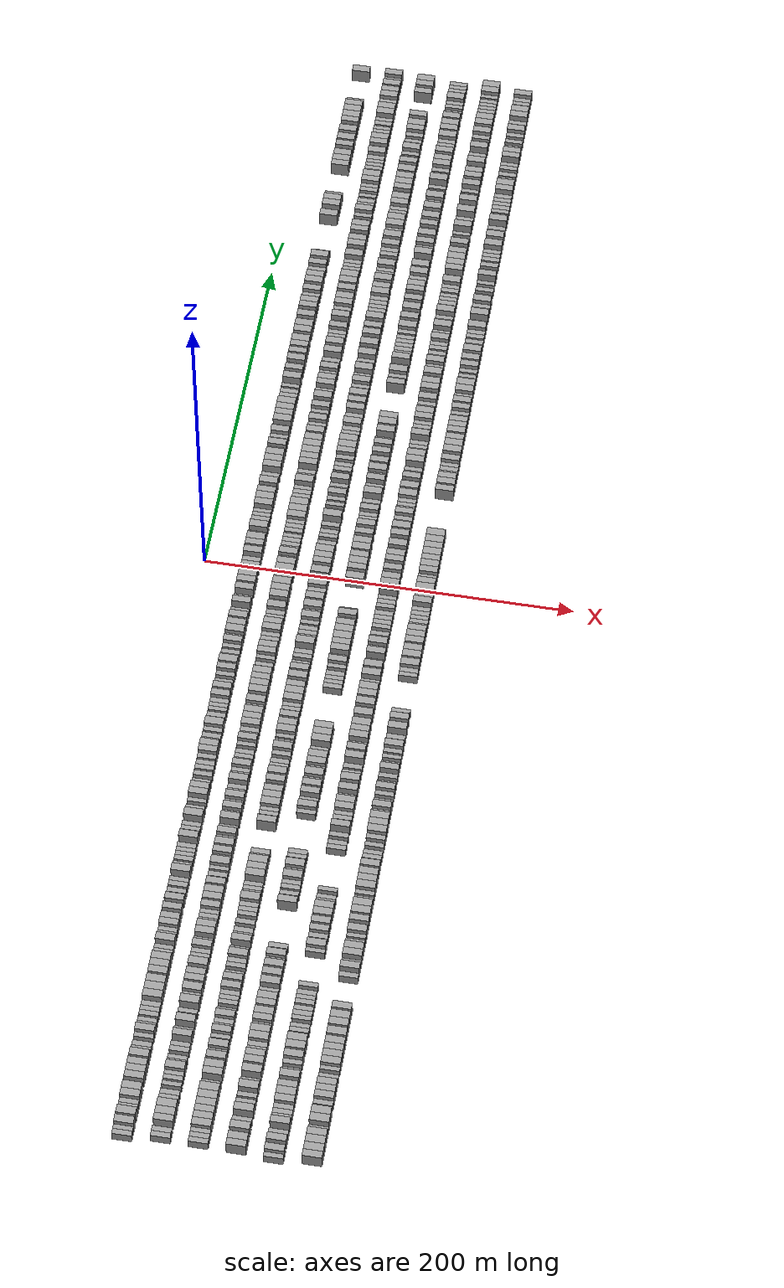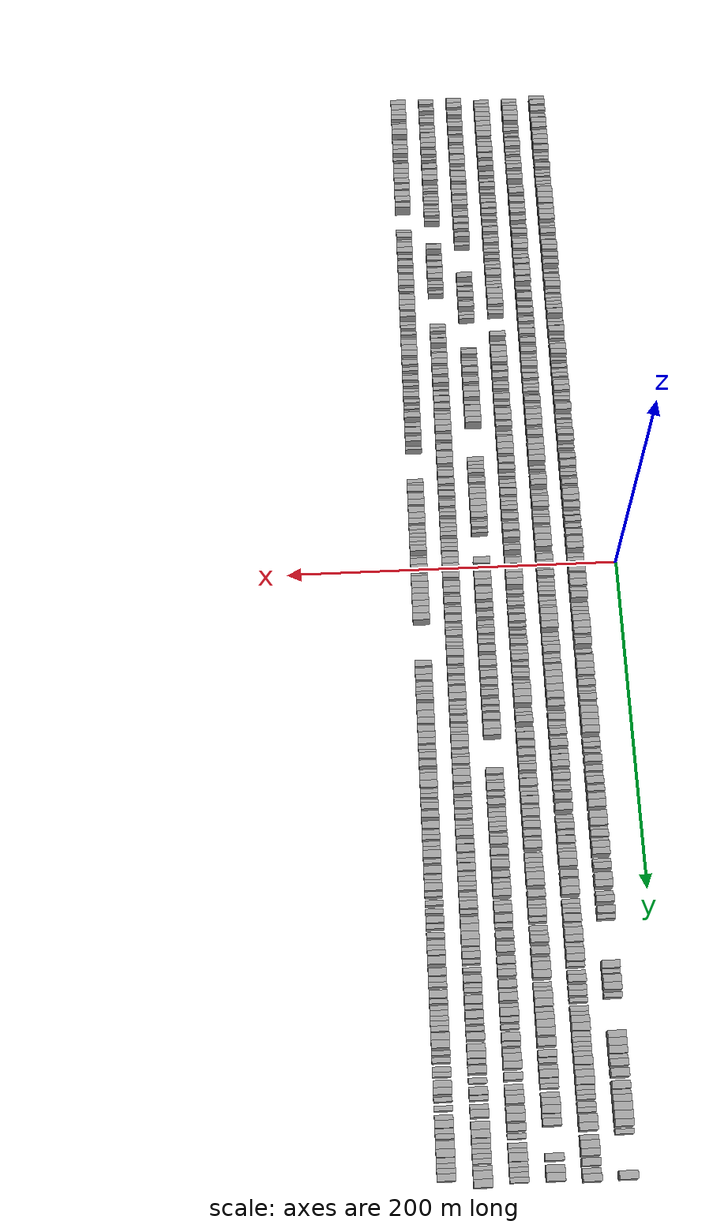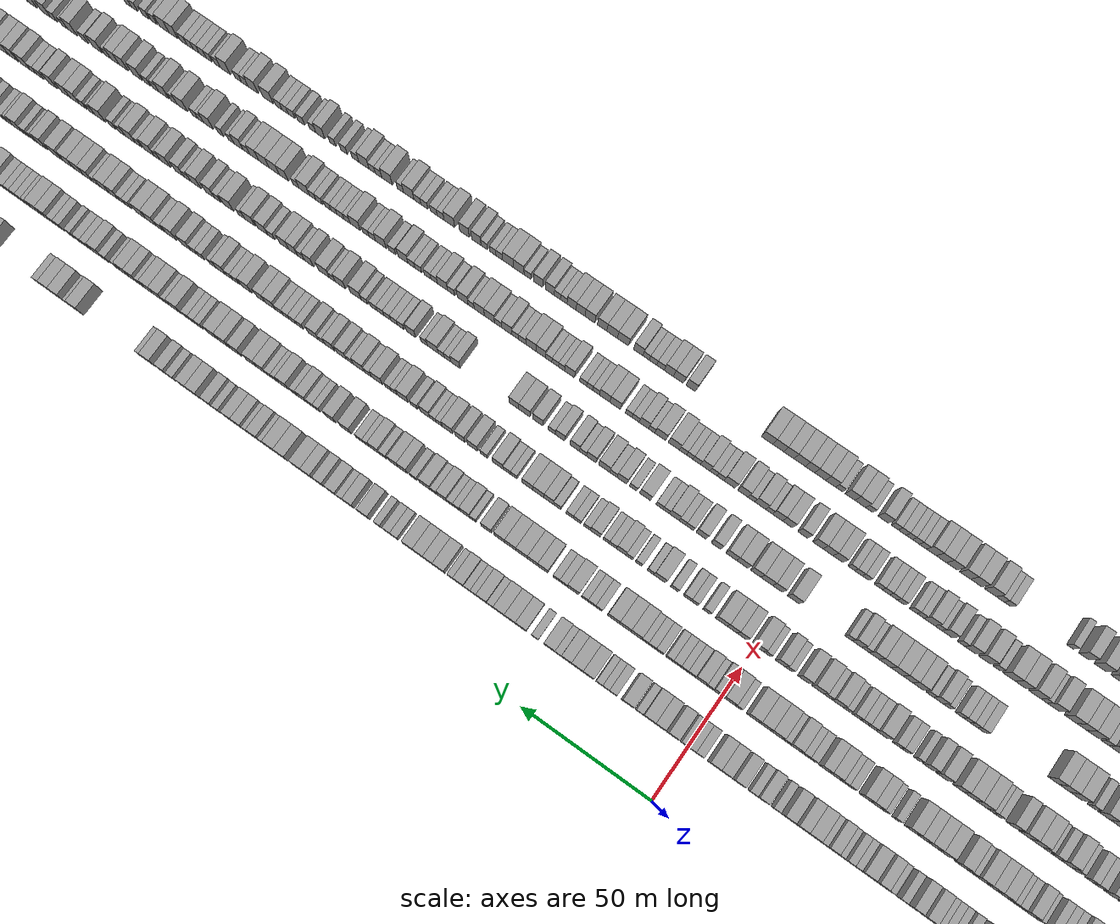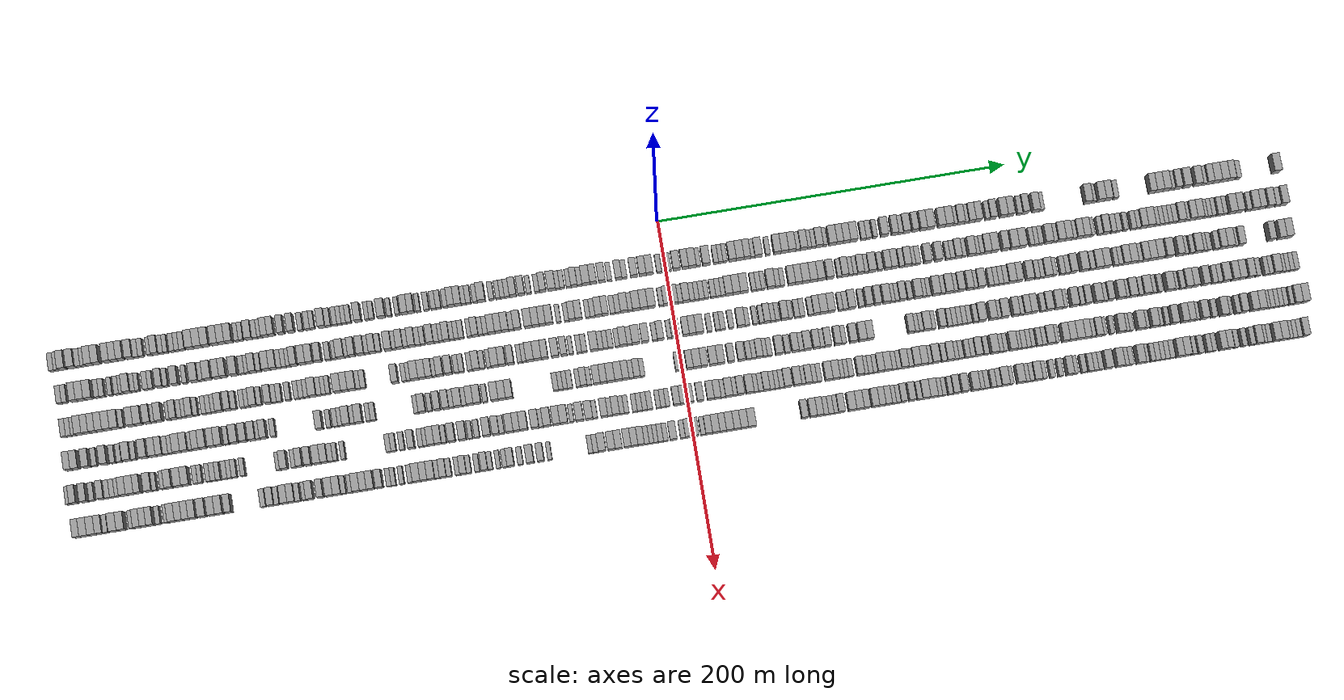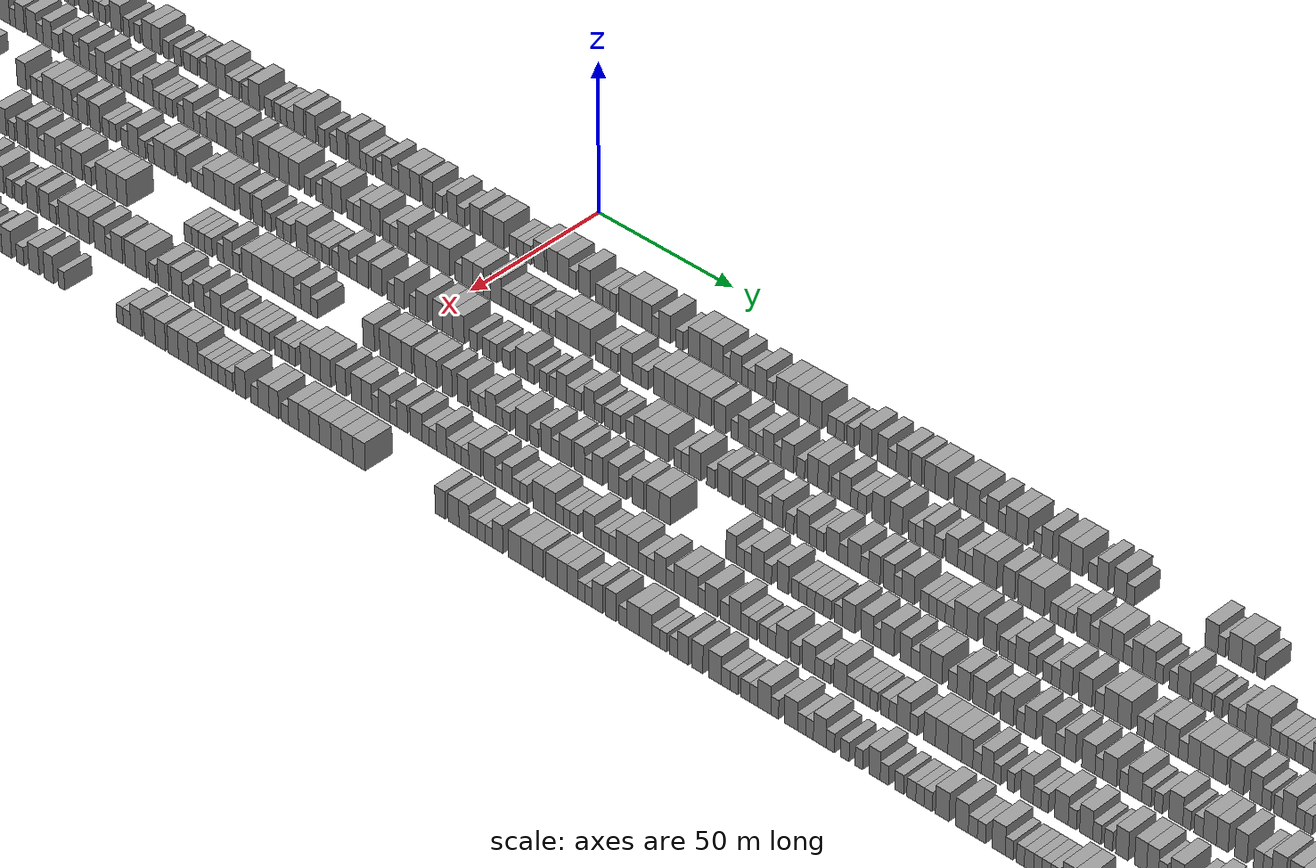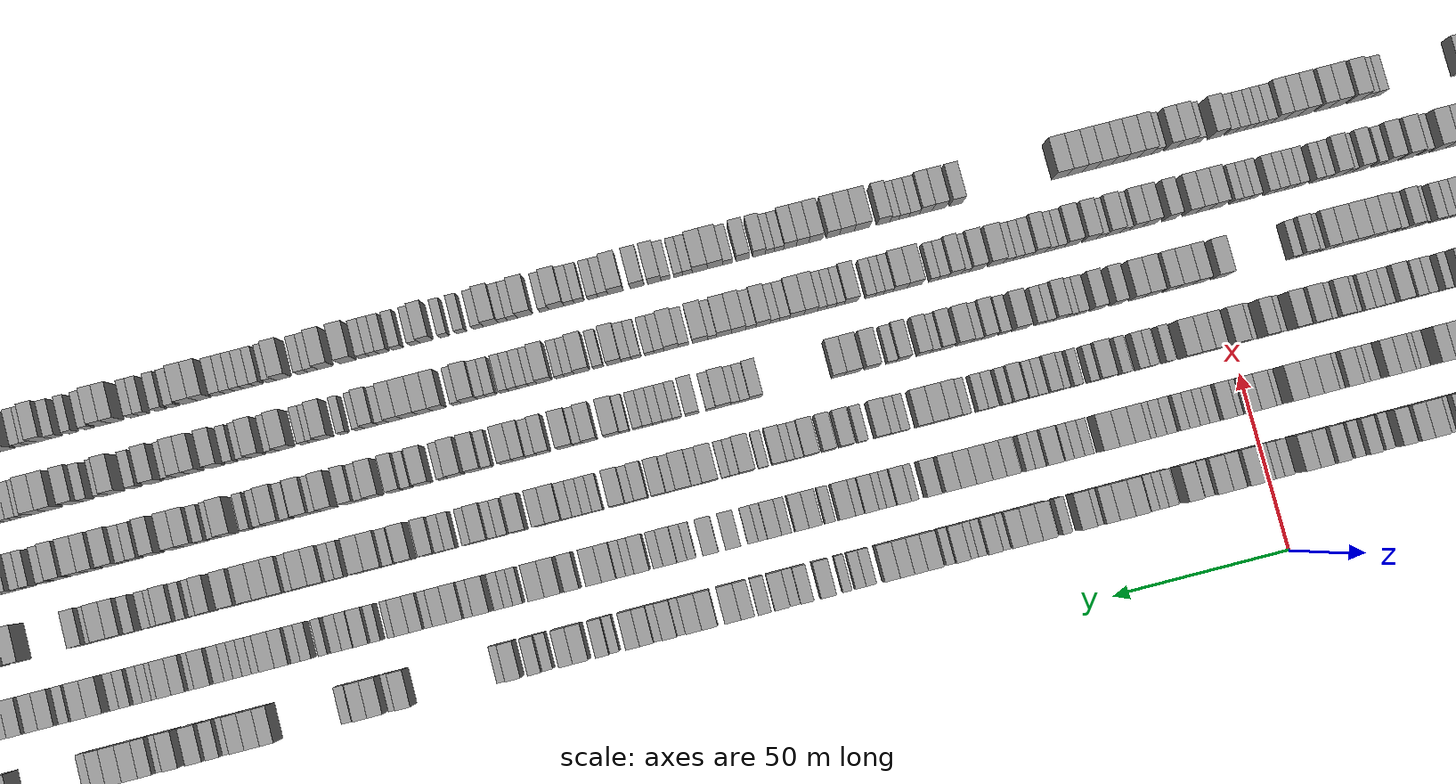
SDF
<sdf version="1.6">
 <world name="default">
  <scene>
   <sky><clouds><speed>12</speed></clouds></sky>
   <ambient>0.4 0.4 0.4 1</ambient>
   <background>0.7 0.7 0.7 1</background>
   <shadows>1</shadows>
  </scene>
  <gravity>0 0 -9.8066</gravity>
  <magnetic_field>6e-06 2.3e-05 -4.2e-05</magnetic_field>
  <physics default="0" name="default_physics" type="ode">
   <ode>
    <solver>
     <type>quick</type>
     <iters>10</iters>
     <sor>1.0</sor>
     <use_dynamic_moi_rescaling>0</use_dynamic_moi_rescaling>
    </solver>
    <constraints>
     <cfm>0</cfm>
     <erp>0.2</erp>
     <contact_max_correcting_vel>100</contact_max_correcting_vel>
     <contact_surface_layer>0.001</contact_surface_layer>
    </constraints>
   </ode>
   <max_step_size>0.004</max_step_size>
   <real_time_factor>1</real_time_factor>
   <real_time_update_rate>250</real_time_update_rate>
  </physics>
  <light name="sun" type="directional">
   <pose>0 0 10 0 0 0</pose>
   <diffuse>0.8 0.8 0.8 1</diffuse>
   <specular>0.2 0.2 0.2 1</specular>
   <attenuation>
    <range>1000</range>
    <constant>0.9</constant>
    <linear>0.01</linear>
    <quadratic>0.001</quadratic>
   </attenuation>
   <direction>-0.5 0.1 -0.9</direction>
  </light>
  <model name="building_1">
   <static>1</static>
   <pose>25.0000 -348.5780 0 0.000000 0.000000 0.000000</pose>
   <link name="link">
    <pose>0 0 3.00 0 0 0</pose>
    <collision name="collision"><geometry><box><size>10.0000 2.8440 6.0000</size></box></geometry></collision>
    <visual name="visual">
     <cast_shadows>0</cast_shadows>
     <geometry><box><size>10.0000 2.8440 6.0000</size></box></geometry>
     <material>
      <script>
       <uri>model://grey_wall/materials/scripts</uri>
       <uri>model://grey_wall/materials/textures</uri>
       <name>vrc/grey_wall</name>
      </script>
     </material>
    </visual>
   </link>
  </model>
  <model name="building_2">
   <static>1</static>
   <pose>25.0000 -345.8942 0 0.000000 0.000000 0.000000</pose>
   <link name="link">
    <pose>0 0 3.00 0 0 0</pose>
    <collision name="collision"><geometry><box><size>10.0000 2.5237 6.0000</size></box></geometry></collision>
    <visual name="visual">
     <cast_shadows>0</cast_shadows>
     <geometry><box><size>10.0000 2.5237 6.0000</size></box></geometry>
     <material>
      <script>
       <uri>model://grey_wall/materials/scripts</uri>
       <uri>model://grey_wall/materials/textures</uri>
       <name>vrc/grey_wall</name>
      </script>
     </material>
    </visual>
   </link>
  </model>
  <model name="building_3">
   <static>1</static>
   <pose>25.0000 -342.5677 0 0.000000 0.000000 0.000000</pose>
   <link name="link">
    <pose>0 0 4.50 0 0 0</pose>
    <collision name="collision"><geometry><box><size>10.0000 4.1292 9.0000</size></box></geometry></collision>
    <visual name="visual">
     <cast_shadows>0</cast_shadows>
     <geometry><box><size>10.0000 4.1292 9.0000</size></box></geometry>
     <material>
      <script>
       <uri>model://grey_wall/materials/scripts</uri>
       <uri>model://grey_wall/materials/textures</uri>
       <name>vrc/grey_wall</name>
      </script>
     </material>
    </visual>
   </link>
  </model>
  <model name="building_4">
   <static>1</static>
   <pose>25.0000 -337.3223 0 0.000000 0.000000 0.000000</pose>
   <link name="link">
    <pose>0 0 4.50 0 0 0</pose>
    <collision name="collision"><geometry><box><size>10.0000 4.3617 9.0000</size></box></geometry></collision>
    <visual name="visual">
     <cast_shadows>0</cast_shadows>
     <geometry><box><size>10.0000 4.3617 9.0000</size></box></geometry>
     <material>
      <script>
       <uri>model://grey_wall/materials/scripts</uri>
       <uri>model://grey_wall/materials/textures</uri>
       <name>vrc/grey_wall</name>
      </script>
     </material>
    </visual>
   </link>
  </model>
  <model name="building_5">
   <static>1</static>
   <pose>25.0000 -333.6728 0 0.000000 0.000000 0.000000</pose>
   <link name="link">
    <pose>0 0 3.00 0 0 0</pose>
    <collision name="collision"><geometry><box><size>10.0000 2.9372 6.0000</size></box></geometry></collision>
    <visual name="visual">
     <cast_shadows>0</cast_shadows>
     <geometry><box><size>10.0000 2.9372 6.0000</size></box></geometry>
     <material>
      <script>
       <uri>model://grey_wall/materials/scripts</uri>
       <uri>model://grey_wall/materials/textures</uri>
       <name>vrc/grey_wall</name>
      </script>
     </material>
    </visual>
   </link>
  </model>
  <model name="building_6">
   <static>1</static>
   <pose>25.0000 -330.8475 0 0.000000 0.000000 0.000000</pose>
   <link name="link">
    <pose>0 0 3.00 0 0 0</pose>
    <collision name="collision"><geometry><box><size>10.0000 2.7134 6.0000</size></box></geometry></collision>
    <visual name="visual">
     <cast_shadows>0</cast_shadows>
     <geometry><box><size>10.0000 2.7134 6.0000</size></box></geometry>
     <material>
      <script>
       <uri>model://grey_wall/materials/scripts</uri>
       <uri>model://grey_wall/materials/textures</uri>
       <name>vrc/grey_wall</name>
      </script>
     </material>
    </visual>
   </link>
  </model>
  <model name="building_7">
   <static>1</static>
   <pose>25.0000 -327.4520 0 0.000000 0.000000 0.000000</pose>
   <link name="link">
    <pose>0 0 4.50 0 0 0</pose>
    <collision name="collision"><geometry><box><size>10.0000 4.0775 9.0000</size></box></geometry></collision>
    <visual name="visual">
     <cast_shadows>0</cast_shadows>
     <geometry><box><size>10.0000 4.0775 9.0000</size></box></geometry>
     <material>
      <script>
       <uri>model://grey_wall/materials/scripts</uri>
       <uri>model://grey_wall/materials/textures</uri>
       <name>vrc/grey_wall</name>
      </script>
     </material>
    </visual>
   </link>
  </model>
  <model name="building_8">
   <static>1</static>
   <pose>25.0000 -323.2856 0 0.000000 0.000000 0.000000</pose>
   <link name="link">
    <pose>0 0 4.50 0 0 0</pose>
    <collision name="collision"><geometry><box><size>10.0000 4.2553 9.0000</size></box></geometry></collision>
    <visual name="visual">
     <cast_shadows>0</cast_shadows>
     <geometry><box><size>10.0000 4.2553 9.0000</size></box></geometry>
     <material>
      <script>
       <uri>model://grey_wall/materials/scripts</uri>
       <uri>model://grey_wall/materials/textures</uri>
       <name>vrc/grey_wall</name>
      </script>
     </material>
    </visual>
   </link>
  </model>
  <model name="building_9">
   <static>1</static>
   <pose>25.0000 -317.2281 0 0.000000 0.000000 0.000000</pose>
   <link name="link">
    <pose>0 0 4.50 0 0 0</pose>
    <collision name="collision"><geometry><box><size>10.0000 3.8598 9.0000</size></box></geometry></collision>
    <visual name="visual">
     <cast_shadows>0</cast_shadows>
     <geometry><box><size>10.0000 3.8598 9.0000</size></box></geometry>
     <material>
      <script>
       <uri>model://grey_wall/materials/scripts</uri>
       <uri>model://grey_wall/materials/textures</uri>
       <name>vrc/grey_wall</name>
      </script>
     </material>
    </visual>
   </link>
  </model>
  <model name="building_10">
   <static>1</static>
   <pose>25.0000 -313.3753 0 0.000000 0.000000 0.000000</pose>
   <link name="link">
    <pose>0 0 4.50 0 0 0</pose>
    <collision name="collision"><geometry><box><size>10.0000 3.8457 9.0000</size></box></geometry></collision>
    <visual name="visual">
     <cast_shadows>0</cast_shadows>
     <geometry><box><size>10.0000 3.8457 9.0000</size></box></geometry>
     <material>
      <script>
       <uri>model://grey_wall/materials/scripts</uri>
       <uri>model://grey_wall/materials/textures</uri>
       <name>vrc/grey_wall</name>
      </script>
     </material>
    </visual>
   </link>
  </model>
  <model name="building_11">
   <static>1</static>
   <pose>25.0000 -309.5470 0 0.000000 0.000000 0.000000</pose>
   <link name="link">
    <pose>0 0 4.50 0 0 0</pose>
    <collision name="collision"><geometry><box><size>10.0000 3.8109 9.0000</size></box></geometry></collision>
    <visual name="visual">
     <cast_shadows>0</cast_shadows>
     <geometry><box><size>10.0000 3.8109 9.0000</size></box></geometry>
     <material>
      <script>
       <uri>model://grey_wall/materials/scripts</uri>
       <uri>model://grey_wall/materials/textures</uri>
       <name>vrc/grey_wall</name>
      </script>
     </material>
    </visual>
   </link>
  </model>
  <model name="building_12">
   <static>1</static>
   <pose>25.0000 -304.5238 0 0.000000 0.000000 0.000000</pose>
   <link name="link">
    <pose>0 0 4.50 0 0 0</pose>
    <collision name="collision"><geometry><box><size>10.0000 4.2355 9.0000</size></box></geometry></collision>
    <visual name="visual">
     <cast_shadows>0</cast_shadows>
     <geometry><box><size>10.0000 4.2355 9.0000</size></box></geometry>
     <material>
      <script>
       <uri>model://grey_wall/materials/scripts</uri>
       <uri>model://grey_wall/materials/textures</uri>
       <name>vrc/grey_wall</name>
      </script>
     </material>
    </visual>
   </link>
  </model>
  <model name="building_13">
   <static>1</static>
   <pose>25.0000 -300.9921 0 0.000000 0.000000 0.000000</pose>
   <link name="link">
    <pose>0 0 3.00 0 0 0</pose>
    <collision name="collision"><geometry><box><size>10.0000 2.8278 6.0000</size></box></geometry></collision>
    <visual name="visual">
     <cast_shadows>0</cast_shadows>
     <geometry><box><size>10.0000 2.8278 6.0000</size></box></geometry>
     <material>
      <script>
       <uri>model://grey_wall/materials/scripts</uri>
       <uri>model://grey_wall/materials/textures</uri>
       <name>vrc/grey_wall</name>
      </script>
     </material>
    </visual>
   </link>
  </model>
  <model name="building_14">
   <static>1</static>
   <pose>25.0000 -298.1075 0 0.000000 0.000000 0.000000</pose>
   <link name="link">
    <pose>0 0 3.00 0 0 0</pose>
    <collision name="collision"><geometry><box><size>10.0000 2.9415 6.0000</size></box></geometry></collision>
    <visual name="visual">
     <cast_shadows>0</cast_shadows>
     <geometry><box><size>10.0000 2.9415 6.0000</size></box></geometry>
     <material>
      <script>
       <uri>model://grey_wall/materials/scripts</uri>
       <uri>model://grey_wall/materials/textures</uri>
       <name>vrc/grey_wall</name>
      </script>
     </material>
    </visual>
   </link>
  </model>
  <model name="building_15">
   <static>1</static>
   <pose>25.0000 -293.2994 0 0.000000 0.000000 0.000000</pose>
   <link name="link">
    <pose>0 0 3.00 0 0 0</pose>
    <collision name="collision"><geometry><box><size>10.0000 2.6746 6.0000</size></box></geometry></collision>
    <visual name="visual">
     <cast_shadows>0</cast_shadows>
     <geometry><box><size>10.0000 2.6746 6.0000</size></box></geometry>
     <material>
      <script>
       <uri>model://grey_wall/materials/scripts</uri>
       <uri>model://grey_wall/materials/textures</uri>
       <name>vrc/grey_wall</name>
      </script>
     </material>
    </visual>
   </link>
  </model>
  <model name="building_16">
   <static>1</static>
   <pose>25.0000 -290.0480 0 0.000000 0.000000 0.000000</pose>
   <link name="link">
    <pose>0 0 4.50 0 0 0</pose>
    <collision name="collision"><geometry><box><size>10.0000 3.8283 9.0000</size></box></geometry></collision>
    <visual name="visual">
     <cast_shadows>0</cast_shadows>
     <geometry><box><size>10.0000 3.8283 9.0000</size></box></geometry>
     <material>
      <script>
       <uri>model://grey_wall/materials/scripts</uri>
       <uri>model://grey_wall/materials/textures</uri>
       <name>vrc/grey_wall</name>
      </script>
     </material>
    </visual>
   </link>
  </model>
  <model name="building_17">
   <static>1</static>
   <pose>25.0000 -286.8046 0 0.000000 0.000000 0.000000</pose>
   <link name="link">
    <pose>0 0 3.00 0 0 0</pose>
    <collision name="collision"><geometry><box><size>10.0000 2.6584 6.0000</size></box></geometry></collision>
    <visual name="visual">
     <cast_shadows>0</cast_shadows>
     <geometry><box><size>10.0000 2.6584 6.0000</size></box></geometry>
     <material>
      <script>
       <uri>model://grey_wall/materials/scripts</uri>
       <uri>model://grey_wall/materials/textures</uri>
       <name>vrc/grey_wall</name>
      </script>
     </material>
    </visual>
   </link>
  </model>
  <model name="building_18">
   <static>1</static>
   <pose>25.0000 -284.1970 0 0.000000 0.000000 0.000000</pose>
   <link name="link">
    <pose>0 0 3.00 0 0 0</pose>
    <collision name="collision"><geometry><box><size>10.0000 2.5568 6.0000</size></box></geometry></collision>
    <visual name="visual">
     <cast_shadows>0</cast_shadows>
     <geometry><box><size>10.0000 2.5568 6.0000</size></box></geometry>
     <material>
      <script>
       <uri>model://grey_wall/materials/scripts</uri>
       <uri>model://grey_wall/materials/textures</uri>
       <name>vrc/grey_wall</name>
      </script>
     </material>
    </visual>
   </link>
  </model>
  <model name="building_19">
   <static>1</static>
   <pose>25.0000 -280.5066 0 0.000000 0.000000 0.000000</pose>
   <link name="link">
    <pose>0 0 3.00 0 0 0</pose>
    <collision name="collision"><geometry><box><size>10.0000 2.8239 6.0000</size></box></geometry></collision>
    <visual name="visual">
     <cast_shadows>0</cast_shadows>
     <geometry><box><size>10.0000 2.8239 6.0000</size></box></geometry>
     <material>
      <script>
       <uri>model://grey_wall/materials/scripts</uri>
       <uri>model://grey_wall/materials/textures</uri>
       <name>vrc/grey_wall</name>
      </script>
     </material>
    </visual>
   </link>
  </model>
  <model name="building_20">
   <static>1</static>
   <pose>25.0000 -277.7799 0 0.000000 0.000000 0.000000</pose>
   <link name="link">
    <pose>0 0 3.00 0 0 0</pose>
    <collision name="collision"><geometry><box><size>10.0000 2.6295 6.0000</size></box></geometry></collision>
    <visual name="visual">
     <cast_shadows>0</cast_shadows>
     <geometry><box><size>10.0000 2.6295 6.0000</size></box></geometry>
     <material>
      <script>
       <uri>model://grey_wall/materials/scripts</uri>
       <uri>model://grey_wall/materials/textures</uri>
       <name>vrc/grey_wall</name>
      </script>
     </material>
    </visual>
   </link>
  </model>
  <model name="building_21">
   <static>1</static>
   <pose>25.0000 -274.9703 0 0.000000 0.000000 0.000000</pose>
   <link name="link">
    <pose>0 0 3.00 0 0 0</pose>
    <collision name="collision"><geometry><box><size>10.0000 2.9897 6.0000</size></box></geometry></collision>
    <visual name="visual">
     <cast_shadows>0</cast_shadows>
     <geometry><box><size>10.0000 2.9897 6.0000</size></box></geometry>
     <material>
      <script>
       <uri>model://grey_wall/materials/scripts</uri>
       <uri>model://grey_wall/materials/textures</uri>
       <name>vrc/grey_wall</name>
      </script>
     </material>
    </visual>
   </link>
  </model>
  <model name="building_22">
   <static>1</static>
   <pose>25.0000 -270.3398 0 0.000000 0.000000 0.000000</pose>
   <link name="link">
    <pose>0 0 4.50 0 0 0</pose>
    <collision name="collision"><geometry><box><size>10.0000 4.2713 9.0000</size></box></geometry></collision>
    <visual name="visual">
     <cast_shadows>0</cast_shadows>
     <geometry><box><size>10.0000 4.2713 9.0000</size></box></geometry>
     <material>
      <script>
       <uri>model://grey_wall/materials/scripts</uri>
       <uri>model://grey_wall/materials/textures</uri>
       <name>vrc/grey_wall</name>
      </script>
     </material>
    </visual>
   </link>
  </model>
  <model name="building_23">
   <static>1</static>
   <pose>25.0000 -265.9745 0 0.000000 0.000000 0.000000</pose>
   <link name="link">
    <pose>0 0 4.50 0 0 0</pose>
    <collision name="collision"><geometry><box><size>10.0000 4.4593 9.0000</size></box></geometry></collision>
    <visual name="visual">
     <cast_shadows>0</cast_shadows>
     <geometry><box><size>10.0000 4.4593 9.0000</size></box></geometry>
     <material>
      <script>
       <uri>model://grey_wall/materials/scripts</uri>
       <uri>model://grey_wall/materials/textures</uri>
       <name>vrc/grey_wall</name>
      </script>
     </material>
    </visual>
   </link>
  </model>
  <model name="building_24">
   <static>1</static>
   <pose>25.0000 -261.5767 0 0.000000 0.000000 0.000000</pose>
   <link name="link">
    <pose>0 0 4.50 0 0 0</pose>
    <collision name="collision"><geometry><box><size>10.0000 4.3362 9.0000</size></box></geometry></collision>
    <visual name="visual">
     <cast_shadows>0</cast_shadows>
     <geometry><box><size>10.0000 4.3362 9.0000</size></box></geometry>
     <material>
      <script>
       <uri>model://grey_wall/materials/scripts</uri>
       <uri>model://grey_wall/materials/textures</uri>
       <name>vrc/grey_wall</name>
      </script>
     </material>
    </visual>
   </link>
  </model>
  <model name="building_25">
   <static>1</static>
   <pose>25.0000 -256.4209 0 0.000000 0.000000 0.000000</pose>
   <link name="link">
    <pose>0 0 4.50 0 0 0</pose>
    <collision name="collision"><geometry><box><size>10.0000 3.9754 9.0000</size></box></geometry></collision>
    <visual name="visual">
     <cast_shadows>0</cast_shadows>
     <geometry><box><size>10.0000 3.9754 9.0000</size></box></geometry>
     <material>
      <script>
       <uri>model://grey_wall/materials/scripts</uri>
       <uri>model://grey_wall/materials/textures</uri>
       <name>vrc/grey_wall</name>
      </script>
     </material>
    </visual>
   </link>
  </model>
  <model name="building_26">
   <static>1</static>
   <pose>25.0000 -252.3965 0 0.000000 0.000000 0.000000</pose>
   <link name="link">
    <pose>0 0 4.50 0 0 0</pose>
    <collision name="collision"><geometry><box><size>10.0000 4.0735 9.0000</size></box></geometry></collision>
    <visual name="visual">
     <cast_shadows>0</cast_shadows>
     <geometry><box><size>10.0000 4.0735 9.0000</size></box></geometry>
     <material>
      <script>
       <uri>model://grey_wall/materials/scripts</uri>
       <uri>model://grey_wall/materials/textures</uri>
       <name>vrc/grey_wall</name>
      </script>
     </material>
    </visual>
   </link>
  </model>
  <model name="building_27">
   <static>1</static>
   <pose>25.0000 -248.3102 0 0.000000 0.000000 0.000000</pose>
   <link name="link">
    <pose>0 0 4.50 0 0 0</pose>
    <collision name="collision"><geometry><box><size>10.0000 4.0991 9.0000</size></box></geometry></collision>
    <visual name="visual">
     <cast_shadows>0</cast_shadows>
     <geometry><box><size>10.0000 4.0991 9.0000</size></box></geometry>
     <material>
      <script>
       <uri>model://grey_wall/materials/scripts</uri>
       <uri>model://grey_wall/materials/textures</uri>
       <name>vrc/grey_wall</name>
      </script>
     </material>
    </visual>
   </link>
  </model>
  <model name="building_28">
   <static>1</static>
   <pose>25.0000 -244.0302 0 0.000000 0.000000 0.000000</pose>
   <link name="link">
    <pose>0 0 3.00 0 0 0</pose>
    <collision name="collision"><geometry><box><size>10.0000 2.4609 6.0000</size></box></geometry></collision>
    <visual name="visual">
     <cast_shadows>0</cast_shadows>
     <geometry><box><size>10.0000 2.4609 6.0000</size></box></geometry>
     <material>
      <script>
       <uri>model://grey_wall/materials/scripts</uri>
       <uri>model://grey_wall/materials/textures</uri>
       <name>vrc/grey_wall</name>
      </script>
     </material>
    </visual>
   </link>
  </model>
  <model name="building_29">
   <static>1</static>
   <pose>25.0000 -241.5087 0 0.000000 0.000000 0.000000</pose>
   <link name="link">
    <pose>0 0 3.00 0 0 0</pose>
    <collision name="collision"><geometry><box><size>10.0000 2.5821 6.0000</size></box></geometry></collision>
    <visual name="visual">
     <cast_shadows>0</cast_shadows>
     <geometry><box><size>10.0000 2.5821 6.0000</size></box></geometry>
     <material>
      <script>
       <uri>model://grey_wall/materials/scripts</uri>
       <uri>model://grey_wall/materials/textures</uri>
       <name>vrc/grey_wall</name>
      </script>
     </material>
    </visual>
   </link>
  </model>
  <model name="building_30">
   <static>1</static>
   <pose>25.0000 -237.1958 0 0.000000 0.000000 0.000000</pose>
   <link name="link">
    <pose>0 0 4.50 0 0 0</pose>
    <collision name="collision"><geometry><box><size>10.0000 4.0437 9.0000</size></box></geometry></collision>
    <visual name="visual">
     <cast_shadows>0</cast_shadows>
     <geometry><box><size>10.0000 4.0437 9.0000</size></box></geometry>
     <material>
      <script>
       <uri>model://grey_wall/materials/scripts</uri>
       <uri>model://grey_wall/materials/textures</uri>
       <name>vrc/grey_wall</name>
      </script>
     </material>
    </visual>
   </link>
  </model>
  <model name="building_31">
   <static>1</static>
   <pose>25.0000 -233.7593 0 0.000000 0.000000 0.000000</pose>
   <link name="link">
    <pose>0 0 3.00 0 0 0</pose>
    <collision name="collision"><geometry><box><size>10.0000 2.8293 6.0000</size></box></geometry></collision>
    <visual name="visual">
     <cast_shadows>0</cast_shadows>
     <geometry><box><size>10.0000 2.8293 6.0000</size></box></geometry>
     <material>
      <script>
       <uri>model://grey_wall/materials/scripts</uri>
       <uri>model://grey_wall/materials/textures</uri>
       <name>vrc/grey_wall</name>
      </script>
     </material>
    </visual>
   </link>
  </model>
  <model name="building_32">
   <static>1</static>
   <pose>25.0000 -231.0719 0 0.000000 0.000000 0.000000</pose>
   <link name="link">
    <pose>0 0 3.00 0 0 0</pose>
    <collision name="collision"><geometry><box><size>10.0000 2.5455 6.0000</size></box></geometry></collision>
    <visual name="visual">
     <cast_shadows>0</cast_shadows>
     <geometry><box><size>10.0000 2.5455 6.0000</size></box></geometry>
     <material>
      <script>
       <uri>model://grey_wall/materials/scripts</uri>
       <uri>model://grey_wall/materials/textures</uri>
       <name>vrc/grey_wall</name>
      </script>
     </material>
    </visual>
   </link>
  </model>
  <model name="building_33">
   <static>1</static>
   <pose>25.0000 -227.9759 0 0.000000 0.000000 0.000000</pose>
   <link name="link">
    <pose>0 0 4.50 0 0 0</pose>
    <collision name="collision"><geometry><box><size>10.0000 3.6464 9.0000</size></box></geometry></collision>
    <visual name="visual">
     <cast_shadows>0</cast_shadows>
     <geometry><box><size>10.0000 3.6464 9.0000</size></box></geometry>
     <material>
      <script>
       <uri>model://grey_wall/materials/scripts</uri>
       <uri>model://grey_wall/materials/textures</uri>
       <name>vrc/grey_wall</name>
      </script>
     </material>
    </visual>
   </link>
  </model>
  <model name="building_34">
   <static>1</static>
   <pose>25.0000 -224.3496 0 0.000000 0.000000 0.000000</pose>
   <link name="link">
    <pose>0 0 4.50 0 0 0</pose>
    <collision name="collision"><geometry><box><size>10.0000 3.6063 9.0000</size></box></geometry></collision>
    <visual name="visual">
     <cast_shadows>0</cast_shadows>
     <geometry><box><size>10.0000 3.6063 9.0000</size></box></geometry>
     <material>
      <script>
       <uri>model://grey_wall/materials/scripts</uri>
       <uri>model://grey_wall/materials/textures</uri>
       <name>vrc/grey_wall</name>
      </script>
     </material>
    </visual>
   </link>
  </model>
  <model name="building_35">
   <static>1</static>
   <pose>25.0000 -218.7335 0 0.000000 0.000000 0.000000</pose>
   <link name="link">
    <pose>0 0 4.50 0 0 0</pose>
    <collision name="collision"><geometry><box><size>10.0000 3.6258 9.0000</size></box></geometry></collision>
    <visual name="visual">
     <cast_shadows>0</cast_shadows>
     <geometry><box><size>10.0000 3.6258 9.0000</size></box></geometry>
     <material>
      <script>
       <uri>model://grey_wall/materials/scripts</uri>
       <uri>model://grey_wall/materials/textures</uri>
       <name>vrc/grey_wall</name>
      </script>
     </material>
    </visual>
   </link>
  </model>
  <model name="building_36">
   <static>1</static>
   <pose>25.0000 -213.0694 0 0.000000 0.000000 0.000000</pose>
   <link name="link">
    <pose>0 0 4.50 0 0 0</pose>
    <collision name="collision"><geometry><box><size>10.0000 3.7023 9.0000</size></box></geometry></collision>
    <visual name="visual">
     <cast_shadows>0</cast_shadows>
     <geometry><box><size>10.0000 3.7023 9.0000</size></box></geometry>
     <material>
      <script>
       <uri>model://grey_wall/materials/scripts</uri>
       <uri>model://grey_wall/materials/textures</uri>
       <name>vrc/grey_wall</name>
      </script>
     </material>
    </visual>
   </link>
  </model>
  <model name="building_37">
   <static>1</static>
   <pose>25.0000 -207.8051 0 0.000000 0.000000 0.000000</pose>
   <link name="link">
    <pose>0 0 3.00 0 0 0</pose>
    <collision name="collision"><geometry><box><size>10.0000 2.8263 6.0000</size></box></geometry></collision>
    <visual name="visual">
     <cast_shadows>0</cast_shadows>
     <geometry><box><size>10.0000 2.8263 6.0000</size></box></geometry>
     <material>
      <script>
       <uri>model://grey_wall/materials/scripts</uri>
       <uri>model://grey_wall/materials/textures</uri>
       <name>vrc/grey_wall</name>
      </script>
     </material>
    </visual>
   </link>
  </model>
  <model name="building_38">
   <static>1</static>
   <pose>25.0000 -203.8979 0 0.000000 0.000000 0.000000</pose>
   <link name="link">
    <pose>0 0 3.00 0 0 0</pose>
    <collision name="collision"><geometry><box><size>10.0000 2.9881 6.0000</size></box></geometry></collision>
    <visual name="visual">
     <cast_shadows>0</cast_shadows>
     <geometry><box><size>10.0000 2.9881 6.0000</size></box></geometry>
     <material>
      <script>
       <uri>model://grey_wall/materials/scripts</uri>
       <uri>model://grey_wall/materials/textures</uri>
       <name>vrc/grey_wall</name>
      </script>
     </material>
    </visual>
   </link>
  </model>
  <model name="building_39">
   <static>1</static>
   <pose>25.0000 -201.1234 0 0.000000 0.000000 0.000000</pose>
   <link name="link">
    <pose>0 0 3.00 0 0 0</pose>
    <collision name="collision"><geometry><box><size>10.0000 2.5610 6.0000</size></box></geometry></collision>
    <visual name="visual">
     <cast_shadows>0</cast_shadows>
     <geometry><box><size>10.0000 2.5610 6.0000</size></box></geometry>
     <material>
      <script>
       <uri>model://grey_wall/materials/scripts</uri>
       <uri>model://grey_wall/materials/textures</uri>
       <name>vrc/grey_wall</name>
      </script>
     </material>
    </visual>
   </link>
  </model>
  <model name="building_40">
   <static>1</static>
   <pose>25.0000 -195.7708 0 0.000000 0.000000 0.000000</pose>
   <link name="link">
    <pose>0 0 4.50 0 0 0</pose>
    <collision name="collision"><geometry><box><size>10.0000 4.1442 9.0000</size></box></geometry></collision>
    <visual name="visual">
     <cast_shadows>0</cast_shadows>
     <geometry><box><size>10.0000 4.1442 9.0000</size></box></geometry>
     <material>
      <script>
       <uri>model://grey_wall/materials/scripts</uri>
       <uri>model://grey_wall/materials/textures</uri>
       <name>vrc/grey_wall</name>
      </script>
     </material>
    </visual>
   </link>
  </model>
  <model name="building_41">
   <static>1</static>
   <pose>25.0000 -192.2046 0 0.000000 0.000000 0.000000</pose>
   <link name="link">
    <pose>0 0 3.00 0 0 0</pose>
    <collision name="collision"><geometry><box><size>10.0000 2.9881 6.0000</size></box></geometry></collision>
    <visual name="visual">
     <cast_shadows>0</cast_shadows>
     <geometry><box><size>10.0000 2.9881 6.0000</size></box></geometry>
     <material>
      <script>
       <uri>model://grey_wall/materials/scripts</uri>
       <uri>model://grey_wall/materials/textures</uri>
       <name>vrc/grey_wall</name>
      </script>
     </material>
    </visual>
   </link>
  </model>
  <model name="building_42">
   <static>1</static>
   <pose>25.0000 -188.3432 0 0.000000 0.000000 0.000000</pose>
   <link name="link">
    <pose>0 0 3.00 0 0 0</pose>
    <collision name="collision"><geometry><box><size>10.0000 2.7347 6.0000</size></box></geometry></collision>
    <visual name="visual">
     <cast_shadows>0</cast_shadows>
     <geometry><box><size>10.0000 2.7347 6.0000</size></box></geometry>
     <material>
      <script>
       <uri>model://grey_wall/materials/scripts</uri>
       <uri>model://grey_wall/materials/textures</uri>
       <name>vrc/grey_wall</name>
      </script>
     </material>
    </visual>
   </link>
  </model>
  <model name="building_43">
   <static>1</static>
   <pose>25.0000 -185.7356 0 0.000000 0.000000 0.000000</pose>
   <link name="link">
    <pose>0 0 3.00 0 0 0</pose>
    <collision name="collision"><geometry><box><size>10.0000 2.4803 6.0000</size></box></geometry></collision>
    <visual name="visual">
     <cast_shadows>0</cast_shadows>
     <geometry><box><size>10.0000 2.4803 6.0000</size></box></geometry>
     <material>
      <script>
       <uri>model://grey_wall/materials/scripts</uri>
       <uri>model://grey_wall/materials/textures</uri>
       <name>vrc/grey_wall</name>
      </script>
     </material>
    </visual>
   </link>
  </model>
  <model name="building_44">
   <static>1</static>
   <pose>25.0000 -183.2464 0 0.000000 0.000000 0.000000</pose>
   <link name="link">
    <pose>0 0 3.00 0 0 0</pose>
    <collision name="collision"><geometry><box><size>10.0000 2.4982 6.0000</size></box></geometry></collision>
    <visual name="visual">
     <cast_shadows>0</cast_shadows>
     <geometry><box><size>10.0000 2.4982 6.0000</size></box></geometry>
     <material>
      <script>
       <uri>model://grey_wall/materials/scripts</uri>
       <uri>model://grey_wall/materials/textures</uri>
       <name>vrc/grey_wall</name>
      </script>
     </material>
    </visual>
   </link>
  </model>
  <model name="building_45">
   <static>1</static>
   <pose>25.0000 -180.5771 0 0.000000 0.000000 0.000000</pose>
   <link name="link">
    <pose>0 0 3.00 0 0 0</pose>
    <collision name="collision"><geometry><box><size>10.0000 2.8404 6.0000</size></box></geometry></collision>
    <visual name="visual">
     <cast_shadows>0</cast_shadows>
     <geometry><box><size>10.0000 2.8404 6.0000</size></box></geometry>
     <material>
      <script>
       <uri>model://grey_wall/materials/scripts</uri>
       <uri>model://grey_wall/materials/textures</uri>
       <name>vrc/grey_wall</name>
      </script>
     </material>
    </visual>
   </link>
  </model>
  <model name="building_46">
   <static>1</static>
   <pose>25.0000 -175.1904 0 0.000000 0.000000 0.000000</pose>
   <link name="link">
    <pose>0 0 4.50 0 0 0</pose>
    <collision name="collision"><geometry><box><size>10.0000 3.9329 9.0000</size></box></geometry></collision>
    <visual name="visual">
     <cast_shadows>0</cast_shadows>
     <geometry><box><size>10.0000 3.9329 9.0000</size></box></geometry>
     <material>
      <script>
       <uri>model://grey_wall/materials/scripts</uri>
       <uri>model://grey_wall/materials/textures</uri>
       <name>vrc/grey_wall</name>
      </script>
     </material>
    </visual>
   </link>
  </model>
  <model name="building_47">
   <static>1</static>
   <pose>25.0000 -170.0135 0 0.000000 0.000000 0.000000</pose>
   <link name="link">
    <pose>0 0 3.00 0 0 0</pose>
    <collision name="collision"><geometry><box><size>10.0000 2.4210 6.0000</size></box></geometry></collision>
    <visual name="visual">
     <cast_shadows>0</cast_shadows>
     <geometry><box><size>10.0000 2.4210 6.0000</size></box></geometry>
     <material>
      <script>
       <uri>model://grey_wall/materials/scripts</uri>
       <uri>model://grey_wall/materials/textures</uri>
       <name>vrc/grey_wall</name>
      </script>
     </material>
    </visual>
   </link>
  </model>
  <model name="building_48">
   <static>1</static>
   <pose>25.0000 -167.4191 0 0.000000 0.000000 0.000000</pose>
   <link name="link">
    <pose>0 0 3.00 0 0 0</pose>
    <collision name="collision"><geometry><box><size>10.0000 2.7677 6.0000</size></box></geometry></collision>
    <visual name="visual">
     <cast_shadows>0</cast_shadows>
     <geometry><box><size>10.0000 2.7677 6.0000</size></box></geometry>
     <material>
      <script>
       <uri>model://grey_wall/materials/scripts</uri>
       <uri>model://grey_wall/materials/textures</uri>
       <name>vrc/grey_wall</name>
      </script>
     </material>
    </visual>
   </link>
  </model>
  <model name="building_49">
   <static>1</static>
   <pose>25.0000 -161.8269 0 0.000000 0.000000 0.000000</pose>
   <link name="link">
    <pose>0 0 4.50 0 0 0</pose>
    <collision name="collision"><geometry><box><size>10.0000 4.4167 9.0000</size></box></geometry></collision>
    <visual name="visual">
     <cast_shadows>0</cast_shadows>
     <geometry><box><size>10.0000 4.4167 9.0000</size></box></geometry>
     <material>
      <script>
       <uri>model://grey_wall/materials/scripts</uri>
       <uri>model://grey_wall/materials/textures</uri>
       <name>vrc/grey_wall</name>
      </script>
     </material>
    </visual>
   </link>
  </model>
  <model name="building_50">
   <static>1</static>
   <pose>25.0000 -157.3657 0 0.000000 0.000000 0.000000</pose>
   <link name="link">
    <pose>0 0 3.00 0 0 0</pose>
    <collision name="collision"><geometry><box><size>10.0000 2.5056 6.0000</size></box></geometry></collision>
    <visual name="visual">
     <cast_shadows>0</cast_shadows>
     <geometry><box><size>10.0000 2.5056 6.0000</size></box></geometry>
     <material>
      <script>
       <uri>model://grey_wall/materials/scripts</uri>
       <uri>model://grey_wall/materials/textures</uri>
       <name>vrc/grey_wall</name>
      </script>
     </material>
    </visual>
   </link>
  </model>
  <model name="building_51">
   <static>1</static>
   <pose>25.0000 -152.8962 0 0.000000 0.000000 0.000000</pose>
   <link name="link">
    <pose>0 0 3.00 0 0 0</pose>
    <collision name="collision"><geometry><box><size>10.0000 2.4334 6.0000</size></box></geometry></collision>
    <visual name="visual">
     <cast_shadows>0</cast_shadows>
     <geometry><box><size>10.0000 2.4334 6.0000</size></box></geometry>
     <material>
      <script>
       <uri>model://grey_wall/materials/scripts</uri>
       <uri>model://grey_wall/materials/textures</uri>
       <name>vrc/grey_wall</name>
      </script>
     </material>
    </visual>
   </link>
  </model>
  <model name="building_52">
   <static>1</static>
   <pose>25.0000 -148.7781 0 0.000000 0.000000 0.000000</pose>
   <link name="link">
    <pose>0 0 4.50 0 0 0</pose>
    <collision name="collision"><geometry><box><size>10.0000 3.8028 9.0000</size></box></geometry></collision>
    <visual name="visual">
     <cast_shadows>0</cast_shadows>
     <geometry><box><size>10.0000 3.8028 9.0000</size></box></geometry>
     <material>
      <script>
       <uri>model://grey_wall/materials/scripts</uri>
       <uri>model://grey_wall/materials/textures</uri>
       <name>vrc/grey_wall</name>
      </script>
     </material>
    </visual>
   </link>
  </model>
  <model name="building_53">
   <static>1</static>
   <pose>25.0000 -145.0560 0 0.000000 0.000000 0.000000</pose>
   <link name="link">
    <pose>0 0 4.50 0 0 0</pose>
    <collision name="collision"><geometry><box><size>10.0000 3.6415 9.0000</size></box></geometry></collision>
    <visual name="visual">
     <cast_shadows>0</cast_shadows>
     <geometry><box><size>10.0000 3.6415 9.0000</size></box></geometry>
     <material>
      <script>
       <uri>model://grey_wall/materials/scripts</uri>
       <uri>model://grey_wall/materials/textures</uri>
       <name>vrc/grey_wall</name>
      </script>
     </material>
    </visual>
   </link>
  </model>
  <model name="building_54">
   <static>1</static>
   <pose>25.0000 -140.9952 0 0.000000 0.000000 0.000000</pose>
   <link name="link">
    <pose>0 0 3.00 0 0 0</pose>
    <collision name="collision"><geometry><box><size>10.0000 2.4802 6.0000</size></box></geometry></collision>
    <visual name="visual">
     <cast_shadows>0</cast_shadows>
     <geometry><box><size>10.0000 2.4802 6.0000</size></box></geometry>
     <material>
      <script>
       <uri>model://grey_wall/materials/scripts</uri>
       <uri>model://grey_wall/materials/textures</uri>
       <name>vrc/grey_wall</name>
      </script>
     </material>
    </visual>
   </link>
  </model>
  <model name="building_55">
   <static>1</static>
   <pose>25.0000 -136.2697 0 0.000000 0.000000 0.000000</pose>
   <link name="link">
    <pose>0 0 3.00 0 0 0</pose>
    <collision name="collision"><geometry><box><size>10.0000 2.9708 6.0000</size></box></geometry></collision>
    <visual name="visual">
     <cast_shadows>0</cast_shadows>
     <geometry><box><size>10.0000 2.9708 6.0000</size></box></geometry>
     <material>
      <script>
       <uri>model://grey_wall/materials/scripts</uri>
       <uri>model://grey_wall/materials/textures</uri>
       <name>vrc/grey_wall</name>
      </script>
     </material>
    </visual>
   </link>
  </model>
  <model name="building_56">
   <static>1</static>
   <pose>25.0000 -132.3777 0 0.000000 0.000000 0.000000</pose>
   <link name="link">
    <pose>0 0 3.00 0 0 0</pose>
    <collision name="collision"><geometry><box><size>10.0000 2.8133 6.0000</size></box></geometry></collision>
    <visual name="visual">
     <cast_shadows>0</cast_shadows>
     <geometry><box><size>10.0000 2.8133 6.0000</size></box></geometry>
     <material>
      <script>
       <uri>model://grey_wall/materials/scripts</uri>
       <uri>model://grey_wall/materials/textures</uri>
       <name>vrc/grey_wall</name>
      </script>
     </material>
    </visual>
   </link>
  </model>
  <model name="building_57">
   <static>1</static>
   <pose>25.0000 -129.4978 0 0.000000 0.000000 0.000000</pose>
   <link name="link">
    <pose>0 0 3.00 0 0 0</pose>
    <collision name="collision"><geometry><box><size>10.0000 2.9466 6.0000</size></box></geometry></collision>
    <visual name="visual">
     <cast_shadows>0</cast_shadows>
     <geometry><box><size>10.0000 2.9466 6.0000</size></box></geometry>
     <material>
      <script>
       <uri>model://grey_wall/materials/scripts</uri>
       <uri>model://grey_wall/materials/textures</uri>
       <name>vrc/grey_wall</name>
      </script>
     </material>
    </visual>
   </link>
  </model>
  <model name="building_58">
   <static>1</static>
   <pose>25.0000 -125.5742 0 0.000000 0.000000 0.000000</pose>
   <link name="link">
    <pose>0 0 3.00 0 0 0</pose>
    <collision name="collision"><geometry><box><size>10.0000 2.9006 6.0000</size></box></geometry></collision>
    <visual name="visual">
     <cast_shadows>0</cast_shadows>
     <geometry><box><size>10.0000 2.9006 6.0000</size></box></geometry>
     <material>
      <script>
       <uri>model://grey_wall/materials/scripts</uri>
       <uri>model://grey_wall/materials/textures</uri>
       <name>vrc/grey_wall</name>
      </script>
     </material>
    </visual>
   </link>
  </model>
  <model name="building_59">
   <static>1</static>
   <pose>25.0000 -122.2719 0 0.000000 0.000000 0.000000</pose>
   <link name="link">
    <pose>0 0 4.50 0 0 0</pose>
    <collision name="collision"><geometry><box><size>10.0000 3.7039 9.0000</size></box></geometry></collision>
    <visual name="visual">
     <cast_shadows>0</cast_shadows>
     <geometry><box><size>10.0000 3.7039 9.0000</size></box></geometry>
     <material>
      <script>
       <uri>model://grey_wall/materials/scripts</uri>
       <uri>model://grey_wall/materials/textures</uri>
       <name>vrc/grey_wall</name>
      </script>
     </material>
    </visual>
   </link>
  </model>
  <model name="building_60">
   <static>1</static>
   <pose>25.0000 -118.4634 0 0.000000 0.000000 0.000000</pose>
   <link name="link">
    <pose>0 0 4.50 0 0 0</pose>
    <collision name="collision"><geometry><box><size>10.0000 3.9133 9.0000</size></box></geometry></collision>
    <visual name="visual">
     <cast_shadows>0</cast_shadows>
     <geometry><box><size>10.0000 3.9133 9.0000</size></box></geometry>
     <material>
      <script>
       <uri>model://grey_wall/materials/scripts</uri>
       <uri>model://grey_wall/materials/textures</uri>
       <name>vrc/grey_wall</name>
      </script>
     </material>
    </visual>
   </link>
  </model>
  <model name="building_61">
   <static>1</static>
   <pose>25.0000 -115.2393 0 0.000000 0.000000 0.000000</pose>
   <link name="link">
    <pose>0 0 3.00 0 0 0</pose>
    <collision name="collision"><geometry><box><size>10.0000 2.5349 6.0000</size></box></geometry></collision>
    <visual name="visual">
     <cast_shadows>0</cast_shadows>
     <geometry><box><size>10.0000 2.5349 6.0000</size></box></geometry>
     <material>
      <script>
       <uri>model://grey_wall/materials/scripts</uri>
       <uri>model://grey_wall/materials/textures</uri>
       <name>vrc/grey_wall</name>
      </script>
     </material>
    </visual>
   </link>
  </model>
  <model name="building_62">
   <static>1</static>
   <pose>25.0000 -112.4955 0 0.000000 0.000000 0.000000</pose>
   <link name="link">
    <pose>0 0 3.00 0 0 0</pose>
    <collision name="collision"><geometry><box><size>10.0000 2.9527 6.0000</size></box></geometry></collision>
    <visual name="visual">
     <cast_shadows>0</cast_shadows>
     <geometry><box><size>10.0000 2.9527 6.0000</size></box></geometry>
     <material>
      <script>
       <uri>model://grey_wall/materials/scripts</uri>
       <uri>model://grey_wall/materials/textures</uri>
       <name>vrc/grey_wall</name>
      </script>
     </material>
    </visual>
   </link>
  </model>
  <model name="building_63">
   <static>1</static>
   <pose>25.0000 -108.6573 0 0.000000 0.000000 0.000000</pose>
   <link name="link">
    <pose>0 0 3.00 0 0 0</pose>
    <collision name="collision"><geometry><box><size>10.0000 2.7236 6.0000</size></box></geometry></collision>
    <visual name="visual">
     <cast_shadows>0</cast_shadows>
     <geometry><box><size>10.0000 2.7236 6.0000</size></box></geometry>
     <material>
      <script>
       <uri>model://grey_wall/materials/scripts</uri>
       <uri>model://grey_wall/materials/textures</uri>
       <name>vrc/grey_wall</name>
      </script>
     </material>
    </visual>
   </link>
  </model>
  <model name="building_64">
   <static>1</static>
   <pose>25.0000 -105.0459 0 0.000000 0.000000 0.000000</pose>
   <link name="link">
    <pose>0 0 4.50 0 0 0</pose>
    <collision name="collision"><geometry><box><size>10.0000 4.4993 9.0000</size></box></geometry></collision>
    <visual name="visual">
     <cast_shadows>0</cast_shadows>
     <geometry><box><size>10.0000 4.4993 9.0000</size></box></geometry>
     <material>
      <script>
       <uri>model://grey_wall/materials/scripts</uri>
       <uri>model://grey_wall/materials/textures</uri>
       <name>vrc/grey_wall</name>
      </script>
     </material>
    </visual>
   </link>
  </model>
  <model name="building_65">
   <static>1</static>
   <pose>25.0000 -99.3221 0 0.000000 0.000000 0.000000</pose>
   <link name="link">
    <pose>0 0 3.00 0 0 0</pose>
    <collision name="collision"><geometry><box><size>10.0000 2.9483 6.0000</size></box></geometry></collision>
    <visual name="visual">
     <cast_shadows>0</cast_shadows>
     <geometry><box><size>10.0000 2.9483 6.0000</size></box></geometry>
     <material>
      <script>
       <uri>model://grey_wall/materials/scripts</uri>
       <uri>model://grey_wall/materials/textures</uri>
       <name>vrc/grey_wall</name>
      </script>
     </material>
    </visual>
   </link>
  </model>
  <model name="building_66">
   <static>1</static>
   <pose>25.0000 -95.6244 0 0.000000 0.000000 0.000000</pose>
   <link name="link">
    <pose>0 0 3.00 0 0 0</pose>
    <collision name="collision"><geometry><box><size>10.0000 2.4473 6.0000</size></box></geometry></collision>
    <visual name="visual">
     <cast_shadows>0</cast_shadows>
     <geometry><box><size>10.0000 2.4473 6.0000</size></box></geometry>
     <material>
      <script>
       <uri>model://grey_wall/materials/scripts</uri>
       <uri>model://grey_wall/materials/textures</uri>
       <name>vrc/grey_wall</name>
      </script>
     </material>
    </visual>
   </link>
  </model>
  <model name="building_67">
   <static>1</static>
   <pose>25.0000 -93.1399 0 0.000000 0.000000 0.000000</pose>
   <link name="link">
    <pose>0 0 3.00 0 0 0</pose>
    <collision name="collision"><geometry><box><size>10.0000 2.5217 6.0000</size></box></geometry></collision>
    <visual name="visual">
     <cast_shadows>0</cast_shadows>
     <geometry><box><size>10.0000 2.5217 6.0000</size></box></geometry>
     <material>
      <script>
       <uri>model://grey_wall/materials/scripts</uri>
       <uri>model://grey_wall/materials/textures</uri>
       <name>vrc/grey_wall</name>
      </script>
     </material>
    </visual>
   </link>
  </model>
  <model name="building_68">
   <static>1</static>
   <pose>25.0000 -90.4197 0 0.000000 0.000000 0.000000</pose>
   <link name="link">
    <pose>0 0 3.00 0 0 0</pose>
    <collision name="collision"><geometry><box><size>10.0000 2.9186 6.0000</size></box></geometry></collision>
    <visual name="visual">
     <cast_shadows>0</cast_shadows>
     <geometry><box><size>10.0000 2.9186 6.0000</size></box></geometry>
     <material>
      <script>
       <uri>model://grey_wall/materials/scripts</uri>
       <uri>model://grey_wall/materials/textures</uri>
       <name>vrc/grey_wall</name>
      </script>
     </material>
    </visual>
   </link>
  </model>
  <model name="building_69">
   <static>1</static>
   <pose>25.0000 -87.0418 0 0.000000 0.000000 0.000000</pose>
   <link name="link">
    <pose>0 0 4.50 0 0 0</pose>
    <collision name="collision"><geometry><box><size>10.0000 3.8372 9.0000</size></box></geometry></collision>
    <visual name="visual">
     <cast_shadows>0</cast_shadows>
     <geometry><box><size>10.0000 3.8372 9.0000</size></box></geometry>
     <material>
      <script>
       <uri>model://grey_wall/materials/scripts</uri>
       <uri>model://grey_wall/materials/textures</uri>
       <name>vrc/grey_wall</name>
      </script>
     </material>
    </visual>
   </link>
  </model>
  <model name="building_70">
   <static>1</static>
   <pose>25.0000 -82.2463 0 0.000000 0.000000 0.000000</pose>
   <link name="link">
    <pose>0 0 4.50 0 0 0</pose>
    <collision name="collision"><geometry><box><size>10.0000 3.7538 9.0000</size></box></geometry></collision>
    <visual name="visual">
     <cast_shadows>0</cast_shadows>
     <geometry><box><size>10.0000 3.7538 9.0000</size></box></geometry>
     <material>
      <script>
       <uri>model://grey_wall/materials/scripts</uri>
       <uri>model://grey_wall/materials/textures</uri>
       <name>vrc/grey_wall</name>
      </script>
     </material>
    </visual>
   </link>
  </model>
  <model name="building_71">
   <static>1</static>
   <pose>25.0000 -78.0394 0 0.000000 0.000000 0.000000</pose>
   <link name="link">
    <pose>0 0 3.00 0 0 0</pose>
    <collision name="collision"><geometry><box><size>10.0000 2.6600 6.0000</size></box></geometry></collision>
    <visual name="visual">
     <cast_shadows>0</cast_shadows>
     <geometry><box><size>10.0000 2.6600 6.0000</size></box></geometry>
     <material>
      <script>
       <uri>model://grey_wall/materials/scripts</uri>
       <uri>model://grey_wall/materials/textures</uri>
       <name>vrc/grey_wall</name>
      </script>
     </material>
    </visual>
   </link>
  </model>
  <model name="building_72">
   <static>1</static>
   <pose>25.0000 -73.3021 0 0.000000 0.000000 0.000000</pose>
   <link name="link">
    <pose>0 0 3.00 0 0 0</pose>
    <collision name="collision"><geometry><box><size>10.0000 2.8146 6.0000</size></box></geometry></collision>
    <visual name="visual">
     <cast_shadows>0</cast_shadows>
     <geometry><box><size>10.0000 2.8146 6.0000</size></box></geometry>
     <material>
      <script>
       <uri>model://grey_wall/materials/scripts</uri>
       <uri>model://grey_wall/materials/textures</uri>
       <name>vrc/grey_wall</name>
      </script>
     </material>
    </visual>
   </link>
  </model>
  <model name="building_73">
   <static>1</static>
   <pose>25.0000 -70.0774 0 0.000000 0.000000 0.000000</pose>
   <link name="link">
    <pose>0 0 4.50 0 0 0</pose>
    <collision name="collision"><geometry><box><size>10.0000 3.6347 9.0000</size></box></geometry></collision>
    <visual name="visual">
     <cast_shadows>0</cast_shadows>
     <geometry><box><size>10.0000 3.6347 9.0000</size></box></geometry>
     <material>
      <script>
       <uri>model://grey_wall/materials/scripts</uri>
       <uri>model://grey_wall/materials/textures</uri>
       <name>vrc/grey_wall</name>
      </script>
     </material>
    </visual>
   </link>
  </model>
  <model name="building_74">
   <static>1</static>
   <pose>25.0000 -65.0323 0 0.000000 0.000000 0.000000</pose>
   <link name="link">
    <pose>0 0 4.50 0 0 0</pose>
    <collision name="collision"><geometry><box><size>10.0000 4.4555 9.0000</size></box></geometry></collision>
    <visual name="visual">
     <cast_shadows>0</cast_shadows>
     <geometry><box><size>10.0000 4.4555 9.0000</size></box></geometry>
     <material>
      <script>
       <uri>model://grey_wall/materials/scripts</uri>
       <uri>model://grey_wall/materials/textures</uri>
       <name>vrc/grey_wall</name>
      </script>
     </material>
    </visual>
   </link>
  </model>
  <model name="building_75">
   <static>1</static>
   <pose>25.0000 -61.5827 0 0.000000 0.000000 0.000000</pose>
   <link name="link">
    <pose>0 0 3.00 0 0 0</pose>
    <collision name="collision"><geometry><box><size>10.0000 2.4436 6.0000</size></box></geometry></collision>
    <visual name="visual">
     <cast_shadows>0</cast_shadows>
     <geometry><box><size>10.0000 2.4436 6.0000</size></box></geometry>
     <material>
      <script>
       <uri>model://grey_wall/materials/scripts</uri>
       <uri>model://grey_wall/materials/textures</uri>
       <name>vrc/grey_wall</name>
      </script>
     </material>
    </visual>
   </link>
  </model>
  <model name="building_76">
   <static>1</static>
   <pose>25.0000 -59.0315 0 0.000000 0.000000 0.000000</pose>
   <link name="link">
    <pose>0 0 3.00 0 0 0</pose>
    <collision name="collision"><geometry><box><size>10.0000 2.6588 6.0000</size></box></geometry></collision>
    <visual name="visual">
     <cast_shadows>0</cast_shadows>
     <geometry><box><size>10.0000 2.6588 6.0000</size></box></geometry>
     <material>
      <script>
       <uri>model://grey_wall/materials/scripts</uri>
       <uri>model://grey_wall/materials/textures</uri>
       <name>vrc/grey_wall</name>
      </script>
     </material>
    </visual>
   </link>
  </model>
  <model name="building_77">
   <static>1</static>
   <pose>25.0000 -55.3832 0 0.000000 0.000000 0.000000</pose>
   <link name="link">
    <pose>0 0 3.00 0 0 0</pose>
    <collision name="collision"><geometry><box><size>10.0000 2.6379 6.0000</size></box></geometry></collision>
    <visual name="visual">
     <cast_shadows>0</cast_shadows>
     <geometry><box><size>10.0000 2.6379 6.0000</size></box></geometry>
     <material>
      <script>
       <uri>model://grey_wall/materials/scripts</uri>
       <uri>model://grey_wall/materials/textures</uri>
       <name>vrc/grey_wall</name>
      </script>
     </material>
    </visual>
   </link>
  </model>
  <model name="building_78">
   <static>1</static>
   <pose>25.0000 -52.2498 0 0.000000 0.000000 0.000000</pose>
   <link name="link">
    <pose>0 0 4.50 0 0 0</pose>
    <collision name="collision"><geometry><box><size>10.0000 3.6288 9.0000</size></box></geometry></collision>
    <visual name="visual">
     <cast_shadows>0</cast_shadows>
     <geometry><box><size>10.0000 3.6288 9.0000</size></box></geometry>
     <material>
      <script>
       <uri>model://grey_wall/materials/scripts</uri>
       <uri>model://grey_wall/materials/textures</uri>
       <name>vrc/grey_wall</name>
      </script>
     </material>
    </visual>
   </link>
  </model>
  <model name="building_79">
   <static>1</static>
   <pose>25.0000 -49.0519 0 0.000000 0.000000 0.000000</pose>
   <link name="link">
    <pose>0 0 3.00 0 0 0</pose>
    <collision name="collision"><geometry><box><size>10.0000 2.7669 6.0000</size></box></geometry></collision>
    <visual name="visual">
     <cast_shadows>0</cast_shadows>
     <geometry><box><size>10.0000 2.7669 6.0000</size></box></geometry>
     <material>
      <script>
       <uri>model://grey_wall/materials/scripts</uri>
       <uri>model://grey_wall/materials/textures</uri>
       <name>vrc/grey_wall</name>
      </script>
     </material>
    </visual>
   </link>
  </model>
  <model name="building_80">
   <static>1</static>
   <pose>25.0000 -45.4250 0 0.000000 0.000000 0.000000</pose>
   <link name="link">
    <pose>0 0 4.50 0 0 0</pose>
    <collision name="collision"><geometry><box><size>10.0000 4.4869 9.0000</size></box></geometry></collision>
    <visual name="visual">
     <cast_shadows>0</cast_shadows>
     <geometry><box><size>10.0000 4.4869 9.0000</size></box></geometry>
     <material>
      <script>
       <uri>model://grey_wall/materials/scripts</uri>
       <uri>model://grey_wall/materials/textures</uri>
       <name>vrc/grey_wall</name>
      </script>
     </material>
    </visual>
   </link>
  </model>
  <model name="building_81">
   <static>1</static>
   <pose>25.0000 -41.2766 0 0.000000 0.000000 0.000000</pose>
   <link name="link">
    <pose>0 0 4.50 0 0 0</pose>
    <collision name="collision"><geometry><box><size>10.0000 3.8098 9.0000</size></box></geometry></collision>
    <visual name="visual">
     <cast_shadows>0</cast_shadows>
     <geometry><box><size>10.0000 3.8098 9.0000</size></box></geometry>
     <material>
      <script>
       <uri>model://grey_wall/materials/scripts</uri>
       <uri>model://grey_wall/materials/textures</uri>
       <name>vrc/grey_wall</name>
      </script>
     </material>
    </visual>
   </link>
  </model>
  <model name="building_82">
   <static>1</static>
   <pose>25.0000 -36.3739 0 0.000000 0.000000 0.000000</pose>
   <link name="link">
    <pose>0 0 4.50 0 0 0</pose>
    <collision name="collision"><geometry><box><size>10.0000 3.9956 9.0000</size></box></geometry></collision>
    <visual name="visual">
     <cast_shadows>0</cast_shadows>
     <geometry><box><size>10.0000 3.9956 9.0000</size></box></geometry>
     <material>
      <script>
       <uri>model://grey_wall/materials/scripts</uri>
       <uri>model://grey_wall/materials/textures</uri>
       <name>vrc/grey_wall</name>
      </script>
     </material>
    </visual>
   </link>
  </model>
  <model name="building_83">
   <static>1</static>
   <pose>25.0000 -32.0469 0 0.000000 0.000000 0.000000</pose>
   <link name="link">
    <pose>0 0 3.00 0 0 0</pose>
    <collision name="collision"><geometry><box><size>10.0000 2.6585 6.0000</size></box></geometry></collision>
    <visual name="visual">
     <cast_shadows>0</cast_shadows>
     <geometry><box><size>10.0000 2.6585 6.0000</size></box></geometry>
     <material>
      <script>
       <uri>model://grey_wall/materials/scripts</uri>
       <uri>model://grey_wall/materials/textures</uri>
       <name>vrc/grey_wall</name>
      </script>
     </material>
    </visual>
   </link>
  </model>
  <model name="building_84">
   <static>1</static>
   <pose>25.0000 -26.8616 0 0.000000 0.000000 0.000000</pose>
   <link name="link">
    <pose>0 0 4.50 0 0 0</pose>
    <collision name="collision"><geometry><box><size>10.0000 3.7120 9.0000</size></box></geometry></collision>
    <visual name="visual">
     <cast_shadows>0</cast_shadows>
     <geometry><box><size>10.0000 3.7120 9.0000</size></box></geometry>
     <material>
      <script>
       <uri>model://grey_wall/materials/scripts</uri>
       <uri>model://grey_wall/materials/textures</uri>
       <name>vrc/grey_wall</name>
      </script>
     </material>
    </visual>
   </link>
  </model>
  <model name="building_85">
   <static>1</static>
   <pose>25.0000 -23.5448 0 0.000000 0.000000 0.000000</pose>
   <link name="link">
    <pose>0 0 3.00 0 0 0</pose>
    <collision name="collision"><geometry><box><size>10.0000 2.9215 6.0000</size></box></geometry></collision>
    <visual name="visual">
     <cast_shadows>0</cast_shadows>
     <geometry><box><size>10.0000 2.9215 6.0000</size></box></geometry>
     <material>
      <script>
       <uri>model://grey_wall/materials/scripts</uri>
       <uri>model://grey_wall/materials/textures</uri>
       <name>vrc/grey_wall</name>
      </script>
     </material>
    </visual>
   </link>
  </model>
  <model name="building_86">
   <static>1</static>
   <pose>25.0000 -18.1138 0 0.000000 0.000000 0.000000</pose>
   <link name="link">
    <pose>0 0 4.50 0 0 0</pose>
    <collision name="collision"><geometry><box><size>10.0000 3.9405 9.0000</size></box></geometry></collision>
    <visual name="visual">
     <cast_shadows>0</cast_shadows>
     <geometry><box><size>10.0000 3.9405 9.0000</size></box></geometry>
     <material>
      <script>
       <uri>model://grey_wall/materials/scripts</uri>
       <uri>model://grey_wall/materials/textures</uri>
       <name>vrc/grey_wall</name>
      </script>
     </material>
    </visual>
   </link>
  </model>
  <model name="building_87">
   <static>1</static>
   <pose>25.0000 -13.1599 0 0.000000 0.000000 0.000000</pose>
   <link name="link">
    <pose>0 0 4.50 0 0 0</pose>
    <collision name="collision"><geometry><box><size>10.0000 3.9674 9.0000</size></box></geometry></collision>
    <visual name="visual">
     <cast_shadows>0</cast_shadows>
     <geometry><box><size>10.0000 3.9674 9.0000</size></box></geometry>
     <material>
      <script>
       <uri>model://grey_wall/materials/scripts</uri>
       <uri>model://grey_wall/materials/textures</uri>
       <name>vrc/grey_wall</name>
      </script>
     </material>
    </visual>
   </link>
  </model>
  <model name="building_88">
   <static>1</static>
   <pose>25.0000 -9.1341 0 0.000000 0.000000 0.000000</pose>
   <link name="link">
    <pose>0 0 4.50 0 0 0</pose>
    <collision name="collision"><geometry><box><size>10.0000 4.0842 9.0000</size></box></geometry></collision>
    <visual name="visual">
     <cast_shadows>0</cast_shadows>
     <geometry><box><size>10.0000 4.0842 9.0000</size></box></geometry>
     <material>
      <script>
       <uri>model://grey_wall/materials/scripts</uri>
       <uri>model://grey_wall/materials/textures</uri>
       <name>vrc/grey_wall</name>
      </script>
     </material>
    </visual>
   </link>
  </model>
  <model name="building_89">
   <static>1</static>
   <pose>25.0000 -3.6507 0 0.000000 0.000000 0.000000</pose>
   <link name="link">
    <pose>0 0 3.00 0 0 0</pose>
    <collision name="collision"><geometry><box><size>10.0000 2.8826 6.0000</size></box></geometry></collision>
    <visual name="visual">
     <cast_shadows>0</cast_shadows>
     <geometry><box><size>10.0000 2.8826 6.0000</size></box></geometry>
     <material>
      <script>
       <uri>model://grey_wall/materials/scripts</uri>
       <uri>model://grey_wall/materials/textures</uri>
       <name>vrc/grey_wall</name>
      </script>
     </material>
    </visual>
   </link>
  </model>
  <model name="building_90">
   <static>1</static>
   <pose>25.0000 -0.9474 0 0.000000 0.000000 0.000000</pose>
   <link name="link">
    <pose>0 0 3.00 0 0 0</pose>
    <collision name="collision"><geometry><box><size>10.0000 2.5239 6.0000</size></box></geometry></collision>
    <visual name="visual">
     <cast_shadows>0</cast_shadows>
     <geometry><box><size>10.0000 2.5239 6.0000</size></box></geometry>
     <material>
      <script>
       <uri>model://grey_wall/materials/scripts</uri>
       <uri>model://grey_wall/materials/textures</uri>
       <name>vrc/grey_wall</name>
      </script>
     </material>
    </visual>
   </link>
  </model>
  <model name="building_91">
   <static>1</static>
   <pose>25.0000 1.7710 0 0.000000 0.000000 0.000000</pose>
   <link name="link">
    <pose>0 0 3.00 0 0 0</pose>
    <collision name="collision"><geometry><box><size>10.0000 2.9131 6.0000</size></box></geometry></collision>
    <visual name="visual">
     <cast_shadows>0</cast_shadows>
     <geometry><box><size>10.0000 2.9131 6.0000</size></box></geometry>
     <material>
      <script>
       <uri>model://grey_wall/materials/scripts</uri>
       <uri>model://grey_wall/materials/textures</uri>
       <name>vrc/grey_wall</name>
      </script>
     </material>
    </visual>
   </link>
  </model>
  <model name="building_92">
   <static>1</static>
   <pose>25.0000 6.2676 0 0.000000 0.000000 0.000000</pose>
   <link name="link">
    <pose>0 0 4.50 0 0 0</pose>
    <collision name="collision"><geometry><box><size>10.0000 4.0800 9.0000</size></box></geometry></collision>
    <visual name="visual">
     <cast_shadows>0</cast_shadows>
     <geometry><box><size>10.0000 4.0800 9.0000</size></box></geometry>
     <material>
      <script>
       <uri>model://grey_wall/materials/scripts</uri>
       <uri>model://grey_wall/materials/textures</uri>
       <name>vrc/grey_wall</name>
      </script>
     </material>
    </visual>
   </link>
  </model>
  <model name="building_93">
   <static>1</static>
   <pose>25.0000 11.1989 0 0.000000 0.000000 0.000000</pose>
   <link name="link">
    <pose>0 0 4.50 0 0 0</pose>
    <collision name="collision"><geometry><box><size>10.0000 3.7826 9.0000</size></box></geometry></collision>
    <visual name="visual">
     <cast_shadows>0</cast_shadows>
     <geometry><box><size>10.0000 3.7826 9.0000</size></box></geometry>
     <material>
      <script>
       <uri>model://grey_wall/materials/scripts</uri>
       <uri>model://grey_wall/materials/textures</uri>
       <name>vrc/grey_wall</name>
      </script>
     </material>
    </visual>
   </link>
  </model>
  <model name="building_94">
   <static>1</static>
   <pose>25.0000 15.2601 0 0.000000 0.000000 0.000000</pose>
   <link name="link">
    <pose>0 0 4.50 0 0 0</pose>
    <collision name="collision"><geometry><box><size>10.0000 4.3400 9.0000</size></box></geometry></collision>
    <visual name="visual">
     <cast_shadows>0</cast_shadows>
     <geometry><box><size>10.0000 4.3400 9.0000</size></box></geometry>
     <material>
      <script>
       <uri>model://grey_wall/materials/scripts</uri>
       <uri>model://grey_wall/materials/textures</uri>
       <name>vrc/grey_wall</name>
      </script>
     </material>
    </visual>
   </link>
  </model>
  <model name="building_95">
   <static>1</static>
   <pose>25.0000 18.7738 0 0.000000 0.000000 0.000000</pose>
   <link name="link">
    <pose>0 0 3.00 0 0 0</pose>
    <collision name="collision"><geometry><box><size>10.0000 2.6872 6.0000</size></box></geometry></collision>
    <visual name="visual">
     <cast_shadows>0</cast_shadows>
     <geometry><box><size>10.0000 2.6872 6.0000</size></box></geometry>
     <material>
      <script>
       <uri>model://grey_wall/materials/scripts</uri>
       <uri>model://grey_wall/materials/textures</uri>
       <name>vrc/grey_wall</name>
      </script>
     </material>
    </visual>
   </link>
  </model>
  <model name="building_96">
   <static>1</static>
   <pose>25.0000 23.2702 0 0.000000 0.000000 0.000000</pose>
   <link name="link">
    <pose>0 0 4.50 0 0 0</pose>
    <collision name="collision"><geometry><box><size>10.0000 4.3056 9.0000</size></box></geometry></collision>
    <visual name="visual">
     <cast_shadows>0</cast_shadows>
     <geometry><box><size>10.0000 4.3056 9.0000</size></box></geometry>
     <material>
      <script>
       <uri>model://grey_wall/materials/scripts</uri>
       <uri>model://grey_wall/materials/textures</uri>
       <name>vrc/grey_wall</name>
      </script>
     </material>
    </visual>
   </link>
  </model>
  <model name="building_97">
   <static>1</static>
   <pose>25.0000 28.8278 0 0.000000 0.000000 0.000000</pose>
   <link name="link">
    <pose>0 0 3.00 0 0 0</pose>
    <collision name="collision"><geometry><box><size>10.0000 2.8097 6.0000</size></box></geometry></collision>
    <visual name="visual">
     <cast_shadows>0</cast_shadows>
     <geometry><box><size>10.0000 2.8097 6.0000</size></box></geometry>
     <material>
      <script>
       <uri>model://grey_wall/materials/scripts</uri>
       <uri>model://grey_wall/materials/textures</uri>
       <name>vrc/grey_wall</name>
      </script>
     </material>
    </visual>
   </link>
  </model>
  <model name="building_98">
   <static>1</static>
   <pose>25.0000 31.4925 0 0.000000 0.000000 0.000000</pose>
   <link name="link">
    <pose>0 0 3.00 0 0 0</pose>
    <collision name="collision"><geometry><box><size>10.0000 2.5195 6.0000</size></box></geometry></collision>
    <visual name="visual">
     <cast_shadows>0</cast_shadows>
     <geometry><box><size>10.0000 2.5195 6.0000</size></box></geometry>
     <material>
      <script>
       <uri>model://grey_wall/materials/scripts</uri>
       <uri>model://grey_wall/materials/textures</uri>
       <name>vrc/grey_wall</name>
      </script>
     </material>
    </visual>
   </link>
  </model>
  <model name="building_99">
   <static>1</static>
   <pose>25.0000 33.9566 0 0.000000 0.000000 0.000000</pose>
   <link name="link">
    <pose>0 0 3.00 0 0 0</pose>
    <collision name="collision"><geometry><box><size>10.0000 2.4087 6.0000</size></box></geometry></collision>
    <visual name="visual">
     <cast_shadows>0</cast_shadows>
     <geometry><box><size>10.0000 2.4087 6.0000</size></box></geometry>
     <material>
      <script>
       <uri>model://grey_wall/materials/scripts</uri>
       <uri>model://grey_wall/materials/textures</uri>
       <name>vrc/grey_wall</name>
      </script>
     </material>
    </visual>
   </link>
  </model>
  <model name="building_100">
   <static>1</static>
   <pose>25.0000 38.2183 0 0.000000 0.000000 0.000000</pose>
   <link name="link">
    <pose>0 0 4.50 0 0 0</pose>
    <collision name="collision"><geometry><box><size>10.0000 4.1148 9.0000</size></box></geometry></collision>
    <visual name="visual">
     <cast_shadows>0</cast_shadows>
     <geometry><box><size>10.0000 4.1148 9.0000</size></box></geometry>
     <material>
      <script>
       <uri>model://grey_wall/materials/scripts</uri>
       <uri>model://grey_wall/materials/textures</uri>
       <name>vrc/grey_wall</name>
      </script>
     </material>
    </visual>
   </link>
  </model>
  <model name="building_101">
   <static>1</static>
   <pose>25.0000 42.4826 0 0.000000 0.000000 0.000000</pose>
   <link name="link">
    <pose>0 0 4.50 0 0 0</pose>
    <collision name="collision"><geometry><box><size>10.0000 4.4137 9.0000</size></box></geometry></collision>
    <visual name="visual">
     <cast_shadows>0</cast_shadows>
     <geometry><box><size>10.0000 4.4137 9.0000</size></box></geometry>
     <material>
      <script>
       <uri>model://grey_wall/materials/scripts</uri>
       <uri>model://grey_wall/materials/textures</uri>
       <name>vrc/grey_wall</name>
      </script>
     </material>
    </visual>
   </link>
  </model>
  <model name="building_102">
   <static>1</static>
   <pose>25.0000 46.5693 0 0.000000 0.000000 0.000000</pose>
   <link name="link">
    <pose>0 0 4.50 0 0 0</pose>
    <collision name="collision"><geometry><box><size>10.0000 3.7597 9.0000</size></box></geometry></collision>
    <visual name="visual">
     <cast_shadows>0</cast_shadows>
     <geometry><box><size>10.0000 3.7597 9.0000</size></box></geometry>
     <material>
      <script>
       <uri>model://grey_wall/materials/scripts</uri>
       <uri>model://grey_wall/materials/textures</uri>
       <name>vrc/grey_wall</name>
      </script>
     </material>
    </visual>
   </link>
  </model>
  <model name="building_103">
   <static>1</static>
   <pose>25.0000 49.6717 0 0.000000 0.000000 0.000000</pose>
   <link name="link">
    <pose>0 0 3.00 0 0 0</pose>
    <collision name="collision"><geometry><box><size>10.0000 2.4451 6.0000</size></box></geometry></collision>
    <visual name="visual">
     <cast_shadows>0</cast_shadows>
     <geometry><box><size>10.0000 2.4451 6.0000</size></box></geometry>
     <material>
      <script>
       <uri>model://grey_wall/materials/scripts</uri>
       <uri>model://grey_wall/materials/textures</uri>
       <name>vrc/grey_wall</name>
      </script>
     </material>
    </visual>
   </link>
  </model>
  <model name="building_104">
   <static>1</static>
   <pose>25.0000 53.0266 0 0.000000 0.000000 0.000000</pose>
   <link name="link">
    <pose>0 0 4.50 0 0 0</pose>
    <collision name="collision"><geometry><box><size>10.0000 4.2647 9.0000</size></box></geometry></collision>
    <visual name="visual">
     <cast_shadows>0</cast_shadows>
     <geometry><box><size>10.0000 4.2647 9.0000</size></box></geometry>
     <material>
      <script>
       <uri>model://grey_wall/materials/scripts</uri>
       <uri>model://grey_wall/materials/textures</uri>
       <name>vrc/grey_wall</name>
      </script>
     </material>
    </visual>
   </link>
  </model>
  <model name="building_105">
   <static>1</static>
   <pose>25.0000 58.4947 0 0.000000 0.000000 0.000000</pose>
   <link name="link">
    <pose>0 0 3.00 0 0 0</pose>
    <collision name="collision"><geometry><box><size>10.0000 2.6715 6.0000</size></box></geometry></collision>
    <visual name="visual">
     <cast_shadows>0</cast_shadows>
     <geometry><box><size>10.0000 2.6715 6.0000</size></box></geometry>
     <material>
      <script>
       <uri>model://grey_wall/materials/scripts</uri>
       <uri>model://grey_wall/materials/textures</uri>
       <name>vrc/grey_wall</name>
      </script>
     </material>
    </visual>
   </link>
  </model>
  <model name="building_106">
   <static>1</static>
   <pose>25.0000 63.9038 0 0.000000 0.000000 0.000000</pose>
   <link name="link">
    <pose>0 0 4.50 0 0 0</pose>
    <collision name="collision"><geometry><box><size>10.0000 4.1466 9.0000</size></box></geometry></collision>
    <visual name="visual">
     <cast_shadows>0</cast_shadows>
     <geometry><box><size>10.0000 4.1466 9.0000</size></box></geometry>
     <material>
      <script>
       <uri>model://grey_wall/materials/scripts</uri>
       <uri>model://grey_wall/materials/textures</uri>
       <name>vrc/grey_wall</name>
      </script>
     </material>
    </visual>
   </link>
  </model>
  <model name="building_107">
   <static>1</static>
   <pose>25.0000 68.0973 0 0.000000 0.000000 0.000000</pose>
   <link name="link">
    <pose>0 0 4.50 0 0 0</pose>
    <collision name="collision"><geometry><box><size>10.0000 4.2405 9.0000</size></box></geometry></collision>
    <visual name="visual">
     <cast_shadows>0</cast_shadows>
     <geometry><box><size>10.0000 4.2405 9.0000</size></box></geometry>
     <material>
      <script>
       <uri>model://grey_wall/materials/scripts</uri>
       <uri>model://grey_wall/materials/textures</uri>
       <name>vrc/grey_wall</name>
      </script>
     </material>
    </visual>
   </link>
  </model>
  <model name="building_108">
   <static>1</static>
   <pose>25.0000 72.3315 0 0.000000 0.000000 0.000000</pose>
   <link name="link">
    <pose>0 0 4.50 0 0 0</pose>
    <collision name="collision"><geometry><box><size>10.0000 4.2278 9.0000</size></box></geometry></collision>
    <visual name="visual">
     <cast_shadows>0</cast_shadows>
     <geometry><box><size>10.0000 4.2278 9.0000</size></box></geometry>
     <material>
      <script>
       <uri>model://grey_wall/materials/scripts</uri>
       <uri>model://grey_wall/materials/textures</uri>
       <name>vrc/grey_wall</name>
      </script>
     </material>
    </visual>
   </link>
  </model>
  <model name="building_109">
   <static>1</static>
   <pose>25.0000 75.7464 0 0.000000 0.000000 0.000000</pose>
   <link name="link">
    <pose>0 0 3.00 0 0 0</pose>
    <collision name="collision"><geometry><box><size>10.0000 2.6019 6.0000</size></box></geometry></collision>
    <visual name="visual">
     <cast_shadows>0</cast_shadows>
     <geometry><box><size>10.0000 2.6019 6.0000</size></box></geometry>
     <material>
      <script>
       <uri>model://grey_wall/materials/scripts</uri>
       <uri>model://grey_wall/materials/textures</uri>
       <name>vrc/grey_wall</name>
      </script>
     </material>
    </visual>
   </link>
  </model>
  <model name="building_110">
   <static>1</static>
   <pose>25.0000 79.0445 0 0.000000 0.000000 0.000000</pose>
   <link name="link">
    <pose>0 0 4.50 0 0 0</pose>
    <collision name="collision"><geometry><box><size>10.0000 3.9943 9.0000</size></box></geometry></collision>
    <visual name="visual">
     <cast_shadows>0</cast_shadows>
     <geometry><box><size>10.0000 3.9943 9.0000</size></box></geometry>
     <material>
      <script>
       <uri>model://grey_wall/materials/scripts</uri>
       <uri>model://grey_wall/materials/textures</uri>
       <name>vrc/grey_wall</name>
      </script>
     </material>
    </visual>
   </link>
  </model>
  <model name="building_111">
   <static>1</static>
   <pose>25.0000 82.2588 0 0.000000 0.000000 0.000000</pose>
   <link name="link">
    <pose>0 0 3.00 0 0 0</pose>
    <collision name="collision"><geometry><box><size>10.0000 2.4343 6.0000</size></box></geometry></collision>
    <visual name="visual">
     <cast_shadows>0</cast_shadows>
     <geometry><box><size>10.0000 2.4343 6.0000</size></box></geometry>
     <material>
      <script>
       <uri>model://grey_wall/materials/scripts</uri>
       <uri>model://grey_wall/materials/textures</uri>
       <name>vrc/grey_wall</name>
      </script>
     </material>
    </visual>
   </link>
  </model>
  <model name="building_112">
   <static>1</static>
   <pose>25.0000 84.7339 0 0.000000 0.000000 0.000000</pose>
   <link name="link">
    <pose>0 0 3.00 0 0 0</pose>
    <collision name="collision"><geometry><box><size>10.0000 2.5159 6.0000</size></box></geometry></collision>
    <visual name="visual">
     <cast_shadows>0</cast_shadows>
     <geometry><box><size>10.0000 2.5159 6.0000</size></box></geometry>
     <material>
      <script>
       <uri>model://grey_wall/materials/scripts</uri>
       <uri>model://grey_wall/materials/textures</uri>
       <name>vrc/grey_wall</name>
      </script>
     </material>
    </visual>
   </link>
  </model>
  <model name="building_113">
   <static>1</static>
   <pose>25.0000 87.9818 0 0.000000 0.000000 0.000000</pose>
   <link name="link">
    <pose>0 0 4.50 0 0 0</pose>
    <collision name="collision"><geometry><box><size>10.0000 3.9801 9.0000</size></box></geometry></collision>
    <visual name="visual">
     <cast_shadows>0</cast_shadows>
     <geometry><box><size>10.0000 3.9801 9.0000</size></box></geometry>
     <material>
      <script>
       <uri>model://grey_wall/materials/scripts</uri>
       <uri>model://grey_wall/materials/textures</uri>
       <name>vrc/grey_wall</name>
      </script>
     </material>
    </visual>
   </link>
  </model>
  <model name="building_114">
   <static>1</static>
   <pose>25.0000 91.2008 0 0.000000 0.000000 0.000000</pose>
   <link name="link">
    <pose>0 0 3.00 0 0 0</pose>
    <collision name="collision"><geometry><box><size>10.0000 2.4577 6.0000</size></box></geometry></collision>
    <visual name="visual">
     <cast_shadows>0</cast_shadows>
     <geometry><box><size>10.0000 2.4577 6.0000</size></box></geometry>
     <material>
      <script>
       <uri>model://grey_wall/materials/scripts</uri>
       <uri>model://grey_wall/materials/textures</uri>
       <name>vrc/grey_wall</name>
      </script>
     </material>
    </visual>
   </link>
  </model>
  <model name="building_115">
   <static>1</static>
   <pose>25.0000 95.6317 0 0.000000 0.000000 0.000000</pose>
   <link name="link">
    <pose>0 0 4.50 0 0 0</pose>
    <collision name="collision"><geometry><box><size>10.0000 4.4041 9.0000</size></box></geometry></collision>
    <visual name="visual">
     <cast_shadows>0</cast_shadows>
     <geometry><box><size>10.0000 4.4041 9.0000</size></box></geometry>
     <material>
      <script>
       <uri>model://grey_wall/materials/scripts</uri>
       <uri>model://grey_wall/materials/textures</uri>
       <name>vrc/grey_wall</name>
      </script>
     </material>
    </visual>
   </link>
  </model>
  <model name="building_116">
   <static>1</static>
   <pose>25.0000 99.7130 0 0.000000 0.000000 0.000000</pose>
   <link name="link">
    <pose>0 0 4.50 0 0 0</pose>
    <collision name="collision"><geometry><box><size>10.0000 3.7586 9.0000</size></box></geometry></collision>
    <visual name="visual">
     <cast_shadows>0</cast_shadows>
     <geometry><box><size>10.0000 3.7586 9.0000</size></box></geometry>
     <material>
      <script>
       <uri>model://grey_wall/materials/scripts</uri>
       <uri>model://grey_wall/materials/textures</uri>
       <name>vrc/grey_wall</name>
      </script>
     </material>
    </visual>
   </link>
  </model>
  <model name="building_117">
   <static>1</static>
   <pose>25.0000 103.5702 0 0.000000 0.000000 0.000000</pose>
   <link name="link">
    <pose>0 0 4.50 0 0 0</pose>
    <collision name="collision"><geometry><box><size>10.0000 3.9557 9.0000</size></box></geometry></collision>
    <visual name="visual">
     <cast_shadows>0</cast_shadows>
     <geometry><box><size>10.0000 3.9557 9.0000</size></box></geometry>
     <material>
      <script>
       <uri>model://grey_wall/materials/scripts</uri>
       <uri>model://grey_wall/materials/textures</uri>
       <name>vrc/grey_wall</name>
      </script>
     </material>
    </visual>
   </link>
  </model>
  <model name="building_118">
   <static>1</static>
   <pose>25.0000 107.6987 0 0.000000 0.000000 0.000000</pose>
   <link name="link">
    <pose>0 0 4.50 0 0 0</pose>
    <collision name="collision"><geometry><box><size>10.0000 4.3014 9.0000</size></box></geometry></collision>
    <visual name="visual">
     <cast_shadows>0</cast_shadows>
     <geometry><box><size>10.0000 4.3014 9.0000</size></box></geometry>
     <material>
      <script>
       <uri>model://grey_wall/materials/scripts</uri>
       <uri>model://grey_wall/materials/textures</uri>
       <name>vrc/grey_wall</name>
      </script>
     </material>
    </visual>
   </link>
  </model>
  <model name="building_119">
   <static>1</static>
   <pose>25.0000 113.2929 0 0.000000 0.000000 0.000000</pose>
   <link name="link">
    <pose>0 0 3.00 0 0 0</pose>
    <collision name="collision"><geometry><box><size>10.0000 2.8869 6.0000</size></box></geometry></collision>
    <visual name="visual">
     <cast_shadows>0</cast_shadows>
     <geometry><box><size>10.0000 2.8869 6.0000</size></box></geometry>
     <material>
      <script>
       <uri>model://grey_wall/materials/scripts</uri>
       <uri>model://grey_wall/materials/textures</uri>
       <name>vrc/grey_wall</name>
      </script>
     </material>
    </visual>
   </link>
  </model>
  <model name="building_120">
   <static>1</static>
   <pose>25.0000 116.2100 0 0.000000 0.000000 0.000000</pose>
   <link name="link">
    <pose>0 0 3.00 0 0 0</pose>
    <collision name="collision"><geometry><box><size>10.0000 2.9473 6.0000</size></box></geometry></collision>
    <visual name="visual">
     <cast_shadows>0</cast_shadows>
     <geometry><box><size>10.0000 2.9473 6.0000</size></box></geometry>
     <material>
      <script>
       <uri>model://grey_wall/materials/scripts</uri>
       <uri>model://grey_wall/materials/textures</uri>
       <name>vrc/grey_wall</name>
      </script>
     </material>
    </visual>
   </link>
  </model>
  <model name="building_121">
   <static>1</static>
   <pose>25.0000 119.9273 0 0.000000 0.000000 0.000000</pose>
   <link name="link">
    <pose>0 0 3.00 0 0 0</pose>
    <collision name="collision"><geometry><box><size>10.0000 2.4872 6.0000</size></box></geometry></collision>
    <visual name="visual">
     <cast_shadows>0</cast_shadows>
     <geometry><box><size>10.0000 2.4872 6.0000</size></box></geometry>
     <material>
      <script>
       <uri>model://grey_wall/materials/scripts</uri>
       <uri>model://grey_wall/materials/textures</uri>
       <name>vrc/grey_wall</name>
      </script>
     </material>
    </visual>
   </link>
  </model>
  <model name="building_122">
   <static>1</static>
   <pose>25.0000 125.2775 0 0.000000 0.000000 0.000000</pose>
   <link name="link">
    <pose>0 0 4.50 0 0 0</pose>
    <collision name="collision"><geometry><box><size>10.0000 4.2133 9.0000</size></box></geometry></collision>
    <visual name="visual">
     <cast_shadows>0</cast_shadows>
     <geometry><box><size>10.0000 4.2133 9.0000</size></box></geometry>
     <material>
      <script>
       <uri>model://grey_wall/materials/scripts</uri>
       <uri>model://grey_wall/materials/textures</uri>
       <name>vrc/grey_wall</name>
      </script>
     </material>
    </visual>
   </link>
  </model>
  <model name="building_123">
   <static>1</static>
   <pose>25.0000 131.2010 0 0.000000 0.000000 0.000000</pose>
   <link name="link">
    <pose>0 0 4.50 0 0 0</pose>
    <collision name="collision"><geometry><box><size>10.0000 3.6338 9.0000</size></box></geometry></collision>
    <visual name="visual">
     <cast_shadows>0</cast_shadows>
     <geometry><box><size>10.0000 3.6338 9.0000</size></box></geometry>
     <material>
      <script>
       <uri>model://grey_wall/materials/scripts</uri>
       <uri>model://grey_wall/materials/textures</uri>
       <name>vrc/grey_wall</name>
      </script>
     </material>
    </visual>
   </link>
  </model>
  <model name="building_124">
   <static>1</static>
   <pose>25.0000 134.4847 0 0.000000 0.000000 0.000000</pose>
   <link name="link">
    <pose>0 0 3.00 0 0 0</pose>
    <collision name="collision"><geometry><box><size>10.0000 2.9337 6.0000</size></box></geometry></collision>
    <visual name="visual">
     <cast_shadows>0</cast_shadows>
     <geometry><box><size>10.0000 2.9337 6.0000</size></box></geometry>
     <material>
      <script>
       <uri>model://grey_wall/materials/scripts</uri>
       <uri>model://grey_wall/materials/textures</uri>
       <name>vrc/grey_wall</name>
      </script>
     </material>
    </visual>
   </link>
  </model>
  <model name="building_125">
   <static>1</static>
   <pose>25.0000 138.0425 0 0.000000 0.000000 0.000000</pose>
   <link name="link">
    <pose>0 0 4.50 0 0 0</pose>
    <collision name="collision"><geometry><box><size>10.0000 4.1820 9.0000</size></box></geometry></collision>
    <visual name="visual">
     <cast_shadows>0</cast_shadows>
     <geometry><box><size>10.0000 4.1820 9.0000</size></box></geometry>
     <material>
      <script>
       <uri>model://grey_wall/materials/scripts</uri>
       <uri>model://grey_wall/materials/textures</uri>
       <name>vrc/grey_wall</name>
      </script>
     </material>
    </visual>
   </link>
  </model>
  <model name="building_126">
   <static>1</static>
   <pose>25.0000 142.9477 0 0.000000 0.000000 0.000000</pose>
   <link name="link">
    <pose>0 0 4.50 0 0 0</pose>
    <collision name="collision"><geometry><box><size>10.0000 3.6284 9.0000</size></box></geometry></collision>
    <visual name="visual">
     <cast_shadows>0</cast_shadows>
     <geometry><box><size>10.0000 3.6284 9.0000</size></box></geometry>
     <material>
      <script>
       <uri>model://grey_wall/materials/scripts</uri>
       <uri>model://grey_wall/materials/textures</uri>
       <name>vrc/grey_wall</name>
      </script>
     </material>
    </visual>
   </link>
  </model>
  <model name="building_127">
   <static>1</static>
   <pose>25.0000 147.6350 0 0.000000 0.000000 0.000000</pose>
   <link name="link">
    <pose>0 0 4.50 0 0 0</pose>
    <collision name="collision"><geometry><box><size>10.0000 3.7462 9.0000</size></box></geometry></collision>
    <visual name="visual">
     <cast_shadows>0</cast_shadows>
     <geometry><box><size>10.0000 3.7462 9.0000</size></box></geometry>
     <material>
      <script>
       <uri>model://grey_wall/materials/scripts</uri>
       <uri>model://grey_wall/materials/textures</uri>
       <name>vrc/grey_wall</name>
      </script>
     </material>
    </visual>
   </link>
  </model>
  <model name="building_128">
   <static>1</static>
   <pose>25.0000 151.7452 0 0.000000 0.000000 0.000000</pose>
   <link name="link">
    <pose>0 0 4.50 0 0 0</pose>
    <collision name="collision"><geometry><box><size>10.0000 4.4741 9.0000</size></box></geometry></collision>
    <visual name="visual">
     <cast_shadows>0</cast_shadows>
     <geometry><box><size>10.0000 4.4741 9.0000</size></box></geometry>
     <material>
      <script>
       <uri>model://grey_wall/materials/scripts</uri>
       <uri>model://grey_wall/materials/textures</uri>
       <name>vrc/grey_wall</name>
      </script>
     </material>
    </visual>
   </link>
  </model>
  <model name="building_129">
   <static>1</static>
   <pose>25.0000 158.1504 0 0.000000 0.000000 0.000000</pose>
   <link name="link">
    <pose>0 0 4.50 0 0 0</pose>
    <collision name="collision"><geometry><box><size>10.0000 4.3362 9.0000</size></box></geometry></collision>
    <visual name="visual">
     <cast_shadows>0</cast_shadows>
     <geometry><box><size>10.0000 4.3362 9.0000</size></box></geometry>
     <material>
      <script>
       <uri>model://grey_wall/materials/scripts</uri>
       <uri>model://grey_wall/materials/textures</uri>
       <name>vrc/grey_wall</name>
      </script>
     </material>
    </visual>
   </link>
  </model>
  <model name="building_130">
   <static>1</static>
   <pose>25.0000 162.5303 0 0.000000 0.000000 0.000000</pose>
   <link name="link">
    <pose>0 0 4.50 0 0 0</pose>
    <collision name="collision"><geometry><box><size>10.0000 4.4236 9.0000</size></box></geometry></collision>
    <visual name="visual">
     <cast_shadows>0</cast_shadows>
     <geometry><box><size>10.0000 4.4236 9.0000</size></box></geometry>
     <material>
      <script>
       <uri>model://grey_wall/materials/scripts</uri>
       <uri>model://grey_wall/materials/textures</uri>
       <name>vrc/grey_wall</name>
      </script>
     </material>
    </visual>
   </link>
  </model>
  <model name="building_131">
   <static>1</static>
   <pose>25.0000 165.9577 0 0.000000 0.000000 0.000000</pose>
   <link name="link">
    <pose>0 0 3.00 0 0 0</pose>
    <collision name="collision"><geometry><box><size>10.0000 2.4312 6.0000</size></box></geometry></collision>
    <visual name="visual">
     <cast_shadows>0</cast_shadows>
     <geometry><box><size>10.0000 2.4312 6.0000</size></box></geometry>
     <material>
      <script>
       <uri>model://grey_wall/materials/scripts</uri>
       <uri>model://grey_wall/materials/textures</uri>
       <name>vrc/grey_wall</name>
      </script>
     </material>
    </visual>
   </link>
  </model>
  <model name="building_132">
   <static>1</static>
   <pose>25.0000 169.1819 0 0.000000 0.000000 0.000000</pose>
   <link name="link">
    <pose>0 0 4.50 0 0 0</pose>
    <collision name="collision"><geometry><box><size>10.0000 4.0173 9.0000</size></box></geometry></collision>
    <visual name="visual">
     <cast_shadows>0</cast_shadows>
     <geometry><box><size>10.0000 4.0173 9.0000</size></box></geometry>
     <material>
      <script>
       <uri>model://grey_wall/materials/scripts</uri>
       <uri>model://grey_wall/materials/textures</uri>
       <name>vrc/grey_wall</name>
      </script>
     </material>
    </visual>
   </link>
  </model>
  <model name="building_133">
   <static>1</static>
   <pose>25.0000 172.4122 0 0.000000 0.000000 0.000000</pose>
   <link name="link">
    <pose>0 0 3.00 0 0 0</pose>
    <collision name="collision"><geometry><box><size>10.0000 2.4432 6.0000</size></box></geometry></collision>
    <visual name="visual">
     <cast_shadows>0</cast_shadows>
     <geometry><box><size>10.0000 2.4432 6.0000</size></box></geometry>
     <material>
      <script>
       <uri>model://grey_wall/materials/scripts</uri>
       <uri>model://grey_wall/materials/textures</uri>
       <name>vrc/grey_wall</name>
      </script>
     </material>
    </visual>
   </link>
  </model>
  <model name="building_134">
   <static>1</static>
   <pose>25.0000 175.5269 0 0.000000 0.000000 0.000000</pose>
   <link name="link">
    <pose>0 0 4.50 0 0 0</pose>
    <collision name="collision"><geometry><box><size>10.0000 3.7863 9.0000</size></box></geometry></collision>
    <visual name="visual">
     <cast_shadows>0</cast_shadows>
     <geometry><box><size>10.0000 3.7863 9.0000</size></box></geometry>
     <material>
      <script>
       <uri>model://grey_wall/materials/scripts</uri>
       <uri>model://grey_wall/materials/textures</uri>
       <name>vrc/grey_wall</name>
      </script>
     </material>
    </visual>
   </link>
  </model>
  <model name="building_135">
   <static>1</static>
   <pose>25.0000 179.3238 0 0.000000 0.000000 0.000000</pose>
   <link name="link">
    <pose>0 0 4.50 0 0 0</pose>
    <collision name="collision"><geometry><box><size>10.0000 3.8074 9.0000</size></box></geometry></collision>
    <visual name="visual">
     <cast_shadows>0</cast_shadows>
     <geometry><box><size>10.0000 3.8074 9.0000</size></box></geometry>
     <material>
      <script>
       <uri>model://grey_wall/materials/scripts</uri>
       <uri>model://grey_wall/materials/textures</uri>
       <name>vrc/grey_wall</name>
      </script>
     </material>
    </visual>
   </link>
  </model>
  <model name="building_136">
   <static>1</static>
   <pose>25.0000 184.5432 0 0.000000 0.000000 0.000000</pose>
   <link name="link">
    <pose>0 0 3.00 0 0 0</pose>
    <collision name="collision"><geometry><box><size>10.0000 2.6314 6.0000</size></box></geometry></collision>
    <visual name="visual">
     <cast_shadows>0</cast_shadows>
     <geometry><box><size>10.0000 2.6314 6.0000</size></box></geometry>
     <material>
      <script>
       <uri>model://grey_wall/materials/scripts</uri>
       <uri>model://grey_wall/materials/textures</uri>
       <name>vrc/grey_wall</name>
      </script>
     </material>
    </visual>
   </link>
  </model>
  <model name="building_137">
   <static>1</static>
   <pose>25.0000 187.6938 0 0.000000 0.000000 0.000000</pose>
   <link name="link">
    <pose>0 0 4.50 0 0 0</pose>
    <collision name="collision"><geometry><box><size>10.0000 3.6699 9.0000</size></box></geometry></collision>
    <visual name="visual">
     <cast_shadows>0</cast_shadows>
     <geometry><box><size>10.0000 3.6699 9.0000</size></box></geometry>
     <material>
      <script>
       <uri>model://grey_wall/materials/scripts</uri>
       <uri>model://grey_wall/materials/textures</uri>
       <name>vrc/grey_wall</name>
      </script>
     </material>
    </visual>
   </link>
  </model>
  <model name="building_138">
   <static>1</static>
   <pose>25.0000 193.6591 0 0.000000 0.000000 0.000000</pose>
   <link name="link">
    <pose>0 0 4.50 0 0 0</pose>
    <collision name="collision"><geometry><box><size>10.0000 4.2606 9.0000</size></box></geometry></collision>
    <visual name="visual">
     <cast_shadows>0</cast_shadows>
     <geometry><box><size>10.0000 4.2606 9.0000</size></box></geometry>
     <material>
      <script>
       <uri>model://grey_wall/materials/scripts</uri>
       <uri>model://grey_wall/materials/textures</uri>
       <name>vrc/grey_wall</name>
      </script>
     </material>
    </visual>
   </link>
  </model>
  <model name="building_139">
   <static>1</static>
   <pose>25.0000 197.7045 0 0.000000 0.000000 0.000000</pose>
   <link name="link">
    <pose>0 0 4.50 0 0 0</pose>
    <collision name="collision"><geometry><box><size>10.0000 3.8302 9.0000</size></box></geometry></collision>
    <visual name="visual">
     <cast_shadows>0</cast_shadows>
     <geometry><box><size>10.0000 3.8302 9.0000</size></box></geometry>
     <material>
      <script>
       <uri>model://grey_wall/materials/scripts</uri>
       <uri>model://grey_wall/materials/textures</uri>
       <name>vrc/grey_wall</name>
      </script>
     </material>
    </visual>
   </link>
  </model>
  <model name="building_140">
   <static>1</static>
   <pose>25.0000 203.0741 0 0.000000 0.000000 0.000000</pose>
   <link name="link">
    <pose>0 0 3.00 0 0 0</pose>
    <collision name="collision"><geometry><box><size>10.0000 2.9091 6.0000</size></box></geometry></collision>
    <visual name="visual">
     <cast_shadows>0</cast_shadows>
     <geometry><box><size>10.0000 2.9091 6.0000</size></box></geometry>
     <material>
      <script>
       <uri>model://grey_wall/materials/scripts</uri>
       <uri>model://grey_wall/materials/textures</uri>
       <name>vrc/grey_wall</name>
      </script>
     </material>
    </visual>
   </link>
  </model>
  <model name="building_141">
   <static>1</static>
   <pose>25.0000 206.3513 0 0.000000 0.000000 0.000000</pose>
   <link name="link">
    <pose>0 0 4.50 0 0 0</pose>
    <collision name="collision"><geometry><box><size>10.0000 3.6452 9.0000</size></box></geometry></collision>
    <visual name="visual">
     <cast_shadows>0</cast_shadows>
     <geometry><box><size>10.0000 3.6452 9.0000</size></box></geometry>
     <material>
      <script>
       <uri>model://grey_wall/materials/scripts</uri>
       <uri>model://grey_wall/materials/textures</uri>
       <name>vrc/grey_wall</name>
      </script>
     </material>
    </visual>
   </link>
  </model>
  <model name="building_142">
   <static>1</static>
   <pose>25.0000 212.2451 0 0.000000 0.000000 0.000000</pose>
   <link name="link">
    <pose>0 0 4.50 0 0 0</pose>
    <collision name="collision"><geometry><box><size>10.0000 4.1425 9.0000</size></box></geometry></collision>
    <visual name="visual">
     <cast_shadows>0</cast_shadows>
     <geometry><box><size>10.0000 4.1425 9.0000</size></box></geometry>
     <material>
      <script>
       <uri>model://grey_wall/materials/scripts</uri>
       <uri>model://grey_wall/materials/textures</uri>
       <name>vrc/grey_wall</name>
      </script>
     </material>
    </visual>
   </link>
  </model>
  <model name="building_143">
   <static>1</static>
   <pose>25.0000 215.6590 0 0.000000 0.000000 0.000000</pose>
   <link name="link">
    <pose>0 0 3.00 0 0 0</pose>
    <collision name="collision"><geometry><box><size>10.0000 2.6853 6.0000</size></box></geometry></collision>
    <visual name="visual">
     <cast_shadows>0</cast_shadows>
     <geometry><box><size>10.0000 2.6853 6.0000</size></box></geometry>
     <material>
      <script>
       <uri>model://grey_wall/materials/scripts</uri>
       <uri>model://grey_wall/materials/textures</uri>
       <name>vrc/grey_wall</name>
      </script>
     </material>
    </visual>
   </link>
  </model>
  <model name="building_144">
   <static>1</static>
   <pose>25.0000 242.3461 0 0.000000 0.000000 0.000000</pose>
   <link name="link">
    <pose>0 0 4.50 0 0 0</pose>
    <collision name="collision"><geometry><box><size>10.0000 4.2296 9.0000</size></box></geometry></collision>
    <visual name="visual">
     <cast_shadows>0</cast_shadows>
     <geometry><box><size>10.0000 4.2296 9.0000</size></box></geometry>
     <material>
      <script>
       <uri>model://grey_wall/materials/scripts</uri>
       <uri>model://grey_wall/materials/textures</uri>
       <name>vrc/grey_wall</name>
      </script>
     </material>
    </visual>
   </link>
  </model>
  <model name="building_145">
   <static>1</static>
   <pose>25.0000 245.6655 0 0.000000 0.000000 0.000000</pose>
   <link name="link">
    <pose>0 0 3.00 0 0 0</pose>
    <collision name="collision"><geometry><box><size>10.0000 2.4092 6.0000</size></box></geometry></collision>
    <visual name="visual">
     <cast_shadows>0</cast_shadows>
     <geometry><box><size>10.0000 2.4092 6.0000</size></box></geometry>
     <material>
      <script>
       <uri>model://grey_wall/materials/scripts</uri>
       <uri>model://grey_wall/materials/textures</uri>
       <name>vrc/grey_wall</name>
      </script>
     </material>
    </visual>
   </link>
  </model>
  <model name="building_146">
   <static>1</static>
   <pose>25.0000 249.9518 0 0.000000 0.000000 0.000000</pose>
   <link name="link">
    <pose>0 0 4.50 0 0 0</pose>
    <collision name="collision"><geometry><box><size>10.0000 4.1634 9.0000</size></box></geometry></collision>
    <visual name="visual">
     <cast_shadows>0</cast_shadows>
     <geometry><box><size>10.0000 4.1634 9.0000</size></box></geometry>
     <material>
      <script>
       <uri>model://grey_wall/materials/scripts</uri>
       <uri>model://grey_wall/materials/textures</uri>
       <name>vrc/grey_wall</name>
      </script>
     </material>
    </visual>
   </link>
  </model>
  <model name="building_147">
   <static>1</static>
   <pose>25.0000 254.0329 0 0.000000 0.000000 0.000000</pose>
   <link name="link">
    <pose>0 0 4.50 0 0 0</pose>
    <collision name="collision"><geometry><box><size>10.0000 3.9989 9.0000</size></box></geometry></collision>
    <visual name="visual">
     <cast_shadows>0</cast_shadows>
     <geometry><box><size>10.0000 3.9989 9.0000</size></box></geometry>
     <material>
      <script>
       <uri>model://grey_wall/materials/scripts</uri>
       <uri>model://grey_wall/materials/textures</uri>
       <name>vrc/grey_wall</name>
      </script>
     </material>
    </visual>
   </link>
  </model>
  <model name="building_148">
   <static>1</static>
   <pose>25.0000 258.4112 0 0.000000 0.000000 0.000000</pose>
   <link name="link">
    <pose>0 0 3.00 0 0 0</pose>
    <collision name="collision"><geometry><box><size>10.0000 2.7577 6.0000</size></box></geometry></collision>
    <visual name="visual">
     <cast_shadows>0</cast_shadows>
     <geometry><box><size>10.0000 2.7577 6.0000</size></box></geometry>
     <material>
      <script>
       <uri>model://grey_wall/materials/scripts</uri>
       <uri>model://grey_wall/materials/textures</uri>
       <name>vrc/grey_wall</name>
      </script>
     </material>
    </visual>
   </link>
  </model>
  <model name="building_149">
   <static>1</static>
   <pose>25.0000 279.4441 0 0.000000 0.000000 0.000000</pose>
   <link name="link">
    <pose>0 0 4.50 0 0 0</pose>
    <collision name="collision"><geometry><box><size>10.0000 3.7694 9.0000</size></box></geometry></collision>
    <visual name="visual">
     <cast_shadows>0</cast_shadows>
     <geometry><box><size>10.0000 3.7694 9.0000</size></box></geometry>
     <material>
      <script>
       <uri>model://grey_wall/materials/scripts</uri>
       <uri>model://grey_wall/materials/textures</uri>
       <name>vrc/grey_wall</name>
      </script>
     </material>
    </visual>
   </link>
  </model>
  <model name="building_150">
   <static>1</static>
   <pose>25.0000 283.4043 0 0.000000 0.000000 0.000000</pose>
   <link name="link">
    <pose>0 0 4.50 0 0 0</pose>
    <collision name="collision"><geometry><box><size>10.0000 4.1510 9.0000</size></box></geometry></collision>
    <visual name="visual">
     <cast_shadows>0</cast_shadows>
     <geometry><box><size>10.0000 4.1510 9.0000</size></box></geometry>
     <material>
      <script>
       <uri>model://grey_wall/materials/scripts</uri>
       <uri>model://grey_wall/materials/textures</uri>
       <name>vrc/grey_wall</name>
      </script>
     </material>
    </visual>
   </link>
  </model>
  <model name="building_151">
   <static>1</static>
   <pose>25.0000 287.5503 0 0.000000 0.000000 0.000000</pose>
   <link name="link">
    <pose>0 0 4.50 0 0 0</pose>
    <collision name="collision"><geometry><box><size>10.0000 4.1408 9.0000</size></box></geometry></collision>
    <visual name="visual">
     <cast_shadows>0</cast_shadows>
     <geometry><box><size>10.0000 4.1408 9.0000</size></box></geometry>
     <material>
      <script>
       <uri>model://grey_wall/materials/scripts</uri>
       <uri>model://grey_wall/materials/textures</uri>
       <name>vrc/grey_wall</name>
      </script>
     </material>
    </visual>
   </link>
  </model>
  <model name="building_152">
   <static>1</static>
   <pose>25.0000 290.9792 0 0.000000 0.000000 0.000000</pose>
   <link name="link">
    <pose>0 0 3.00 0 0 0</pose>
    <collision name="collision"><geometry><box><size>10.0000 2.7170 6.0000</size></box></geometry></collision>
    <visual name="visual">
     <cast_shadows>0</cast_shadows>
     <geometry><box><size>10.0000 2.7170 6.0000</size></box></geometry>
     <material>
      <script>
       <uri>model://grey_wall/materials/scripts</uri>
       <uri>model://grey_wall/materials/textures</uri>
       <name>vrc/grey_wall</name>
      </script>
     </material>
    </visual>
   </link>
  </model>
  <model name="building_153">
   <static>1</static>
   <pose>25.0000 294.2269 0 0.000000 0.000000 0.000000</pose>
   <link name="link">
    <pose>0 0 4.50 0 0 0</pose>
    <collision name="collision"><geometry><box><size>10.0000 3.7784 9.0000</size></box></geometry></collision>
    <visual name="visual">
     <cast_shadows>0</cast_shadows>
     <geometry><box><size>10.0000 3.7784 9.0000</size></box></geometry>
     <material>
      <script>
       <uri>model://grey_wall/materials/scripts</uri>
       <uri>model://grey_wall/materials/textures</uri>
       <name>vrc/grey_wall</name>
      </script>
     </material>
    </visual>
   </link>
  </model>
  <model name="building_154">
   <static>1</static>
   <pose>25.0000 299.3567 0 0.000000 0.000000 0.000000</pose>
   <link name="link">
    <pose>0 0 4.50 0 0 0</pose>
    <collision name="collision"><geometry><box><size>10.0000 4.4814 9.0000</size></box></geometry></collision>
    <visual name="visual">
     <cast_shadows>0</cast_shadows>
     <geometry><box><size>10.0000 4.4814 9.0000</size></box></geometry>
     <material>
      <script>
       <uri>model://grey_wall/materials/scripts</uri>
       <uri>model://grey_wall/materials/textures</uri>
       <name>vrc/grey_wall</name>
      </script>
     </material>
    </visual>
   </link>
  </model>
  <model name="building_155">
   <static>1</static>
   <pose>25.0000 305.7245 0 0.000000 0.000000 0.000000</pose>
   <link name="link">
    <pose>0 0 4.50 0 0 0</pose>
    <collision name="collision"><geometry><box><size>10.0000 4.2542 9.0000</size></box></geometry></collision>
    <visual name="visual">
     <cast_shadows>0</cast_shadows>
     <geometry><box><size>10.0000 4.2542 9.0000</size></box></geometry>
     <material>
      <script>
       <uri>model://grey_wall/materials/scripts</uri>
       <uri>model://grey_wall/materials/textures</uri>
       <name>vrc/grey_wall</name>
      </script>
     </material>
    </visual>
   </link>
  </model>
  <model name="building_156">
   <static>1</static>
   <pose>25.0000 309.2533 0 0.000000 0.000000 0.000000</pose>
   <link name="link">
    <pose>0 0 3.00 0 0 0</pose>
    <collision name="collision"><geometry><box><size>10.0000 2.8034 6.0000</size></box></geometry></collision>
    <visual name="visual">
     <cast_shadows>0</cast_shadows>
     <geometry><box><size>10.0000 2.8034 6.0000</size></box></geometry>
     <material>
      <script>
       <uri>model://grey_wall/materials/scripts</uri>
       <uri>model://grey_wall/materials/textures</uri>
       <name>vrc/grey_wall</name>
      </script>
     </material>
    </visual>
   </link>
  </model>
  <model name="building_157">
   <static>1</static>
   <pose>25.0000 312.5177 0 0.000000 0.000000 0.000000</pose>
   <link name="link">
    <pose>0 0 4.50 0 0 0</pose>
    <collision name="collision"><geometry><box><size>10.0000 3.7255 9.0000</size></box></geometry></collision>
    <visual name="visual">
     <cast_shadows>0</cast_shadows>
     <geometry><box><size>10.0000 3.7255 9.0000</size></box></geometry>
     <material>
      <script>
       <uri>model://grey_wall/materials/scripts</uri>
       <uri>model://grey_wall/materials/textures</uri>
       <name>vrc/grey_wall</name>
      </script>
     </material>
    </visual>
   </link>
  </model>
  <model name="building_158">
   <static>1</static>
   <pose>25.0000 316.5764 0 0.000000 0.000000 0.000000</pose>
   <link name="link">
    <pose>0 0 4.50 0 0 0</pose>
    <collision name="collision"><geometry><box><size>10.0000 4.3919 9.0000</size></box></geometry></collision>
    <visual name="visual">
     <cast_shadows>0</cast_shadows>
     <geometry><box><size>10.0000 4.3919 9.0000</size></box></geometry>
     <material>
      <script>
       <uri>model://grey_wall/materials/scripts</uri>
       <uri>model://grey_wall/materials/textures</uri>
       <name>vrc/grey_wall</name>
      </script>
     </material>
    </visual>
   </link>
  </model>
  <model name="building_159">
   <static>1</static>
   <pose>25.0000 320.9627 0 0.000000 0.000000 0.000000</pose>
   <link name="link">
    <pose>0 0 4.50 0 0 0</pose>
    <collision name="collision"><geometry><box><size>10.0000 4.3807 9.0000</size></box></geometry></collision>
    <visual name="visual">
     <cast_shadows>0</cast_shadows>
     <geometry><box><size>10.0000 4.3807 9.0000</size></box></geometry>
     <material>
      <script>
       <uri>model://grey_wall/materials/scripts</uri>
       <uri>model://grey_wall/materials/textures</uri>
       <name>vrc/grey_wall</name>
      </script>
     </material>
    </visual>
   </link>
  </model>
  <model name="building_160">
   <static>1</static>
   <pose>25.0000 325.0063 0 0.000000 0.000000 0.000000</pose>
   <link name="link">
    <pose>0 0 4.50 0 0 0</pose>
    <collision name="collision"><geometry><box><size>10.0000 3.7066 9.0000</size></box></geometry></collision>
    <visual name="visual">
     <cast_shadows>0</cast_shadows>
     <geometry><box><size>10.0000 3.7066 9.0000</size></box></geometry>
     <material>
      <script>
       <uri>model://grey_wall/materials/scripts</uri>
       <uri>model://grey_wall/materials/textures</uri>
       <name>vrc/grey_wall</name>
      </script>
     </material>
    </visual>
   </link>
  </model>
  <model name="building_161">
   <static>1</static>
   <pose>25.0000 329.1764 0 0.000000 0.000000 0.000000</pose>
   <link name="link">
    <pose>0 0 3.00 0 0 0</pose>
    <collision name="collision"><geometry><box><size>10.0000 2.6334 6.0000</size></box></geometry></collision>
    <visual name="visual">
     <cast_shadows>0</cast_shadows>
     <geometry><box><size>10.0000 2.6334 6.0000</size></box></geometry>
     <material>
      <script>
       <uri>model://grey_wall/materials/scripts</uri>
       <uri>model://grey_wall/materials/textures</uri>
       <name>vrc/grey_wall</name>
      </script>
     </material>
    </visual>
   </link>
  </model>
  <model name="building_162">
   <static>1</static>
   <pose>25.0000 351.0022 0 0.000000 0.000000 0.000000</pose>
   <link name="link">
    <pose>0 0 4.50 0 0 0</pose>
    <collision name="collision"><geometry><box><size>10.0000 4.3394 9.0000</size></box></geometry></collision>
    <visual name="visual">
     <cast_shadows>0</cast_shadows>
     <geometry><box><size>10.0000 4.3394 9.0000</size></box></geometry>
     <material>
      <script>
       <uri>model://grey_wall/materials/scripts</uri>
       <uri>model://grey_wall/materials/textures</uri>
       <name>vrc/grey_wall</name>
      </script>
     </material>
    </visual>
   </link>
  </model>
  <model name="building_163">
   <static>1</static>
   <pose>44.0000 -346.5431 0 0.000000 0.000000 0.000000</pose>
   <link name="link">
    <pose>0 0 3.00 0 0 0</pose>
    <collision name="collision"><geometry><box><size>10.0000 2.9139 6.0000</size></box></geometry></collision>
    <visual name="visual">
     <cast_shadows>0</cast_shadows>
     <geometry><box><size>10.0000 2.9139 6.0000</size></box></geometry>
     <material>
      <script>
       <uri>model://grey_wall/materials/scripts</uri>
       <uri>model://grey_wall/materials/textures</uri>
       <name>vrc/grey_wall</name>
      </script>
     </material>
    </visual>
   </link>
  </model>
  <model name="building_164">
   <static>1</static>
   <pose>44.0000 -343.6368 0 0.000000 0.000000 0.000000</pose>
   <link name="link">
    <pose>0 0 3.00 0 0 0</pose>
    <collision name="collision"><geometry><box><size>10.0000 2.8988 6.0000</size></box></geometry></collision>
    <visual name="visual">
     <cast_shadows>0</cast_shadows>
     <geometry><box><size>10.0000 2.8988 6.0000</size></box></geometry>
     <material>
      <script>
       <uri>model://grey_wall/materials/scripts</uri>
       <uri>model://grey_wall/materials/textures</uri>
       <name>vrc/grey_wall</name>
      </script>
     </material>
    </visual>
   </link>
  </model>
  <model name="building_165">
   <static>1</static>
   <pose>44.0000 -338.3490 0 0.000000 0.000000 0.000000</pose>
   <link name="link">
    <pose>0 0 4.50 0 0 0</pose>
    <collision name="collision"><geometry><box><size>10.0000 3.6767 9.0000</size></box></geometry></collision>
    <visual name="visual">
     <cast_shadows>0</cast_shadows>
     <geometry><box><size>10.0000 3.6767 9.0000</size></box></geometry>
     <material>
      <script>
       <uri>model://grey_wall/materials/scripts</uri>
       <uri>model://grey_wall/materials/textures</uri>
       <name>vrc/grey_wall</name>
      </script>
     </material>
    </visual>
   </link>
  </model>
  <model name="building_166">
   <static>1</static>
   <pose>44.0000 -334.3628 0 0.000000 0.000000 0.000000</pose>
   <link name="link">
    <pose>0 0 4.50 0 0 0</pose>
    <collision name="collision"><geometry><box><size>10.0000 4.2958 9.0000</size></box></geometry></collision>
    <visual name="visual">
     <cast_shadows>0</cast_shadows>
     <geometry><box><size>10.0000 4.2958 9.0000</size></box></geometry>
     <material>
      <script>
       <uri>model://grey_wall/materials/scripts</uri>
       <uri>model://grey_wall/materials/textures</uri>
       <name>vrc/grey_wall</name>
      </script>
     </material>
    </visual>
   </link>
  </model>
  <model name="building_167">
   <static>1</static>
   <pose>44.0000 -329.9841 0 0.000000 0.000000 0.000000</pose>
   <link name="link">
    <pose>0 0 4.50 0 0 0</pose>
    <collision name="collision"><geometry><box><size>10.0000 4.4615 9.0000</size></box></geometry></collision>
    <visual name="visual">
     <cast_shadows>0</cast_shadows>
     <geometry><box><size>10.0000 4.4615 9.0000</size></box></geometry>
     <material>
      <script>
       <uri>model://grey_wall/materials/scripts</uri>
       <uri>model://grey_wall/materials/textures</uri>
       <name>vrc/grey_wall</name>
      </script>
     </material>
    </visual>
   </link>
  </model>
  <model name="building_168">
   <static>1</static>
   <pose>44.0000 -325.3699 0 0.000000 0.000000 0.000000</pose>
   <link name="link">
    <pose>0 0 3.00 0 0 0</pose>
    <collision name="collision"><geometry><box><size>10.0000 2.7669 6.0000</size></box></geometry></collision>
    <visual name="visual">
     <cast_shadows>0</cast_shadows>
     <geometry><box><size>10.0000 2.7669 6.0000</size></box></geometry>
     <material>
      <script>
       <uri>model://grey_wall/materials/scripts</uri>
       <uri>model://grey_wall/materials/textures</uri>
       <name>vrc/grey_wall</name>
      </script>
     </material>
    </visual>
   </link>
  </model>
  <model name="building_169">
   <static>1</static>
   <pose>44.0000 -322.5254 0 0.000000 0.000000 0.000000</pose>
   <link name="link">
    <pose>0 0 3.00 0 0 0</pose>
    <collision name="collision"><geometry><box><size>10.0000 2.9221 6.0000</size></box></geometry></collision>
    <visual name="visual">
     <cast_shadows>0</cast_shadows>
     <geometry><box><size>10.0000 2.9221 6.0000</size></box></geometry>
     <material>
      <script>
       <uri>model://grey_wall/materials/scripts</uri>
       <uri>model://grey_wall/materials/textures</uri>
       <name>vrc/grey_wall</name>
      </script>
     </material>
    </visual>
   </link>
  </model>
  <model name="building_170">
   <static>1</static>
   <pose>44.0000 -317.8067 0 0.000000 0.000000 0.000000</pose>
   <link name="link">
    <pose>0 0 3.00 0 0 0</pose>
    <collision name="collision"><geometry><box><size>10.0000 2.5152 6.0000</size></box></geometry></collision>
    <visual name="visual">
     <cast_shadows>0</cast_shadows>
     <geometry><box><size>10.0000 2.5152 6.0000</size></box></geometry>
     <material>
      <script>
       <uri>model://grey_wall/materials/scripts</uri>
       <uri>model://grey_wall/materials/textures</uri>
       <name>vrc/grey_wall</name>
      </script>
     </material>
    </visual>
   </link>
  </model>
  <model name="building_171">
   <static>1</static>
   <pose>44.0000 -314.2311 0 0.000000 0.000000 0.000000</pose>
   <link name="link">
    <pose>0 0 3.00 0 0 0</pose>
    <collision name="collision"><geometry><box><size>10.0000 2.6361 6.0000</size></box></geometry></collision>
    <visual name="visual">
     <cast_shadows>0</cast_shadows>
     <geometry><box><size>10.0000 2.6361 6.0000</size></box></geometry>
     <material>
      <script>
       <uri>model://grey_wall/materials/scripts</uri>
       <uri>model://grey_wall/materials/textures</uri>
       <name>vrc/grey_wall</name>
      </script>
     </material>
    </visual>
   </link>
  </model>
  <model name="building_172">
   <static>1</static>
   <pose>44.0000 -311.7024 0 0.000000 0.000000 0.000000</pose>
   <link name="link">
    <pose>0 0 3.00 0 0 0</pose>
    <collision name="collision"><geometry><box><size>10.0000 2.4212 6.0000</size></box></geometry></collision>
    <visual name="visual">
     <cast_shadows>0</cast_shadows>
     <geometry><box><size>10.0000 2.4212 6.0000</size></box></geometry>
     <material>
      <script>
       <uri>model://grey_wall/materials/scripts</uri>
       <uri>model://grey_wall/materials/textures</uri>
       <name>vrc/grey_wall</name>
      </script>
     </material>
    </visual>
   </link>
  </model>
  <model name="building_173">
   <static>1</static>
   <pose>44.0000 -308.3730 0 0.000000 0.000000 0.000000</pose>
   <link name="link">
    <pose>0 0 4.50 0 0 0</pose>
    <collision name="collision"><geometry><box><size>10.0000 4.2376 9.0000</size></box></geometry></collision>
    <visual name="visual">
     <cast_shadows>0</cast_shadows>
     <geometry><box><size>10.0000 4.2376 9.0000</size></box></geometry>
     <material>
      <script>
       <uri>model://grey_wall/materials/scripts</uri>
       <uri>model://grey_wall/materials/textures</uri>
       <name>vrc/grey_wall</name>
      </script>
     </material>
    </visual>
   </link>
  </model>
  <model name="building_174">
   <static>1</static>
   <pose>44.0000 -305.0393 0 0.000000 0.000000 0.000000</pose>
   <link name="link">
    <pose>0 0 3.00 0 0 0</pose>
    <collision name="collision"><geometry><box><size>10.0000 2.4298 6.0000</size></box></geometry></collision>
    <visual name="visual">
     <cast_shadows>0</cast_shadows>
     <geometry><box><size>10.0000 2.4298 6.0000</size></box></geometry>
     <material>
      <script>
       <uri>model://grey_wall/materials/scripts</uri>
       <uri>model://grey_wall/materials/textures</uri>
       <name>vrc/grey_wall</name>
      </script>
     </material>
    </visual>
   </link>
  </model>
  <model name="building_175">
   <static>1</static>
   <pose>44.0000 -302.6167 0 0.000000 0.000000 0.000000</pose>
   <link name="link">
    <pose>0 0 3.00 0 0 0</pose>
    <collision name="collision"><geometry><box><size>10.0000 2.4154 6.0000</size></box></geometry></collision>
    <visual name="visual">
     <cast_shadows>0</cast_shadows>
     <geometry><box><size>10.0000 2.4154 6.0000</size></box></geometry>
     <material>
      <script>
       <uri>model://grey_wall/materials/scripts</uri>
       <uri>model://grey_wall/materials/textures</uri>
       <name>vrc/grey_wall</name>
      </script>
     </material>
    </visual>
   </link>
  </model>
  <model name="building_176">
   <static>1</static>
   <pose>44.0000 -297.9158 0 0.000000 0.000000 0.000000</pose>
   <link name="link">
    <pose>0 0 3.00 0 0 0</pose>
    <collision name="collision"><geometry><box><size>10.0000 2.9864 6.0000</size></box></geometry></collision>
    <visual name="visual">
     <cast_shadows>0</cast_shadows>
     <geometry><box><size>10.0000 2.9864 6.0000</size></box></geometry>
     <material>
      <script>
       <uri>model://grey_wall/materials/scripts</uri>
       <uri>model://grey_wall/materials/textures</uri>
       <name>vrc/grey_wall</name>
      </script>
     </material>
    </visual>
   </link>
  </model>
  <model name="building_177">
   <static>1</static>
   <pose>44.0000 -295.0849 0 0.000000 0.000000 0.000000</pose>
   <link name="link">
    <pose>0 0 3.00 0 0 0</pose>
    <collision name="collision"><geometry><box><size>10.0000 2.6753 6.0000</size></box></geometry></collision>
    <visual name="visual">
     <cast_shadows>0</cast_shadows>
     <geometry><box><size>10.0000 2.6753 6.0000</size></box></geometry>
     <material>
      <script>
       <uri>model://grey_wall/materials/scripts</uri>
       <uri>model://grey_wall/materials/textures</uri>
       <name>vrc/grey_wall</name>
      </script>
     </material>
    </visual>
   </link>
  </model>
  <model name="building_178">
   <static>1</static>
   <pose>44.0000 -289.8901 0 0.000000 0.000000 0.000000</pose>
   <link name="link">
    <pose>0 0 4.50 0 0 0</pose>
    <collision name="collision"><geometry><box><size>10.0000 3.7142 9.0000</size></box></geometry></collision>
    <visual name="visual">
     <cast_shadows>0</cast_shadows>
     <geometry><box><size>10.0000 3.7142 9.0000</size></box></geometry>
     <material>
      <script>
       <uri>model://grey_wall/materials/scripts</uri>
       <uri>model://grey_wall/materials/textures</uri>
       <name>vrc/grey_wall</name>
      </script>
     </material>
    </visual>
   </link>
  </model>
  <model name="building_179">
   <static>1</static>
   <pose>44.0000 -286.6765 0 0.000000 0.000000 0.000000</pose>
   <link name="link">
    <pose>0 0 3.00 0 0 0</pose>
    <collision name="collision"><geometry><box><size>10.0000 2.7130 6.0000</size></box></geometry></collision>
    <visual name="visual">
     <cast_shadows>0</cast_shadows>
     <geometry><box><size>10.0000 2.7130 6.0000</size></box></geometry>
     <material>
      <script>
       <uri>model://grey_wall/materials/scripts</uri>
       <uri>model://grey_wall/materials/textures</uri>
       <name>vrc/grey_wall</name>
      </script>
     </material>
    </visual>
   </link>
  </model>
  <model name="building_180">
   <static>1</static>
   <pose>44.0000 -281.2388 0 0.000000 0.000000 0.000000</pose>
   <link name="link">
    <pose>0 0 4.50 0 0 0</pose>
    <collision name="collision"><geometry><box><size>10.0000 4.1625 9.0000</size></box></geometry></collision>
    <visual name="visual">
     <cast_shadows>0</cast_shadows>
     <geometry><box><size>10.0000 4.1625 9.0000</size></box></geometry>
     <material>
      <script>
       <uri>model://grey_wall/materials/scripts</uri>
       <uri>model://grey_wall/materials/textures</uri>
       <name>vrc/grey_wall</name>
      </script>
     </material>
    </visual>
   </link>
  </model>
  <model name="building_181">
   <static>1</static>
   <pose>44.0000 -275.8540 0 0.000000 0.000000 0.000000</pose>
   <link name="link">
    <pose>0 0 3.00 0 0 0</pose>
    <collision name="collision"><geometry><box><size>10.0000 2.6069 6.0000</size></box></geometry></collision>
    <visual name="visual">
     <cast_shadows>0</cast_shadows>
     <geometry><box><size>10.0000 2.6069 6.0000</size></box></geometry>
     <material>
      <script>
       <uri>model://grey_wall/materials/scripts</uri>
       <uri>model://grey_wall/materials/textures</uri>
       <name>vrc/grey_wall</name>
      </script>
     </material>
    </visual>
   </link>
  </model>
  <model name="building_182">
   <static>1</static>
   <pose>44.0000 -270.3104 0 0.000000 0.000000 0.000000</pose>
   <link name="link">
    <pose>0 0 4.50 0 0 0</pose>
    <collision name="collision"><geometry><box><size>10.0000 4.4804 9.0000</size></box></geometry></collision>
    <visual name="visual">
     <cast_shadows>0</cast_shadows>
     <geometry><box><size>10.0000 4.4804 9.0000</size></box></geometry>
     <material>
      <script>
       <uri>model://grey_wall/materials/scripts</uri>
       <uri>model://grey_wall/materials/textures</uri>
       <name>vrc/grey_wall</name>
      </script>
     </material>
    </visual>
   </link>
  </model>
  <model name="building_183">
   <static>1</static>
   <pose>44.0000 -266.5931 0 0.000000 0.000000 0.000000</pose>
   <link name="link">
    <pose>0 0 3.00 0 0 0</pose>
    <collision name="collision"><geometry><box><size>10.0000 2.9541 6.0000</size></box></geometry></collision>
    <visual name="visual">
     <cast_shadows>0</cast_shadows>
     <geometry><box><size>10.0000 2.9541 6.0000</size></box></geometry>
     <material>
      <script>
       <uri>model://grey_wall/materials/scripts</uri>
       <uri>model://grey_wall/materials/textures</uri>
       <name>vrc/grey_wall</name>
      </script>
     </material>
    </visual>
   </link>
  </model>
  <model name="building_184">
   <static>1</static>
   <pose>44.0000 -262.8851 0 0.000000 0.000000 0.000000</pose>
   <link name="link">
    <pose>0 0 4.50 0 0 0</pose>
    <collision name="collision"><geometry><box><size>10.0000 4.4619 9.0000</size></box></geometry></collision>
    <visual name="visual">
     <cast_shadows>0</cast_shadows>
     <geometry><box><size>10.0000 4.4619 9.0000</size></box></geometry>
     <material>
      <script>
       <uri>model://grey_wall/materials/scripts</uri>
       <uri>model://grey_wall/materials/textures</uri>
       <name>vrc/grey_wall</name>
      </script>
     </material>
    </visual>
   </link>
  </model>
  <model name="building_185">
   <static>1</static>
   <pose>44.0000 -257.7532 0 0.000000 0.000000 0.000000</pose>
   <link name="link">
    <pose>0 0 4.50 0 0 0</pose>
    <collision name="collision"><geometry><box><size>10.0000 3.8017 9.0000</size></box></geometry></collision>
    <visual name="visual">
     <cast_shadows>0</cast_shadows>
     <geometry><box><size>10.0000 3.8017 9.0000</size></box></geometry>
     <material>
      <script>
       <uri>model://grey_wall/materials/scripts</uri>
       <uri>model://grey_wall/materials/textures</uri>
       <name>vrc/grey_wall</name>
      </script>
     </material>
    </visual>
   </link>
  </model>
  <model name="building_186">
   <static>1</static>
   <pose>44.0000 -254.0371 0 0.000000 0.000000 0.000000</pose>
   <link name="link">
    <pose>0 0 4.50 0 0 0</pose>
    <collision name="collision"><geometry><box><size>10.0000 3.6306 9.0000</size></box></geometry></collision>
    <visual name="visual">
     <cast_shadows>0</cast_shadows>
     <geometry><box><size>10.0000 3.6306 9.0000</size></box></geometry>
     <material>
      <script>
       <uri>model://grey_wall/materials/scripts</uri>
       <uri>model://grey_wall/materials/textures</uri>
       <name>vrc/grey_wall</name>
      </script>
     </material>
    </visual>
   </link>
  </model>
  <model name="building_187">
   <static>1</static>
   <pose>44.0000 -248.0796 0 0.000000 0.000000 0.000000</pose>
   <link name="link">
    <pose>0 0 4.50 0 0 0</pose>
    <collision name="collision"><geometry><box><size>10.0000 4.2843 9.0000</size></box></geometry></collision>
    <visual name="visual">
     <cast_shadows>0</cast_shadows>
     <geometry><box><size>10.0000 4.2843 9.0000</size></box></geometry>
     <material>
      <script>
       <uri>model://grey_wall/materials/scripts</uri>
       <uri>model://grey_wall/materials/textures</uri>
       <name>vrc/grey_wall</name>
      </script>
     </material>
    </visual>
   </link>
  </model>
  <model name="building_188">
   <static>1</static>
   <pose>44.0000 -243.5016 0 0.000000 0.000000 0.000000</pose>
   <link name="link">
    <pose>0 0 3.00 0 0 0</pose>
    <collision name="collision"><geometry><box><size>10.0000 2.8717 6.0000</size></box></geometry></collision>
    <visual name="visual">
     <cast_shadows>0</cast_shadows>
     <geometry><box><size>10.0000 2.8717 6.0000</size></box></geometry>
     <material>
      <script>
       <uri>model://grey_wall/materials/scripts</uri>
       <uri>model://grey_wall/materials/textures</uri>
       <name>vrc/grey_wall</name>
      </script>
     </material>
    </visual>
   </link>
  </model>
  <model name="building_189">
   <static>1</static>
   <pose>44.0000 -240.7435 0 0.000000 0.000000 0.000000</pose>
   <link name="link">
    <pose>0 0 3.00 0 0 0</pose>
    <collision name="collision"><geometry><box><size>10.0000 2.6445 6.0000</size></box></geometry></collision>
    <visual name="visual">
     <cast_shadows>0</cast_shadows>
     <geometry><box><size>10.0000 2.6445 6.0000</size></box></geometry>
     <material>
      <script>
       <uri>model://grey_wall/materials/scripts</uri>
       <uri>model://grey_wall/materials/textures</uri>
       <name>vrc/grey_wall</name>
      </script>
     </material>
    </visual>
   </link>
  </model>
  <model name="building_190">
   <static>1</static>
   <pose>44.0000 -237.4860 0 0.000000 0.000000 0.000000</pose>
   <link name="link">
    <pose>0 0 4.50 0 0 0</pose>
    <collision name="collision"><geometry><box><size>10.0000 3.8706 9.0000</size></box></geometry></collision>
    <visual name="visual">
     <cast_shadows>0</cast_shadows>
     <geometry><box><size>10.0000 3.8706 9.0000</size></box></geometry>
     <material>
      <script>
       <uri>model://grey_wall/materials/scripts</uri>
       <uri>model://grey_wall/materials/textures</uri>
       <name>vrc/grey_wall</name>
      </script>
     </material>
    </visual>
   </link>
  </model>
  <model name="building_191">
   <static>1</static>
   <pose>44.0000 -234.1976 0 0.000000 0.000000 0.000000</pose>
   <link name="link">
    <pose>0 0 3.00 0 0 0</pose>
    <collision name="collision"><geometry><box><size>10.0000 2.7062 6.0000</size></box></geometry></collision>
    <visual name="visual">
     <cast_shadows>0</cast_shadows>
     <geometry><box><size>10.0000 2.7062 6.0000</size></box></geometry>
     <material>
      <script>
       <uri>model://grey_wall/materials/scripts</uri>
       <uri>model://grey_wall/materials/textures</uri>
       <name>vrc/grey_wall</name>
      </script>
     </material>
    </visual>
   </link>
  </model>
  <model name="building_192">
   <static>1</static>
   <pose>44.0000 -229.8366 0 0.000000 0.000000 0.000000</pose>
   <link name="link">
    <pose>0 0 4.50 0 0 0</pose>
    <collision name="collision"><geometry><box><size>10.0000 4.0158 9.0000</size></box></geometry></collision>
    <visual name="visual">
     <cast_shadows>0</cast_shadows>
     <geometry><box><size>10.0000 4.0158 9.0000</size></box></geometry>
     <material>
      <script>
       <uri>model://grey_wall/materials/scripts</uri>
       <uri>model://grey_wall/materials/textures</uri>
       <name>vrc/grey_wall</name>
      </script>
     </material>
    </visual>
   </link>
  </model>
  <model name="building_193">
   <static>1</static>
   <pose>44.0000 -225.9093 0 0.000000 0.000000 0.000000</pose>
   <link name="link">
    <pose>0 0 4.50 0 0 0</pose>
    <collision name="collision"><geometry><box><size>10.0000 3.8388 9.0000</size></box></geometry></collision>
    <visual name="visual">
     <cast_shadows>0</cast_shadows>
     <geometry><box><size>10.0000 3.8388 9.0000</size></box></geometry>
     <material>
      <script>
       <uri>model://grey_wall/materials/scripts</uri>
       <uri>model://grey_wall/materials/textures</uri>
       <name>vrc/grey_wall</name>
      </script>
     </material>
    </visual>
   </link>
  </model>
  <model name="building_194">
   <static>1</static>
   <pose>44.0000 -222.6290 0 0.000000 0.000000 0.000000</pose>
   <link name="link">
    <pose>0 0 3.00 0 0 0</pose>
    <collision name="collision"><geometry><box><size>10.0000 2.7217 6.0000</size></box></geometry></collision>
    <visual name="visual">
     <cast_shadows>0</cast_shadows>
     <geometry><box><size>10.0000 2.7217 6.0000</size></box></geometry>
     <material>
      <script>
       <uri>model://grey_wall/materials/scripts</uri>
       <uri>model://grey_wall/materials/textures</uri>
       <name>vrc/grey_wall</name>
      </script>
     </material>
    </visual>
   </link>
  </model>
  <model name="building_195">
   <static>1</static>
   <pose>44.0000 -219.9682 0 0.000000 0.000000 0.000000</pose>
   <link name="link">
    <pose>0 0 3.00 0 0 0</pose>
    <collision name="collision"><geometry><box><size>10.0000 2.5999 6.0000</size></box></geometry></collision>
    <visual name="visual">
     <cast_shadows>0</cast_shadows>
     <geometry><box><size>10.0000 2.5999 6.0000</size></box></geometry>
     <material>
      <script>
       <uri>model://grey_wall/materials/scripts</uri>
       <uri>model://grey_wall/materials/textures</uri>
       <name>vrc/grey_wall</name>
      </script>
     </material>
    </visual>
   </link>
  </model>
  <model name="building_196">
   <static>1</static>
   <pose>44.0000 -217.4107 0 0.000000 0.000000 0.000000</pose>
   <link name="link">
    <pose>0 0 3.00 0 0 0</pose>
    <collision name="collision"><geometry><box><size>10.0000 2.5150 6.0000</size></box></geometry></collision>
    <visual name="visual">
     <cast_shadows>0</cast_shadows>
     <geometry><box><size>10.0000 2.5150 6.0000</size></box></geometry>
     <material>
      <script>
       <uri>model://grey_wall/materials/scripts</uri>
       <uri>model://grey_wall/materials/textures</uri>
       <name>vrc/grey_wall</name>
      </script>
     </material>
    </visual>
   </link>
  </model>
  <model name="building_197">
   <static>1</static>
   <pose>44.0000 -214.2616 0 0.000000 0.000000 0.000000</pose>
   <link name="link">
    <pose>0 0 4.50 0 0 0</pose>
    <collision name="collision"><geometry><box><size>10.0000 3.7832 9.0000</size></box></geometry></collision>
    <visual name="visual">
     <cast_shadows>0</cast_shadows>
     <geometry><box><size>10.0000 3.7832 9.0000</size></box></geometry>
     <material>
      <script>
       <uri>model://grey_wall/materials/scripts</uri>
       <uri>model://grey_wall/materials/textures</uri>
       <name>vrc/grey_wall</name>
      </script>
     </material>
    </visual>
   </link>
  </model>
  <model name="building_198">
   <static>1</static>
   <pose>44.0000 -209.3748 0 0.000000 0.000000 0.000000</pose>
   <link name="link">
    <pose>0 0 4.50 0 0 0</pose>
    <collision name="collision"><geometry><box><size>10.0000 3.9902 9.0000</size></box></geometry></collision>
    <visual name="visual">
     <cast_shadows>0</cast_shadows>
     <geometry><box><size>10.0000 3.9902 9.0000</size></box></geometry>
     <material>
      <script>
       <uri>model://grey_wall/materials/scripts</uri>
       <uri>model://grey_wall/materials/textures</uri>
       <name>vrc/grey_wall</name>
      </script>
     </material>
    </visual>
   </link>
  </model>
  <model name="building_199">
   <static>1</static>
   <pose>44.0000 -205.3283 0 0.000000 0.000000 0.000000</pose>
   <link name="link">
    <pose>0 0 4.50 0 0 0</pose>
    <collision name="collision"><geometry><box><size>10.0000 4.1029 9.0000</size></box></geometry></collision>
    <visual name="visual">
     <cast_shadows>0</cast_shadows>
     <geometry><box><size>10.0000 4.1029 9.0000</size></box></geometry>
     <material>
      <script>
       <uri>model://grey_wall/materials/scripts</uri>
       <uri>model://grey_wall/materials/textures</uri>
       <name>vrc/grey_wall</name>
      </script>
     </material>
    </visual>
   </link>
  </model>
  <model name="building_200">
   <static>1</static>
   <pose>44.0000 -200.3586 0 0.000000 0.000000 0.000000</pose>
   <link name="link">
    <pose>0 0 4.50 0 0 0</pose>
    <collision name="collision"><geometry><box><size>10.0000 3.8366 9.0000</size></box></geometry></collision>
    <visual name="visual">
     <cast_shadows>0</cast_shadows>
     <geometry><box><size>10.0000 3.8366 9.0000</size></box></geometry>
     <material>
      <script>
       <uri>model://grey_wall/materials/scripts</uri>
       <uri>model://grey_wall/materials/textures</uri>
       <name>vrc/grey_wall</name>
      </script>
     </material>
    </visual>
   </link>
  </model>
  <model name="building_201">
   <static>1</static>
   <pose>44.0000 -194.9418 0 0.000000 0.000000 0.000000</pose>
   <link name="link">
    <pose>0 0 3.00 0 0 0</pose>
    <collision name="collision"><geometry><box><size>10.0000 2.9970 6.0000</size></box></geometry></collision>
    <visual name="visual">
     <cast_shadows>0</cast_shadows>
     <geometry><box><size>10.0000 2.9970 6.0000</size></box></geometry>
     <material>
      <script>
       <uri>model://grey_wall/materials/scripts</uri>
       <uri>model://grey_wall/materials/textures</uri>
       <name>vrc/grey_wall</name>
      </script>
     </material>
    </visual>
   </link>
  </model>
  <model name="building_202">
   <static>1</static>
   <pose>44.0000 -191.2302 0 0.000000 0.000000 0.000000</pose>
   <link name="link">
    <pose>0 0 3.00 0 0 0</pose>
    <collision name="collision"><geometry><box><size>10.0000 2.4262 6.0000</size></box></geometry></collision>
    <visual name="visual">
     <cast_shadows>0</cast_shadows>
     <geometry><box><size>10.0000 2.4262 6.0000</size></box></geometry>
     <material>
      <script>
       <uri>model://grey_wall/materials/scripts</uri>
       <uri>model://grey_wall/materials/textures</uri>
       <name>vrc/grey_wall</name>
      </script>
     </material>
    </visual>
   </link>
  </model>
  <model name="building_203">
   <static>1</static>
   <pose>44.0000 -187.8226 0 0.000000 0.000000 0.000000</pose>
   <link name="link">
    <pose>0 0 4.50 0 0 0</pose>
    <collision name="collision"><geometry><box><size>10.0000 4.3892 9.0000</size></box></geometry></collision>
    <visual name="visual">
     <cast_shadows>0</cast_shadows>
     <geometry><box><size>10.0000 4.3892 9.0000</size></box></geometry>
     <material>
      <script>
       <uri>model://grey_wall/materials/scripts</uri>
       <uri>model://grey_wall/materials/textures</uri>
       <name>vrc/grey_wall</name>
      </script>
     </material>
    </visual>
   </link>
  </model>
  <model name="building_204">
   <static>1</static>
   <pose>44.0000 -184.4227 0 0.000000 0.000000 0.000000</pose>
   <link name="link">
    <pose>0 0 3.00 0 0 0</pose>
    <collision name="collision"><geometry><box><size>10.0000 2.4105 6.0000</size></box></geometry></collision>
    <visual name="visual">
     <cast_shadows>0</cast_shadows>
     <geometry><box><size>10.0000 2.4105 6.0000</size></box></geometry>
     <material>
      <script>
       <uri>model://grey_wall/materials/scripts</uri>
       <uri>model://grey_wall/materials/textures</uri>
       <name>vrc/grey_wall</name>
      </script>
     </material>
    </visual>
   </link>
  </model>
  <model name="building_205">
   <static>1</static>
   <pose>44.0000 -181.3458 0 0.000000 0.000000 0.000000</pose>
   <link name="link">
    <pose>0 0 4.50 0 0 0</pose>
    <collision name="collision"><geometry><box><size>10.0000 3.7434 9.0000</size></box></geometry></collision>
    <visual name="visual">
     <cast_shadows>0</cast_shadows>
     <geometry><box><size>10.0000 3.7434 9.0000</size></box></geometry>
     <material>
      <script>
       <uri>model://grey_wall/materials/scripts</uri>
       <uri>model://grey_wall/materials/textures</uri>
       <name>vrc/grey_wall</name>
      </script>
     </material>
    </visual>
   </link>
  </model>
  <model name="building_206">
   <static>1</static>
   <pose>44.0000 -176.3915 0 0.000000 0.000000 0.000000</pose>
   <link name="link">
    <pose>0 0 4.50 0 0 0</pose>
    <collision name="collision"><geometry><box><size>10.0000 4.1651 9.0000</size></box></geometry></collision>
    <visual name="visual">
     <cast_shadows>0</cast_shadows>
     <geometry><box><size>10.0000 4.1651 9.0000</size></box></geometry>
     <material>
      <script>
       <uri>model://grey_wall/materials/scripts</uri>
       <uri>model://grey_wall/materials/textures</uri>
       <name>vrc/grey_wall</name>
      </script>
     </material>
    </visual>
   </link>
  </model>
  <model name="building_207">
   <static>1</static>
   <pose>44.0000 -172.9282 0 0.000000 0.000000 0.000000</pose>
   <link name="link">
    <pose>0 0 3.00 0 0 0</pose>
    <collision name="collision"><geometry><box><size>10.0000 2.7617 6.0000</size></box></geometry></collision>
    <visual name="visual">
     <cast_shadows>0</cast_shadows>
     <geometry><box><size>10.0000 2.7617 6.0000</size></box></geometry>
     <material>
      <script>
       <uri>model://grey_wall/materials/scripts</uri>
       <uri>model://grey_wall/materials/textures</uri>
       <name>vrc/grey_wall</name>
      </script>
     </material>
    </visual>
   </link>
  </model>
  <model name="building_208">
   <static>1</static>
   <pose>44.0000 -169.7141 0 0.000000 0.000000 0.000000</pose>
   <link name="link">
    <pose>0 0 4.50 0 0 0</pose>
    <collision name="collision"><geometry><box><size>10.0000 3.6665 9.0000</size></box></geometry></collision>
    <visual name="visual">
     <cast_shadows>0</cast_shadows>
     <geometry><box><size>10.0000 3.6665 9.0000</size></box></geometry>
     <material>
      <script>
       <uri>model://grey_wall/materials/scripts</uri>
       <uri>model://grey_wall/materials/textures</uri>
       <name>vrc/grey_wall</name>
      </script>
     </material>
    </visual>
   </link>
  </model>
  <model name="building_209">
   <static>1</static>
   <pose>44.0000 -166.3877 0 0.000000 0.000000 0.000000</pose>
   <link name="link">
    <pose>0 0 3.00 0 0 0</pose>
    <collision name="collision"><geometry><box><size>10.0000 2.9863 6.0000</size></box></geometry></collision>
    <visual name="visual">
     <cast_shadows>0</cast_shadows>
     <geometry><box><size>10.0000 2.9863 6.0000</size></box></geometry>
     <material>
      <script>
       <uri>model://grey_wall/materials/scripts</uri>
       <uri>model://grey_wall/materials/textures</uri>
       <name>vrc/grey_wall</name>
      </script>
     </material>
    </visual>
   </link>
  </model>
  <model name="building_210">
   <static>1</static>
   <pose>44.0000 -160.7847 0 0.000000 0.000000 0.000000</pose>
   <link name="link">
    <pose>0 0 4.50 0 0 0</pose>
    <collision name="collision"><geometry><box><size>10.0000 4.2197 9.0000</size></box></geometry></collision>
    <visual name="visual">
     <cast_shadows>0</cast_shadows>
     <geometry><box><size>10.0000 4.2197 9.0000</size></box></geometry>
     <material>
      <script>
       <uri>model://grey_wall/materials/scripts</uri>
       <uri>model://grey_wall/materials/textures</uri>
       <name>vrc/grey_wall</name>
      </script>
     </material>
    </visual>
   </link>
  </model>
  <model name="building_211">
   <static>1</static>
   <pose>44.0000 -157.4006 0 0.000000 0.000000 0.000000</pose>
   <link name="link">
    <pose>0 0 3.00 0 0 0</pose>
    <collision name="collision"><geometry><box><size>10.0000 2.5484 6.0000</size></box></geometry></collision>
    <visual name="visual">
     <cast_shadows>0</cast_shadows>
     <geometry><box><size>10.0000 2.5484 6.0000</size></box></geometry>
     <material>
      <script>
       <uri>model://grey_wall/materials/scripts</uri>
       <uri>model://grey_wall/materials/textures</uri>
       <name>vrc/grey_wall</name>
      </script>
     </material>
    </visual>
   </link>
  </model>
  <model name="building_212">
   <static>1</static>
   <pose>44.0000 -154.1972 0 0.000000 0.000000 0.000000</pose>
   <link name="link">
    <pose>0 0 4.50 0 0 0</pose>
    <collision name="collision"><geometry><box><size>10.0000 3.8584 9.0000</size></box></geometry></collision>
    <visual name="visual">
     <cast_shadows>0</cast_shadows>
     <geometry><box><size>10.0000 3.8584 9.0000</size></box></geometry>
     <material>
      <script>
       <uri>model://grey_wall/materials/scripts</uri>
       <uri>model://grey_wall/materials/textures</uri>
       <name>vrc/grey_wall</name>
      </script>
     </material>
    </visual>
   </link>
  </model>
  <model name="building_213">
   <static>1</static>
   <pose>44.0000 -150.8430 0 0.000000 0.000000 0.000000</pose>
   <link name="link">
    <pose>0 0 3.00 0 0 0</pose>
    <collision name="collision"><geometry><box><size>10.0000 2.8500 6.0000</size></box></geometry></collision>
    <visual name="visual">
     <cast_shadows>0</cast_shadows>
     <geometry><box><size>10.0000 2.8500 6.0000</size></box></geometry>
     <material>
      <script>
       <uri>model://grey_wall/materials/scripts</uri>
       <uri>model://grey_wall/materials/textures</uri>
       <name>vrc/grey_wall</name>
      </script>
     </material>
    </visual>
   </link>
  </model>
  <model name="building_214">
   <static>1</static>
   <pose>44.0000 -147.4449 0 0.000000 0.000000 0.000000</pose>
   <link name="link">
    <pose>0 0 4.50 0 0 0</pose>
    <collision name="collision"><geometry><box><size>10.0000 3.9461 9.0000</size></box></geometry></collision>
    <visual name="visual">
     <cast_shadows>0</cast_shadows>
     <geometry><box><size>10.0000 3.9461 9.0000</size></box></geometry>
     <material>
      <script>
       <uri>model://grey_wall/materials/scripts</uri>
       <uri>model://grey_wall/materials/textures</uri>
       <name>vrc/grey_wall</name>
      </script>
     </material>
    </visual>
   </link>
  </model>
  <model name="building_215">
   <static>1</static>
   <pose>44.0000 -144.0633 0 0.000000 0.000000 0.000000</pose>
   <link name="link">
    <pose>0 0 3.00 0 0 0</pose>
    <collision name="collision"><geometry><box><size>10.0000 2.8171 6.0000</size></box></geometry></collision>
    <visual name="visual">
     <cast_shadows>0</cast_shadows>
     <geometry><box><size>10.0000 2.8171 6.0000</size></box></geometry>
     <material>
      <script>
       <uri>model://grey_wall/materials/scripts</uri>
       <uri>model://grey_wall/materials/textures</uri>
       <name>vrc/grey_wall</name>
      </script>
     </material>
    </visual>
   </link>
  </model>
  <model name="building_216">
   <static>1</static>
   <pose>44.0000 -141.2925 0 0.000000 0.000000 0.000000</pose>
   <link name="link">
    <pose>0 0 3.00 0 0 0</pose>
    <collision name="collision"><geometry><box><size>10.0000 2.7244 6.0000</size></box></geometry></collision>
    <visual name="visual">
     <cast_shadows>0</cast_shadows>
     <geometry><box><size>10.0000 2.7244 6.0000</size></box></geometry>
     <material>
      <script>
       <uri>model://grey_wall/materials/scripts</uri>
       <uri>model://grey_wall/materials/textures</uri>
       <name>vrc/grey_wall</name>
      </script>
     </material>
    </visual>
   </link>
  </model>
  <model name="building_217">
   <static>1</static>
   <pose>44.0000 -136.9343 0 0.000000 0.000000 0.000000</pose>
   <link name="link">
    <pose>0 0 4.50 0 0 0</pose>
    <collision name="collision"><geometry><box><size>10.0000 3.9921 9.0000</size></box></geometry></collision>
    <visual name="visual">
     <cast_shadows>0</cast_shadows>
     <geometry><box><size>10.0000 3.9921 9.0000</size></box></geometry>
     <material>
      <script>
       <uri>model://grey_wall/materials/scripts</uri>
       <uri>model://grey_wall/materials/textures</uri>
       <name>vrc/grey_wall</name>
      </script>
     </material>
    </visual>
   </link>
  </model>
  <model name="building_218">
   <static>1</static>
   <pose>44.0000 -133.5357 0 0.000000 0.000000 0.000000</pose>
   <link name="link">
    <pose>0 0 3.00 0 0 0</pose>
    <collision name="collision"><geometry><box><size>10.0000 2.8050 6.0000</size></box></geometry></collision>
    <visual name="visual">
     <cast_shadows>0</cast_shadows>
     <geometry><box><size>10.0000 2.8050 6.0000</size></box></geometry>
     <material>
      <script>
       <uri>model://grey_wall/materials/scripts</uri>
       <uri>model://grey_wall/materials/textures</uri>
       <name>vrc/grey_wall</name>
      </script>
     </material>
    </visual>
   </link>
  </model>
  <model name="building_219">
   <static>1</static>
   <pose>44.0000 -130.9214 0 0.000000 0.000000 0.000000</pose>
   <link name="link">
    <pose>0 0 3.00 0 0 0</pose>
    <collision name="collision"><geometry><box><size>10.0000 2.4237 6.0000</size></box></geometry></collision>
    <visual name="visual">
     <cast_shadows>0</cast_shadows>
     <geometry><box><size>10.0000 2.4237 6.0000</size></box></geometry>
     <material>
      <script>
       <uri>model://grey_wall/materials/scripts</uri>
       <uri>model://grey_wall/materials/textures</uri>
       <name>vrc/grey_wall</name>
      </script>
     </material>
    </visual>
   </link>
  </model>
  <model name="building_220">
   <static>1</static>
   <pose>44.0000 -127.8315 0 0.000000 0.000000 0.000000</pose>
   <link name="link">
    <pose>0 0 4.50 0 0 0</pose>
    <collision name="collision"><geometry><box><size>10.0000 3.7560 9.0000</size></box></geometry></collision>
    <visual name="visual">
     <cast_shadows>0</cast_shadows>
     <geometry><box><size>10.0000 3.7560 9.0000</size></box></geometry>
     <material>
      <script>
       <uri>model://grey_wall/materials/scripts</uri>
       <uri>model://grey_wall/materials/textures</uri>
       <name>vrc/grey_wall</name>
      </script>
     </material>
    </visual>
   </link>
  </model>
  <model name="building_221">
   <static>1</static>
   <pose>44.0000 -124.7240 0 0.000000 0.000000 0.000000</pose>
   <link name="link">
    <pose>0 0 3.00 0 0 0</pose>
    <collision name="collision"><geometry><box><size>10.0000 2.4591 6.0000</size></box></geometry></collision>
    <visual name="visual">
     <cast_shadows>0</cast_shadows>
     <geometry><box><size>10.0000 2.4591 6.0000</size></box></geometry>
     <material>
      <script>
       <uri>model://grey_wall/materials/scripts</uri>
       <uri>model://grey_wall/materials/textures</uri>
       <name>vrc/grey_wall</name>
      </script>
     </material>
    </visual>
   </link>
  </model>
  <model name="building_222">
   <static>1</static>
   <pose>44.0000 -122.1853 0 0.000000 0.000000 0.000000</pose>
   <link name="link">
    <pose>0 0 3.00 0 0 0</pose>
    <collision name="collision"><geometry><box><size>10.0000 2.6183 6.0000</size></box></geometry></collision>
    <visual name="visual">
     <cast_shadows>0</cast_shadows>
     <geometry><box><size>10.0000 2.6183 6.0000</size></box></geometry>
     <material>
      <script>
       <uri>model://grey_wall/materials/scripts</uri>
       <uri>model://grey_wall/materials/textures</uri>
       <name>vrc/grey_wall</name>
      </script>
     </material>
    </visual>
   </link>
  </model>
  <model name="building_223">
   <static>1</static>
   <pose>44.0000 -119.4387 0 0.000000 0.000000 0.000000</pose>
   <link name="link">
    <pose>0 0 3.00 0 0 0</pose>
    <collision name="collision"><geometry><box><size>10.0000 2.8750 6.0000</size></box></geometry></collision>
    <visual name="visual">
     <cast_shadows>0</cast_shadows>
     <geometry><box><size>10.0000 2.8750 6.0000</size></box></geometry>
     <material>
      <script>
       <uri>model://grey_wall/materials/scripts</uri>
       <uri>model://grey_wall/materials/textures</uri>
       <name>vrc/grey_wall</name>
      </script>
     </material>
    </visual>
   </link>
  </model>
  <model name="building_224">
   <static>1</static>
   <pose>44.0000 -114.7133 0 0.000000 0.000000 0.000000</pose>
   <link name="link">
    <pose>0 0 3.00 0 0 0</pose>
    <collision name="collision"><geometry><box><size>10.0000 2.5756 6.0000</size></box></geometry></collision>
    <visual name="visual">
     <cast_shadows>0</cast_shadows>
     <geometry><box><size>10.0000 2.5756 6.0000</size></box></geometry>
     <material>
      <script>
       <uri>model://grey_wall/materials/scripts</uri>
       <uri>model://grey_wall/materials/textures</uri>
       <name>vrc/grey_wall</name>
      </script>
     </material>
    </visual>
   </link>
  </model>
  <model name="building_225">
   <static>1</static>
   <pose>44.0000 -111.5138 0 0.000000 0.000000 0.000000</pose>
   <link name="link">
    <pose>0 0 4.50 0 0 0</pose>
    <collision name="collision"><geometry><box><size>10.0000 3.8235 9.0000</size></box></geometry></collision>
    <visual name="visual">
     <cast_shadows>0</cast_shadows>
     <geometry><box><size>10.0000 3.8235 9.0000</size></box></geometry>
     <material>
      <script>
       <uri>model://grey_wall/materials/scripts</uri>
       <uri>model://grey_wall/materials/textures</uri>
       <name>vrc/grey_wall</name>
      </script>
     </material>
    </visual>
   </link>
  </model>
  <model name="building_226">
   <static>1</static>
   <pose>44.0000 -108.3219 0 0.000000 0.000000 0.000000</pose>
   <link name="link">
    <pose>0 0 3.00 0 0 0</pose>
    <collision name="collision"><geometry><box><size>10.0000 2.5603 6.0000</size></box></geometry></collision>
    <visual name="visual">
     <cast_shadows>0</cast_shadows>
     <geometry><box><size>10.0000 2.5603 6.0000</size></box></geometry>
     <material>
      <script>
       <uri>model://grey_wall/materials/scripts</uri>
       <uri>model://grey_wall/materials/textures</uri>
       <name>vrc/grey_wall</name>
      </script>
     </material>
    </visual>
   </link>
  </model>
  <model name="building_227">
   <static>1</static>
   <pose>44.0000 -105.6103 0 0.000000 0.000000 0.000000</pose>
   <link name="link">
    <pose>0 0 3.00 0 0 0</pose>
    <collision name="collision"><geometry><box><size>10.0000 2.8629 6.0000</size></box></geometry></collision>
    <visual name="visual">
     <cast_shadows>0</cast_shadows>
     <geometry><box><size>10.0000 2.8629 6.0000</size></box></geometry>
     <material>
      <script>
       <uri>model://grey_wall/materials/scripts</uri>
       <uri>model://grey_wall/materials/textures</uri>
       <name>vrc/grey_wall</name>
      </script>
     </material>
    </visual>
   </link>
  </model>
  <model name="building_228">
   <static>1</static>
   <pose>44.0000 -102.2032 0 0.000000 0.000000 0.000000</pose>
   <link name="link">
    <pose>0 0 4.50 0 0 0</pose>
    <collision name="collision"><geometry><box><size>10.0000 3.9513 9.0000</size></box></geometry></collision>
    <visual name="visual">
     <cast_shadows>0</cast_shadows>
     <geometry><box><size>10.0000 3.9513 9.0000</size></box></geometry>
     <material>
      <script>
       <uri>model://grey_wall/materials/scripts</uri>
       <uri>model://grey_wall/materials/textures</uri>
       <name>vrc/grey_wall</name>
      </script>
     </material>
    </visual>
   </link>
  </model>
  <model name="building_229">
   <static>1</static>
   <pose>44.0000 -98.3536 0 0.000000 0.000000 0.000000</pose>
   <link name="link">
    <pose>0 0 4.50 0 0 0</pose>
    <collision name="collision"><geometry><box><size>10.0000 3.7477 9.0000</size></box></geometry></collision>
    <visual name="visual">
     <cast_shadows>0</cast_shadows>
     <geometry><box><size>10.0000 3.7477 9.0000</size></box></geometry>
     <material>
      <script>
       <uri>model://grey_wall/materials/scripts</uri>
       <uri>model://grey_wall/materials/textures</uri>
       <name>vrc/grey_wall</name>
      </script>
     </material>
    </visual>
   </link>
  </model>
  <model name="building_230">
   <static>1</static>
   <pose>44.0000 -94.4397 0 0.000000 0.000000 0.000000</pose>
   <link name="link">
    <pose>0 0 4.50 0 0 0</pose>
    <collision name="collision"><geometry><box><size>10.0000 4.0801 9.0000</size></box></geometry></collision>
    <visual name="visual">
     <cast_shadows>0</cast_shadows>
     <geometry><box><size>10.0000 4.0801 9.0000</size></box></geometry>
     <material>
      <script>
       <uri>model://grey_wall/materials/scripts</uri>
       <uri>model://grey_wall/materials/textures</uri>
       <name>vrc/grey_wall</name>
      </script>
     </material>
    </visual>
   </link>
  </model>
  <model name="building_231">
   <static>1</static>
   <pose>44.0000 -90.9858 0 0.000000 0.000000 0.000000</pose>
   <link name="link">
    <pose>0 0 3.00 0 0 0</pose>
    <collision name="collision"><geometry><box><size>10.0000 2.8278 6.0000</size></box></geometry></collision>
    <visual name="visual">
     <cast_shadows>0</cast_shadows>
     <geometry><box><size>10.0000 2.8278 6.0000</size></box></geometry>
     <material>
      <script>
       <uri>model://grey_wall/materials/scripts</uri>
       <uri>model://grey_wall/materials/textures</uri>
       <name>vrc/grey_wall</name>
      </script>
     </material>
    </visual>
   </link>
  </model>
  <model name="building_232">
   <static>1</static>
   <pose>44.0000 -87.4988 0 0.000000 0.000000 0.000000</pose>
   <link name="link">
    <pose>0 0 4.50 0 0 0</pose>
    <collision name="collision"><geometry><box><size>10.0000 4.1462 9.0000</size></box></geometry></collision>
    <visual name="visual">
     <cast_shadows>0</cast_shadows>
     <geometry><box><size>10.0000 4.1462 9.0000</size></box></geometry>
     <material>
      <script>
       <uri>model://grey_wall/materials/scripts</uri>
       <uri>model://grey_wall/materials/textures</uri>
       <name>vrc/grey_wall</name>
      </script>
     </material>
    </visual>
   </link>
  </model>
  <model name="building_233">
   <static>1</static>
   <pose>44.0000 -81.2805 0 0.000000 0.000000 0.000000</pose>
   <link name="link">
    <pose>0 0 4.50 0 0 0</pose>
    <collision name="collision"><geometry><box><size>10.0000 4.2903 9.0000</size></box></geometry></collision>
    <visual name="visual">
     <cast_shadows>0</cast_shadows>
     <geometry><box><size>10.0000 4.2903 9.0000</size></box></geometry>
     <material>
      <script>
       <uri>model://grey_wall/materials/scripts</uri>
       <uri>model://grey_wall/materials/textures</uri>
       <name>vrc/grey_wall</name>
      </script>
     </material>
    </visual>
   </link>
  </model>
  <model name="building_234">
   <static>1</static>
   <pose>44.0000 -77.1309 0 0.000000 0.000000 0.000000</pose>
   <link name="link">
    <pose>0 0 4.50 0 0 0</pose>
    <collision name="collision"><geometry><box><size>10.0000 4.0091 9.0000</size></box></geometry></collision>
    <visual name="visual">
     <cast_shadows>0</cast_shadows>
     <geometry><box><size>10.0000 4.0091 9.0000</size></box></geometry>
     <material>
      <script>
       <uri>model://grey_wall/materials/scripts</uri>
       <uri>model://grey_wall/materials/textures</uri>
       <name>vrc/grey_wall</name>
      </script>
     </material>
    </visual>
   </link>
  </model>
  <model name="building_235">
   <static>1</static>
   <pose>44.0000 -73.2643 0 0.000000 0.000000 0.000000</pose>
   <link name="link">
    <pose>0 0 4.50 0 0 0</pose>
    <collision name="collision"><geometry><box><size>10.0000 3.7241 9.0000</size></box></geometry></collision>
    <visual name="visual">
     <cast_shadows>0</cast_shadows>
     <geometry><box><size>10.0000 3.7241 9.0000</size></box></geometry>
     <material>
      <script>
       <uri>model://grey_wall/materials/scripts</uri>
       <uri>model://grey_wall/materials/textures</uri>
       <name>vrc/grey_wall</name>
      </script>
     </material>
    </visual>
   </link>
  </model>
  <model name="building_236">
   <static>1</static>
   <pose>44.0000 -69.3434 0 0.000000 0.000000 0.000000</pose>
   <link name="link">
    <pose>0 0 4.50 0 0 0</pose>
    <collision name="collision"><geometry><box><size>10.0000 4.1177 9.0000</size></box></geometry></collision>
    <visual name="visual">
     <cast_shadows>0</cast_shadows>
     <geometry><box><size>10.0000 4.1177 9.0000</size></box></geometry>
     <material>
      <script>
       <uri>model://grey_wall/materials/scripts</uri>
       <uri>model://grey_wall/materials/textures</uri>
       <name>vrc/grey_wall</name>
      </script>
     </material>
    </visual>
   </link>
  </model>
  <model name="building_237">
   <static>1</static>
   <pose>44.0000 -64.0171 0 0.000000 0.000000 0.000000</pose>
   <link name="link">
    <pose>0 0 3.00 0 0 0</pose>
    <collision name="collision"><geometry><box><size>10.0000 2.5350 6.0000</size></box></geometry></collision>
    <visual name="visual">
     <cast_shadows>0</cast_shadows>
     <geometry><box><size>10.0000 2.5350 6.0000</size></box></geometry>
     <material>
      <script>
       <uri>model://grey_wall/materials/scripts</uri>
       <uri>model://grey_wall/materials/textures</uri>
       <name>vrc/grey_wall</name>
      </script>
     </material>
    </visual>
   </link>
  </model>
  <model name="building_238">
   <static>1</static>
   <pose>44.0000 -59.4573 0 0.000000 0.000000 0.000000</pose>
   <link name="link">
    <pose>0 0 3.00 0 0 0</pose>
    <collision name="collision"><geometry><box><size>10.0000 2.5846 6.0000</size></box></geometry></collision>
    <visual name="visual">
     <cast_shadows>0</cast_shadows>
     <geometry><box><size>10.0000 2.5846 6.0000</size></box></geometry>
     <material>
      <script>
       <uri>model://grey_wall/materials/scripts</uri>
       <uri>model://grey_wall/materials/textures</uri>
       <name>vrc/grey_wall</name>
      </script>
     </material>
    </visual>
   </link>
  </model>
  <model name="building_239">
   <static>1</static>
   <pose>44.0000 -56.3441 0 0.000000 0.000000 0.000000</pose>
   <link name="link">
    <pose>0 0 4.50 0 0 0</pose>
    <collision name="collision"><geometry><box><size>10.0000 3.6419 9.0000</size></box></geometry></collision>
    <visual name="visual">
     <cast_shadows>0</cast_shadows>
     <geometry><box><size>10.0000 3.6419 9.0000</size></box></geometry>
     <material>
      <script>
       <uri>model://grey_wall/materials/scripts</uri>
       <uri>model://grey_wall/materials/textures</uri>
       <name>vrc/grey_wall</name>
      </script>
     </material>
    </visual>
   </link>
  </model>
  <model name="building_240">
   <static>1</static>
   <pose>44.0000 -52.6106 0 0.000000 0.000000 0.000000</pose>
   <link name="link">
    <pose>0 0 4.50 0 0 0</pose>
    <collision name="collision"><geometry><box><size>10.0000 3.8251 9.0000</size></box></geometry></collision>
    <visual name="visual">
     <cast_shadows>0</cast_shadows>
     <geometry><box><size>10.0000 3.8251 9.0000</size></box></geometry>
     <material>
      <script>
       <uri>model://grey_wall/materials/scripts</uri>
       <uri>model://grey_wall/materials/textures</uri>
       <name>vrc/grey_wall</name>
      </script>
     </material>
    </visual>
   </link>
  </model>
  <model name="building_241">
   <static>1</static>
   <pose>44.0000 -47.3762 0 0.000000 0.000000 0.000000</pose>
   <link name="link">
    <pose>0 0 3.00 0 0 0</pose>
    <collision name="collision"><geometry><box><size>10.0000 2.6438 6.0000</size></box></geometry></collision>
    <visual name="visual">
     <cast_shadows>0</cast_shadows>
     <geometry><box><size>10.0000 2.6438 6.0000</size></box></geometry>
     <material>
      <script>
       <uri>model://grey_wall/materials/scripts</uri>
       <uri>model://grey_wall/materials/textures</uri>
       <name>vrc/grey_wall</name>
      </script>
     </material>
    </visual>
   </link>
  </model>
  <model name="building_242">
   <static>1</static>
   <pose>44.0000 -44.6667 0 0.000000 0.000000 0.000000</pose>
   <link name="link">
    <pose>0 0 3.00 0 0 0</pose>
    <collision name="collision"><geometry><box><size>10.0000 2.7752 6.0000</size></box></geometry></collision>
    <visual name="visual">
     <cast_shadows>0</cast_shadows>
     <geometry><box><size>10.0000 2.7752 6.0000</size></box></geometry>
     <material>
      <script>
       <uri>model://grey_wall/materials/scripts</uri>
       <uri>model://grey_wall/materials/textures</uri>
       <name>vrc/grey_wall</name>
      </script>
     </material>
    </visual>
   </link>
  </model>
  <model name="building_243">
   <static>1</static>
   <pose>44.0000 -41.2909 0 0.000000 0.000000 0.000000</pose>
   <link name="link">
    <pose>0 0 4.50 0 0 0</pose>
    <collision name="collision"><geometry><box><size>10.0000 3.9764 9.0000</size></box></geometry></collision>
    <visual name="visual">
     <cast_shadows>0</cast_shadows>
     <geometry><box><size>10.0000 3.9764 9.0000</size></box></geometry>
     <material>
      <script>
       <uri>model://grey_wall/materials/scripts</uri>
       <uri>model://grey_wall/materials/textures</uri>
       <name>vrc/grey_wall</name>
      </script>
     </material>
    </visual>
   </link>
  </model>
  <model name="building_244">
   <static>1</static>
   <pose>44.0000 -37.4966 0 0.000000 0.000000 0.000000</pose>
   <link name="link">
    <pose>0 0 4.50 0 0 0</pose>
    <collision name="collision"><geometry><box><size>10.0000 3.6124 9.0000</size></box></geometry></collision>
    <visual name="visual">
     <cast_shadows>0</cast_shadows>
     <geometry><box><size>10.0000 3.6124 9.0000</size></box></geometry>
     <material>
      <script>
       <uri>model://grey_wall/materials/scripts</uri>
       <uri>model://grey_wall/materials/textures</uri>
       <name>vrc/grey_wall</name>
      </script>
     </material>
    </visual>
   </link>
  </model>
  <model name="building_245">
   <static>1</static>
   <pose>44.0000 -33.2606 0 0.000000 0.000000 0.000000</pose>
   <link name="link">
    <pose>0 0 3.00 0 0 0</pose>
    <collision name="collision"><geometry><box><size>10.0000 2.8596 6.0000</size></box></geometry></collision>
    <visual name="visual">
     <cast_shadows>0</cast_shadows>
     <geometry><box><size>10.0000 2.8596 6.0000</size></box></geometry>
     <material>
      <script>
       <uri>model://grey_wall/materials/scripts</uri>
       <uri>model://grey_wall/materials/textures</uri>
       <name>vrc/grey_wall</name>
      </script>
     </material>
    </visual>
   </link>
  </model>
  <model name="building_246">
   <static>1</static>
   <pose>44.0000 -30.3310 0 0.000000 0.000000 0.000000</pose>
   <link name="link">
    <pose>0 0 3.00 0 0 0</pose>
    <collision name="collision"><geometry><box><size>10.0000 2.9995 6.0000</size></box></geometry></collision>
    <visual name="visual">
     <cast_shadows>0</cast_shadows>
     <geometry><box><size>10.0000 2.9995 6.0000</size></box></geometry>
     <material>
      <script>
       <uri>model://grey_wall/materials/scripts</uri>
       <uri>model://grey_wall/materials/textures</uri>
       <name>vrc/grey_wall</name>
      </script>
     </material>
    </visual>
   </link>
  </model>
  <model name="building_247">
   <static>1</static>
   <pose>44.0000 -26.7188 0 0.000000 0.000000 0.000000</pose>
   <link name="link">
    <pose>0 0 4.50 0 0 0</pose>
    <collision name="collision"><geometry><box><size>10.0000 4.2251 9.0000</size></box></geometry></collision>
    <visual name="visual">
     <cast_shadows>0</cast_shadows>
     <geometry><box><size>10.0000 4.2251 9.0000</size></box></geometry>
     <material>
      <script>
       <uri>model://grey_wall/materials/scripts</uri>
       <uri>model://grey_wall/materials/textures</uri>
       <name>vrc/grey_wall</name>
      </script>
     </material>
    </visual>
   </link>
  </model>
  <model name="building_248">
   <static>1</static>
   <pose>44.0000 -23.2904 0 0.000000 0.000000 0.000000</pose>
   <link name="link">
    <pose>0 0 3.00 0 0 0</pose>
    <collision name="collision"><geometry><box><size>10.0000 2.6316 6.0000</size></box></geometry></collision>
    <visual name="visual">
     <cast_shadows>0</cast_shadows>
     <geometry><box><size>10.0000 2.6316 6.0000</size></box></geometry>
     <material>
      <script>
       <uri>model://grey_wall/materials/scripts</uri>
       <uri>model://grey_wall/materials/textures</uri>
       <name>vrc/grey_wall</name>
      </script>
     </material>
    </visual>
   </link>
  </model>
  <model name="building_249">
   <static>1</static>
   <pose>44.0000 -19.7622 0 0.000000 0.000000 0.000000</pose>
   <link name="link">
    <pose>0 0 4.50 0 0 0</pose>
    <collision name="collision"><geometry><box><size>10.0000 4.4248 9.0000</size></box></geometry></collision>
    <visual name="visual">
     <cast_shadows>0</cast_shadows>
     <geometry><box><size>10.0000 4.4248 9.0000</size></box></geometry>
     <material>
      <script>
       <uri>model://grey_wall/materials/scripts</uri>
       <uri>model://grey_wall/materials/textures</uri>
       <name>vrc/grey_wall</name>
      </script>
     </material>
    </visual>
   </link>
  </model>
  <model name="building_250">
   <static>1</static>
   <pose>44.0000 -15.4418 0 0.000000 0.000000 0.000000</pose>
   <link name="link">
    <pose>0 0 4.50 0 0 0</pose>
    <collision name="collision"><geometry><box><size>10.0000 4.2159 9.0000</size></box></geometry></collision>
    <visual name="visual">
     <cast_shadows>0</cast_shadows>
     <geometry><box><size>10.0000 4.2159 9.0000</size></box></geometry>
     <material>
      <script>
       <uri>model://grey_wall/materials/scripts</uri>
       <uri>model://grey_wall/materials/textures</uri>
       <name>vrc/grey_wall</name>
      </script>
     </material>
    </visual>
   </link>
  </model>
  <model name="building_251">
   <static>1</static>
   <pose>44.0000 -11.1108 0 0.000000 0.000000 0.000000</pose>
   <link name="link">
    <pose>0 0 4.50 0 0 0</pose>
    <collision name="collision"><geometry><box><size>10.0000 4.4461 9.0000</size></box></geometry></collision>
    <visual name="visual">
     <cast_shadows>0</cast_shadows>
     <geometry><box><size>10.0000 4.4461 9.0000</size></box></geometry>
     <material>
      <script>
       <uri>model://grey_wall/materials/scripts</uri>
       <uri>model://grey_wall/materials/textures</uri>
       <name>vrc/grey_wall</name>
      </script>
     </material>
    </visual>
   </link>
  </model>
  <model name="building_252">
   <static>1</static>
   <pose>44.0000 -5.5896 0 0.000000 0.000000 0.000000</pose>
   <link name="link">
    <pose>0 0 3.00 0 0 0</pose>
    <collision name="collision"><geometry><box><size>10.0000 2.5964 6.0000</size></box></geometry></collision>
    <visual name="visual">
     <cast_shadows>0</cast_shadows>
     <geometry><box><size>10.0000 2.5964 6.0000</size></box></geometry>
     <material>
      <script>
       <uri>model://grey_wall/materials/scripts</uri>
       <uri>model://grey_wall/materials/textures</uri>
       <name>vrc/grey_wall</name>
      </script>
     </material>
    </visual>
   </link>
  </model>
  <model name="building_253">
   <static>1</static>
   <pose>44.0000 -2.1732 0 0.000000 0.000000 0.000000</pose>
   <link name="link">
    <pose>0 0 4.50 0 0 0</pose>
    <collision name="collision"><geometry><box><size>10.0000 4.2363 9.0000</size></box></geometry></collision>
    <visual name="visual">
     <cast_shadows>0</cast_shadows>
     <geometry><box><size>10.0000 4.2363 9.0000</size></box></geometry>
     <material>
      <script>
       <uri>model://grey_wall/materials/scripts</uri>
       <uri>model://grey_wall/materials/textures</uri>
       <name>vrc/grey_wall</name>
      </script>
     </material>
    </visual>
   </link>
  </model>
  <model name="building_254">
   <static>1</static>
   <pose>44.0000 1.9470 0 0.000000 0.000000 0.000000</pose>
   <link name="link">
    <pose>0 0 4.50 0 0 0</pose>
    <collision name="collision"><geometry><box><size>10.0000 4.0041 9.0000</size></box></geometry></collision>
    <visual name="visual">
     <cast_shadows>0</cast_shadows>
     <geometry><box><size>10.0000 4.0041 9.0000</size></box></geometry>
     <material>
      <script>
       <uri>model://grey_wall/materials/scripts</uri>
       <uri>model://grey_wall/materials/textures</uri>
       <name>vrc/grey_wall</name>
      </script>
     </material>
    </visual>
   </link>
  </model>
  <model name="building_255">
   <static>1</static>
   <pose>44.0000 5.2903 0 0.000000 0.000000 0.000000</pose>
   <link name="link">
    <pose>0 0 3.00 0 0 0</pose>
    <collision name="collision"><geometry><box><size>10.0000 2.6825 6.0000</size></box></geometry></collision>
    <visual name="visual">
     <cast_shadows>0</cast_shadows>
     <geometry><box><size>10.0000 2.6825 6.0000</size></box></geometry>
     <material>
      <script>
       <uri>model://grey_wall/materials/scripts</uri>
       <uri>model://grey_wall/materials/textures</uri>
       <name>vrc/grey_wall</name>
      </script>
     </material>
    </visual>
   </link>
  </model>
  <model name="building_256">
   <static>1</static>
   <pose>44.0000 8.6175 0 0.000000 0.000000 0.000000</pose>
   <link name="link">
    <pose>0 0 4.50 0 0 0</pose>
    <collision name="collision"><geometry><box><size>10.0000 3.9719 9.0000</size></box></geometry></collision>
    <visual name="visual">
     <cast_shadows>0</cast_shadows>
     <geometry><box><size>10.0000 3.9719 9.0000</size></box></geometry>
     <material>
      <script>
       <uri>model://grey_wall/materials/scripts</uri>
       <uri>model://grey_wall/materials/textures</uri>
       <name>vrc/grey_wall</name>
      </script>
     </material>
    </visual>
   </link>
  </model>
  <model name="building_257">
   <static>1</static>
   <pose>44.0000 12.0426 0 0.000000 0.000000 0.000000</pose>
   <link name="link">
    <pose>0 0 3.00 0 0 0</pose>
    <collision name="collision"><geometry><box><size>10.0000 2.8784 6.0000</size></box></geometry></collision>
    <visual name="visual">
     <cast_shadows>0</cast_shadows>
     <geometry><box><size>10.0000 2.8784 6.0000</size></box></geometry>
     <material>
      <script>
       <uri>model://grey_wall/materials/scripts</uri>
       <uri>model://grey_wall/materials/textures</uri>
       <name>vrc/grey_wall</name>
      </script>
     </material>
    </visual>
   </link>
  </model>
  <model name="building_258">
   <static>1</static>
   <pose>44.0000 14.7832 0 0.000000 0.000000 0.000000</pose>
   <link name="link">
    <pose>0 0 3.00 0 0 0</pose>
    <collision name="collision"><geometry><box><size>10.0000 2.6027 6.0000</size></box></geometry></collision>
    <visual name="visual">
     <cast_shadows>0</cast_shadows>
     <geometry><box><size>10.0000 2.6027 6.0000</size></box></geometry>
     <material>
      <script>
       <uri>model://grey_wall/materials/scripts</uri>
       <uri>model://grey_wall/materials/textures</uri>
       <name>vrc/grey_wall</name>
      </script>
     </material>
    </visual>
   </link>
  </model>
  <model name="building_259">
   <static>1</static>
   <pose>44.0000 17.5589 0 0.000000 0.000000 0.000000</pose>
   <link name="link">
    <pose>0 0 3.00 0 0 0</pose>
    <collision name="collision"><geometry><box><size>10.0000 2.9488 6.0000</size></box></geometry></collision>
    <visual name="visual">
     <cast_shadows>0</cast_shadows>
     <geometry><box><size>10.0000 2.9488 6.0000</size></box></geometry>
     <material>
      <script>
       <uri>model://grey_wall/materials/scripts</uri>
       <uri>model://grey_wall/materials/textures</uri>
       <name>vrc/grey_wall</name>
      </script>
     </material>
    </visual>
   </link>
  </model>
  <model name="building_260">
   <static>1</static>
   <pose>44.0000 20.3204 0 0.000000 0.000000 0.000000</pose>
   <link name="link">
    <pose>0 0 3.00 0 0 0</pose>
    <collision name="collision"><geometry><box><size>10.0000 2.5742 6.0000</size></box></geometry></collision>
    <visual name="visual">
     <cast_shadows>0</cast_shadows>
     <geometry><box><size>10.0000 2.5742 6.0000</size></box></geometry>
     <material>
      <script>
       <uri>model://grey_wall/materials/scripts</uri>
       <uri>model://grey_wall/materials/textures</uri>
       <name>vrc/grey_wall</name>
      </script>
     </material>
    </visual>
   </link>
  </model>
  <model name="building_261">
   <static>1</static>
   <pose>44.0000 24.0491 0 0.000000 0.000000 0.000000</pose>
   <link name="link">
    <pose>0 0 3.00 0 0 0</pose>
    <collision name="collision"><geometry><box><size>10.0000 2.8832 6.0000</size></box></geometry></collision>
    <visual name="visual">
     <cast_shadows>0</cast_shadows>
     <geometry><box><size>10.0000 2.8832 6.0000</size></box></geometry>
     <material>
      <script>
       <uri>model://grey_wall/materials/scripts</uri>
       <uri>model://grey_wall/materials/textures</uri>
       <name>vrc/grey_wall</name>
      </script>
     </material>
    </visual>
   </link>
  </model>
  <model name="building_262">
   <static>1</static>
   <pose>44.0000 26.9556 0 0.000000 0.000000 0.000000</pose>
   <link name="link">
    <pose>0 0 3.00 0 0 0</pose>
    <collision name="collision"><geometry><box><size>10.0000 2.9300 6.0000</size></box></geometry></collision>
    <visual name="visual">
     <cast_shadows>0</cast_shadows>
     <geometry><box><size>10.0000 2.9300 6.0000</size></box></geometry>
     <material>
      <script>
       <uri>model://grey_wall/materials/scripts</uri>
       <uri>model://grey_wall/materials/textures</uri>
       <name>vrc/grey_wall</name>
      </script>
     </material>
    </visual>
   </link>
  </model>
  <model name="building_263">
   <static>1</static>
   <pose>44.0000 29.6811 0 0.000000 0.000000 0.000000</pose>
   <link name="link">
    <pose>0 0 3.00 0 0 0</pose>
    <collision name="collision"><geometry><box><size>10.0000 2.5209 6.0000</size></box></geometry></collision>
    <visual name="visual">
     <cast_shadows>0</cast_shadows>
     <geometry><box><size>10.0000 2.5209 6.0000</size></box></geometry>
     <material>
      <script>
       <uri>model://grey_wall/materials/scripts</uri>
       <uri>model://grey_wall/materials/textures</uri>
       <name>vrc/grey_wall</name>
      </script>
     </material>
    </visual>
   </link>
  </model>
  <model name="building_264">
   <static>1</static>
   <pose>44.0000 33.0307 0 0.000000 0.000000 0.000000</pose>
   <link name="link">
    <pose>0 0 4.50 0 0 0</pose>
    <collision name="collision"><geometry><box><size>10.0000 4.1783 9.0000</size></box></geometry></collision>
    <visual name="visual">
     <cast_shadows>0</cast_shadows>
     <geometry><box><size>10.0000 4.1783 9.0000</size></box></geometry>
     <material>
      <script>
       <uri>model://grey_wall/materials/scripts</uri>
       <uri>model://grey_wall/materials/textures</uri>
       <name>vrc/grey_wall</name>
      </script>
     </material>
    </visual>
   </link>
  </model>
  <model name="building_265">
   <static>1</static>
   <pose>44.0000 37.2893 0 0.000000 0.000000 0.000000</pose>
   <link name="link">
    <pose>0 0 4.50 0 0 0</pose>
    <collision name="collision"><geometry><box><size>10.0000 4.3389 9.0000</size></box></geometry></collision>
    <visual name="visual">
     <cast_shadows>0</cast_shadows>
     <geometry><box><size>10.0000 4.3389 9.0000</size></box></geometry>
     <material>
      <script>
       <uri>model://grey_wall/materials/scripts</uri>
       <uri>model://grey_wall/materials/textures</uri>
       <name>vrc/grey_wall</name>
      </script>
     </material>
    </visual>
   </link>
  </model>
  <model name="building_266">
   <static>1</static>
   <pose>44.0000 41.6738 0 0.000000 0.000000 0.000000</pose>
   <link name="link">
    <pose>0 0 4.50 0 0 0</pose>
    <collision name="collision"><geometry><box><size>10.0000 4.4302 9.0000</size></box></geometry></collision>
    <visual name="visual">
     <cast_shadows>0</cast_shadows>
     <geometry><box><size>10.0000 4.4302 9.0000</size></box></geometry>
     <material>
      <script>
       <uri>model://grey_wall/materials/scripts</uri>
       <uri>model://grey_wall/materials/textures</uri>
       <name>vrc/grey_wall</name>
      </script>
     </material>
    </visual>
   </link>
  </model>
  <model name="building_267">
   <static>1</static>
   <pose>44.0000 47.2002 0 0.000000 0.000000 0.000000</pose>
   <link name="link">
    <pose>0 0 3.00 0 0 0</pose>
    <collision name="collision"><geometry><box><size>10.0000 2.6225 6.0000</size></box></geometry></collision>
    <visual name="visual">
     <cast_shadows>0</cast_shadows>
     <geometry><box><size>10.0000 2.6225 6.0000</size></box></geometry>
     <material>
      <script>
       <uri>model://grey_wall/materials/scripts</uri>
       <uri>model://grey_wall/materials/textures</uri>
       <name>vrc/grey_wall</name>
      </script>
     </material>
    </visual>
   </link>
  </model>
  <model name="building_268">
   <static>1</static>
   <pose>44.0000 49.9690 0 0.000000 0.000000 0.000000</pose>
   <link name="link">
    <pose>0 0 3.00 0 0 0</pose>
    <collision name="collision"><geometry><box><size>10.0000 2.9151 6.0000</size></box></geometry></collision>
    <visual name="visual">
     <cast_shadows>0</cast_shadows>
     <geometry><box><size>10.0000 2.9151 6.0000</size></box></geometry>
     <material>
      <script>
       <uri>model://grey_wall/materials/scripts</uri>
       <uri>model://grey_wall/materials/textures</uri>
       <name>vrc/grey_wall</name>
      </script>
     </material>
    </visual>
   </link>
  </model>
  <model name="building_269">
   <static>1</static>
   <pose>44.0000 52.6610 0 0.000000 0.000000 0.000000</pose>
   <link name="link">
    <pose>0 0 3.00 0 0 0</pose>
    <collision name="collision"><geometry><box><size>10.0000 2.4689 6.0000</size></box></geometry></collision>
    <visual name="visual">
     <cast_shadows>0</cast_shadows>
     <geometry><box><size>10.0000 2.4689 6.0000</size></box></geometry>
     <material>
      <script>
       <uri>model://grey_wall/materials/scripts</uri>
       <uri>model://grey_wall/materials/textures</uri>
       <name>vrc/grey_wall</name>
      </script>
     </material>
    </visual>
   </link>
  </model>
  <model name="building_270">
   <static>1</static>
   <pose>44.0000 57.1227 0 0.000000 0.000000 0.000000</pose>
   <link name="link">
    <pose>0 0 4.50 0 0 0</pose>
    <collision name="collision"><geometry><box><size>10.0000 4.4546 9.0000</size></box></geometry></collision>
    <visual name="visual">
     <cast_shadows>0</cast_shadows>
     <geometry><box><size>10.0000 4.4546 9.0000</size></box></geometry>
     <material>
      <script>
       <uri>model://grey_wall/materials/scripts</uri>
       <uri>model://grey_wall/materials/textures</uri>
       <name>vrc/grey_wall</name>
      </script>
     </material>
    </visual>
   </link>
  </model>
  <model name="building_271">
   <static>1</static>
   <pose>44.0000 60.8324 0 0.000000 0.000000 0.000000</pose>
   <link name="link">
    <pose>0 0 3.00 0 0 0</pose>
    <collision name="collision"><geometry><box><size>10.0000 2.9647 6.0000</size></box></geometry></collision>
    <visual name="visual">
     <cast_shadows>0</cast_shadows>
     <geometry><box><size>10.0000 2.9647 6.0000</size></box></geometry>
     <material>
      <script>
       <uri>model://grey_wall/materials/scripts</uri>
       <uri>model://grey_wall/materials/textures</uri>
       <name>vrc/grey_wall</name>
      </script>
     </material>
    </visual>
   </link>
  </model>
  <model name="building_272">
   <static>1</static>
   <pose>44.0000 63.6088 0 0.000000 0.000000 0.000000</pose>
   <link name="link">
    <pose>0 0 3.00 0 0 0</pose>
    <collision name="collision"><geometry><box><size>10.0000 2.5880 6.0000</size></box></geometry></collision>
    <visual name="visual">
     <cast_shadows>0</cast_shadows>
     <geometry><box><size>10.0000 2.5880 6.0000</size></box></geometry>
     <material>
      <script>
       <uri>model://grey_wall/materials/scripts</uri>
       <uri>model://grey_wall/materials/textures</uri>
       <name>vrc/grey_wall</name>
      </script>
     </material>
    </visual>
   </link>
  </model>
  <model name="building_273">
   <static>1</static>
   <pose>44.0000 68.8631 0 0.000000 0.000000 0.000000</pose>
   <link name="link">
    <pose>0 0 4.50 0 0 0</pose>
    <collision name="collision"><geometry><box><size>10.0000 3.9206 9.0000</size></box></geometry></collision>
    <visual name="visual">
     <cast_shadows>0</cast_shadows>
     <geometry><box><size>10.0000 3.9206 9.0000</size></box></geometry>
     <material>
      <script>
       <uri>model://grey_wall/materials/scripts</uri>
       <uri>model://grey_wall/materials/textures</uri>
       <name>vrc/grey_wall</name>
      </script>
     </material>
    </visual>
   </link>
  </model>
  <model name="building_274">
   <static>1</static>
   <pose>44.0000 72.7840 0 0.000000 0.000000 0.000000</pose>
   <link name="link">
    <pose>0 0 4.50 0 0 0</pose>
    <collision name="collision"><geometry><box><size>10.0000 3.9212 9.0000</size></box></geometry></collision>
    <visual name="visual">
     <cast_shadows>0</cast_shadows>
     <geometry><box><size>10.0000 3.9212 9.0000</size></box></geometry>
     <material>
      <script>
       <uri>model://grey_wall/materials/scripts</uri>
       <uri>model://grey_wall/materials/textures</uri>
       <name>vrc/grey_wall</name>
      </script>
     </material>
    </visual>
   </link>
  </model>
  <model name="building_275">
   <static>1</static>
   <pose>44.0000 76.9943 0 0.000000 0.000000 0.000000</pose>
   <link name="link">
    <pose>0 0 4.50 0 0 0</pose>
    <collision name="collision"><geometry><box><size>10.0000 4.4993 9.0000</size></box></geometry></collision>
    <visual name="visual">
     <cast_shadows>0</cast_shadows>
     <geometry><box><size>10.0000 4.4993 9.0000</size></box></geometry>
     <material>
      <script>
       <uri>model://grey_wall/materials/scripts</uri>
       <uri>model://grey_wall/materials/textures</uri>
       <name>vrc/grey_wall</name>
      </script>
     </material>
    </visual>
   </link>
  </model>
  <model name="building_276">
   <static>1</static>
   <pose>44.0000 81.4187 0 0.000000 0.000000 0.000000</pose>
   <link name="link">
    <pose>0 0 4.50 0 0 0</pose>
    <collision name="collision"><geometry><box><size>10.0000 4.3495 9.0000</size></box></geometry></collision>
    <visual name="visual">
     <cast_shadows>0</cast_shadows>
     <geometry><box><size>10.0000 4.3495 9.0000</size></box></geometry>
     <material>
      <script>
       <uri>model://grey_wall/materials/scripts</uri>
       <uri>model://grey_wall/materials/textures</uri>
       <name>vrc/grey_wall</name>
      </script>
     </material>
    </visual>
   </link>
  </model>
  <model name="building_277">
   <static>1</static>
   <pose>44.0000 85.7182 0 0.000000 0.000000 0.000000</pose>
   <link name="link">
    <pose>0 0 4.50 0 0 0</pose>
    <collision name="collision"><geometry><box><size>10.0000 4.2495 9.0000</size></box></geometry></collision>
    <visual name="visual">
     <cast_shadows>0</cast_shadows>
     <geometry><box><size>10.0000 4.2495 9.0000</size></box></geometry>
     <material>
      <script>
       <uri>model://grey_wall/materials/scripts</uri>
       <uri>model://grey_wall/materials/textures</uri>
       <name>vrc/grey_wall</name>
      </script>
     </material>
    </visual>
   </link>
  </model>
  <model name="building_278">
   <static>1</static>
   <pose>44.0000 90.8775 0 0.000000 0.000000 0.000000</pose>
   <link name="link">
    <pose>0 0 4.50 0 0 0</pose>
    <collision name="collision"><geometry><box><size>10.0000 4.0691 9.0000</size></box></geometry></collision>
    <visual name="visual">
     <cast_shadows>0</cast_shadows>
     <geometry><box><size>10.0000 4.0691 9.0000</size></box></geometry>
     <material>
      <script>
       <uri>model://grey_wall/materials/scripts</uri>
       <uri>model://grey_wall/materials/textures</uri>
       <name>vrc/grey_wall</name>
      </script>
     </material>
    </visual>
   </link>
  </model>
  <model name="building_279">
   <static>1</static>
   <pose>44.0000 96.1391 0 0.000000 0.000000 0.000000</pose>
   <link name="link">
    <pose>0 0 3.00 0 0 0</pose>
    <collision name="collision"><geometry><box><size>10.0000 2.4541 6.0000</size></box></geometry></collision>
    <visual name="visual">
     <cast_shadows>0</cast_shadows>
     <geometry><box><size>10.0000 2.4541 6.0000</size></box></geometry>
     <material>
      <script>
       <uri>model://grey_wall/materials/scripts</uri>
       <uri>model://grey_wall/materials/textures</uri>
       <name>vrc/grey_wall</name>
      </script>
     </material>
    </visual>
   </link>
  </model>
  <model name="building_280">
   <static>1</static>
   <pose>44.0000 99.3023 0 0.000000 0.000000 0.000000</pose>
   <link name="link">
    <pose>0 0 4.50 0 0 0</pose>
    <collision name="collision"><geometry><box><size>10.0000 3.8723 9.0000</size></box></geometry></collision>
    <visual name="visual">
     <cast_shadows>0</cast_shadows>
     <geometry><box><size>10.0000 3.8723 9.0000</size></box></geometry>
     <material>
      <script>
       <uri>model://grey_wall/materials/scripts</uri>
       <uri>model://grey_wall/materials/textures</uri>
       <name>vrc/grey_wall</name>
      </script>
     </material>
    </visual>
   </link>
  </model>
  <model name="building_281">
   <static>1</static>
   <pose>44.0000 102.5979 0 0.000000 0.000000 0.000000</pose>
   <link name="link">
    <pose>0 0 3.00 0 0 0</pose>
    <collision name="collision"><geometry><box><size>10.0000 2.7188 6.0000</size></box></geometry></collision>
    <visual name="visual">
     <cast_shadows>0</cast_shadows>
     <geometry><box><size>10.0000 2.7188 6.0000</size></box></geometry>
     <material>
      <script>
       <uri>model://grey_wall/materials/scripts</uri>
       <uri>model://grey_wall/materials/textures</uri>
       <name>vrc/grey_wall</name>
      </script>
     </material>
    </visual>
   </link>
  </model>
  <model name="building_282">
   <static>1</static>
   <pose>44.0000 105.1617 0 0.000000 0.000000 0.000000</pose>
   <link name="link">
    <pose>0 0 3.00 0 0 0</pose>
    <collision name="collision"><geometry><box><size>10.0000 2.4087 6.0000</size></box></geometry></collision>
    <visual name="visual">
     <cast_shadows>0</cast_shadows>
     <geometry><box><size>10.0000 2.4087 6.0000</size></box></geometry>
     <material>
      <script>
       <uri>model://grey_wall/materials/scripts</uri>
       <uri>model://grey_wall/materials/textures</uri>
       <name>vrc/grey_wall</name>
      </script>
     </material>
    </visual>
   </link>
  </model>
  <model name="building_283">
   <static>1</static>
   <pose>44.0000 108.2618 0 0.000000 0.000000 0.000000</pose>
   <link name="link">
    <pose>0 0 4.50 0 0 0</pose>
    <collision name="collision"><geometry><box><size>10.0000 3.7915 9.0000</size></box></geometry></collision>
    <visual name="visual">
     <cast_shadows>0</cast_shadows>
     <geometry><box><size>10.0000 3.7915 9.0000</size></box></geometry>
     <material>
      <script>
       <uri>model://grey_wall/materials/scripts</uri>
       <uri>model://grey_wall/materials/textures</uri>
       <name>vrc/grey_wall</name>
      </script>
     </material>
    </visual>
   </link>
  </model>
  <model name="building_284">
   <static>1</static>
   <pose>44.0000 111.4878 0 0.000000 0.000000 0.000000</pose>
   <link name="link">
    <pose>0 0 3.00 0 0 0</pose>
    <collision name="collision"><geometry><box><size>10.0000 2.6605 6.0000</size></box></geometry></collision>
    <visual name="visual">
     <cast_shadows>0</cast_shadows>
     <geometry><box><size>10.0000 2.6605 6.0000</size></box></geometry>
     <material>
      <script>
       <uri>model://grey_wall/materials/scripts</uri>
       <uri>model://grey_wall/materials/textures</uri>
       <name>vrc/grey_wall</name>
      </script>
     </material>
    </visual>
   </link>
  </model>
  <model name="building_285">
   <static>1</static>
   <pose>44.0000 115.0143 0 0.000000 0.000000 0.000000</pose>
   <link name="link">
    <pose>0 0 4.50 0 0 0</pose>
    <collision name="collision"><geometry><box><size>10.0000 4.3925 9.0000</size></box></geometry></collision>
    <visual name="visual">
     <cast_shadows>0</cast_shadows>
     <geometry><box><size>10.0000 4.3925 9.0000</size></box></geometry>
     <material>
      <script>
       <uri>model://grey_wall/materials/scripts</uri>
       <uri>model://grey_wall/materials/textures</uri>
       <name>vrc/grey_wall</name>
      </script>
     </material>
    </visual>
   </link>
  </model>
  <model name="building_286">
   <static>1</static>
   <pose>44.0000 119.6239 0 0.000000 0.000000 0.000000</pose>
   <link name="link">
    <pose>0 0 3.00 0 0 0</pose>
    <collision name="collision"><geometry><box><size>10.0000 2.8267 6.0000</size></box></geometry></collision>
    <visual name="visual">
     <cast_shadows>0</cast_shadows>
     <geometry><box><size>10.0000 2.8267 6.0000</size></box></geometry>
     <material>
      <script>
       <uri>model://grey_wall/materials/scripts</uri>
       <uri>model://grey_wall/materials/textures</uri>
       <name>vrc/grey_wall</name>
      </script>
     </material>
    </visual>
   </link>
  </model>
  <model name="building_287">
   <static>1</static>
   <pose>44.0000 123.8645 0 0.000000 0.000000 0.000000</pose>
   <link name="link">
    <pose>0 0 4.50 0 0 0</pose>
    <collision name="collision"><geometry><box><size>10.0000 3.6545 9.0000</size></box></geometry></collision>
    <visual name="visual">
     <cast_shadows>0</cast_shadows>
     <geometry><box><size>10.0000 3.6545 9.0000</size></box></geometry>
     <material>
      <script>
       <uri>model://grey_wall/materials/scripts</uri>
       <uri>model://grey_wall/materials/textures</uri>
       <name>vrc/grey_wall</name>
      </script>
     </material>
    </visual>
   </link>
  </model>
  <model name="building_288">
   <static>1</static>
   <pose>44.0000 127.5703 0 0.000000 0.000000 0.000000</pose>
   <link name="link">
    <pose>0 0 4.50 0 0 0</pose>
    <collision name="collision"><geometry><box><size>10.0000 3.7571 9.0000</size></box></geometry></collision>
    <visual name="visual">
     <cast_shadows>0</cast_shadows>
     <geometry><box><size>10.0000 3.7571 9.0000</size></box></geometry>
     <material>
      <script>
       <uri>model://grey_wall/materials/scripts</uri>
       <uri>model://grey_wall/materials/textures</uri>
       <name>vrc/grey_wall</name>
      </script>
     </material>
    </visual>
   </link>
  </model>
  <model name="building_289">
   <static>1</static>
   <pose>44.0000 131.8600 0 0.000000 0.000000 0.000000</pose>
   <link name="link">
    <pose>0 0 3.00 0 0 0</pose>
    <collision name="collision"><geometry><box><size>10.0000 2.8222 6.0000</size></box></geometry></collision>
    <visual name="visual">
     <cast_shadows>0</cast_shadows>
     <geometry><box><size>10.0000 2.8222 6.0000</size></box></geometry>
     <material>
      <script>
       <uri>model://grey_wall/materials/scripts</uri>
       <uri>model://grey_wall/materials/textures</uri>
       <name>vrc/grey_wall</name>
      </script>
     </material>
    </visual>
   </link>
  </model>
  <model name="building_290">
   <static>1</static>
   <pose>44.0000 135.2399 0 0.000000 0.000000 0.000000</pose>
   <link name="link">
    <pose>0 0 4.50 0 0 0</pose>
    <collision name="collision"><geometry><box><size>10.0000 3.9376 9.0000</size></box></geometry></collision>
    <visual name="visual">
     <cast_shadows>0</cast_shadows>
     <geometry><box><size>10.0000 3.9376 9.0000</size></box></geometry>
     <material>
      <script>
       <uri>model://grey_wall/materials/scripts</uri>
       <uri>model://grey_wall/materials/textures</uri>
       <name>vrc/grey_wall</name>
      </script>
     </material>
    </visual>
   </link>
  </model>
  <model name="building_291">
   <static>1</static>
   <pose>44.0000 138.4549 0 0.000000 0.000000 0.000000</pose>
   <link name="link">
    <pose>0 0 3.00 0 0 0</pose>
    <collision name="collision"><geometry><box><size>10.0000 2.4925 6.0000</size></box></geometry></collision>
    <visual name="visual">
     <cast_shadows>0</cast_shadows>
     <geometry><box><size>10.0000 2.4925 6.0000</size></box></geometry>
     <material>
      <script>
       <uri>model://grey_wall/materials/scripts</uri>
       <uri>model://grey_wall/materials/textures</uri>
       <name>vrc/grey_wall</name>
      </script>
     </material>
    </visual>
   </link>
  </model>
  <model name="building_292">
   <static>1</static>
   <pose>44.0000 141.1619 0 0.000000 0.000000 0.000000</pose>
   <link name="link">
    <pose>0 0 3.00 0 0 0</pose>
    <collision name="collision"><geometry><box><size>10.0000 2.9215 6.0000</size></box></geometry></collision>
    <visual name="visual">
     <cast_shadows>0</cast_shadows>
     <geometry><box><size>10.0000 2.9215 6.0000</size></box></geometry>
     <material>
      <script>
       <uri>model://grey_wall/materials/scripts</uri>
       <uri>model://grey_wall/materials/textures</uri>
       <name>vrc/grey_wall</name>
      </script>
     </material>
    </visual>
   </link>
  </model>
  <model name="building_293">
   <static>1</static>
   <pose>44.0000 146.7173 0 0.000000 0.000000 0.000000</pose>
   <link name="link">
    <pose>0 0 4.50 0 0 0</pose>
    <collision name="collision"><geometry><box><size>10.0000 4.1893 9.0000</size></box></geometry></collision>
    <visual name="visual">
     <cast_shadows>0</cast_shadows>
     <geometry><box><size>10.0000 4.1893 9.0000</size></box></geometry>
     <material>
      <script>
       <uri>model://grey_wall/materials/scripts</uri>
       <uri>model://grey_wall/materials/textures</uri>
       <name>vrc/grey_wall</name>
      </script>
     </material>
    </visual>
   </link>
  </model>
  <model name="building_294">
   <static>1</static>
   <pose>44.0000 152.9412 0 0.000000 0.000000 0.000000</pose>
   <link name="link">
    <pose>0 0 4.50 0 0 0</pose>
    <collision name="collision"><geometry><box><size>10.0000 4.2584 9.0000</size></box></geometry></collision>
    <visual name="visual">
     <cast_shadows>0</cast_shadows>
     <geometry><box><size>10.0000 4.2584 9.0000</size></box></geometry>
     <material>
      <script>
       <uri>model://grey_wall/materials/scripts</uri>
       <uri>model://grey_wall/materials/textures</uri>
       <name>vrc/grey_wall</name>
      </script>
     </material>
    </visual>
   </link>
  </model>
  <model name="building_295">
   <static>1</static>
   <pose>44.0000 158.2933 0 0.000000 0.000000 0.000000</pose>
   <link name="link">
    <pose>0 0 3.00 0 0 0</pose>
    <collision name="collision"><geometry><box><size>10.0000 2.4459 6.0000</size></box></geometry></collision>
    <visual name="visual">
     <cast_shadows>0</cast_shadows>
     <geometry><box><size>10.0000 2.4459 6.0000</size></box></geometry>
     <material>
      <script>
       <uri>model://grey_wall/materials/scripts</uri>
       <uri>model://grey_wall/materials/textures</uri>
       <name>vrc/grey_wall</name>
      </script>
     </material>
    </visual>
   </link>
  </model>
  <model name="building_296">
   <static>1</static>
   <pose>44.0000 160.8919 0 0.000000 0.000000 0.000000</pose>
   <link name="link">
    <pose>0 0 3.00 0 0 0</pose>
    <collision name="collision"><geometry><box><size>10.0000 2.7513 6.0000</size></box></geometry></collision>
    <visual name="visual">
     <cast_shadows>0</cast_shadows>
     <geometry><box><size>10.0000 2.7513 6.0000</size></box></geometry>
     <material>
      <script>
       <uri>model://grey_wall/materials/scripts</uri>
       <uri>model://grey_wall/materials/textures</uri>
       <name>vrc/grey_wall</name>
      </script>
     </material>
    </visual>
   </link>
  </model>
  <model name="building_297">
   <static>1</static>
   <pose>44.0000 164.1567 0 0.000000 0.000000 0.000000</pose>
   <link name="link">
    <pose>0 0 4.50 0 0 0</pose>
    <collision name="collision"><geometry><box><size>10.0000 3.7783 9.0000</size></box></geometry></collision>
    <visual name="visual">
     <cast_shadows>0</cast_shadows>
     <geometry><box><size>10.0000 3.7783 9.0000</size></box></geometry>
     <material>
      <script>
       <uri>model://grey_wall/materials/scripts</uri>
       <uri>model://grey_wall/materials/textures</uri>
       <name>vrc/grey_wall</name>
      </script>
     </material>
    </visual>
   </link>
  </model>
  <model name="building_298">
   <static>1</static>
   <pose>44.0000 167.4748 0 0.000000 0.000000 0.000000</pose>
   <link name="link">
    <pose>0 0 3.00 0 0 0</pose>
    <collision name="collision"><geometry><box><size>10.0000 2.8578 6.0000</size></box></geometry></collision>
    <visual name="visual">
     <cast_shadows>0</cast_shadows>
     <geometry><box><size>10.0000 2.8578 6.0000</size></box></geometry>
     <material>
      <script>
       <uri>model://grey_wall/materials/scripts</uri>
       <uri>model://grey_wall/materials/textures</uri>
       <name>vrc/grey_wall</name>
      </script>
     </material>
    </visual>
   </link>
  </model>
  <model name="building_299">
   <static>1</static>
   <pose>44.0000 171.9542 0 0.000000 0.000000 0.000000</pose>
   <link name="link">
    <pose>0 0 4.50 0 0 0</pose>
    <collision name="collision"><geometry><box><size>10.0000 4.1010 9.0000</size></box></geometry></collision>
    <visual name="visual">
     <cast_shadows>0</cast_shadows>
     <geometry><box><size>10.0000 4.1010 9.0000</size></box></geometry>
     <material>
      <script>
       <uri>model://grey_wall/materials/scripts</uri>
       <uri>model://grey_wall/materials/textures</uri>
       <name>vrc/grey_wall</name>
      </script>
     </material>
    </visual>
   </link>
  </model>
  <model name="building_300">
   <static>1</static>
   <pose>44.0000 175.2637 0 0.000000 0.000000 0.000000</pose>
   <link name="link">
    <pose>0 0 3.00 0 0 0</pose>
    <collision name="collision"><geometry><box><size>10.0000 2.5179 6.0000</size></box></geometry></collision>
    <visual name="visual">
     <cast_shadows>0</cast_shadows>
     <geometry><box><size>10.0000 2.5179 6.0000</size></box></geometry>
     <material>
      <script>
       <uri>model://grey_wall/materials/scripts</uri>
       <uri>model://grey_wall/materials/textures</uri>
       <name>vrc/grey_wall</name>
      </script>
     </material>
    </visual>
   </link>
  </model>
  <model name="building_301">
   <static>1</static>
   <pose>44.0000 177.7929 0 0.000000 0.000000 0.000000</pose>
   <link name="link">
    <pose>0 0 3.00 0 0 0</pose>
    <collision name="collision"><geometry><box><size>10.0000 2.5406 6.0000</size></box></geometry></collision>
    <visual name="visual">
     <cast_shadows>0</cast_shadows>
     <geometry><box><size>10.0000 2.5406 6.0000</size></box></geometry>
     <material>
      <script>
       <uri>model://grey_wall/materials/scripts</uri>
       <uri>model://grey_wall/materials/textures</uri>
       <name>vrc/grey_wall</name>
      </script>
     </material>
    </visual>
   </link>
  </model>
  <model name="building_302">
   <static>1</static>
   <pose>44.0000 181.0361 0 0.000000 0.000000 0.000000</pose>
   <link name="link">
    <pose>0 0 4.50 0 0 0</pose>
    <collision name="collision"><geometry><box><size>10.0000 3.9457 9.0000</size></box></geometry></collision>
    <visual name="visual">
     <cast_shadows>0</cast_shadows>
     <geometry><box><size>10.0000 3.9457 9.0000</size></box></geometry>
     <material>
      <script>
       <uri>model://grey_wall/materials/scripts</uri>
       <uri>model://grey_wall/materials/textures</uri>
       <name>vrc/grey_wall</name>
      </script>
     </material>
    </visual>
   </link>
  </model>
  <model name="building_303">
   <static>1</static>
   <pose>44.0000 185.1451 0 0.000000 0.000000 0.000000</pose>
   <link name="link">
    <pose>0 0 4.50 0 0 0</pose>
    <collision name="collision"><geometry><box><size>10.0000 4.2724 9.0000</size></box></geometry></collision>
    <visual name="visual">
     <cast_shadows>0</cast_shadows>
     <geometry><box><size>10.0000 4.2724 9.0000</size></box></geometry>
     <material>
      <script>
       <uri>model://grey_wall/materials/scripts</uri>
       <uri>model://grey_wall/materials/textures</uri>
       <name>vrc/grey_wall</name>
      </script>
     </material>
    </visual>
   </link>
  </model>
  <model name="building_304">
   <static>1</static>
   <pose>44.0000 191.3143 0 0.000000 0.000000 0.000000</pose>
   <link name="link">
    <pose>0 0 4.50 0 0 0</pose>
    <collision name="collision"><geometry><box><size>10.0000 4.0660 9.0000</size></box></geometry></collision>
    <visual name="visual">
     <cast_shadows>0</cast_shadows>
     <geometry><box><size>10.0000 4.0660 9.0000</size></box></geometry>
     <material>
      <script>
       <uri>model://grey_wall/materials/scripts</uri>
       <uri>model://grey_wall/materials/textures</uri>
       <name>vrc/grey_wall</name>
      </script>
     </material>
    </visual>
   </link>
  </model>
  <model name="building_305">
   <static>1</static>
   <pose>44.0000 196.5431 0 0.000000 0.000000 0.000000</pose>
   <link name="link">
    <pose>0 0 4.50 0 0 0</pose>
    <collision name="collision"><geometry><box><size>10.0000 4.3914 9.0000</size></box></geometry></collision>
    <visual name="visual">
     <cast_shadows>0</cast_shadows>
     <geometry><box><size>10.0000 4.3914 9.0000</size></box></geometry>
     <material>
      <script>
       <uri>model://grey_wall/materials/scripts</uri>
       <uri>model://grey_wall/materials/textures</uri>
       <name>vrc/grey_wall</name>
      </script>
     </material>
    </visual>
   </link>
  </model>
  <model name="building_306">
   <static>1</static>
   <pose>44.0000 200.9729 0 0.000000 0.000000 0.000000</pose>
   <link name="link">
    <pose>0 0 4.50 0 0 0</pose>
    <collision name="collision"><geometry><box><size>10.0000 4.4682 9.0000</size></box></geometry></collision>
    <visual name="visual">
     <cast_shadows>0</cast_shadows>
     <geometry><box><size>10.0000 4.4682 9.0000</size></box></geometry>
     <material>
      <script>
       <uri>model://grey_wall/materials/scripts</uri>
       <uri>model://grey_wall/materials/textures</uri>
       <name>vrc/grey_wall</name>
      </script>
     </material>
    </visual>
   </link>
  </model>
  <model name="building_307">
   <static>1</static>
   <pose>44.0000 206.5036 0 0.000000 0.000000 0.000000</pose>
   <link name="link">
    <pose>0 0 3.00 0 0 0</pose>
    <collision name="collision"><geometry><box><size>10.0000 2.5932 6.0000</size></box></geometry></collision>
    <visual name="visual">
     <cast_shadows>0</cast_shadows>
     <geometry><box><size>10.0000 2.5932 6.0000</size></box></geometry>
     <material>
      <script>
       <uri>model://grey_wall/materials/scripts</uri>
       <uri>model://grey_wall/materials/textures</uri>
       <name>vrc/grey_wall</name>
      </script>
     </material>
    </visual>
   </link>
  </model>
  <model name="building_308">
   <static>1</static>
   <pose>44.0000 209.0437 0 0.000000 0.000000 0.000000</pose>
   <link name="link">
    <pose>0 0 3.00 0 0 0</pose>
    <collision name="collision"><geometry><box><size>10.0000 2.4868 6.0000</size></box></geometry></collision>
    <visual name="visual">
     <cast_shadows>0</cast_shadows>
     <geometry><box><size>10.0000 2.4868 6.0000</size></box></geometry>
     <material>
      <script>
       <uri>model://grey_wall/materials/scripts</uri>
       <uri>model://grey_wall/materials/textures</uri>
       <name>vrc/grey_wall</name>
      </script>
     </material>
    </visual>
   </link>
  </model>
  <model name="building_309">
   <static>1</static>
   <pose>44.0000 211.6423 0 0.000000 0.000000 0.000000</pose>
   <link name="link">
    <pose>0 0 3.00 0 0 0</pose>
    <collision name="collision"><geometry><box><size>10.0000 2.7104 6.0000</size></box></geometry></collision>
    <visual name="visual">
     <cast_shadows>0</cast_shadows>
     <geometry><box><size>10.0000 2.7104 6.0000</size></box></geometry>
     <material>
      <script>
       <uri>model://grey_wall/materials/scripts</uri>
       <uri>model://grey_wall/materials/textures</uri>
       <name>vrc/grey_wall</name>
      </script>
     </material>
    </visual>
   </link>
  </model>
  <model name="building_310">
   <static>1</static>
   <pose>44.0000 216.1931 0 0.000000 0.000000 0.000000</pose>
   <link name="link">
    <pose>0 0 4.50 0 0 0</pose>
    <collision name="collision"><geometry><box><size>10.0000 4.3913 9.0000</size></box></geometry></collision>
    <visual name="visual">
     <cast_shadows>0</cast_shadows>
     <geometry><box><size>10.0000 4.3913 9.0000</size></box></geometry>
     <material>
      <script>
       <uri>model://grey_wall/materials/scripts</uri>
       <uri>model://grey_wall/materials/textures</uri>
       <name>vrc/grey_wall</name>
      </script>
     </material>
    </visual>
   </link>
  </model>
  <model name="building_311">
   <static>1</static>
   <pose>44.0000 219.8458 0 0.000000 0.000000 0.000000</pose>
   <link name="link">
    <pose>0 0 3.00 0 0 0</pose>
    <collision name="collision"><geometry><box><size>10.0000 2.9143 6.0000</size></box></geometry></collision>
    <visual name="visual">
     <cast_shadows>0</cast_shadows>
     <geometry><box><size>10.0000 2.9143 6.0000</size></box></geometry>
     <material>
      <script>
       <uri>model://grey_wall/materials/scripts</uri>
       <uri>model://grey_wall/materials/textures</uri>
       <name>vrc/grey_wall</name>
      </script>
     </material>
    </visual>
   </link>
  </model>
  <model name="building_312">
   <static>1</static>
   <pose>44.0000 223.4106 0 0.000000 0.000000 0.000000</pose>
   <link name="link">
    <pose>0 0 4.50 0 0 0</pose>
    <collision name="collision"><geometry><box><size>10.0000 4.2153 9.0000</size></box></geometry></collision>
    <visual name="visual">
     <cast_shadows>0</cast_shadows>
     <geometry><box><size>10.0000 4.2153 9.0000</size></box></geometry>
     <material>
      <script>
       <uri>model://grey_wall/materials/scripts</uri>
       <uri>model://grey_wall/materials/textures</uri>
       <name>vrc/grey_wall</name>
      </script>
     </material>
    </visual>
   </link>
  </model>
  <model name="building_313">
   <static>1</static>
   <pose>44.0000 227.4663 0 0.000000 0.000000 0.000000</pose>
   <link name="link">
    <pose>0 0 4.50 0 0 0</pose>
    <collision name="collision"><geometry><box><size>10.0000 3.8960 9.0000</size></box></geometry></collision>
    <visual name="visual">
     <cast_shadows>0</cast_shadows>
     <geometry><box><size>10.0000 3.8960 9.0000</size></box></geometry>
     <material>
      <script>
       <uri>model://grey_wall/materials/scripts</uri>
       <uri>model://grey_wall/materials/textures</uri>
       <name>vrc/grey_wall</name>
      </script>
     </material>
    </visual>
   </link>
  </model>
  <model name="building_314">
   <static>1</static>
   <pose>44.0000 230.8270 0 0.000000 0.000000 0.000000</pose>
   <link name="link">
    <pose>0 0 3.00 0 0 0</pose>
    <collision name="collision"><geometry><box><size>10.0000 2.8255 6.0000</size></box></geometry></collision>
    <visual name="visual">
     <cast_shadows>0</cast_shadows>
     <geometry><box><size>10.0000 2.8255 6.0000</size></box></geometry>
     <material>
      <script>
       <uri>model://grey_wall/materials/scripts</uri>
       <uri>model://grey_wall/materials/textures</uri>
       <name>vrc/grey_wall</name>
      </script>
     </material>
    </visual>
   </link>
  </model>
  <model name="building_315">
   <static>1</static>
   <pose>44.0000 234.0480 0 0.000000 0.000000 0.000000</pose>
   <link name="link">
    <pose>0 0 4.50 0 0 0</pose>
    <collision name="collision"><geometry><box><size>10.0000 3.6164 9.0000</size></box></geometry></collision>
    <visual name="visual">
     <cast_shadows>0</cast_shadows>
     <geometry><box><size>10.0000 3.6164 9.0000</size></box></geometry>
     <material>
      <script>
       <uri>model://grey_wall/materials/scripts</uri>
       <uri>model://grey_wall/materials/textures</uri>
       <name>vrc/grey_wall</name>
      </script>
     </material>
    </visual>
   </link>
  </model>
  <model name="building_316">
   <static>1</static>
   <pose>44.0000 237.8694 0 0.000000 0.000000 0.000000</pose>
   <link name="link">
    <pose>0 0 4.50 0 0 0</pose>
    <collision name="collision"><geometry><box><size>10.0000 4.0265 9.0000</size></box></geometry></collision>
    <visual name="visual">
     <cast_shadows>0</cast_shadows>
     <geometry><box><size>10.0000 4.0265 9.0000</size></box></geometry>
     <material>
      <script>
       <uri>model://grey_wall/materials/scripts</uri>
       <uri>model://grey_wall/materials/textures</uri>
       <name>vrc/grey_wall</name>
      </script>
     </material>
    </visual>
   </link>
  </model>
  <model name="building_317">
   <static>1</static>
   <pose>44.0000 241.1524 0 0.000000 0.000000 0.000000</pose>
   <link name="link">
    <pose>0 0 3.00 0 0 0</pose>
    <collision name="collision"><geometry><box><size>10.0000 2.5395 6.0000</size></box></geometry></collision>
    <visual name="visual">
     <cast_shadows>0</cast_shadows>
     <geometry><box><size>10.0000 2.5395 6.0000</size></box></geometry>
     <material>
      <script>
       <uri>model://grey_wall/materials/scripts</uri>
       <uri>model://grey_wall/materials/textures</uri>
       <name>vrc/grey_wall</name>
      </script>
     </material>
    </visual>
   </link>
  </model>
  <model name="building_318">
   <static>1</static>
   <pose>44.0000 245.7757 0 0.000000 0.000000 0.000000</pose>
   <link name="link">
    <pose>0 0 3.00 0 0 0</pose>
    <collision name="collision"><geometry><box><size>10.0000 2.7072 6.0000</size></box></geometry></collision>
    <visual name="visual">
     <cast_shadows>0</cast_shadows>
     <geometry><box><size>10.0000 2.7072 6.0000</size></box></geometry>
     <material>
      <script>
       <uri>model://grey_wall/materials/scripts</uri>
       <uri>model://grey_wall/materials/textures</uri>
       <name>vrc/grey_wall</name>
      </script>
     </material>
    </visual>
   </link>
  </model>
  <model name="building_319">
   <static>1</static>
   <pose>44.0000 249.1113 0 0.000000 0.000000 0.000000</pose>
   <link name="link">
    <pose>0 0 4.50 0 0 0</pose>
    <collision name="collision"><geometry><box><size>10.0000 3.9639 9.0000</size></box></geometry></collision>
    <visual name="visual">
     <cast_shadows>0</cast_shadows>
     <geometry><box><size>10.0000 3.9639 9.0000</size></box></geometry>
     <material>
      <script>
       <uri>model://grey_wall/materials/scripts</uri>
       <uri>model://grey_wall/materials/textures</uri>
       <name>vrc/grey_wall</name>
      </script>
     </material>
    </visual>
   </link>
  </model>
  <model name="building_320">
   <static>1</static>
   <pose>44.0000 253.5784 0 0.000000 0.000000 0.000000</pose>
   <link name="link">
    <pose>0 0 3.00 0 0 0</pose>
    <collision name="collision"><geometry><box><size>10.0000 2.9703 6.0000</size></box></geometry></collision>
    <visual name="visual">
     <cast_shadows>0</cast_shadows>
     <geometry><box><size>10.0000 2.9703 6.0000</size></box></geometry>
     <material>
      <script>
       <uri>model://grey_wall/materials/scripts</uri>
       <uri>model://grey_wall/materials/textures</uri>
       <name>vrc/grey_wall</name>
      </script>
     </material>
    </visual>
   </link>
  </model>
  <model name="building_321">
   <static>1</static>
   <pose>44.0000 256.5595 0 0.000000 0.000000 0.000000</pose>
   <link name="link">
    <pose>0 0 3.00 0 0 0</pose>
    <collision name="collision"><geometry><box><size>10.0000 2.9918 6.0000</size></box></geometry></collision>
    <visual name="visual">
     <cast_shadows>0</cast_shadows>
     <geometry><box><size>10.0000 2.9918 6.0000</size></box></geometry>
     <material>
      <script>
       <uri>model://grey_wall/materials/scripts</uri>
       <uri>model://grey_wall/materials/textures</uri>
       <name>vrc/grey_wall</name>
      </script>
     </material>
    </visual>
   </link>
  </model>
  <model name="building_322">
   <static>1</static>
   <pose>44.0000 260.2918 0 0.000000 0.000000 0.000000</pose>
   <link name="link">
    <pose>0 0 3.00 0 0 0</pose>
    <collision name="collision"><geometry><box><size>10.0000 2.4728 6.0000</size></box></geometry></collision>
    <visual name="visual">
     <cast_shadows>0</cast_shadows>
     <geometry><box><size>10.0000 2.4728 6.0000</size></box></geometry>
     <material>
      <script>
       <uri>model://grey_wall/materials/scripts</uri>
       <uri>model://grey_wall/materials/textures</uri>
       <name>vrc/grey_wall</name>
      </script>
     </material>
    </visual>
   </link>
  </model>
  <model name="building_323">
   <static>1</static>
   <pose>44.0000 264.9875 0 0.000000 0.000000 0.000000</pose>
   <link name="link">
    <pose>0 0 3.00 0 0 0</pose>
    <collision name="collision"><geometry><box><size>10.0000 2.9187 6.0000</size></box></geometry></collision>
    <visual name="visual">
     <cast_shadows>0</cast_shadows>
     <geometry><box><size>10.0000 2.9187 6.0000</size></box></geometry>
     <material>
      <script>
       <uri>model://grey_wall/materials/scripts</uri>
       <uri>model://grey_wall/materials/textures</uri>
       <name>vrc/grey_wall</name>
      </script>
     </material>
    </visual>
   </link>
  </model>
  <model name="building_324">
   <static>1</static>
   <pose>44.0000 267.7029 0 0.000000 0.000000 0.000000</pose>
   <link name="link">
    <pose>0 0 3.00 0 0 0</pose>
    <collision name="collision"><geometry><box><size>10.0000 2.5121 6.0000</size></box></geometry></collision>
    <visual name="visual">
     <cast_shadows>0</cast_shadows>
     <geometry><box><size>10.0000 2.5121 6.0000</size></box></geometry>
     <material>
      <script>
       <uri>model://grey_wall/materials/scripts</uri>
       <uri>model://grey_wall/materials/textures</uri>
       <name>vrc/grey_wall</name>
      </script>
     </material>
    </visual>
   </link>
  </model>
  <model name="building_325">
   <static>1</static>
   <pose>44.0000 270.8079 0 0.000000 0.000000 0.000000</pose>
   <link name="link">
    <pose>0 0 4.50 0 0 0</pose>
    <collision name="collision"><geometry><box><size>10.0000 3.6978 9.0000</size></box></geometry></collision>
    <visual name="visual">
     <cast_shadows>0</cast_shadows>
     <geometry><box><size>10.0000 3.6978 9.0000</size></box></geometry>
     <material>
      <script>
       <uri>model://grey_wall/materials/scripts</uri>
       <uri>model://grey_wall/materials/textures</uri>
       <name>vrc/grey_wall</name>
      </script>
     </material>
    </visual>
   </link>
  </model>
  <model name="building_326">
   <static>1</static>
   <pose>44.0000 274.8017 0 0.000000 0.000000 0.000000</pose>
   <link name="link">
    <pose>0 0 4.50 0 0 0</pose>
    <collision name="collision"><geometry><box><size>10.0000 4.2897 9.0000</size></box></geometry></collision>
    <visual name="visual">
     <cast_shadows>0</cast_shadows>
     <geometry><box><size>10.0000 4.2897 9.0000</size></box></geometry>
     <material>
      <script>
       <uri>model://grey_wall/materials/scripts</uri>
       <uri>model://grey_wall/materials/textures</uri>
       <name>vrc/grey_wall</name>
      </script>
     </material>
    </visual>
   </link>
  </model>
  <model name="building_327">
   <static>1</static>
   <pose>44.0000 278.4101 0 0.000000 0.000000 0.000000</pose>
   <link name="link">
    <pose>0 0 3.00 0 0 0</pose>
    <collision name="collision"><geometry><box><size>10.0000 2.9271 6.0000</size></box></geometry></collision>
    <visual name="visual">
     <cast_shadows>0</cast_shadows>
     <geometry><box><size>10.0000 2.9271 6.0000</size></box></geometry>
     <material>
      <script>
       <uri>model://grey_wall/materials/scripts</uri>
       <uri>model://grey_wall/materials/textures</uri>
       <name>vrc/grey_wall</name>
      </script>
     </material>
    </visual>
   </link>
  </model>
  <model name="building_328">
   <static>1</static>
   <pose>44.0000 281.1395 0 0.000000 0.000000 0.000000</pose>
   <link name="link">
    <pose>0 0 3.00 0 0 0</pose>
    <collision name="collision"><geometry><box><size>10.0000 2.5317 6.0000</size></box></geometry></collision>
    <visual name="visual">
     <cast_shadows>0</cast_shadows>
     <geometry><box><size>10.0000 2.5317 6.0000</size></box></geometry>
     <material>
      <script>
       <uri>model://grey_wall/materials/scripts</uri>
       <uri>model://grey_wall/materials/textures</uri>
       <name>vrc/grey_wall</name>
      </script>
     </material>
    </visual>
   </link>
  </model>
  <model name="building_329">
   <static>1</static>
   <pose>44.0000 283.6534 0 0.000000 0.000000 0.000000</pose>
   <link name="link">
    <pose>0 0 3.00 0 0 0</pose>
    <collision name="collision"><geometry><box><size>10.0000 2.4962 6.0000</size></box></geometry></collision>
    <visual name="visual">
     <cast_shadows>0</cast_shadows>
     <geometry><box><size>10.0000 2.4962 6.0000</size></box></geometry>
     <material>
      <script>
       <uri>model://grey_wall/materials/scripts</uri>
       <uri>model://grey_wall/materials/textures</uri>
       <name>vrc/grey_wall</name>
      </script>
     </material>
    </visual>
   </link>
  </model>
  <model name="building_330">
   <static>1</static>
   <pose>44.0000 286.1094 0 0.000000 0.000000 0.000000</pose>
   <link name="link">
    <pose>0 0 3.00 0 0 0</pose>
    <collision name="collision"><geometry><box><size>10.0000 2.4158 6.0000</size></box></geometry></collision>
    <visual name="visual">
     <cast_shadows>0</cast_shadows>
     <geometry><box><size>10.0000 2.4158 6.0000</size></box></geometry>
     <material>
      <script>
       <uri>model://grey_wall/materials/scripts</uri>
       <uri>model://grey_wall/materials/textures</uri>
       <name>vrc/grey_wall</name>
      </script>
     </material>
    </visual>
   </link>
  </model>
  <model name="building_331">
   <static>1</static>
   <pose>44.0000 288.8158 0 0.000000 0.000000 0.000000</pose>
   <link name="link">
    <pose>0 0 3.00 0 0 0</pose>
    <collision name="collision"><geometry><box><size>10.0000 2.9971 6.0000</size></box></geometry></collision>
    <visual name="visual">
     <cast_shadows>0</cast_shadows>
     <geometry><box><size>10.0000 2.9971 6.0000</size></box></geometry>
     <material>
      <script>
       <uri>model://grey_wall/materials/scripts</uri>
       <uri>model://grey_wall/materials/textures</uri>
       <name>vrc/grey_wall</name>
      </script>
     </material>
    </visual>
   </link>
  </model>
  <model name="building_332">
   <static>1</static>
   <pose>44.0000 292.4411 0 0.000000 0.000000 0.000000</pose>
   <link name="link">
    <pose>0 0 4.50 0 0 0</pose>
    <collision name="collision"><geometry><box><size>10.0000 4.2535 9.0000</size></box></geometry></collision>
    <visual name="visual">
     <cast_shadows>0</cast_shadows>
     <geometry><box><size>10.0000 4.2535 9.0000</size></box></geometry>
     <material>
      <script>
       <uri>model://grey_wall/materials/scripts</uri>
       <uri>model://grey_wall/materials/textures</uri>
       <name>vrc/grey_wall</name>
      </script>
     </material>
    </visual>
   </link>
  </model>
  <model name="building_333">
   <static>1</static>
   <pose>44.0000 295.8753 0 0.000000 0.000000 0.000000</pose>
   <link name="link">
    <pose>0 0 3.00 0 0 0</pose>
    <collision name="collision"><geometry><box><size>10.0000 2.6148 6.0000</size></box></geometry></collision>
    <visual name="visual">
     <cast_shadows>0</cast_shadows>
     <geometry><box><size>10.0000 2.6148 6.0000</size></box></geometry>
     <material>
      <script>
       <uri>model://grey_wall/materials/scripts</uri>
       <uri>model://grey_wall/materials/textures</uri>
       <name>vrc/grey_wall</name>
      </script>
     </material>
    </visual>
   </link>
  </model>
  <model name="building_334">
   <static>1</static>
   <pose>44.0000 299.0225 0 0.000000 0.000000 0.000000</pose>
   <link name="link">
    <pose>0 0 4.50 0 0 0</pose>
    <collision name="collision"><geometry><box><size>10.0000 3.6796 9.0000</size></box></geometry></collision>
    <visual name="visual">
     <cast_shadows>0</cast_shadows>
     <geometry><box><size>10.0000 3.6796 9.0000</size></box></geometry>
     <material>
      <script>
       <uri>model://grey_wall/materials/scripts</uri>
       <uri>model://grey_wall/materials/textures</uri>
       <name>vrc/grey_wall</name>
      </script>
     </material>
    </visual>
   </link>
  </model>
  <model name="building_335">
   <static>1</static>
   <pose>44.0000 302.8385 0 0.000000 0.000000 0.000000</pose>
   <link name="link">
    <pose>0 0 4.50 0 0 0</pose>
    <collision name="collision"><geometry><box><size>10.0000 3.9523 9.0000</size></box></geometry></collision>
    <visual name="visual">
     <cast_shadows>0</cast_shadows>
     <geometry><box><size>10.0000 3.9523 9.0000</size></box></geometry>
     <material>
      <script>
       <uri>model://grey_wall/materials/scripts</uri>
       <uri>model://grey_wall/materials/textures</uri>
       <name>vrc/grey_wall</name>
      </script>
     </material>
    </visual>
   </link>
  </model>
  <model name="building_336">
   <static>1</static>
   <pose>44.0000 306.0727 0 0.000000 0.000000 0.000000</pose>
   <link name="link">
    <pose>0 0 3.00 0 0 0</pose>
    <collision name="collision"><geometry><box><size>10.0000 2.5162 6.0000</size></box></geometry></collision>
    <visual name="visual">
     <cast_shadows>0</cast_shadows>
     <geometry><box><size>10.0000 2.5162 6.0000</size></box></geometry>
     <material>
      <script>
       <uri>model://grey_wall/materials/scripts</uri>
       <uri>model://grey_wall/materials/textures</uri>
       <name>vrc/grey_wall</name>
      </script>
     </material>
    </visual>
   </link>
  </model>
  <model name="building_337">
   <static>1</static>
   <pose>44.0000 308.5622 0 0.000000 0.000000 0.000000</pose>
   <link name="link">
    <pose>0 0 3.00 0 0 0</pose>
    <collision name="collision"><geometry><box><size>10.0000 2.4627 6.0000</size></box></geometry></collision>
    <visual name="visual">
     <cast_shadows>0</cast_shadows>
     <geometry><box><size>10.0000 2.4627 6.0000</size></box></geometry>
     <material>
      <script>
       <uri>model://grey_wall/materials/scripts</uri>
       <uri>model://grey_wall/materials/textures</uri>
       <name>vrc/grey_wall</name>
      </script>
     </material>
    </visual>
   </link>
  </model>
  <model name="building_338">
   <static>1</static>
   <pose>44.0000 311.0226 0 0.000000 0.000000 0.000000</pose>
   <link name="link">
    <pose>0 0 3.00 0 0 0</pose>
    <collision name="collision"><geometry><box><size>10.0000 2.4579 6.0000</size></box></geometry></collision>
    <visual name="visual">
     <cast_shadows>0</cast_shadows>
     <geometry><box><size>10.0000 2.4579 6.0000</size></box></geometry>
     <material>
      <script>
       <uri>model://grey_wall/materials/scripts</uri>
       <uri>model://grey_wall/materials/textures</uri>
       <name>vrc/grey_wall</name>
      </script>
     </material>
    </visual>
   </link>
  </model>
  <model name="building_339">
   <static>1</static>
   <pose>44.0000 314.7369 0 0.000000 0.000000 0.000000</pose>
   <link name="link">
    <pose>0 0 3.00 0 0 0</pose>
    <collision name="collision"><geometry><box><size>10.0000 2.9708 6.0000</size></box></geometry></collision>
    <visual name="visual">
     <cast_shadows>0</cast_shadows>
     <geometry><box><size>10.0000 2.9708 6.0000</size></box></geometry>
     <material>
      <script>
       <uri>model://grey_wall/materials/scripts</uri>
       <uri>model://grey_wall/materials/textures</uri>
       <name>vrc/grey_wall</name>
      </script>
     </material>
    </visual>
   </link>
  </model>
  <model name="building_340">
   <static>1</static>
   <pose>44.0000 317.4918 0 0.000000 0.000000 0.000000</pose>
   <link name="link">
    <pose>0 0 3.00 0 0 0</pose>
    <collision name="collision"><geometry><box><size>10.0000 2.5388 6.0000</size></box></geometry></collision>
    <visual name="visual">
     <cast_shadows>0</cast_shadows>
     <geometry><box><size>10.0000 2.5388 6.0000</size></box></geometry>
     <material>
      <script>
       <uri>model://grey_wall/materials/scripts</uri>
       <uri>model://grey_wall/materials/textures</uri>
       <name>vrc/grey_wall</name>
      </script>
     </material>
    </visual>
   </link>
  </model>
  <model name="building_341">
   <static>1</static>
   <pose>44.0000 321.8897 0 0.000000 0.000000 0.000000</pose>
   <link name="link">
    <pose>0 0 4.50 0 0 0</pose>
    <collision name="collision"><geometry><box><size>10.0000 4.2570 9.0000</size></box></geometry></collision>
    <visual name="visual">
     <cast_shadows>0</cast_shadows>
     <geometry><box><size>10.0000 4.2570 9.0000</size></box></geometry>
     <material>
      <script>
       <uri>model://grey_wall/materials/scripts</uri>
       <uri>model://grey_wall/materials/textures</uri>
       <name>vrc/grey_wall</name>
      </script>
     </material>
    </visual>
   </link>
  </model>
  <model name="building_342">
   <static>1</static>
   <pose>44.0000 326.0437 0 0.000000 0.000000 0.000000</pose>
   <link name="link">
    <pose>0 0 4.50 0 0 0</pose>
    <collision name="collision"><geometry><box><size>10.0000 4.0511 9.0000</size></box></geometry></collision>
    <visual name="visual">
     <cast_shadows>0</cast_shadows>
     <geometry><box><size>10.0000 4.0511 9.0000</size></box></geometry>
     <material>
      <script>
       <uri>model://grey_wall/materials/scripts</uri>
       <uri>model://grey_wall/materials/textures</uri>
       <name>vrc/grey_wall</name>
      </script>
     </material>
    </visual>
   </link>
  </model>
  <model name="building_343">
   <static>1</static>
   <pose>44.0000 331.4626 0 0.000000 0.000000 0.000000</pose>
   <link name="link">
    <pose>0 0 3.00 0 0 0</pose>
    <collision name="collision"><geometry><box><size>10.0000 2.7867 6.0000</size></box></geometry></collision>
    <visual name="visual">
     <cast_shadows>0</cast_shadows>
     <geometry><box><size>10.0000 2.7867 6.0000</size></box></geometry>
     <material>
      <script>
       <uri>model://grey_wall/materials/scripts</uri>
       <uri>model://grey_wall/materials/textures</uri>
       <name>vrc/grey_wall</name>
      </script>
     </material>
    </visual>
   </link>
  </model>
  <model name="building_344">
   <static>1</static>
   <pose>44.0000 334.9705 0 0.000000 0.000000 0.000000</pose>
   <link name="link">
    <pose>0 0 4.50 0 0 0</pose>
    <collision name="collision"><geometry><box><size>10.0000 4.2290 9.0000</size></box></geometry></collision>
    <visual name="visual">
     <cast_shadows>0</cast_shadows>
     <geometry><box><size>10.0000 4.2290 9.0000</size></box></geometry>
     <material>
      <script>
       <uri>model://grey_wall/materials/scripts</uri>
       <uri>model://grey_wall/materials/textures</uri>
       <name>vrc/grey_wall</name>
      </script>
     </material>
    </visual>
   </link>
  </model>
  <model name="building_345">
   <static>1</static>
   <pose>44.0000 338.9031 0 0.000000 0.000000 0.000000</pose>
   <link name="link">
    <pose>0 0 4.50 0 0 0</pose>
    <collision name="collision"><geometry><box><size>10.0000 3.6362 9.0000</size></box></geometry></collision>
    <visual name="visual">
     <cast_shadows>0</cast_shadows>
     <geometry><box><size>10.0000 3.6362 9.0000</size></box></geometry>
     <material>
      <script>
       <uri>model://grey_wall/materials/scripts</uri>
       <uri>model://grey_wall/materials/textures</uri>
       <name>vrc/grey_wall</name>
      </script>
     </material>
    </visual>
   </link>
  </model>
  <model name="building_346">
   <static>1</static>
   <pose>44.0000 343.6994 0 0.000000 0.000000 0.000000</pose>
   <link name="link">
    <pose>0 0 4.50 0 0 0</pose>
    <collision name="collision"><geometry><box><size>10.0000 3.9564 9.0000</size></box></geometry></collision>
    <visual name="visual">
     <cast_shadows>0</cast_shadows>
     <geometry><box><size>10.0000 3.9564 9.0000</size></box></geometry>
     <material>
      <script>
       <uri>model://grey_wall/materials/scripts</uri>
       <uri>model://grey_wall/materials/textures</uri>
       <name>vrc/grey_wall</name>
      </script>
     </material>
    </visual>
   </link>
  </model>
  <model name="building_347">
   <static>1</static>
   <pose>44.0000 348.1218 0 0.000000 0.000000 0.000000</pose>
   <link name="link">
    <pose>0 0 3.00 0 0 0</pose>
    <collision name="collision"><geometry><box><size>10.0000 2.8884 6.0000</size></box></geometry></collision>
    <visual name="visual">
     <cast_shadows>0</cast_shadows>
     <geometry><box><size>10.0000 2.8884 6.0000</size></box></geometry>
     <material>
      <script>
       <uri>model://grey_wall/materials/scripts</uri>
       <uri>model://grey_wall/materials/textures</uri>
       <name>vrc/grey_wall</name>
      </script>
     </material>
    </visual>
   </link>
  </model>
  <model name="building_348">
   <static>1</static>
   <pose>44.0000 351.5423 0 0.000000 0.000000 0.000000</pose>
   <link name="link">
    <pose>0 0 4.50 0 0 0</pose>
    <collision name="collision"><geometry><box><size>10.0000 3.9525 9.0000</size></box></geometry></collision>
    <visual name="visual">
     <cast_shadows>0</cast_shadows>
     <geometry><box><size>10.0000 3.9525 9.0000</size></box></geometry>
     <material>
      <script>
       <uri>model://grey_wall/materials/scripts</uri>
       <uri>model://grey_wall/materials/textures</uri>
       <name>vrc/grey_wall</name>
      </script>
     </material>
    </visual>
   </link>
  </model>
  <model name="building_349">
   <static>1</static>
   <pose>63.0000 -346.5589 0 0.000000 0.000000 0.000000</pose>
   <link name="link">
    <pose>0 0 3.00 0 0 0</pose>
    <collision name="collision"><geometry><box><size>10.0000 2.8822 6.0000</size></box></geometry></collision>
    <visual name="visual">
     <cast_shadows>0</cast_shadows>
     <geometry><box><size>10.0000 2.8822 6.0000</size></box></geometry>
     <material>
      <script>
       <uri>model://grey_wall/materials/scripts</uri>
       <uri>model://grey_wall/materials/textures</uri>
       <name>vrc/grey_wall</name>
      </script>
     </material>
    </visual>
   </link>
  </model>
  <model name="building_350">
   <static>1</static>
   <pose>63.0000 -343.7239 0 0.000000 0.000000 0.000000</pose>
   <link name="link">
    <pose>0 0 3.00 0 0 0</pose>
    <collision name="collision"><geometry><box><size>10.0000 2.7879 6.0000</size></box></geometry></collision>
    <visual name="visual">
     <cast_shadows>0</cast_shadows>
     <geometry><box><size>10.0000 2.7879 6.0000</size></box></geometry>
     <material>
      <script>
       <uri>model://grey_wall/materials/scripts</uri>
       <uri>model://grey_wall/materials/textures</uri>
       <name>vrc/grey_wall</name>
      </script>
     </material>
    </visual>
   </link>
  </model>
  <model name="building_351">
   <static>1</static>
   <pose>63.0000 -341.0709 0 0.000000 0.000000 0.000000</pose>
   <link name="link">
    <pose>0 0 3.00 0 0 0</pose>
    <collision name="collision"><geometry><box><size>10.0000 2.5181 6.0000</size></box></geometry></collision>
    <visual name="visual">
     <cast_shadows>0</cast_shadows>
     <geometry><box><size>10.0000 2.5181 6.0000</size></box></geometry>
     <material>
      <script>
       <uri>model://grey_wall/materials/scripts</uri>
       <uri>model://grey_wall/materials/textures</uri>
       <name>vrc/grey_wall</name>
      </script>
     </material>
    </visual>
   </link>
  </model>
  <model name="building_352">
   <static>1</static>
   <pose>63.0000 -337.7513 0 0.000000 0.000000 0.000000</pose>
   <link name="link">
    <pose>0 0 4.50 0 0 0</pose>
    <collision name="collision"><geometry><box><size>10.0000 4.1213 9.0000</size></box></geometry></collision>
    <visual name="visual">
     <cast_shadows>0</cast_shadows>
     <geometry><box><size>10.0000 4.1213 9.0000</size></box></geometry>
     <material>
      <script>
       <uri>model://grey_wall/materials/scripts</uri>
       <uri>model://grey_wall/materials/textures</uri>
       <name>vrc/grey_wall</name>
      </script>
     </material>
    </visual>
   </link>
  </model>
  <model name="building_353">
   <static>1</static>
   <pose>63.0000 -333.7960 0 0.000000 0.000000 0.000000</pose>
   <link name="link">
    <pose>0 0 4.50 0 0 0</pose>
    <collision name="collision"><geometry><box><size>10.0000 3.7892 9.0000</size></box></geometry></collision>
    <visual name="visual">
     <cast_shadows>0</cast_shadows>
     <geometry><box><size>10.0000 3.7892 9.0000</size></box></geometry>
     <material>
      <script>
       <uri>model://grey_wall/materials/scripts</uri>
       <uri>model://grey_wall/materials/textures</uri>
       <name>vrc/grey_wall</name>
      </script>
     </material>
    </visual>
   </link>
  </model>
  <model name="building_354">
   <static>1</static>
   <pose>63.0000 -330.0462 0 0.000000 0.000000 0.000000</pose>
   <link name="link">
    <pose>0 0 4.50 0 0 0</pose>
    <collision name="collision"><geometry><box><size>10.0000 3.7105 9.0000</size></box></geometry></collision>
    <visual name="visual">
     <cast_shadows>0</cast_shadows>
     <geometry><box><size>10.0000 3.7105 9.0000</size></box></geometry>
     <material>
      <script>
       <uri>model://grey_wall/materials/scripts</uri>
       <uri>model://grey_wall/materials/textures</uri>
       <name>vrc/grey_wall</name>
      </script>
     </material>
    </visual>
   </link>
  </model>
  <model name="building_355">
   <static>1</static>
   <pose>63.0000 -326.1734 0 0.000000 0.000000 0.000000</pose>
   <link name="link">
    <pose>0 0 4.50 0 0 0</pose>
    <collision name="collision"><geometry><box><size>10.0000 4.0352 9.0000</size></box></geometry></collision>
    <visual name="visual">
     <cast_shadows>0</cast_shadows>
     <geometry><box><size>10.0000 4.0352 9.0000</size></box></geometry>
     <material>
      <script>
       <uri>model://grey_wall/materials/scripts</uri>
       <uri>model://grey_wall/materials/textures</uri>
       <name>vrc/grey_wall</name>
      </script>
     </material>
    </visual>
   </link>
  </model>
  <model name="building_356">
   <static>1</static>
   <pose>63.0000 -321.9906 0 0.000000 0.000000 0.000000</pose>
   <link name="link">
    <pose>0 0 4.50 0 0 0</pose>
    <collision name="collision"><geometry><box><size>10.0000 4.3304 9.0000</size></box></geometry></collision>
    <visual name="visual">
     <cast_shadows>0</cast_shadows>
     <geometry><box><size>10.0000 4.3304 9.0000</size></box></geometry>
     <material>
      <script>
       <uri>model://grey_wall/materials/scripts</uri>
       <uri>model://grey_wall/materials/textures</uri>
       <name>vrc/grey_wall</name>
      </script>
     </material>
    </visual>
   </link>
  </model>
  <model name="building_357">
   <static>1</static>
   <pose>63.0000 -317.5995 0 0.000000 0.000000 0.000000</pose>
   <link name="link">
    <pose>0 0 4.50 0 0 0</pose>
    <collision name="collision"><geometry><box><size>10.0000 4.4518 9.0000</size></box></geometry></collision>
    <visual name="visual">
     <cast_shadows>0</cast_shadows>
     <geometry><box><size>10.0000 4.4518 9.0000</size></box></geometry>
     <material>
      <script>
       <uri>model://grey_wall/materials/scripts</uri>
       <uri>model://grey_wall/materials/textures</uri>
       <name>vrc/grey_wall</name>
      </script>
     </material>
    </visual>
   </link>
  </model>
  <model name="building_358">
   <static>1</static>
   <pose>63.0000 -314.0114 0 0.000000 0.000000 0.000000</pose>
   <link name="link">
    <pose>0 0 3.00 0 0 0</pose>
    <collision name="collision"><geometry><box><size>10.0000 2.7244 6.0000</size></box></geometry></collision>
    <visual name="visual">
     <cast_shadows>0</cast_shadows>
     <geometry><box><size>10.0000 2.7244 6.0000</size></box></geometry>
     <material>
      <script>
       <uri>model://grey_wall/materials/scripts</uri>
       <uri>model://grey_wall/materials/textures</uri>
       <name>vrc/grey_wall</name>
      </script>
     </material>
    </visual>
   </link>
  </model>
  <model name="building_359">
   <static>1</static>
   <pose>63.0000 -308.6573 0 0.000000 0.000000 0.000000</pose>
   <link name="link">
    <pose>0 0 4.50 0 0 0</pose>
    <collision name="collision"><geometry><box><size>10.0000 3.9838 9.0000</size></box></geometry></collision>
    <visual name="visual">
     <cast_shadows>0</cast_shadows>
     <geometry><box><size>10.0000 3.9838 9.0000</size></box></geometry>
     <material>
      <script>
       <uri>model://grey_wall/materials/scripts</uri>
       <uri>model://grey_wall/materials/textures</uri>
       <name>vrc/grey_wall</name>
      </script>
     </material>
    </visual>
   </link>
  </model>
  <model name="building_360">
   <static>1</static>
   <pose>63.0000 -304.4983 0 0.000000 0.000000 0.000000</pose>
   <link name="link">
    <pose>0 0 4.50 0 0 0</pose>
    <collision name="collision"><geometry><box><size>10.0000 4.3343 9.0000</size></box></geometry></collision>
    <visual name="visual">
     <cast_shadows>0</cast_shadows>
     <geometry><box><size>10.0000 4.3343 9.0000</size></box></geometry>
     <material>
      <script>
       <uri>model://grey_wall/materials/scripts</uri>
       <uri>model://grey_wall/materials/textures</uri>
       <name>vrc/grey_wall</name>
      </script>
     </material>
    </visual>
   </link>
  </model>
  <model name="building_361">
   <static>1</static>
   <pose>63.0000 -299.3426 0 0.000000 0.000000 0.000000</pose>
   <link name="link">
    <pose>0 0 4.50 0 0 0</pose>
    <collision name="collision"><geometry><box><size>10.0000 3.9771 9.0000</size></box></geometry></collision>
    <visual name="visual">
     <cast_shadows>0</cast_shadows>
     <geometry><box><size>10.0000 3.9771 9.0000</size></box></geometry>
     <material>
      <script>
       <uri>model://grey_wall/materials/scripts</uri>
       <uri>model://grey_wall/materials/textures</uri>
       <name>vrc/grey_wall</name>
      </script>
     </material>
    </visual>
   </link>
  </model>
  <model name="building_362">
   <static>1</static>
   <pose>63.0000 -296.0745 0 0.000000 0.000000 0.000000</pose>
   <link name="link">
    <pose>0 0 3.00 0 0 0</pose>
    <collision name="collision"><geometry><box><size>10.0000 2.5591 6.0000</size></box></geometry></collision>
    <visual name="visual">
     <cast_shadows>0</cast_shadows>
     <geometry><box><size>10.0000 2.5591 6.0000</size></box></geometry>
     <material>
      <script>
       <uri>model://grey_wall/materials/scripts</uri>
       <uri>model://grey_wall/materials/textures</uri>
       <name>vrc/grey_wall</name>
      </script>
     </material>
    </visual>
   </link>
  </model>
  <model name="building_363">
   <static>1</static>
   <pose>63.0000 -292.7713 0 0.000000 0.000000 0.000000</pose>
   <link name="link">
    <pose>0 0 4.50 0 0 0</pose>
    <collision name="collision"><geometry><box><size>10.0000 4.0472 9.0000</size></box></geometry></collision>
    <visual name="visual">
     <cast_shadows>0</cast_shadows>
     <geometry><box><size>10.0000 4.0472 9.0000</size></box></geometry>
     <material>
      <script>
       <uri>model://grey_wall/materials/scripts</uri>
       <uri>model://grey_wall/materials/textures</uri>
       <name>vrc/grey_wall</name>
      </script>
     </material>
    </visual>
   </link>
  </model>
  <model name="building_364">
   <static>1</static>
   <pose>63.0000 -287.4903 0 0.000000 0.000000 0.000000</pose>
   <link name="link">
    <pose>0 0 3.00 0 0 0</pose>
    <collision name="collision"><geometry><box><size>10.0000 2.5149 6.0000</size></box></geometry></collision>
    <visual name="visual">
     <cast_shadows>0</cast_shadows>
     <geometry><box><size>10.0000 2.5149 6.0000</size></box></geometry>
     <material>
      <script>
       <uri>model://grey_wall/materials/scripts</uri>
       <uri>model://grey_wall/materials/textures</uri>
       <name>vrc/grey_wall</name>
      </script>
     </material>
    </visual>
   </link>
  </model>
  <model name="building_365">
   <static>1</static>
   <pose>63.0000 -284.4243 0 0.000000 0.000000 0.000000</pose>
   <link name="link">
    <pose>0 0 4.50 0 0 0</pose>
    <collision name="collision"><geometry><box><size>10.0000 3.6171 9.0000</size></box></geometry></collision>
    <visual name="visual">
     <cast_shadows>0</cast_shadows>
     <geometry><box><size>10.0000 3.6171 9.0000</size></box></geometry>
     <material>
      <script>
       <uri>model://grey_wall/materials/scripts</uri>
       <uri>model://grey_wall/materials/textures</uri>
       <name>vrc/grey_wall</name>
      </script>
     </material>
    </visual>
   </link>
  </model>
  <model name="building_366">
   <static>1</static>
   <pose>63.0000 -281.3320 0 0.000000 0.000000 0.000000</pose>
   <link name="link">
    <pose>0 0 3.00 0 0 0</pose>
    <collision name="collision"><geometry><box><size>10.0000 2.5676 6.0000</size></box></geometry></collision>
    <visual name="visual">
     <cast_shadows>0</cast_shadows>
     <geometry><box><size>10.0000 2.5676 6.0000</size></box></geometry>
     <material>
      <script>
       <uri>model://grey_wall/materials/scripts</uri>
       <uri>model://grey_wall/materials/textures</uri>
       <name>vrc/grey_wall</name>
      </script>
     </material>
    </visual>
   </link>
  </model>
  <model name="building_367">
   <static>1</static>
   <pose>63.0000 -278.6711 0 0.000000 0.000000 0.000000</pose>
   <link name="link">
    <pose>0 0 3.00 0 0 0</pose>
    <collision name="collision"><geometry><box><size>10.0000 2.7541 6.0000</size></box></geometry></collision>
    <visual name="visual">
     <cast_shadows>0</cast_shadows>
     <geometry><box><size>10.0000 2.7541 6.0000</size></box></geometry>
     <material>
      <script>
       <uri>model://grey_wall/materials/scripts</uri>
       <uri>model://grey_wall/materials/textures</uri>
       <name>vrc/grey_wall</name>
      </script>
     </material>
    </visual>
   </link>
  </model>
  <model name="building_368">
   <static>1</static>
   <pose>63.0000 -275.4357 0 0.000000 0.000000 0.000000</pose>
   <link name="link">
    <pose>0 0 4.50 0 0 0</pose>
    <collision name="collision"><geometry><box><size>10.0000 3.7166 9.0000</size></box></geometry></collision>
    <visual name="visual">
     <cast_shadows>0</cast_shadows>
     <geometry><box><size>10.0000 3.7166 9.0000</size></box></geometry>
     <material>
      <script>
       <uri>model://grey_wall/materials/scripts</uri>
       <uri>model://grey_wall/materials/textures</uri>
       <name>vrc/grey_wall</name>
      </script>
     </material>
    </visual>
   </link>
  </model>
  <model name="building_369">
   <static>1</static>
   <pose>63.0000 -272.2389 0 0.000000 0.000000 0.000000</pose>
   <link name="link">
    <pose>0 0 3.00 0 0 0</pose>
    <collision name="collision"><geometry><box><size>10.0000 2.6771 6.0000</size></box></geometry></collision>
    <visual name="visual">
     <cast_shadows>0</cast_shadows>
     <geometry><box><size>10.0000 2.6771 6.0000</size></box></geometry>
     <material>
      <script>
       <uri>model://grey_wall/materials/scripts</uri>
       <uri>model://grey_wall/materials/textures</uri>
       <name>vrc/grey_wall</name>
      </script>
     </material>
    </visual>
   </link>
  </model>
  <model name="building_370">
   <static>1</static>
   <pose>63.0000 -267.5620 0 0.000000 0.000000 0.000000</pose>
   <link name="link">
    <pose>0 0 3.00 0 0 0</pose>
    <collision name="collision"><geometry><box><size>10.0000 2.6766 6.0000</size></box></geometry></collision>
    <visual name="visual">
     <cast_shadows>0</cast_shadows>
     <geometry><box><size>10.0000 2.6766 6.0000</size></box></geometry>
     <material>
      <script>
       <uri>model://grey_wall/materials/scripts</uri>
       <uri>model://grey_wall/materials/textures</uri>
       <name>vrc/grey_wall</name>
      </script>
     </material>
    </visual>
   </link>
  </model>
  <model name="building_371">
   <static>1</static>
   <pose>63.0000 -264.8729 0 0.000000 0.000000 0.000000</pose>
   <link name="link">
    <pose>0 0 3.00 0 0 0</pose>
    <collision name="collision"><geometry><box><size>10.0000 2.7017 6.0000</size></box></geometry></collision>
    <visual name="visual">
     <cast_shadows>0</cast_shadows>
     <geometry><box><size>10.0000 2.7017 6.0000</size></box></geometry>
     <material>
      <script>
       <uri>model://grey_wall/materials/scripts</uri>
       <uri>model://grey_wall/materials/textures</uri>
       <name>vrc/grey_wall</name>
      </script>
     </material>
    </visual>
   </link>
  </model>
  <model name="building_372">
   <static>1</static>
   <pose>63.0000 -262.1426 0 0.000000 0.000000 0.000000</pose>
   <link name="link">
    <pose>0 0 3.00 0 0 0</pose>
    <collision name="collision"><geometry><box><size>10.0000 2.7590 6.0000</size></box></geometry></collision>
    <visual name="visual">
     <cast_shadows>0</cast_shadows>
     <geometry><box><size>10.0000 2.7590 6.0000</size></box></geometry>
     <material>
      <script>
       <uri>model://grey_wall/materials/scripts</uri>
       <uri>model://grey_wall/materials/textures</uri>
       <name>vrc/grey_wall</name>
      </script>
     </material>
    </visual>
   </link>
  </model>
  <model name="building_373">
   <static>1</static>
   <pose>63.0000 -258.8222 0 0.000000 0.000000 0.000000</pose>
   <link name="link">
    <pose>0 0 4.50 0 0 0</pose>
    <collision name="collision"><geometry><box><size>10.0000 3.8816 9.0000</size></box></geometry></collision>
    <visual name="visual">
     <cast_shadows>0</cast_shadows>
     <geometry><box><size>10.0000 3.8816 9.0000</size></box></geometry>
     <material>
      <script>
       <uri>model://grey_wall/materials/scripts</uri>
       <uri>model://grey_wall/materials/textures</uri>
       <name>vrc/grey_wall</name>
      </script>
     </material>
    </visual>
   </link>
  </model>
  <model name="building_374">
   <static>1</static>
   <pose>63.0000 -254.0802 0 0.000000 0.000000 0.000000</pose>
   <link name="link">
    <pose>0 0 4.50 0 0 0</pose>
    <collision name="collision"><geometry><box><size>10.0000 3.6023 9.0000</size></box></geometry></collision>
    <visual name="visual">
     <cast_shadows>0</cast_shadows>
     <geometry><box><size>10.0000 3.6023 9.0000</size></box></geometry>
     <material>
      <script>
       <uri>model://grey_wall/materials/scripts</uri>
       <uri>model://grey_wall/materials/textures</uri>
       <name>vrc/grey_wall</name>
      </script>
     </material>
    </visual>
   </link>
  </model>
  <model name="building_375">
   <static>1</static>
   <pose>63.0000 -250.7950 0 0.000000 0.000000 0.000000</pose>
   <link name="link">
    <pose>0 0 3.00 0 0 0</pose>
    <collision name="collision"><geometry><box><size>10.0000 2.9681 6.0000</size></box></geometry></collision>
    <visual name="visual">
     <cast_shadows>0</cast_shadows>
     <geometry><box><size>10.0000 2.9681 6.0000</size></box></geometry>
     <material>
      <script>
       <uri>model://grey_wall/materials/scripts</uri>
       <uri>model://grey_wall/materials/textures</uri>
       <name>vrc/grey_wall</name>
      </script>
     </material>
    </visual>
   </link>
  </model>
  <model name="building_376">
   <static>1</static>
   <pose>63.0000 -245.9231 0 0.000000 0.000000 0.000000</pose>
   <link name="link">
    <pose>0 0 3.00 0 0 0</pose>
    <collision name="collision"><geometry><box><size>10.0000 2.7758 6.0000</size></box></geometry></collision>
    <visual name="visual">
     <cast_shadows>0</cast_shadows>
     <geometry><box><size>10.0000 2.7758 6.0000</size></box></geometry>
     <material>
      <script>
       <uri>model://grey_wall/materials/scripts</uri>
       <uri>model://grey_wall/materials/textures</uri>
       <name>vrc/grey_wall</name>
      </script>
     </material>
    </visual>
   </link>
  </model>
  <model name="building_377">
   <static>1</static>
   <pose>63.0000 -243.1224 0 0.000000 0.000000 0.000000</pose>
   <link name="link">
    <pose>0 0 3.00 0 0 0</pose>
    <collision name="collision"><geometry><box><size>10.0000 2.8256 6.0000</size></box></geometry></collision>
    <visual name="visual">
     <cast_shadows>0</cast_shadows>
     <geometry><box><size>10.0000 2.8256 6.0000</size></box></geometry>
     <material>
      <script>
       <uri>model://grey_wall/materials/scripts</uri>
       <uri>model://grey_wall/materials/textures</uri>
       <name>vrc/grey_wall</name>
      </script>
     </material>
    </visual>
   </link>
  </model>
  <model name="building_378">
   <static>1</static>
   <pose>63.0000 -239.6822 0 0.000000 0.000000 0.000000</pose>
   <link name="link">
    <pose>0 0 4.50 0 0 0</pose>
    <collision name="collision"><geometry><box><size>10.0000 4.0548 9.0000</size></box></geometry></collision>
    <visual name="visual">
     <cast_shadows>0</cast_shadows>
     <geometry><box><size>10.0000 4.0548 9.0000</size></box></geometry>
     <material>
      <script>
       <uri>model://grey_wall/materials/scripts</uri>
       <uri>model://grey_wall/materials/textures</uri>
       <name>vrc/grey_wall</name>
      </script>
     </material>
    </visual>
   </link>
  </model>
  <model name="building_379">
   <static>1</static>
   <pose>63.0000 -236.3418 0 0.000000 0.000000 0.000000</pose>
   <link name="link">
    <pose>0 0 3.00 0 0 0</pose>
    <collision name="collision"><geometry><box><size>10.0000 2.6259 6.0000</size></box></geometry></collision>
    <visual name="visual">
     <cast_shadows>0</cast_shadows>
     <geometry><box><size>10.0000 2.6259 6.0000</size></box></geometry>
     <material>
      <script>
       <uri>model://grey_wall/materials/scripts</uri>
       <uri>model://grey_wall/materials/textures</uri>
       <name>vrc/grey_wall</name>
      </script>
     </material>
    </visual>
   </link>
  </model>
  <model name="building_380">
   <static>1</static>
   <pose>63.0000 -231.1433 0 0.000000 0.000000 0.000000</pose>
   <link name="link">
    <pose>0 0 4.50 0 0 0</pose>
    <collision name="collision"><geometry><box><size>10.0000 3.7711 9.0000</size></box></geometry></collision>
    <visual name="visual">
     <cast_shadows>0</cast_shadows>
     <geometry><box><size>10.0000 3.7711 9.0000</size></box></geometry>
     <material>
      <script>
       <uri>model://grey_wall/materials/scripts</uri>
       <uri>model://grey_wall/materials/textures</uri>
       <name>vrc/grey_wall</name>
      </script>
     </material>
    </visual>
   </link>
  </model>
  <model name="building_381">
   <static>1</static>
   <pose>63.0000 -227.9047 0 0.000000 0.000000 0.000000</pose>
   <link name="link">
    <pose>0 0 3.00 0 0 0</pose>
    <collision name="collision"><geometry><box><size>10.0000 2.7061 6.0000</size></box></geometry></collision>
    <visual name="visual">
     <cast_shadows>0</cast_shadows>
     <geometry><box><size>10.0000 2.7061 6.0000</size></box></geometry>
     <material>
      <script>
       <uri>model://grey_wall/materials/scripts</uri>
       <uri>model://grey_wall/materials/textures</uri>
       <name>vrc/grey_wall</name>
      </script>
     </material>
    </visual>
   </link>
  </model>
  <model name="building_382">
   <static>1</static>
   <pose>63.0000 -225.0700 0 0.000000 0.000000 0.000000</pose>
   <link name="link">
    <pose>0 0 3.00 0 0 0</pose>
    <collision name="collision"><geometry><box><size>10.0000 2.9633 6.0000</size></box></geometry></collision>
    <visual name="visual">
     <cast_shadows>0</cast_shadows>
     <geometry><box><size>10.0000 2.9633 6.0000</size></box></geometry>
     <material>
      <script>
       <uri>model://grey_wall/materials/scripts</uri>
       <uri>model://grey_wall/materials/textures</uri>
       <name>vrc/grey_wall</name>
      </script>
     </material>
    </visual>
   </link>
  </model>
  <model name="building_383">
   <static>1</static>
   <pose>63.0000 -220.1108 0 0.000000 0.000000 0.000000</pose>
   <link name="link">
    <pose>0 0 3.00 0 0 0</pose>
    <collision name="collision"><geometry><box><size>10.0000 2.9551 6.0000</size></box></geometry></collision>
    <visual name="visual">
     <cast_shadows>0</cast_shadows>
     <geometry><box><size>10.0000 2.9551 6.0000</size></box></geometry>
     <material>
      <script>
       <uri>model://grey_wall/materials/scripts</uri>
       <uri>model://grey_wall/materials/textures</uri>
       <name>vrc/grey_wall</name>
      </script>
     </material>
    </visual>
   </link>
  </model>
  <model name="building_384">
   <static>1</static>
   <pose>63.0000 -215.3176 0 0.000000 0.000000 0.000000</pose>
   <link name="link">
    <pose>0 0 3.00 0 0 0</pose>
    <collision name="collision"><geometry><box><size>10.0000 2.6313 6.0000</size></box></geometry></collision>
    <visual name="visual">
     <cast_shadows>0</cast_shadows>
     <geometry><box><size>10.0000 2.6313 6.0000</size></box></geometry>
     <material>
      <script>
       <uri>model://grey_wall/materials/scripts</uri>
       <uri>model://grey_wall/materials/textures</uri>
       <name>vrc/grey_wall</name>
      </script>
     </material>
    </visual>
   </link>
  </model>
  <model name="building_385">
   <static>1</static>
   <pose>63.0000 -212.6566 0 0.000000 0.000000 0.000000</pose>
   <link name="link">
    <pose>0 0 3.00 0 0 0</pose>
    <collision name="collision"><geometry><box><size>10.0000 2.6908 6.0000</size></box></geometry></collision>
    <visual name="visual">
     <cast_shadows>0</cast_shadows>
     <geometry><box><size>10.0000 2.6908 6.0000</size></box></geometry>
     <material>
      <script>
       <uri>model://grey_wall/materials/scripts</uri>
       <uri>model://grey_wall/materials/textures</uri>
       <name>vrc/grey_wall</name>
      </script>
     </material>
    </visual>
   </link>
  </model>
  <model name="building_386">
   <static>1</static>
   <pose>63.0000 -209.8909 0 0.000000 0.000000 0.000000</pose>
   <link name="link">
    <pose>0 0 3.00 0 0 0</pose>
    <collision name="collision"><geometry><box><size>10.0000 2.8407 6.0000</size></box></geometry></collision>
    <visual name="visual">
     <cast_shadows>0</cast_shadows>
     <geometry><box><size>10.0000 2.8407 6.0000</size></box></geometry>
     <material>
      <script>
       <uri>model://grey_wall/materials/scripts</uri>
       <uri>model://grey_wall/materials/textures</uri>
       <name>vrc/grey_wall</name>
      </script>
     </material>
    </visual>
   </link>
  </model>
  <model name="building_387">
   <static>1</static>
   <pose>63.0000 -206.2380 0 0.000000 0.000000 0.000000</pose>
   <link name="link">
    <pose>0 0 4.50 0 0 0</pose>
    <collision name="collision"><geometry><box><size>10.0000 4.4651 9.0000</size></box></geometry></collision>
    <visual name="visual">
     <cast_shadows>0</cast_shadows>
     <geometry><box><size>10.0000 4.4651 9.0000</size></box></geometry>
     <material>
      <script>
       <uri>model://grey_wall/materials/scripts</uri>
       <uri>model://grey_wall/materials/textures</uri>
       <name>vrc/grey_wall</name>
      </script>
     </material>
    </visual>
   </link>
  </model>
  <model name="building_388">
   <static>1</static>
   <pose>63.0000 -202.6528 0 0.000000 0.000000 0.000000</pose>
   <link name="link">
    <pose>0 0 3.00 0 0 0</pose>
    <collision name="collision"><geometry><box><size>10.0000 2.7051 6.0000</size></box></geometry></collision>
    <visual name="visual">
     <cast_shadows>0</cast_shadows>
     <geometry><box><size>10.0000 2.7051 6.0000</size></box></geometry>
     <material>
      <script>
       <uri>model://grey_wall/materials/scripts</uri>
       <uri>model://grey_wall/materials/textures</uri>
       <name>vrc/grey_wall</name>
      </script>
     </material>
    </visual>
   </link>
  </model>
  <model name="building_389">
   <static>1</static>
   <pose>63.0000 -200.0701 0 0.000000 0.000000 0.000000</pose>
   <link name="link">
    <pose>0 0 3.00 0 0 0</pose>
    <collision name="collision"><geometry><box><size>10.0000 2.4605 6.0000</size></box></geometry></collision>
    <visual name="visual">
     <cast_shadows>0</cast_shadows>
     <geometry><box><size>10.0000 2.4605 6.0000</size></box></geometry>
     <material>
      <script>
       <uri>model://grey_wall/materials/scripts</uri>
       <uri>model://grey_wall/materials/textures</uri>
       <name>vrc/grey_wall</name>
      </script>
     </material>
    </visual>
   </link>
  </model>
  <model name="building_390">
   <static>1</static>
   <pose>63.0000 -197.5863 0 0.000000 0.000000 0.000000</pose>
   <link name="link">
    <pose>0 0 3.00 0 0 0</pose>
    <collision name="collision"><geometry><box><size>10.0000 2.5071 6.0000</size></box></geometry></collision>
    <visual name="visual">
     <cast_shadows>0</cast_shadows>
     <geometry><box><size>10.0000 2.5071 6.0000</size></box></geometry>
     <material>
      <script>
       <uri>model://grey_wall/materials/scripts</uri>
       <uri>model://grey_wall/materials/textures</uri>
       <name>vrc/grey_wall</name>
      </script>
     </material>
    </visual>
   </link>
  </model>
  <model name="building_391">
   <static>1</static>
   <pose>63.0000 -192.1657 0 0.000000 0.000000 0.000000</pose>
   <link name="link">
    <pose>0 0 4.50 0 0 0</pose>
    <collision name="collision"><geometry><box><size>10.0000 4.3341 9.0000</size></box></geometry></collision>
    <visual name="visual">
     <cast_shadows>0</cast_shadows>
     <geometry><box><size>10.0000 4.3341 9.0000</size></box></geometry>
     <material>
      <script>
       <uri>model://grey_wall/materials/scripts</uri>
       <uri>model://grey_wall/materials/textures</uri>
       <name>vrc/grey_wall</name>
      </script>
     </material>
    </visual>
   </link>
  </model>
  <model name="building_392">
   <static>1</static>
   <pose>63.0000 -188.0913 0 0.000000 0.000000 0.000000</pose>
   <link name="link">
    <pose>0 0 4.50 0 0 0</pose>
    <collision name="collision"><geometry><box><size>10.0000 3.8147 9.0000</size></box></geometry></collision>
    <visual name="visual">
     <cast_shadows>0</cast_shadows>
     <geometry><box><size>10.0000 3.8147 9.0000</size></box></geometry>
     <material>
      <script>
       <uri>model://grey_wall/materials/scripts</uri>
       <uri>model://grey_wall/materials/textures</uri>
       <name>vrc/grey_wall</name>
      </script>
     </material>
    </visual>
   </link>
  </model>
  <model name="building_393">
   <static>1</static>
   <pose>63.0000 -183.9899 0 0.000000 0.000000 0.000000</pose>
   <link name="link">
    <pose>0 0 4.50 0 0 0</pose>
    <collision name="collision"><geometry><box><size>10.0000 4.3881 9.0000</size></box></geometry></collision>
    <visual name="visual">
     <cast_shadows>0</cast_shadows>
     <geometry><box><size>10.0000 4.3881 9.0000</size></box></geometry>
     <material>
      <script>
       <uri>model://grey_wall/materials/scripts</uri>
       <uri>model://grey_wall/materials/textures</uri>
       <name>vrc/grey_wall</name>
      </script>
     </material>
    </visual>
   </link>
  </model>
  <model name="building_394">
   <static>1</static>
   <pose>63.0000 -180.5504 0 0.000000 0.000000 0.000000</pose>
   <link name="link">
    <pose>0 0 3.00 0 0 0</pose>
    <collision name="collision"><geometry><box><size>10.0000 2.4908 6.0000</size></box></geometry></collision>
    <visual name="visual">
     <cast_shadows>0</cast_shadows>
     <geometry><box><size>10.0000 2.4908 6.0000</size></box></geometry>
     <material>
      <script>
       <uri>model://grey_wall/materials/scripts</uri>
       <uri>model://grey_wall/materials/textures</uri>
       <name>vrc/grey_wall</name>
      </script>
     </material>
    </visual>
   </link>
  </model>
  <model name="building_395">
   <static>1</static>
   <pose>63.0000 -177.8088 0 0.000000 0.000000 0.000000</pose>
   <link name="link">
    <pose>0 0 3.00 0 0 0</pose>
    <collision name="collision"><geometry><box><size>10.0000 2.9925 6.0000</size></box></geometry></collision>
    <visual name="visual">
     <cast_shadows>0</cast_shadows>
     <geometry><box><size>10.0000 2.9925 6.0000</size></box></geometry>
     <material>
      <script>
       <uri>model://grey_wall/materials/scripts</uri>
       <uri>model://grey_wall/materials/textures</uri>
       <name>vrc/grey_wall</name>
      </script>
     </material>
    </visual>
   </link>
  </model>
  <model name="building_396">
   <static>1</static>
   <pose>63.0000 -159.6666 0 0.000000 0.000000 0.000000</pose>
   <link name="link">
    <pose>0 0 4.50 0 0 0</pose>
    <collision name="collision"><geometry><box><size>10.0000 3.7639 9.0000</size></box></geometry></collision>
    <visual name="visual">
     <cast_shadows>0</cast_shadows>
     <geometry><box><size>10.0000 3.7639 9.0000</size></box></geometry>
     <material>
      <script>
       <uri>model://grey_wall/materials/scripts</uri>
       <uri>model://grey_wall/materials/textures</uri>
       <name>vrc/grey_wall</name>
      </script>
     </material>
    </visual>
   </link>
  </model>
  <model name="building_397">
   <static>1</static>
   <pose>63.0000 -154.5009 0 0.000000 0.000000 0.000000</pose>
   <link name="link">
    <pose>0 0 3.00 0 0 0</pose>
    <collision name="collision"><geometry><box><size>10.0000 2.5675 6.0000</size></box></geometry></collision>
    <visual name="visual">
     <cast_shadows>0</cast_shadows>
     <geometry><box><size>10.0000 2.5675 6.0000</size></box></geometry>
     <material>
      <script>
       <uri>model://grey_wall/materials/scripts</uri>
       <uri>model://grey_wall/materials/textures</uri>
       <name>vrc/grey_wall</name>
      </script>
     </material>
    </visual>
   </link>
  </model>
  <model name="building_398">
   <static>1</static>
   <pose>63.0000 -152.0026 0 0.000000 0.000000 0.000000</pose>
   <link name="link">
    <pose>0 0 3.00 0 0 0</pose>
    <collision name="collision"><geometry><box><size>10.0000 2.4289 6.0000</size></box></geometry></collision>
    <visual name="visual">
     <cast_shadows>0</cast_shadows>
     <geometry><box><size>10.0000 2.4289 6.0000</size></box></geometry>
     <material>
      <script>
       <uri>model://grey_wall/materials/scripts</uri>
       <uri>model://grey_wall/materials/textures</uri>
       <name>vrc/grey_wall</name>
      </script>
     </material>
    </visual>
   </link>
  </model>
  <model name="building_399">
   <static>1</static>
   <pose>63.0000 -148.5722 0 0.000000 0.000000 0.000000</pose>
   <link name="link">
    <pose>0 0 4.50 0 0 0</pose>
    <collision name="collision"><geometry><box><size>10.0000 4.4319 9.0000</size></box></geometry></collision>
    <visual name="visual">
     <cast_shadows>0</cast_shadows>
     <geometry><box><size>10.0000 4.4319 9.0000</size></box></geometry>
     <material>
      <script>
       <uri>model://grey_wall/materials/scripts</uri>
       <uri>model://grey_wall/materials/textures</uri>
       <name>vrc/grey_wall</name>
      </script>
     </material>
    </visual>
   </link>
  </model>
  <model name="building_400">
   <static>1</static>
   <pose>63.0000 -144.3445 0 0.000000 0.000000 0.000000</pose>
   <link name="link">
    <pose>0 0 4.50 0 0 0</pose>
    <collision name="collision"><geometry><box><size>10.0000 4.0235 9.0000</size></box></geometry></collision>
    <visual name="visual">
     <cast_shadows>0</cast_shadows>
     <geometry><box><size>10.0000 4.0235 9.0000</size></box></geometry>
     <material>
      <script>
       <uri>model://grey_wall/materials/scripts</uri>
       <uri>model://grey_wall/materials/textures</uri>
       <name>vrc/grey_wall</name>
      </script>
     </material>
    </visual>
   </link>
  </model>
  <model name="building_401">
   <static>1</static>
   <pose>63.0000 -140.5039 0 0.000000 0.000000 0.000000</pose>
   <link name="link">
    <pose>0 0 4.50 0 0 0</pose>
    <collision name="collision"><geometry><box><size>10.0000 3.6578 9.0000</size></box></geometry></collision>
    <visual name="visual">
     <cast_shadows>0</cast_shadows>
     <geometry><box><size>10.0000 3.6578 9.0000</size></box></geometry>
     <material>
      <script>
       <uri>model://grey_wall/materials/scripts</uri>
       <uri>model://grey_wall/materials/textures</uri>
       <name>vrc/grey_wall</name>
      </script>
     </material>
    </visual>
   </link>
  </model>
  <model name="building_402">
   <static>1</static>
   <pose>63.0000 -137.4738 0 0.000000 0.000000 0.000000</pose>
   <link name="link">
    <pose>0 0 3.00 0 0 0</pose>
    <collision name="collision"><geometry><box><size>10.0000 2.4025 6.0000</size></box></geometry></collision>
    <visual name="visual">
     <cast_shadows>0</cast_shadows>
     <geometry><box><size>10.0000 2.4025 6.0000</size></box></geometry>
     <material>
      <script>
       <uri>model://grey_wall/materials/scripts</uri>
       <uri>model://grey_wall/materials/textures</uri>
       <name>vrc/grey_wall</name>
      </script>
     </material>
    </visual>
   </link>
  </model>
  <model name="building_403">
   <static>1</static>
   <pose>63.0000 -134.3215 0 0.000000 0.000000 0.000000</pose>
   <link name="link">
    <pose>0 0 4.50 0 0 0</pose>
    <collision name="collision"><geometry><box><size>10.0000 3.9021 9.0000</size></box></geometry></collision>
    <visual name="visual">
     <cast_shadows>0</cast_shadows>
     <geometry><box><size>10.0000 3.9021 9.0000</size></box></geometry>
     <material>
      <script>
       <uri>model://grey_wall/materials/scripts</uri>
       <uri>model://grey_wall/materials/textures</uri>
       <name>vrc/grey_wall</name>
      </script>
     </material>
    </visual>
   </link>
  </model>
  <model name="building_404">
   <static>1</static>
   <pose>63.0000 -129.3257 0 0.000000 0.000000 0.000000</pose>
   <link name="link">
    <pose>0 0 4.50 0 0 0</pose>
    <collision name="collision"><geometry><box><size>10.0000 4.0895 9.0000</size></box></geometry></collision>
    <visual name="visual">
     <cast_shadows>0</cast_shadows>
     <geometry><box><size>10.0000 4.0895 9.0000</size></box></geometry>
     <material>
      <script>
       <uri>model://grey_wall/materials/scripts</uri>
       <uri>model://grey_wall/materials/textures</uri>
       <name>vrc/grey_wall</name>
      </script>
     </material>
    </visual>
   </link>
  </model>
  <model name="building_405">
   <static>1</static>
   <pose>63.0000 -124.9077 0 0.000000 0.000000 0.000000</pose>
   <link name="link">
    <pose>0 0 3.00 0 0 0</pose>
    <collision name="collision"><geometry><box><size>10.0000 2.7465 6.0000</size></box></geometry></collision>
    <visual name="visual">
     <cast_shadows>0</cast_shadows>
     <geometry><box><size>10.0000 2.7465 6.0000</size></box></geometry>
     <material>
      <script>
       <uri>model://grey_wall/materials/scripts</uri>
       <uri>model://grey_wall/materials/textures</uri>
       <name>vrc/grey_wall</name>
      </script>
     </material>
    </visual>
   </link>
  </model>
  <model name="building_406">
   <static>1</static>
   <pose>63.0000 -122.1117 0 0.000000 0.000000 0.000000</pose>
   <link name="link">
    <pose>0 0 3.00 0 0 0</pose>
    <collision name="collision"><geometry><box><size>10.0000 2.8454 6.0000</size></box></geometry></collision>
    <visual name="visual">
     <cast_shadows>0</cast_shadows>
     <geometry><box><size>10.0000 2.8454 6.0000</size></box></geometry>
     <material>
      <script>
       <uri>model://grey_wall/materials/scripts</uri>
       <uri>model://grey_wall/materials/textures</uri>
       <name>vrc/grey_wall</name>
      </script>
     </material>
    </visual>
   </link>
  </model>
  <model name="building_407">
   <static>1</static>
   <pose>63.0000 -117.2619 0 0.000000 0.000000 0.000000</pose>
   <link name="link">
    <pose>0 0 3.00 0 0 0</pose>
    <collision name="collision"><geometry><box><size>10.0000 2.8542 6.0000</size></box></geometry></collision>
    <visual name="visual">
     <cast_shadows>0</cast_shadows>
     <geometry><box><size>10.0000 2.8542 6.0000</size></box></geometry>
     <material>
      <script>
       <uri>model://grey_wall/materials/scripts</uri>
       <uri>model://grey_wall/materials/textures</uri>
       <name>vrc/grey_wall</name>
      </script>
     </material>
    </visual>
   </link>
  </model>
  <model name="building_408">
   <static>1</static>
   <pose>63.0000 -113.7698 0 0.000000 0.000000 0.000000</pose>
   <link name="link">
    <pose>0 0 4.50 0 0 0</pose>
    <collision name="collision"><geometry><box><size>10.0000 4.1301 9.0000</size></box></geometry></collision>
    <visual name="visual">
     <cast_shadows>0</cast_shadows>
     <geometry><box><size>10.0000 4.1301 9.0000</size></box></geometry>
     <material>
      <script>
       <uri>model://grey_wall/materials/scripts</uri>
       <uri>model://grey_wall/materials/textures</uri>
       <name>vrc/grey_wall</name>
      </script>
     </material>
    </visual>
   </link>
  </model>
  <model name="building_409">
   <static>1</static>
   <pose>63.0000 -110.2375 0 0.000000 0.000000 0.000000</pose>
   <link name="link">
    <pose>0 0 3.00 0 0 0</pose>
    <collision name="collision"><geometry><box><size>10.0000 2.9344 6.0000</size></box></geometry></collision>
    <visual name="visual">
     <cast_shadows>0</cast_shadows>
     <geometry><box><size>10.0000 2.9344 6.0000</size></box></geometry>
     <material>
      <script>
       <uri>model://grey_wall/materials/scripts</uri>
       <uri>model://grey_wall/materials/textures</uri>
       <name>vrc/grey_wall</name>
      </script>
     </material>
    </visual>
   </link>
  </model>
  <model name="building_410">
   <static>1</static>
   <pose>63.0000 -106.5448 0 0.000000 0.000000 0.000000</pose>
   <link name="link">
    <pose>0 0 3.00 0 0 0</pose>
    <collision name="collision"><geometry><box><size>10.0000 2.4510 6.0000</size></box></geometry></collision>
    <visual name="visual">
     <cast_shadows>0</cast_shadows>
     <geometry><box><size>10.0000 2.4510 6.0000</size></box></geometry>
     <material>
      <script>
       <uri>model://grey_wall/materials/scripts</uri>
       <uri>model://grey_wall/materials/textures</uri>
       <name>vrc/grey_wall</name>
      </script>
     </material>
    </visual>
   </link>
  </model>
  <model name="building_411">
   <static>1</static>
   <pose>63.0000 -103.1735 0 0.000000 0.000000 0.000000</pose>
   <link name="link">
    <pose>0 0 4.50 0 0 0</pose>
    <collision name="collision"><geometry><box><size>10.0000 4.2916 9.0000</size></box></geometry></collision>
    <visual name="visual">
     <cast_shadows>0</cast_shadows>
     <geometry><box><size>10.0000 4.2916 9.0000</size></box></geometry>
     <material>
      <script>
       <uri>model://grey_wall/materials/scripts</uri>
       <uri>model://grey_wall/materials/textures</uri>
       <name>vrc/grey_wall</name>
      </script>
     </material>
    </visual>
   </link>
  </model>
  <model name="building_412">
   <static>1</static>
   <pose>63.0000 -99.0100 0 0.000000 0.000000 0.000000</pose>
   <link name="link">
    <pose>0 0 4.50 0 0 0</pose>
    <collision name="collision"><geometry><box><size>10.0000 4.0353 9.0000</size></box></geometry></collision>
    <visual name="visual">
     <cast_shadows>0</cast_shadows>
     <geometry><box><size>10.0000 4.0353 9.0000</size></box></geometry>
     <material>
      <script>
       <uri>model://grey_wall/materials/scripts</uri>
       <uri>model://grey_wall/materials/textures</uri>
       <name>vrc/grey_wall</name>
      </script>
     </material>
    </visual>
   </link>
  </model>
  <model name="building_413">
   <static>1</static>
   <pose>63.0000 -94.1561 0 0.000000 0.000000 0.000000</pose>
   <link name="link">
    <pose>0 0 4.50 0 0 0</pose>
    <collision name="collision"><geometry><box><size>10.0000 3.6726 9.0000</size></box></geometry></collision>
    <visual name="visual">
     <cast_shadows>0</cast_shadows>
     <geometry><box><size>10.0000 3.6726 9.0000</size></box></geometry>
     <material>
      <script>
       <uri>model://grey_wall/materials/scripts</uri>
       <uri>model://grey_wall/materials/textures</uri>
       <name>vrc/grey_wall</name>
      </script>
     </material>
    </visual>
   </link>
  </model>
  <model name="building_414">
   <static>1</static>
   <pose>63.0000 -89.0990 0 0.000000 0.000000 0.000000</pose>
   <link name="link">
    <pose>0 0 3.00 0 0 0</pose>
    <collision name="collision"><geometry><box><size>10.0000 2.4415 6.0000</size></box></geometry></collision>
    <visual name="visual">
     <cast_shadows>0</cast_shadows>
     <geometry><box><size>10.0000 2.4415 6.0000</size></box></geometry>
     <material>
      <script>
       <uri>model://grey_wall/materials/scripts</uri>
       <uri>model://grey_wall/materials/textures</uri>
       <name>vrc/grey_wall</name>
      </script>
     </material>
    </visual>
   </link>
  </model>
  <model name="building_415">
   <static>1</static>
   <pose>63.0000 -86.6405 0 0.000000 0.000000 0.000000</pose>
   <link name="link">
    <pose>0 0 3.00 0 0 0</pose>
    <collision name="collision"><geometry><box><size>10.0000 2.4756 6.0000</size></box></geometry></collision>
    <visual name="visual">
     <cast_shadows>0</cast_shadows>
     <geometry><box><size>10.0000 2.4756 6.0000</size></box></geometry>
     <material>
      <script>
       <uri>model://grey_wall/materials/scripts</uri>
       <uri>model://grey_wall/materials/textures</uri>
       <name>vrc/grey_wall</name>
      </script>
     </material>
    </visual>
   </link>
  </model>
  <model name="building_416">
   <static>1</static>
   <pose>63.0000 -83.2626 0 0.000000 0.000000 0.000000</pose>
   <link name="link">
    <pose>0 0 4.50 0 0 0</pose>
    <collision name="collision"><geometry><box><size>10.0000 4.2802 9.0000</size></box></geometry></collision>
    <visual name="visual">
     <cast_shadows>0</cast_shadows>
     <geometry><box><size>10.0000 4.2802 9.0000</size></box></geometry>
     <material>
      <script>
       <uri>model://grey_wall/materials/scripts</uri>
       <uri>model://grey_wall/materials/textures</uri>
       <name>vrc/grey_wall</name>
      </script>
     </material>
    </visual>
   </link>
  </model>
  <model name="building_417">
   <static>1</static>
   <pose>63.0000 -78.9058 0 0.000000 0.000000 0.000000</pose>
   <link name="link">
    <pose>0 0 4.50 0 0 0</pose>
    <collision name="collision"><geometry><box><size>10.0000 4.4334 9.0000</size></box></geometry></collision>
    <visual name="visual">
     <cast_shadows>0</cast_shadows>
     <geometry><box><size>10.0000 4.4334 9.0000</size></box></geometry>
     <material>
      <script>
       <uri>model://grey_wall/materials/scripts</uri>
       <uri>model://grey_wall/materials/textures</uri>
       <name>vrc/grey_wall</name>
      </script>
     </material>
    </visual>
   </link>
  </model>
  <model name="building_418">
   <static>1</static>
   <pose>63.0000 -74.8684 0 0.000000 0.000000 0.000000</pose>
   <link name="link">
    <pose>0 0 4.50 0 0 0</pose>
    <collision name="collision"><geometry><box><size>10.0000 3.6415 9.0000</size></box></geometry></collision>
    <visual name="visual">
     <cast_shadows>0</cast_shadows>
     <geometry><box><size>10.0000 3.6415 9.0000</size></box></geometry>
     <material>
      <script>
       <uri>model://grey_wall/materials/scripts</uri>
       <uri>model://grey_wall/materials/textures</uri>
       <name>vrc/grey_wall</name>
      </script>
     </material>
    </visual>
   </link>
  </model>
  <model name="building_419">
   <static>1</static>
   <pose>63.0000 -68.9253 0 0.000000 0.000000 0.000000</pose>
   <link name="link">
    <pose>0 0 4.50 0 0 0</pose>
    <collision name="collision"><geometry><box><size>10.0000 4.2446 9.0000</size></box></geometry></collision>
    <visual name="visual">
     <cast_shadows>0</cast_shadows>
     <geometry><box><size>10.0000 4.2446 9.0000</size></box></geometry>
     <material>
      <script>
       <uri>model://grey_wall/materials/scripts</uri>
       <uri>model://grey_wall/materials/textures</uri>
       <name>vrc/grey_wall</name>
      </script>
     </material>
    </visual>
   </link>
  </model>
  <model name="building_420">
   <static>1</static>
   <pose>63.0000 -63.9522 0 0.000000 0.000000 0.000000</pose>
   <link name="link">
    <pose>0 0 4.50 0 0 0</pose>
    <collision name="collision"><geometry><box><size>10.0000 3.7017 9.0000</size></box></geometry></collision>
    <visual name="visual">
     <cast_shadows>0</cast_shadows>
     <geometry><box><size>10.0000 3.7017 9.0000</size></box></geometry>
     <material>
      <script>
       <uri>model://grey_wall/materials/scripts</uri>
       <uri>model://grey_wall/materials/textures</uri>
       <name>vrc/grey_wall</name>
      </script>
     </material>
    </visual>
   </link>
  </model>
  <model name="building_421">
   <static>1</static>
   <pose>63.0000 -59.8925 0 0.000000 0.000000 0.000000</pose>
   <link name="link">
    <pose>0 0 3.00 0 0 0</pose>
    <collision name="collision"><geometry><box><size>10.0000 2.4177 6.0000</size></box></geometry></collision>
    <visual name="visual">
     <cast_shadows>0</cast_shadows>
     <geometry><box><size>10.0000 2.4177 6.0000</size></box></geometry>
     <material>
      <script>
       <uri>model://grey_wall/materials/scripts</uri>
       <uri>model://grey_wall/materials/textures</uri>
       <name>vrc/grey_wall</name>
      </script>
     </material>
    </visual>
   </link>
  </model>
  <model name="building_422">
   <static>1</static>
   <pose>63.0000 -55.3165 0 0.000000 0.000000 0.000000</pose>
   <link name="link">
    <pose>0 0 3.00 0 0 0</pose>
    <collision name="collision"><geometry><box><size>10.0000 2.7343 6.0000</size></box></geometry></collision>
    <visual name="visual">
     <cast_shadows>0</cast_shadows>
     <geometry><box><size>10.0000 2.7343 6.0000</size></box></geometry>
     <material>
      <script>
       <uri>model://grey_wall/materials/scripts</uri>
       <uri>model://grey_wall/materials/textures</uri>
       <name>vrc/grey_wall</name>
      </script>
     </material>
    </visual>
   </link>
  </model>
  <model name="building_423">
   <static>1</static>
   <pose>63.0000 -52.4522 0 0.000000 0.000000 0.000000</pose>
   <link name="link">
    <pose>0 0 3.00 0 0 0</pose>
    <collision name="collision"><geometry><box><size>10.0000 2.9945 6.0000</size></box></geometry></collision>
    <visual name="visual">
     <cast_shadows>0</cast_shadows>
     <geometry><box><size>10.0000 2.9945 6.0000</size></box></geometry>
     <material>
      <script>
       <uri>model://grey_wall/materials/scripts</uri>
       <uri>model://grey_wall/materials/textures</uri>
       <name>vrc/grey_wall</name>
      </script>
     </material>
    </visual>
   </link>
  </model>
  <model name="building_424">
   <static>1</static>
   <pose>63.0000 -46.7178 0 0.000000 0.000000 0.000000</pose>
   <link name="link">
    <pose>0 0 4.50 0 0 0</pose>
    <collision name="collision"><geometry><box><size>10.0000 4.4743 9.0000</size></box></geometry></collision>
    <visual name="visual">
     <cast_shadows>0</cast_shadows>
     <geometry><box><size>10.0000 4.4743 9.0000</size></box></geometry>
     <material>
      <script>
       <uri>model://grey_wall/materials/scripts</uri>
       <uri>model://grey_wall/materials/textures</uri>
       <name>vrc/grey_wall</name>
      </script>
     </material>
    </visual>
   </link>
  </model>
  <model name="building_425">
   <static>1</static>
   <pose>63.0000 -43.0467 0 0.000000 0.000000 0.000000</pose>
   <link name="link">
    <pose>0 0 3.00 0 0 0</pose>
    <collision name="collision"><geometry><box><size>10.0000 2.8677 6.0000</size></box></geometry></collision>
    <visual name="visual">
     <cast_shadows>0</cast_shadows>
     <geometry><box><size>10.0000 2.8677 6.0000</size></box></geometry>
     <material>
      <script>
       <uri>model://grey_wall/materials/scripts</uri>
       <uri>model://grey_wall/materials/textures</uri>
       <name>vrc/grey_wall</name>
      </script>
     </material>
    </visual>
   </link>
  </model>
  <model name="building_426">
   <static>1</static>
   <pose>63.0000 -40.2476 0 0.000000 0.000000 0.000000</pose>
   <link name="link">
    <pose>0 0 3.00 0 0 0</pose>
    <collision name="collision"><geometry><box><size>10.0000 2.7305 6.0000</size></box></geometry></collision>
    <visual name="visual">
     <cast_shadows>0</cast_shadows>
     <geometry><box><size>10.0000 2.7305 6.0000</size></box></geometry>
     <material>
      <script>
       <uri>model://grey_wall/materials/scripts</uri>
       <uri>model://grey_wall/materials/textures</uri>
       <name>vrc/grey_wall</name>
      </script>
     </material>
    </visual>
   </link>
  </model>
  <model name="building_427">
   <static>1</static>
   <pose>63.0000 -37.4227 0 0.000000 0.000000 0.000000</pose>
   <link name="link">
    <pose>0 0 3.00 0 0 0</pose>
    <collision name="collision"><geometry><box><size>10.0000 2.9193 6.0000</size></box></geometry></collision>
    <visual name="visual">
     <cast_shadows>0</cast_shadows>
     <geometry><box><size>10.0000 2.9193 6.0000</size></box></geometry>
     <material>
      <script>
       <uri>model://grey_wall/materials/scripts</uri>
       <uri>model://grey_wall/materials/textures</uri>
       <name>vrc/grey_wall</name>
      </script>
     </material>
    </visual>
   </link>
  </model>
  <model name="building_428">
   <static>1</static>
   <pose>63.0000 -33.6394 0 0.000000 0.000000 0.000000</pose>
   <link name="link">
    <pose>0 0 3.00 0 0 0</pose>
    <collision name="collision"><geometry><box><size>10.0000 2.6472 6.0000</size></box></geometry></collision>
    <visual name="visual">
     <cast_shadows>0</cast_shadows>
     <geometry><box><size>10.0000 2.6472 6.0000</size></box></geometry>
     <material>
      <script>
       <uri>model://grey_wall/materials/scripts</uri>
       <uri>model://grey_wall/materials/textures</uri>
       <name>vrc/grey_wall</name>
      </script>
     </material>
    </visual>
   </link>
  </model>
  <model name="building_429">
   <static>1</static>
   <pose>63.0000 -30.2366 0 0.000000 0.000000 0.000000</pose>
   <link name="link">
    <pose>0 0 4.50 0 0 0</pose>
    <collision name="collision"><geometry><box><size>10.0000 4.1584 9.0000</size></box></geometry></collision>
    <visual name="visual">
     <cast_shadows>0</cast_shadows>
     <geometry><box><size>10.0000 4.1584 9.0000</size></box></geometry>
     <material>
      <script>
       <uri>model://grey_wall/materials/scripts</uri>
       <uri>model://grey_wall/materials/textures</uri>
       <name>vrc/grey_wall</name>
      </script>
     </material>
    </visual>
   </link>
  </model>
  <model name="building_430">
   <static>1</static>
   <pose>63.0000 -26.7255 0 0.000000 0.000000 0.000000</pose>
   <link name="link">
    <pose>0 0 3.00 0 0 0</pose>
    <collision name="collision"><geometry><box><size>10.0000 2.8638 6.0000</size></box></geometry></collision>
    <visual name="visual">
     <cast_shadows>0</cast_shadows>
     <geometry><box><size>10.0000 2.8638 6.0000</size></box></geometry>
     <material>
      <script>
       <uri>model://grey_wall/materials/scripts</uri>
       <uri>model://grey_wall/materials/textures</uri>
       <name>vrc/grey_wall</name>
      </script>
     </material>
    </visual>
   </link>
  </model>
  <model name="building_431">
   <static>1</static>
   <pose>63.0000 -23.0650 0 0.000000 0.000000 0.000000</pose>
   <link name="link">
    <pose>0 0 4.50 0 0 0</pose>
    <collision name="collision"><geometry><box><size>10.0000 4.4572 9.0000</size></box></geometry></collision>
    <visual name="visual">
     <cast_shadows>0</cast_shadows>
     <geometry><box><size>10.0000 4.4572 9.0000</size></box></geometry>
     <material>
      <script>
       <uri>model://grey_wall/materials/scripts</uri>
       <uri>model://grey_wall/materials/textures</uri>
       <name>vrc/grey_wall</name>
      </script>
     </material>
    </visual>
   </link>
  </model>
  <model name="building_432">
   <static>1</static>
   <pose>63.0000 -17.7571 0 0.000000 0.000000 0.000000</pose>
   <link name="link">
    <pose>0 0 4.50 0 0 0</pose>
    <collision name="collision"><geometry><box><size>10.0000 4.1584 9.0000</size></box></geometry></collision>
    <visual name="visual">
     <cast_shadows>0</cast_shadows>
     <geometry><box><size>10.0000 4.1584 9.0000</size></box></geometry>
     <material>
      <script>
       <uri>model://grey_wall/materials/scripts</uri>
       <uri>model://grey_wall/materials/textures</uri>
       <name>vrc/grey_wall</name>
      </script>
     </material>
    </visual>
   </link>
  </model>
  <model name="building_433">
   <static>1</static>
   <pose>63.0000 -12.3101 0 0.000000 0.000000 0.000000</pose>
   <link name="link">
    <pose>0 0 3.00 0 0 0</pose>
    <collision name="collision"><geometry><box><size>10.0000 2.7355 6.0000</size></box></geometry></collision>
    <visual name="visual">
     <cast_shadows>0</cast_shadows>
     <geometry><box><size>10.0000 2.7355 6.0000</size></box></geometry>
     <material>
      <script>
       <uri>model://grey_wall/materials/scripts</uri>
       <uri>model://grey_wall/materials/textures</uri>
       <name>vrc/grey_wall</name>
      </script>
     </material>
    </visual>
   </link>
  </model>
  <model name="building_434">
   <static>1</static>
   <pose>63.0000 -9.1037 0 0.000000 0.000000 0.000000</pose>
   <link name="link">
    <pose>0 0 4.50 0 0 0</pose>
    <collision name="collision"><geometry><box><size>10.0000 3.6774 9.0000</size></box></geometry></collision>
    <visual name="visual">
     <cast_shadows>0</cast_shadows>
     <geometry><box><size>10.0000 3.6774 9.0000</size></box></geometry>
     <material>
      <script>
       <uri>model://grey_wall/materials/scripts</uri>
       <uri>model://grey_wall/materials/textures</uri>
       <name>vrc/grey_wall</name>
      </script>
     </material>
    </visual>
   </link>
  </model>
  <model name="building_435">
   <static>1</static>
   <pose>63.0000 -4.0407 0 0.000000 0.000000 0.000000</pose>
   <link name="link">
    <pose>0 0 3.00 0 0 0</pose>
    <collision name="collision"><geometry><box><size>10.0000 2.4487 6.0000</size></box></geometry></collision>
    <visual name="visual">
     <cast_shadows>0</cast_shadows>
     <geometry><box><size>10.0000 2.4487 6.0000</size></box></geometry>
     <material>
      <script>
       <uri>model://grey_wall/materials/scripts</uri>
       <uri>model://grey_wall/materials/textures</uri>
       <name>vrc/grey_wall</name>
      </script>
     </material>
    </visual>
   </link>
  </model>
  <model name="building_436">
   <static>1</static>
   <pose>63.0000 -0.6007 0 0.000000 0.000000 0.000000</pose>
   <link name="link">
    <pose>0 0 4.50 0 0 0</pose>
    <collision name="collision"><geometry><box><size>10.0000 4.4313 9.0000</size></box></geometry></collision>
    <visual name="visual">
     <cast_shadows>0</cast_shadows>
     <geometry><box><size>10.0000 4.4313 9.0000</size></box></geometry>
     <material>
      <script>
       <uri>model://grey_wall/materials/scripts</uri>
       <uri>model://grey_wall/materials/textures</uri>
       <name>vrc/grey_wall</name>
      </script>
     </material>
    </visual>
   </link>
  </model>
  <model name="building_437">
   <static>1</static>
   <pose>63.0000 5.4301 0 0.000000 0.000000 0.000000</pose>
   <link name="link">
    <pose>0 0 4.50 0 0 0</pose>
    <collision name="collision"><geometry><box><size>10.0000 3.6302 9.0000</size></box></geometry></collision>
    <visual name="visual">
     <cast_shadows>0</cast_shadows>
     <geometry><box><size>10.0000 3.6302 9.0000</size></box></geometry>
     <material>
      <script>
       <uri>model://grey_wall/materials/scripts</uri>
       <uri>model://grey_wall/materials/textures</uri>
       <name>vrc/grey_wall</name>
      </script>
     </material>
    </visual>
   </link>
  </model>
  <model name="building_438">
   <static>1</static>
   <pose>63.0000 9.1700 0 0.000000 0.000000 0.000000</pose>
   <link name="link">
    <pose>0 0 4.50 0 0 0</pose>
    <collision name="collision"><geometry><box><size>10.0000 3.8497 9.0000</size></box></geometry></collision>
    <visual name="visual">
     <cast_shadows>0</cast_shadows>
     <geometry><box><size>10.0000 3.8497 9.0000</size></box></geometry>
     <material>
      <script>
       <uri>model://grey_wall/materials/scripts</uri>
       <uri>model://grey_wall/materials/textures</uri>
       <name>vrc/grey_wall</name>
      </script>
     </material>
    </visual>
   </link>
  </model>
  <model name="building_439">
   <static>1</static>
   <pose>63.0000 13.2630 0 0.000000 0.000000 0.000000</pose>
   <link name="link">
    <pose>0 0 4.50 0 0 0</pose>
    <collision name="collision"><geometry><box><size>10.0000 4.3361 9.0000</size></box></geometry></collision>
    <visual name="visual">
     <cast_shadows>0</cast_shadows>
     <geometry><box><size>10.0000 4.3361 9.0000</size></box></geometry>
     <material>
      <script>
       <uri>model://grey_wall/materials/scripts</uri>
       <uri>model://grey_wall/materials/textures</uri>
       <name>vrc/grey_wall</name>
      </script>
     </material>
    </visual>
   </link>
  </model>
  <model name="building_440">
   <static>1</static>
   <pose>63.0000 18.8301 0 0.000000 0.000000 0.000000</pose>
   <link name="link">
    <pose>0 0 3.00 0 0 0</pose>
    <collision name="collision"><geometry><box><size>10.0000 2.7982 6.0000</size></box></geometry></collision>
    <visual name="visual">
     <cast_shadows>0</cast_shadows>
     <geometry><box><size>10.0000 2.7982 6.0000</size></box></geometry>
     <material>
      <script>
       <uri>model://grey_wall/materials/scripts</uri>
       <uri>model://grey_wall/materials/textures</uri>
       <name>vrc/grey_wall</name>
      </script>
     </material>
    </visual>
   </link>
  </model>
  <model name="building_441">
   <static>1</static>
   <pose>63.0000 23.5392 0 0.000000 0.000000 0.000000</pose>
   <link name="link">
    <pose>0 0 3.00 0 0 0</pose>
    <collision name="collision"><geometry><box><size>10.0000 2.6200 6.0000</size></box></geometry></collision>
    <visual name="visual">
     <cast_shadows>0</cast_shadows>
     <geometry><box><size>10.0000 2.6200 6.0000</size></box></geometry>
     <material>
      <script>
       <uri>model://grey_wall/materials/scripts</uri>
       <uri>model://grey_wall/materials/textures</uri>
       <name>vrc/grey_wall</name>
      </script>
     </material>
    </visual>
   </link>
  </model>
  <model name="building_442">
   <static>1</static>
   <pose>63.0000 26.2897 0 0.000000 0.000000 0.000000</pose>
   <link name="link">
    <pose>0 0 3.00 0 0 0</pose>
    <collision name="collision"><geometry><box><size>10.0000 2.8811 6.0000</size></box></geometry></collision>
    <visual name="visual">
     <cast_shadows>0</cast_shadows>
     <geometry><box><size>10.0000 2.8811 6.0000</size></box></geometry>
     <material>
      <script>
       <uri>model://grey_wall/materials/scripts</uri>
       <uri>model://grey_wall/materials/textures</uri>
       <name>vrc/grey_wall</name>
      </script>
     </material>
    </visual>
   </link>
  </model>
  <model name="building_443">
   <static>1</static>
   <pose>63.0000 31.1869 0 0.000000 0.000000 0.000000</pose>
   <link name="link">
    <pose>0 0 3.00 0 0 0</pose>
    <collision name="collision"><geometry><box><size>10.0000 2.9131 6.0000</size></box></geometry></collision>
    <visual name="visual">
     <cast_shadows>0</cast_shadows>
     <geometry><box><size>10.0000 2.9131 6.0000</size></box></geometry>
     <material>
      <script>
       <uri>model://grey_wall/materials/scripts</uri>
       <uri>model://grey_wall/materials/textures</uri>
       <name>vrc/grey_wall</name>
      </script>
     </material>
    </visual>
   </link>
  </model>
  <model name="building_444">
   <static>1</static>
   <pose>63.0000 36.8363 0 0.000000 0.000000 0.000000</pose>
   <link name="link">
    <pose>0 0 4.50 0 0 0</pose>
    <collision name="collision"><geometry><box><size>10.0000 4.3857 9.0000</size></box></geometry></collision>
    <visual name="visual">
     <cast_shadows>0</cast_shadows>
     <geometry><box><size>10.0000 4.3857 9.0000</size></box></geometry>
     <material>
      <script>
       <uri>model://grey_wall/materials/scripts</uri>
       <uri>model://grey_wall/materials/textures</uri>
       <name>vrc/grey_wall</name>
      </script>
     </material>
    </visual>
   </link>
  </model>
  <model name="building_445">
   <static>1</static>
   <pose>63.0000 40.3064 0 0.000000 0.000000 0.000000</pose>
   <link name="link">
    <pose>0 0 3.00 0 0 0</pose>
    <collision name="collision"><geometry><box><size>10.0000 2.5545 6.0000</size></box></geometry></collision>
    <visual name="visual">
     <cast_shadows>0</cast_shadows>
     <geometry><box><size>10.0000 2.5545 6.0000</size></box></geometry>
     <material>
      <script>
       <uri>model://grey_wall/materials/scripts</uri>
       <uri>model://grey_wall/materials/textures</uri>
       <name>vrc/grey_wall</name>
      </script>
     </material>
    </visual>
   </link>
  </model>
  <model name="building_446">
   <static>1</static>
   <pose>63.0000 44.8817 0 0.000000 0.000000 0.000000</pose>
   <link name="link">
    <pose>0 0 3.00 0 0 0</pose>
    <collision name="collision"><geometry><box><size>10.0000 2.5960 6.0000</size></box></geometry></collision>
    <visual name="visual">
     <cast_shadows>0</cast_shadows>
     <geometry><box><size>10.0000 2.5960 6.0000</size></box></geometry>
     <material>
      <script>
       <uri>model://grey_wall/materials/scripts</uri>
       <uri>model://grey_wall/materials/textures</uri>
       <name>vrc/grey_wall</name>
      </script>
     </material>
    </visual>
   </link>
  </model>
  <model name="building_447">
   <static>1</static>
   <pose>63.0000 48.5055 0 0.000000 0.000000 0.000000</pose>
   <link name="link">
    <pose>0 0 3.00 0 0 0</pose>
    <collision name="collision"><geometry><box><size>10.0000 2.6515 6.0000</size></box></geometry></collision>
    <visual name="visual">
     <cast_shadows>0</cast_shadows>
     <geometry><box><size>10.0000 2.6515 6.0000</size></box></geometry>
     <material>
      <script>
       <uri>model://grey_wall/materials/scripts</uri>
       <uri>model://grey_wall/materials/textures</uri>
       <name>vrc/grey_wall</name>
      </script>
     </material>
    </visual>
   </link>
  </model>
  <model name="building_448">
   <static>1</static>
   <pose>63.0000 51.6327 0 0.000000 0.000000 0.000000</pose>
   <link name="link">
    <pose>0 0 4.50 0 0 0</pose>
    <collision name="collision"><geometry><box><size>10.0000 3.6030 9.0000</size></box></geometry></collision>
    <visual name="visual">
     <cast_shadows>0</cast_shadows>
     <geometry><box><size>10.0000 3.6030 9.0000</size></box></geometry>
     <material>
      <script>
       <uri>model://grey_wall/materials/scripts</uri>
       <uri>model://grey_wall/materials/textures</uri>
       <name>vrc/grey_wall</name>
      </script>
     </material>
    </visual>
   </link>
  </model>
  <model name="building_449">
   <static>1</static>
   <pose>63.0000 54.8472 0 0.000000 0.000000 0.000000</pose>
   <link name="link">
    <pose>0 0 3.00 0 0 0</pose>
    <collision name="collision"><geometry><box><size>10.0000 2.8260 6.0000</size></box></geometry></collision>
    <visual name="visual">
     <cast_shadows>0</cast_shadows>
     <geometry><box><size>10.0000 2.8260 6.0000</size></box></geometry>
     <material>
      <script>
       <uri>model://grey_wall/materials/scripts</uri>
       <uri>model://grey_wall/materials/textures</uri>
       <name>vrc/grey_wall</name>
      </script>
     </material>
    </visual>
   </link>
  </model>
  <model name="building_450">
   <static>1</static>
   <pose>63.0000 57.4917 0 0.000000 0.000000 0.000000</pose>
   <link name="link">
    <pose>0 0 3.00 0 0 0</pose>
    <collision name="collision"><geometry><box><size>10.0000 2.4629 6.0000</size></box></geometry></collision>
    <visual name="visual">
     <cast_shadows>0</cast_shadows>
     <geometry><box><size>10.0000 2.4629 6.0000</size></box></geometry>
     <material>
      <script>
       <uri>model://grey_wall/materials/scripts</uri>
       <uri>model://grey_wall/materials/textures</uri>
       <name>vrc/grey_wall</name>
      </script>
     </material>
    </visual>
   </link>
  </model>
  <model name="building_451">
   <static>1</static>
   <pose>63.0000 61.6521 0 0.000000 0.000000 0.000000</pose>
   <link name="link">
    <pose>0 0 4.50 0 0 0</pose>
    <collision name="collision"><geometry><box><size>10.0000 3.8579 9.0000</size></box></geometry></collision>
    <visual name="visual">
     <cast_shadows>0</cast_shadows>
     <geometry><box><size>10.0000 3.8579 9.0000</size></box></geometry>
     <material>
      <script>
       <uri>model://grey_wall/materials/scripts</uri>
       <uri>model://grey_wall/materials/textures</uri>
       <name>vrc/grey_wall</name>
      </script>
     </material>
    </visual>
   </link>
  </model>
  <model name="building_452">
   <static>1</static>
   <pose>63.0000 64.9210 0 0.000000 0.000000 0.000000</pose>
   <link name="link">
    <pose>0 0 3.00 0 0 0</pose>
    <collision name="collision"><geometry><box><size>10.0000 2.6800 6.0000</size></box></geometry></collision>
    <visual name="visual">
     <cast_shadows>0</cast_shadows>
     <geometry><box><size>10.0000 2.6800 6.0000</size></box></geometry>
     <material>
      <script>
       <uri>model://grey_wall/materials/scripts</uri>
       <uri>model://grey_wall/materials/textures</uri>
       <name>vrc/grey_wall</name>
      </script>
     </material>
    </visual>
   </link>
  </model>
  <model name="building_453">
   <static>1</static>
   <pose>63.0000 68.7595 0 0.000000 0.000000 0.000000</pose>
   <link name="link">
    <pose>0 0 3.00 0 0 0</pose>
    <collision name="collision"><geometry><box><size>10.0000 2.9969 6.0000</size></box></geometry></collision>
    <visual name="visual">
     <cast_shadows>0</cast_shadows>
     <geometry><box><size>10.0000 2.9969 6.0000</size></box></geometry>
     <material>
      <script>
       <uri>model://grey_wall/materials/scripts</uri>
       <uri>model://grey_wall/materials/textures</uri>
       <name>vrc/grey_wall</name>
      </script>
     </material>
    </visual>
   </link>
  </model>
  <model name="building_454">
   <static>1</static>
   <pose>63.0000 71.6712 0 0.000000 0.000000 0.000000</pose>
   <link name="link">
    <pose>0 0 3.00 0 0 0</pose>
    <collision name="collision"><geometry><box><size>10.0000 2.8265 6.0000</size></box></geometry></collision>
    <visual name="visual">
     <cast_shadows>0</cast_shadows>
     <geometry><box><size>10.0000 2.8265 6.0000</size></box></geometry>
     <material>
      <script>
       <uri>model://grey_wall/materials/scripts</uri>
       <uri>model://grey_wall/materials/textures</uri>
       <name>vrc/grey_wall</name>
      </script>
     </material>
    </visual>
   </link>
  </model>
  <model name="building_455">
   <static>1</static>
   <pose>63.0000 76.5376 0 0.000000 0.000000 0.000000</pose>
   <link name="link">
    <pose>0 0 3.00 0 0 0</pose>
    <collision name="collision"><geometry><box><size>10.0000 2.9063 6.0000</size></box></geometry></collision>
    <visual name="visual">
     <cast_shadows>0</cast_shadows>
     <geometry><box><size>10.0000 2.9063 6.0000</size></box></geometry>
     <material>
      <script>
       <uri>model://grey_wall/materials/scripts</uri>
       <uri>model://grey_wall/materials/textures</uri>
       <name>vrc/grey_wall</name>
      </script>
     </material>
    </visual>
   </link>
  </model>
  <model name="building_456">
   <static>1</static>
   <pose>63.0000 79.8390 0 0.000000 0.000000 0.000000</pose>
   <link name="link">
    <pose>0 0 4.50 0 0 0</pose>
    <collision name="collision"><geometry><box><size>10.0000 3.6966 9.0000</size></box></geometry></collision>
    <visual name="visual">
     <cast_shadows>0</cast_shadows>
     <geometry><box><size>10.0000 3.6966 9.0000</size></box></geometry>
     <material>
      <script>
       <uri>model://grey_wall/materials/scripts</uri>
       <uri>model://grey_wall/materials/textures</uri>
       <name>vrc/grey_wall</name>
      </script>
     </material>
    </visual>
   </link>
  </model>
  <model name="building_457">
   <static>1</static>
   <pose>63.0000 83.9085 0 0.000000 0.000000 0.000000</pose>
   <link name="link">
    <pose>0 0 4.50 0 0 0</pose>
    <collision name="collision"><geometry><box><size>10.0000 4.4424 9.0000</size></box></geometry></collision>
    <visual name="visual">
     <cast_shadows>0</cast_shadows>
     <geometry><box><size>10.0000 4.4424 9.0000</size></box></geometry>
     <material>
      <script>
       <uri>model://grey_wall/materials/scripts</uri>
       <uri>model://grey_wall/materials/textures</uri>
       <name>vrc/grey_wall</name>
      </script>
     </material>
    </visual>
   </link>
  </model>
  <model name="building_458">
   <static>1</static>
   <pose>63.0000 88.2205 0 0.000000 0.000000 0.000000</pose>
   <link name="link">
    <pose>0 0 4.50 0 0 0</pose>
    <collision name="collision"><geometry><box><size>10.0000 4.1816 9.0000</size></box></geometry></collision>
    <visual name="visual">
     <cast_shadows>0</cast_shadows>
     <geometry><box><size>10.0000 4.1816 9.0000</size></box></geometry>
     <material>
      <script>
       <uri>model://grey_wall/materials/scripts</uri>
       <uri>model://grey_wall/materials/textures</uri>
       <name>vrc/grey_wall</name>
      </script>
     </material>
    </visual>
   </link>
  </model>
  <model name="building_459">
   <static>1</static>
   <pose>63.0000 93.5876 0 0.000000 0.000000 0.000000</pose>
   <link name="link">
    <pose>0 0 3.00 0 0 0</pose>
    <collision name="collision"><geometry><box><size>10.0000 2.5525 6.0000</size></box></geometry></collision>
    <visual name="visual">
     <cast_shadows>0</cast_shadows>
     <geometry><box><size>10.0000 2.5525 6.0000</size></box></geometry>
     <material>
      <script>
       <uri>model://grey_wall/materials/scripts</uri>
       <uri>model://grey_wall/materials/textures</uri>
       <name>vrc/grey_wall</name>
      </script>
     </material>
    </visual>
   </link>
  </model>
  <model name="building_460">
   <static>1</static>
   <pose>63.0000 96.3551 0 0.000000 0.000000 0.000000</pose>
   <link name="link">
    <pose>0 0 3.00 0 0 0</pose>
    <collision name="collision"><geometry><box><size>10.0000 2.9826 6.0000</size></box></geometry></collision>
    <visual name="visual">
     <cast_shadows>0</cast_shadows>
     <geometry><box><size>10.0000 2.9826 6.0000</size></box></geometry>
     <material>
      <script>
       <uri>model://grey_wall/materials/scripts</uri>
       <uri>model://grey_wall/materials/textures</uri>
       <name>vrc/grey_wall</name>
      </script>
     </material>
    </visual>
   </link>
  </model>
  <model name="building_461">
   <static>1</static>
   <pose>63.0000 99.9138 0 0.000000 0.000000 0.000000</pose>
   <link name="link">
    <pose>0 0 4.50 0 0 0</pose>
    <collision name="collision"><geometry><box><size>10.0000 4.1348 9.0000</size></box></geometry></collision>
    <visual name="visual">
     <cast_shadows>0</cast_shadows>
     <geometry><box><size>10.0000 4.1348 9.0000</size></box></geometry>
     <material>
      <script>
       <uri>model://grey_wall/materials/scripts</uri>
       <uri>model://grey_wall/materials/textures</uri>
       <name>vrc/grey_wall</name>
      </script>
     </material>
    </visual>
   </link>
  </model>
  <model name="building_462">
   <static>1</static>
   <pose>63.0000 105.4234 0 0.000000 0.000000 0.000000</pose>
   <link name="link">
    <pose>0 0 3.00 0 0 0</pose>
    <collision name="collision"><geometry><box><size>10.0000 2.8844 6.0000</size></box></geometry></collision>
    <visual name="visual">
     <cast_shadows>0</cast_shadows>
     <geometry><box><size>10.0000 2.8844 6.0000</size></box></geometry>
     <material>
      <script>
       <uri>model://grey_wall/materials/scripts</uri>
       <uri>model://grey_wall/materials/textures</uri>
       <name>vrc/grey_wall</name>
      </script>
     </material>
    </visual>
   </link>
  </model>
  <model name="building_463">
   <static>1</static>
   <pose>63.0000 109.9010 0 0.000000 0.000000 0.000000</pose>
   <link name="link">
    <pose>0 0 4.50 0 0 0</pose>
    <collision name="collision"><geometry><box><size>10.0000 4.0710 9.0000</size></box></geometry></collision>
    <visual name="visual">
     <cast_shadows>0</cast_shadows>
     <geometry><box><size>10.0000 4.0710 9.0000</size></box></geometry>
     <material>
      <script>
       <uri>model://grey_wall/materials/scripts</uri>
       <uri>model://grey_wall/materials/textures</uri>
       <name>vrc/grey_wall</name>
      </script>
     </material>
    </visual>
   </link>
  </model>
  <model name="building_464">
   <static>1</static>
   <pose>63.0000 114.8454 0 0.000000 0.000000 0.000000</pose>
   <link name="link">
    <pose>0 0 4.50 0 0 0</pose>
    <collision name="collision"><geometry><box><size>10.0000 3.8178 9.0000</size></box></geometry></collision>
    <visual name="visual">
     <cast_shadows>0</cast_shadows>
     <geometry><box><size>10.0000 3.8178 9.0000</size></box></geometry>
     <material>
      <script>
       <uri>model://grey_wall/materials/scripts</uri>
       <uri>model://grey_wall/materials/textures</uri>
       <name>vrc/grey_wall</name>
      </script>
     </material>
    </visual>
   </link>
  </model>
  <model name="building_465">
   <static>1</static>
   <pose>63.0000 119.9070 0 0.000000 0.000000 0.000000</pose>
   <link name="link">
    <pose>0 0 4.50 0 0 0</pose>
    <collision name="collision"><geometry><box><size>10.0000 4.3053 9.0000</size></box></geometry></collision>
    <visual name="visual">
     <cast_shadows>0</cast_shadows>
     <geometry><box><size>10.0000 4.3053 9.0000</size></box></geometry>
     <material>
      <script>
       <uri>model://grey_wall/materials/scripts</uri>
       <uri>model://grey_wall/materials/textures</uri>
       <name>vrc/grey_wall</name>
      </script>
     </material>
    </visual>
   </link>
  </model>
  <model name="building_466">
   <static>1</static>
   <pose>63.0000 123.3023 0 0.000000 0.000000 0.000000</pose>
   <link name="link">
    <pose>0 0 3.00 0 0 0</pose>
    <collision name="collision"><geometry><box><size>10.0000 2.4853 6.0000</size></box></geometry></collision>
    <visual name="visual">
     <cast_shadows>0</cast_shadows>
     <geometry><box><size>10.0000 2.4853 6.0000</size></box></geometry>
     <material>
      <script>
       <uri>model://grey_wall/materials/scripts</uri>
       <uri>model://grey_wall/materials/textures</uri>
       <name>vrc/grey_wall</name>
      </script>
     </material>
    </visual>
   </link>
  </model>
  <model name="building_467">
   <static>1</static>
   <pose>63.0000 125.7762 0 0.000000 0.000000 0.000000</pose>
   <link name="link">
    <pose>0 0 3.00 0 0 0</pose>
    <collision name="collision"><geometry><box><size>10.0000 2.4626 6.0000</size></box></geometry></collision>
    <visual name="visual">
     <cast_shadows>0</cast_shadows>
     <geometry><box><size>10.0000 2.4626 6.0000</size></box></geometry>
     <material>
      <script>
       <uri>model://grey_wall/materials/scripts</uri>
       <uri>model://grey_wall/materials/textures</uri>
       <name>vrc/grey_wall</name>
      </script>
     </material>
    </visual>
   </link>
  </model>
  <model name="building_468">
   <static>1</static>
   <pose>63.0000 128.9493 0 0.000000 0.000000 0.000000</pose>
   <link name="link">
    <pose>0 0 4.50 0 0 0</pose>
    <collision name="collision"><geometry><box><size>10.0000 3.8835 9.0000</size></box></geometry></collision>
    <visual name="visual">
     <cast_shadows>0</cast_shadows>
     <geometry><box><size>10.0000 3.8835 9.0000</size></box></geometry>
     <material>
      <script>
       <uri>model://grey_wall/materials/scripts</uri>
       <uri>model://grey_wall/materials/textures</uri>
       <name>vrc/grey_wall</name>
      </script>
     </material>
    </visual>
   </link>
  </model>
  <model name="building_469">
   <static>1</static>
   <pose>63.0000 133.2867 0 0.000000 0.000000 0.000000</pose>
   <link name="link">
    <pose>0 0 3.00 0 0 0</pose>
    <collision name="collision"><geometry><box><size>10.0000 2.7914 6.0000</size></box></geometry></collision>
    <visual name="visual">
     <cast_shadows>0</cast_shadows>
     <geometry><box><size>10.0000 2.7914 6.0000</size></box></geometry>
     <material>
      <script>
       <uri>model://grey_wall/materials/scripts</uri>
       <uri>model://grey_wall/materials/textures</uri>
       <name>vrc/grey_wall</name>
      </script>
     </material>
    </visual>
   </link>
  </model>
  <model name="building_470">
   <static>1</static>
   <pose>63.0000 137.8718 0 0.000000 0.000000 0.000000</pose>
   <link name="link">
    <pose>0 0 4.50 0 0 0</pose>
    <collision name="collision"><geometry><box><size>10.0000 4.3787 9.0000</size></box></geometry></collision>
    <visual name="visual">
     <cast_shadows>0</cast_shadows>
     <geometry><box><size>10.0000 4.3787 9.0000</size></box></geometry>
     <material>
      <script>
       <uri>model://grey_wall/materials/scripts</uri>
       <uri>model://grey_wall/materials/textures</uri>
       <name>vrc/grey_wall</name>
      </script>
     </material>
    </visual>
   </link>
  </model>
  <model name="building_471">
   <static>1</static>
   <pose>63.0000 141.3315 0 0.000000 0.000000 0.000000</pose>
   <link name="link">
    <pose>0 0 3.00 0 0 0</pose>
    <collision name="collision"><geometry><box><size>10.0000 2.5408 6.0000</size></box></geometry></collision>
    <visual name="visual">
     <cast_shadows>0</cast_shadows>
     <geometry><box><size>10.0000 2.5408 6.0000</size></box></geometry>
     <material>
      <script>
       <uri>model://grey_wall/materials/scripts</uri>
       <uri>model://grey_wall/materials/textures</uri>
       <name>vrc/grey_wall</name>
      </script>
     </material>
    </visual>
   </link>
  </model>
  <model name="building_472">
   <static>1</static>
   <pose>63.0000 143.8153 0 0.000000 0.000000 0.000000</pose>
   <link name="link">
    <pose>0 0 3.00 0 0 0</pose>
    <collision name="collision"><geometry><box><size>10.0000 2.4267 6.0000</size></box></geometry></collision>
    <visual name="visual">
     <cast_shadows>0</cast_shadows>
     <geometry><box><size>10.0000 2.4267 6.0000</size></box></geometry>
     <material>
      <script>
       <uri>model://grey_wall/materials/scripts</uri>
       <uri>model://grey_wall/materials/textures</uri>
       <name>vrc/grey_wall</name>
      </script>
     </material>
    </visual>
   </link>
  </model>
  <model name="building_473">
   <static>1</static>
   <pose>63.0000 148.2224 0 0.000000 0.000000 0.000000</pose>
   <link name="link">
    <pose>0 0 4.50 0 0 0</pose>
    <collision name="collision"><geometry><box><size>10.0000 4.3874 9.0000</size></box></geometry></collision>
    <visual name="visual">
     <cast_shadows>0</cast_shadows>
     <geometry><box><size>10.0000 4.3874 9.0000</size></box></geometry>
     <material>
      <script>
       <uri>model://grey_wall/materials/scripts</uri>
       <uri>model://grey_wall/materials/textures</uri>
       <name>vrc/grey_wall</name>
      </script>
     </material>
    </visual>
   </link>
  </model>
  <model name="building_474">
   <static>1</static>
   <pose>63.0000 151.9035 0 0.000000 0.000000 0.000000</pose>
   <link name="link">
    <pose>0 0 3.00 0 0 0</pose>
    <collision name="collision"><geometry><box><size>10.0000 2.9748 6.0000</size></box></geometry></collision>
    <visual name="visual">
     <cast_shadows>0</cast_shadows>
     <geometry><box><size>10.0000 2.9748 6.0000</size></box></geometry>
     <material>
      <script>
       <uri>model://grey_wall/materials/scripts</uri>
       <uri>model://grey_wall/materials/textures</uri>
       <name>vrc/grey_wall</name>
      </script>
     </material>
    </visual>
   </link>
  </model>
  <model name="building_475">
   <static>1</static>
   <pose>63.0000 155.5913 0 0.000000 0.000000 0.000000</pose>
   <link name="link">
    <pose>0 0 4.50 0 0 0</pose>
    <collision name="collision"><geometry><box><size>10.0000 4.4008 9.0000</size></box></geometry></collision>
    <visual name="visual">
     <cast_shadows>0</cast_shadows>
     <geometry><box><size>10.0000 4.4008 9.0000</size></box></geometry>
     <material>
      <script>
       <uri>model://grey_wall/materials/scripts</uri>
       <uri>model://grey_wall/materials/textures</uri>
       <name>vrc/grey_wall</name>
      </script>
     </material>
    </visual>
   </link>
  </model>
  <model name="building_476">
   <static>1</static>
   <pose>63.0000 159.1516 0 0.000000 0.000000 0.000000</pose>
   <link name="link">
    <pose>0 0 3.00 0 0 0</pose>
    <collision name="collision"><geometry><box><size>10.0000 2.7197 6.0000</size></box></geometry></collision>
    <visual name="visual">
     <cast_shadows>0</cast_shadows>
     <geometry><box><size>10.0000 2.7197 6.0000</size></box></geometry>
     <material>
      <script>
       <uri>model://grey_wall/materials/scripts</uri>
       <uri>model://grey_wall/materials/textures</uri>
       <name>vrc/grey_wall</name>
      </script>
     </material>
    </visual>
   </link>
  </model>
  <model name="building_477">
   <static>1</static>
   <pose>63.0000 162.5235 0 0.000000 0.000000 0.000000</pose>
   <link name="link">
    <pose>0 0 4.50 0 0 0</pose>
    <collision name="collision"><geometry><box><size>10.0000 4.0241 9.0000</size></box></geometry></collision>
    <visual name="visual">
     <cast_shadows>0</cast_shadows>
     <geometry><box><size>10.0000 4.0241 9.0000</size></box></geometry>
     <material>
      <script>
       <uri>model://grey_wall/materials/scripts</uri>
       <uri>model://grey_wall/materials/textures</uri>
       <name>vrc/grey_wall</name>
      </script>
     </material>
    </visual>
   </link>
  </model>
  <model name="building_478">
   <static>1</static>
   <pose>63.0000 167.4184 0 0.000000 0.000000 0.000000</pose>
   <link name="link">
    <pose>0 0 4.50 0 0 0</pose>
    <collision name="collision"><geometry><box><size>10.0000 3.7657 9.0000</size></box></geometry></collision>
    <visual name="visual">
     <cast_shadows>0</cast_shadows>
     <geometry><box><size>10.0000 3.7657 9.0000</size></box></geometry>
     <material>
      <script>
       <uri>model://grey_wall/materials/scripts</uri>
       <uri>model://grey_wall/materials/textures</uri>
       <name>vrc/grey_wall</name>
      </script>
     </material>
    </visual>
   </link>
  </model>
  <model name="building_479">
   <static>1</static>
   <pose>63.0000 170.5989 0 0.000000 0.000000 0.000000</pose>
   <link name="link">
    <pose>0 0 3.00 0 0 0</pose>
    <collision name="collision"><geometry><box><size>10.0000 2.5954 6.0000</size></box></geometry></collision>
    <visual name="visual">
     <cast_shadows>0</cast_shadows>
     <geometry><box><size>10.0000 2.5954 6.0000</size></box></geometry>
     <material>
      <script>
       <uri>model://grey_wall/materials/scripts</uri>
       <uri>model://grey_wall/materials/textures</uri>
       <name>vrc/grey_wall</name>
      </script>
     </material>
    </visual>
   </link>
  </model>
  <model name="building_480">
   <static>1</static>
   <pose>63.0000 174.0496 0 0.000000 0.000000 0.000000</pose>
   <link name="link">
    <pose>0 0 4.50 0 0 0</pose>
    <collision name="collision"><geometry><box><size>10.0000 4.3059 9.0000</size></box></geometry></collision>
    <visual name="visual">
     <cast_shadows>0</cast_shadows>
     <geometry><box><size>10.0000 4.3059 9.0000</size></box></geometry>
     <material>
      <script>
       <uri>model://grey_wall/materials/scripts</uri>
       <uri>model://grey_wall/materials/textures</uri>
       <name>vrc/grey_wall</name>
      </script>
     </material>
    </visual>
   </link>
  </model>
  <model name="building_481">
   <static>1</static>
   <pose>63.0000 179.6461 0 0.000000 0.000000 0.000000</pose>
   <link name="link">
    <pose>0 0 3.00 0 0 0</pose>
    <collision name="collision"><geometry><box><size>10.0000 2.8872 6.0000</size></box></geometry></collision>
    <visual name="visual">
     <cast_shadows>0</cast_shadows>
     <geometry><box><size>10.0000 2.8872 6.0000</size></box></geometry>
     <material>
      <script>
       <uri>model://grey_wall/materials/scripts</uri>
       <uri>model://grey_wall/materials/textures</uri>
       <name>vrc/grey_wall</name>
      </script>
     </material>
    </visual>
   </link>
  </model>
  <model name="building_482">
   <static>1</static>
   <pose>63.0000 182.4427 0 0.000000 0.000000 0.000000</pose>
   <link name="link">
    <pose>0 0 3.00 0 0 0</pose>
    <collision name="collision"><geometry><box><size>10.0000 2.7059 6.0000</size></box></geometry></collision>
    <visual name="visual">
     <cast_shadows>0</cast_shadows>
     <geometry><box><size>10.0000 2.7059 6.0000</size></box></geometry>
     <material>
      <script>
       <uri>model://grey_wall/materials/scripts</uri>
       <uri>model://grey_wall/materials/textures</uri>
       <name>vrc/grey_wall</name>
      </script>
     </material>
    </visual>
   </link>
  </model>
  <model name="building_483">
   <static>1</static>
   <pose>63.0000 185.2103 0 0.000000 0.000000 0.000000</pose>
   <link name="link">
    <pose>0 0 3.00 0 0 0</pose>
    <collision name="collision"><geometry><box><size>10.0000 2.8293 6.0000</size></box></geometry></collision>
    <visual name="visual">
     <cast_shadows>0</cast_shadows>
     <geometry><box><size>10.0000 2.8293 6.0000</size></box></geometry>
     <material>
      <script>
       <uri>model://grey_wall/materials/scripts</uri>
       <uri>model://grey_wall/materials/textures</uri>
       <name>vrc/grey_wall</name>
      </script>
     </material>
    </visual>
   </link>
  </model>
  <model name="building_484">
   <static>1</static>
   <pose>63.0000 188.1064 0 0.000000 0.000000 0.000000</pose>
   <link name="link">
    <pose>0 0 3.00 0 0 0</pose>
    <collision name="collision"><geometry><box><size>10.0000 2.9630 6.0000</size></box></geometry></collision>
    <visual name="visual">
     <cast_shadows>0</cast_shadows>
     <geometry><box><size>10.0000 2.9630 6.0000</size></box></geometry>
     <material>
      <script>
       <uri>model://grey_wall/materials/scripts</uri>
       <uri>model://grey_wall/materials/textures</uri>
       <name>vrc/grey_wall</name>
      </script>
     </material>
    </visual>
   </link>
  </model>
  <model name="building_485">
   <static>1</static>
   <pose>63.0000 191.7236 0 0.000000 0.000000 0.000000</pose>
   <link name="link">
    <pose>0 0 4.50 0 0 0</pose>
    <collision name="collision"><geometry><box><size>10.0000 4.2714 9.0000</size></box></geometry></collision>
    <visual name="visual">
     <cast_shadows>0</cast_shadows>
     <geometry><box><size>10.0000 4.2714 9.0000</size></box></geometry>
     <material>
      <script>
       <uri>model://grey_wall/materials/scripts</uri>
       <uri>model://grey_wall/materials/textures</uri>
       <name>vrc/grey_wall</name>
      </script>
     </material>
    </visual>
   </link>
  </model>
  <model name="building_486">
   <static>1</static>
   <pose>63.0000 195.6808 0 0.000000 0.000000 0.000000</pose>
   <link name="link">
    <pose>0 0 4.50 0 0 0</pose>
    <collision name="collision"><geometry><box><size>10.0000 3.6430 9.0000</size></box></geometry></collision>
    <visual name="visual">
     <cast_shadows>0</cast_shadows>
     <geometry><box><size>10.0000 3.6430 9.0000</size></box></geometry>
     <material>
      <script>
       <uri>model://grey_wall/materials/scripts</uri>
       <uri>model://grey_wall/materials/textures</uri>
       <name>vrc/grey_wall</name>
      </script>
     </material>
    </visual>
   </link>
  </model>
  <model name="building_487">
   <static>1</static>
   <pose>63.0000 201.6480 0 0.000000 0.000000 0.000000</pose>
   <link name="link">
    <pose>0 0 4.50 0 0 0</pose>
    <collision name="collision"><geometry><box><size>10.0000 4.2913 9.0000</size></box></geometry></collision>
    <visual name="visual">
     <cast_shadows>0</cast_shadows>
     <geometry><box><size>10.0000 4.2913 9.0000</size></box></geometry>
     <material>
      <script>
       <uri>model://grey_wall/materials/scripts</uri>
       <uri>model://grey_wall/materials/textures</uri>
       <name>vrc/grey_wall</name>
      </script>
     </material>
    </visual>
   </link>
  </model>
  <model name="building_488">
   <static>1</static>
   <pose>63.0000 206.2002 0 0.000000 0.000000 0.000000</pose>
   <link name="link">
    <pose>0 0 3.00 0 0 0</pose>
    <collision name="collision"><geometry><box><size>10.0000 2.8131 6.0000</size></box></geometry></collision>
    <visual name="visual">
     <cast_shadows>0</cast_shadows>
     <geometry><box><size>10.0000 2.8131 6.0000</size></box></geometry>
     <material>
      <script>
       <uri>model://grey_wall/materials/scripts</uri>
       <uri>model://grey_wall/materials/textures</uri>
       <name>vrc/grey_wall</name>
      </script>
     </material>
    </visual>
   </link>
  </model>
  <model name="building_489">
   <static>1</static>
   <pose>63.0000 208.8527 0 0.000000 0.000000 0.000000</pose>
   <link name="link">
    <pose>0 0 3.00 0 0 0</pose>
    <collision name="collision"><geometry><box><size>10.0000 2.4920 6.0000</size></box></geometry></collision>
    <visual name="visual">
     <cast_shadows>0</cast_shadows>
     <geometry><box><size>10.0000 2.4920 6.0000</size></box></geometry>
     <material>
      <script>
       <uri>model://grey_wall/materials/scripts</uri>
       <uri>model://grey_wall/materials/textures</uri>
       <name>vrc/grey_wall</name>
      </script>
     </material>
    </visual>
   </link>
  </model>
  <model name="building_490">
   <static>1</static>
   <pose>63.0000 212.2396 0 0.000000 0.000000 0.000000</pose>
   <link name="link">
    <pose>0 0 4.50 0 0 0</pose>
    <collision name="collision"><geometry><box><size>10.0000 4.2818 9.0000</size></box></geometry></collision>
    <visual name="visual">
     <cast_shadows>0</cast_shadows>
     <geometry><box><size>10.0000 4.2818 9.0000</size></box></geometry>
     <material>
      <script>
       <uri>model://grey_wall/materials/scripts</uri>
       <uri>model://grey_wall/materials/textures</uri>
       <name>vrc/grey_wall</name>
      </script>
     </material>
    </visual>
   </link>
  </model>
  <model name="building_491">
   <static>1</static>
   <pose>63.0000 215.7628 0 0.000000 0.000000 0.000000</pose>
   <link name="link">
    <pose>0 0 3.00 0 0 0</pose>
    <collision name="collision"><geometry><box><size>10.0000 2.7646 6.0000</size></box></geometry></collision>
    <visual name="visual">
     <cast_shadows>0</cast_shadows>
     <geometry><box><size>10.0000 2.7646 6.0000</size></box></geometry>
     <material>
      <script>
       <uri>model://grey_wall/materials/scripts</uri>
       <uri>model://grey_wall/materials/textures</uri>
       <name>vrc/grey_wall</name>
      </script>
     </material>
    </visual>
   </link>
  </model>
  <model name="building_492">
   <static>1</static>
   <pose>63.0000 220.5924 0 0.000000 0.000000 0.000000</pose>
   <link name="link">
    <pose>0 0 3.00 0 0 0</pose>
    <collision name="collision"><geometry><box><size>10.0000 2.8948 6.0000</size></box></geometry></collision>
    <visual name="visual">
     <cast_shadows>0</cast_shadows>
     <geometry><box><size>10.0000 2.8948 6.0000</size></box></geometry>
     <material>
      <script>
       <uri>model://grey_wall/materials/scripts</uri>
       <uri>model://grey_wall/materials/textures</uri>
       <name>vrc/grey_wall</name>
      </script>
     </material>
    </visual>
   </link>
  </model>
  <model name="building_493">
   <static>1</static>
   <pose>63.0000 223.4485 0 0.000000 0.000000 0.000000</pose>
   <link name="link">
    <pose>0 0 3.00 0 0 0</pose>
    <collision name="collision"><geometry><box><size>10.0000 2.8175 6.0000</size></box></geometry></collision>
    <visual name="visual">
     <cast_shadows>0</cast_shadows>
     <geometry><box><size>10.0000 2.8175 6.0000</size></box></geometry>
     <material>
      <script>
       <uri>model://grey_wall/materials/scripts</uri>
       <uri>model://grey_wall/materials/textures</uri>
       <name>vrc/grey_wall</name>
      </script>
     </material>
    </visual>
   </link>
  </model>
  <model name="building_494">
   <static>1</static>
   <pose>63.0000 226.8751 0 0.000000 0.000000 0.000000</pose>
   <link name="link">
    <pose>0 0 4.50 0 0 0</pose>
    <collision name="collision"><geometry><box><size>10.0000 4.0356 9.0000</size></box></geometry></collision>
    <visual name="visual">
     <cast_shadows>0</cast_shadows>
     <geometry><box><size>10.0000 4.0356 9.0000</size></box></geometry>
     <material>
      <script>
       <uri>model://grey_wall/materials/scripts</uri>
       <uri>model://grey_wall/materials/textures</uri>
       <name>vrc/grey_wall</name>
      </script>
     </material>
    </visual>
   </link>
  </model>
  <model name="building_495">
   <static>1</static>
   <pose>63.0000 233.1221 0 0.000000 0.000000 0.000000</pose>
   <link name="link">
    <pose>0 0 4.50 0 0 0</pose>
    <collision name="collision"><geometry><box><size>10.0000 4.4583 9.0000</size></box></geometry></collision>
    <visual name="visual">
     <cast_shadows>0</cast_shadows>
     <geometry><box><size>10.0000 4.4583 9.0000</size></box></geometry>
     <material>
      <script>
       <uri>model://grey_wall/materials/scripts</uri>
       <uri>model://grey_wall/materials/textures</uri>
       <name>vrc/grey_wall</name>
      </script>
     </material>
    </visual>
   </link>
  </model>
  <model name="building_496">
   <static>1</static>
   <pose>63.0000 237.8103 0 0.000000 0.000000 0.000000</pose>
   <link name="link">
    <pose>0 0 3.00 0 0 0</pose>
    <collision name="collision"><geometry><box><size>10.0000 2.9181 6.0000</size></box></geometry></collision>
    <visual name="visual">
     <cast_shadows>0</cast_shadows>
     <geometry><box><size>10.0000 2.9181 6.0000</size></box></geometry>
     <material>
      <script>
       <uri>model://grey_wall/materials/scripts</uri>
       <uri>model://grey_wall/materials/textures</uri>
       <name>vrc/grey_wall</name>
      </script>
     </material>
    </visual>
   </link>
  </model>
  <model name="building_497">
   <static>1</static>
   <pose>63.0000 241.4926 0 0.000000 0.000000 0.000000</pose>
   <link name="link">
    <pose>0 0 4.50 0 0 0</pose>
    <collision name="collision"><geometry><box><size>10.0000 4.4466 9.0000</size></box></geometry></collision>
    <visual name="visual">
     <cast_shadows>0</cast_shadows>
     <geometry><box><size>10.0000 4.4466 9.0000</size></box></geometry>
     <material>
      <script>
       <uri>model://grey_wall/materials/scripts</uri>
       <uri>model://grey_wall/materials/textures</uri>
       <name>vrc/grey_wall</name>
      </script>
     </material>
    </visual>
   </link>
  </model>
  <model name="building_498">
   <static>1</static>
   <pose>63.0000 245.8710 0 0.000000 0.000000 0.000000</pose>
   <link name="link">
    <pose>0 0 4.50 0 0 0</pose>
    <collision name="collision"><geometry><box><size>10.0000 4.3102 9.0000</size></box></geometry></collision>
    <visual name="visual">
     <cast_shadows>0</cast_shadows>
     <geometry><box><size>10.0000 4.3102 9.0000</size></box></geometry>
     <material>
      <script>
       <uri>model://grey_wall/materials/scripts</uri>
       <uri>model://grey_wall/materials/textures</uri>
       <name>vrc/grey_wall</name>
      </script>
     </material>
    </visual>
   </link>
  </model>
  <model name="building_499">
   <static>1</static>
   <pose>63.0000 251.2716 0 0.000000 0.000000 0.000000</pose>
   <link name="link">
    <pose>0 0 3.00 0 0 0</pose>
    <collision name="collision"><geometry><box><size>10.0000 2.4909 6.0000</size></box></geometry></collision>
    <visual name="visual">
     <cast_shadows>0</cast_shadows>
     <geometry><box><size>10.0000 2.4909 6.0000</size></box></geometry>
     <material>
      <script>
       <uri>model://grey_wall/materials/scripts</uri>
       <uri>model://grey_wall/materials/textures</uri>
       <name>vrc/grey_wall</name>
      </script>
     </material>
    </visual>
   </link>
  </model>
  <model name="building_500">
   <static>1</static>
   <pose>63.0000 253.8143 0 0.000000 0.000000 0.000000</pose>
   <link name="link">
    <pose>0 0 3.00 0 0 0</pose>
    <collision name="collision"><geometry><box><size>10.0000 2.5946 6.0000</size></box></geometry></collision>
    <visual name="visual">
     <cast_shadows>0</cast_shadows>
     <geometry><box><size>10.0000 2.5946 6.0000</size></box></geometry>
     <material>
      <script>
       <uri>model://grey_wall/materials/scripts</uri>
       <uri>model://grey_wall/materials/textures</uri>
       <name>vrc/grey_wall</name>
      </script>
     </material>
    </visual>
   </link>
  </model>
  <model name="building_501">
   <static>1</static>
   <pose>63.0000 257.0962 0 0.000000 0.000000 0.000000</pose>
   <link name="link">
    <pose>0 0 4.50 0 0 0</pose>
    <collision name="collision"><geometry><box><size>10.0000 3.9691 9.0000</size></box></geometry></collision>
    <visual name="visual">
     <cast_shadows>0</cast_shadows>
     <geometry><box><size>10.0000 3.9691 9.0000</size></box></geometry>
     <material>
      <script>
       <uri>model://grey_wall/materials/scripts</uri>
       <uri>model://grey_wall/materials/textures</uri>
       <name>vrc/grey_wall</name>
      </script>
     </material>
    </visual>
   </link>
  </model>
  <model name="building_502">
   <static>1</static>
   <pose>63.0000 261.2250 0 0.000000 0.000000 0.000000</pose>
   <link name="link">
    <pose>0 0 4.50 0 0 0</pose>
    <collision name="collision"><geometry><box><size>10.0000 4.2884 9.0000</size></box></geometry></collision>
    <visual name="visual">
     <cast_shadows>0</cast_shadows>
     <geometry><box><size>10.0000 4.2884 9.0000</size></box></geometry>
     <material>
      <script>
       <uri>model://grey_wall/materials/scripts</uri>
       <uri>model://grey_wall/materials/textures</uri>
       <name>vrc/grey_wall</name>
      </script>
     </material>
    </visual>
   </link>
  </model>
  <model name="building_503">
   <static>1</static>
   <pose>63.0000 264.8479 0 0.000000 0.000000 0.000000</pose>
   <link name="link">
    <pose>0 0 3.00 0 0 0</pose>
    <collision name="collision"><geometry><box><size>10.0000 2.9575 6.0000</size></box></geometry></collision>
    <visual name="visual">
     <cast_shadows>0</cast_shadows>
     <geometry><box><size>10.0000 2.9575 6.0000</size></box></geometry>
     <material>
      <script>
       <uri>model://grey_wall/materials/scripts</uri>
       <uri>model://grey_wall/materials/textures</uri>
       <name>vrc/grey_wall</name>
      </script>
     </material>
    </visual>
   </link>
  </model>
  <model name="building_504">
   <static>1</static>
   <pose>63.0000 268.2348 0 0.000000 0.000000 0.000000</pose>
   <link name="link">
    <pose>0 0 4.50 0 0 0</pose>
    <collision name="collision"><geometry><box><size>10.0000 3.8164 9.0000</size></box></geometry></collision>
    <visual name="visual">
     <cast_shadows>0</cast_shadows>
     <geometry><box><size>10.0000 3.8164 9.0000</size></box></geometry>
     <material>
      <script>
       <uri>model://grey_wall/materials/scripts</uri>
       <uri>model://grey_wall/materials/textures</uri>
       <name>vrc/grey_wall</name>
      </script>
     </material>
    </visual>
   </link>
  </model>
  <model name="building_505">
   <static>1</static>
   <pose>63.0000 272.2669 0 0.000000 0.000000 0.000000</pose>
   <link name="link">
    <pose>0 0 4.50 0 0 0</pose>
    <collision name="collision"><geometry><box><size>10.0000 4.2477 9.0000</size></box></geometry></collision>
    <visual name="visual">
     <cast_shadows>0</cast_shadows>
     <geometry><box><size>10.0000 4.2477 9.0000</size></box></geometry>
     <material>
      <script>
       <uri>model://grey_wall/materials/scripts</uri>
       <uri>model://grey_wall/materials/textures</uri>
       <name>vrc/grey_wall</name>
      </script>
     </material>
    </visual>
   </link>
  </model>
  <model name="building_506">
   <static>1</static>
   <pose>63.0000 276.5246 0 0.000000 0.000000 0.000000</pose>
   <link name="link">
    <pose>0 0 4.50 0 0 0</pose>
    <collision name="collision"><geometry><box><size>10.0000 4.2677 9.0000</size></box></geometry></collision>
    <visual name="visual">
     <cast_shadows>0</cast_shadows>
     <geometry><box><size>10.0000 4.2677 9.0000</size></box></geometry>
     <material>
      <script>
       <uri>model://grey_wall/materials/scripts</uri>
       <uri>model://grey_wall/materials/textures</uri>
       <name>vrc/grey_wall</name>
      </script>
     </material>
    </visual>
   </link>
  </model>
  <model name="building_507">
   <static>1</static>
   <pose>63.0000 281.8827 0 0.000000 0.000000 0.000000</pose>
   <link name="link">
    <pose>0 0 4.50 0 0 0</pose>
    <collision name="collision"><geometry><box><size>10.0000 4.4486 9.0000</size></box></geometry></collision>
    <visual name="visual">
     <cast_shadows>0</cast_shadows>
     <geometry><box><size>10.0000 4.4486 9.0000</size></box></geometry>
     <material>
      <script>
       <uri>model://grey_wall/materials/scripts</uri>
       <uri>model://grey_wall/materials/textures</uri>
       <name>vrc/grey_wall</name>
      </script>
     </material>
    </visual>
   </link>
  </model>
  <model name="building_508">
   <static>1</static>
   <pose>63.0000 288.0001 0 0.000000 0.000000 0.000000</pose>
   <link name="link">
    <pose>0 0 4.50 0 0 0</pose>
    <collision name="collision"><geometry><box><size>10.0000 3.7861 9.0000</size></box></geometry></collision>
    <visual name="visual">
     <cast_shadows>0</cast_shadows>
     <geometry><box><size>10.0000 3.7861 9.0000</size></box></geometry>
     <material>
      <script>
       <uri>model://grey_wall/materials/scripts</uri>
       <uri>model://grey_wall/materials/textures</uri>
       <name>vrc/grey_wall</name>
      </script>
     </material>
    </visual>
   </link>
  </model>
  <model name="building_509">
   <static>1</static>
   <pose>63.0000 291.2832 0 0.000000 0.000000 0.000000</pose>
   <link name="link">
    <pose>0 0 3.00 0 0 0</pose>
    <collision name="collision"><geometry><box><size>10.0000 2.7801 6.0000</size></box></geometry></collision>
    <visual name="visual">
     <cast_shadows>0</cast_shadows>
     <geometry><box><size>10.0000 2.7801 6.0000</size></box></geometry>
     <material>
      <script>
       <uri>model://grey_wall/materials/scripts</uri>
       <uri>model://grey_wall/materials/textures</uri>
       <name>vrc/grey_wall</name>
      </script>
     </material>
    </visual>
   </link>
  </model>
  <model name="building_510">
   <static>1</static>
   <pose>63.0000 294.9832 0 0.000000 0.000000 0.000000</pose>
   <link name="link">
    <pose>0 0 3.00 0 0 0</pose>
    <collision name="collision"><geometry><box><size>10.0000 2.6200 6.0000</size></box></geometry></collision>
    <visual name="visual">
     <cast_shadows>0</cast_shadows>
     <geometry><box><size>10.0000 2.6200 6.0000</size></box></geometry>
     <material>
      <script>
       <uri>model://grey_wall/materials/scripts</uri>
       <uri>model://grey_wall/materials/textures</uri>
       <name>vrc/grey_wall</name>
      </script>
     </material>
    </visual>
   </link>
  </model>
  <model name="building_511">
   <static>1</static>
   <pose>63.0000 298.4128 0 0.000000 0.000000 0.000000</pose>
   <link name="link">
    <pose>0 0 4.50 0 0 0</pose>
    <collision name="collision"><geometry><box><size>10.0000 4.2390 9.0000</size></box></geometry></collision>
    <visual name="visual">
     <cast_shadows>0</cast_shadows>
     <geometry><box><size>10.0000 4.2390 9.0000</size></box></geometry>
     <material>
      <script>
       <uri>model://grey_wall/materials/scripts</uri>
       <uri>model://grey_wall/materials/textures</uri>
       <name>vrc/grey_wall</name>
      </script>
     </material>
    </visual>
   </link>
  </model>
  <model name="building_512">
   <static>1</static>
   <pose>63.0000 301.8926 0 0.000000 0.000000 0.000000</pose>
   <link name="link">
    <pose>0 0 3.00 0 0 0</pose>
    <collision name="collision"><geometry><box><size>10.0000 2.7206 6.0000</size></box></geometry></collision>
    <visual name="visual">
     <cast_shadows>0</cast_shadows>
     <geometry><box><size>10.0000 2.7206 6.0000</size></box></geometry>
     <material>
      <script>
       <uri>model://grey_wall/materials/scripts</uri>
       <uri>model://grey_wall/materials/textures</uri>
       <name>vrc/grey_wall</name>
      </script>
     </material>
    </visual>
   </link>
  </model>
  <model name="building_513">
   <static>1</static>
   <pose>63.0000 304.4875 0 0.000000 0.000000 0.000000</pose>
   <link name="link">
    <pose>0 0 3.00 0 0 0</pose>
    <collision name="collision"><geometry><box><size>10.0000 2.4692 6.0000</size></box></geometry></collision>
    <visual name="visual">
     <cast_shadows>0</cast_shadows>
     <geometry><box><size>10.0000 2.4692 6.0000</size></box></geometry>
     <material>
      <script>
       <uri>model://grey_wall/materials/scripts</uri>
       <uri>model://grey_wall/materials/textures</uri>
       <name>vrc/grey_wall</name>
      </script>
     </material>
    </visual>
   </link>
  </model>
  <model name="building_514">
   <static>1</static>
   <pose>63.0000 309.2000 0 0.000000 0.000000 0.000000</pose>
   <link name="link">
    <pose>0 0 3.00 0 0 0</pose>
    <collision name="collision"><geometry><box><size>10.0000 2.9557 6.0000</size></box></geometry></collision>
    <visual name="visual">
     <cast_shadows>0</cast_shadows>
     <geometry><box><size>10.0000 2.9557 6.0000</size></box></geometry>
     <material>
      <script>
       <uri>model://grey_wall/materials/scripts</uri>
       <uri>model://grey_wall/materials/textures</uri>
       <name>vrc/grey_wall</name>
      </script>
     </material>
    </visual>
   </link>
  </model>
  <model name="building_515">
   <static>1</static>
   <pose>63.0000 312.5431 0 0.000000 0.000000 0.000000</pose>
   <link name="link">
    <pose>0 0 4.50 0 0 0</pose>
    <collision name="collision"><geometry><box><size>10.0000 3.7305 9.0000</size></box></geometry></collision>
    <visual name="visual">
     <cast_shadows>0</cast_shadows>
     <geometry><box><size>10.0000 3.7305 9.0000</size></box></geometry>
     <material>
      <script>
       <uri>model://grey_wall/materials/scripts</uri>
       <uri>model://grey_wall/materials/textures</uri>
       <name>vrc/grey_wall</name>
      </script>
     </material>
    </visual>
   </link>
  </model>
  <model name="building_516">
   <static>1</static>
   <pose>63.0000 316.5634 0 0.000000 0.000000 0.000000</pose>
   <link name="link">
    <pose>0 0 4.50 0 0 0</pose>
    <collision name="collision"><geometry><box><size>10.0000 4.3101 9.0000</size></box></geometry></collision>
    <visual name="visual">
     <cast_shadows>0</cast_shadows>
     <geometry><box><size>10.0000 4.3101 9.0000</size></box></geometry>
     <material>
      <script>
       <uri>model://grey_wall/materials/scripts</uri>
       <uri>model://grey_wall/materials/textures</uri>
       <name>vrc/grey_wall</name>
      </script>
     </material>
    </visual>
   </link>
  </model>
  <model name="building_517">
   <static>1</static>
   <pose>63.0000 319.9247 0 0.000000 0.000000 0.000000</pose>
   <link name="link">
    <pose>0 0 3.00 0 0 0</pose>
    <collision name="collision"><geometry><box><size>10.0000 2.4125 6.0000</size></box></geometry></collision>
    <visual name="visual">
     <cast_shadows>0</cast_shadows>
     <geometry><box><size>10.0000 2.4125 6.0000</size></box></geometry>
     <material>
      <script>
       <uri>model://grey_wall/materials/scripts</uri>
       <uri>model://grey_wall/materials/textures</uri>
       <name>vrc/grey_wall</name>
      </script>
     </material>
    </visual>
   </link>
  </model>
  <model name="building_518">
   <static>1</static>
   <pose>63.0000 323.0245 0 0.000000 0.000000 0.000000</pose>
   <link name="link">
    <pose>0 0 4.50 0 0 0</pose>
    <collision name="collision"><geometry><box><size>10.0000 3.7870 9.0000</size></box></geometry></collision>
    <visual name="visual">
     <cast_shadows>0</cast_shadows>
     <geometry><box><size>10.0000 3.7870 9.0000</size></box></geometry>
     <material>
      <script>
       <uri>model://grey_wall/materials/scripts</uri>
       <uri>model://grey_wall/materials/textures</uri>
       <name>vrc/grey_wall</name>
      </script>
     </material>
    </visual>
   </link>
  </model>
  <model name="building_519">
   <static>1</static>
   <pose>63.0000 340.4865 0 0.000000 0.000000 0.000000</pose>
   <link name="link">
    <pose>0 0 4.50 0 0 0</pose>
    <collision name="collision"><geometry><box><size>10.0000 3.7123 9.0000</size></box></geometry></collision>
    <visual name="visual">
     <cast_shadows>0</cast_shadows>
     <geometry><box><size>10.0000 3.7123 9.0000</size></box></geometry>
     <material>
      <script>
       <uri>model://grey_wall/materials/scripts</uri>
       <uri>model://grey_wall/materials/textures</uri>
       <name>vrc/grey_wall</name>
      </script>
     </material>
    </visual>
   </link>
  </model>
  <model name="building_520">
   <static>1</static>
   <pose>63.0000 346.2822 0 0.000000 0.000000 0.000000</pose>
   <link name="link">
    <pose>0 0 4.50 0 0 0</pose>
    <collision name="collision"><geometry><box><size>10.0000 3.8791 9.0000</size></box></geometry></collision>
    <visual name="visual">
     <cast_shadows>0</cast_shadows>
     <geometry><box><size>10.0000 3.8791 9.0000</size></box></geometry>
     <material>
      <script>
       <uri>model://grey_wall/materials/scripts</uri>
       <uri>model://grey_wall/materials/textures</uri>
       <name>vrc/grey_wall</name>
      </script>
     </material>
    </visual>
   </link>
  </model>
  <model name="building_521">
   <static>1</static>
   <pose>63.0000 350.3517 0 0.000000 0.000000 0.000000</pose>
   <link name="link">
    <pose>0 0 4.50 0 0 0</pose>
    <collision name="collision"><geometry><box><size>10.0000 4.2598 9.0000</size></box></geometry></collision>
    <visual name="visual">
     <cast_shadows>0</cast_shadows>
     <geometry><box><size>10.0000 4.2598 9.0000</size></box></geometry>
     <material>
      <script>
       <uri>model://grey_wall/materials/scripts</uri>
       <uri>model://grey_wall/materials/textures</uri>
       <name>vrc/grey_wall</name>
      </script>
     </material>
    </visual>
   </link>
  </model>
  <model name="building_522">
   <static>1</static>
   <pose>82.0000 -346.1519 0 0.000000 0.000000 0.000000</pose>
   <link name="link">
    <pose>0 0 4.50 0 0 0</pose>
    <collision name="collision"><geometry><box><size>10.0000 3.6962 9.0000</size></box></geometry></collision>
    <visual name="visual">
     <cast_shadows>0</cast_shadows>
     <geometry><box><size>10.0000 3.6962 9.0000</size></box></geometry>
     <material>
      <script>
       <uri>model://grey_wall/materials/scripts</uri>
       <uri>model://grey_wall/materials/textures</uri>
       <name>vrc/grey_wall</name>
      </script>
     </material>
    </visual>
   </link>
  </model>
  <model name="building_523">
   <static>1</static>
   <pose>82.0000 -342.2464 0 0.000000 0.000000 0.000000</pose>
   <link name="link">
    <pose>0 0 4.50 0 0 0</pose>
    <collision name="collision"><geometry><box><size>10.0000 4.1149 9.0000</size></box></geometry></collision>
    <visual name="visual">
     <cast_shadows>0</cast_shadows>
     <geometry><box><size>10.0000 4.1149 9.0000</size></box></geometry>
     <material>
      <script>
       <uri>model://grey_wall/materials/scripts</uri>
       <uri>model://grey_wall/materials/textures</uri>
       <name>vrc/grey_wall</name>
      </script>
     </material>
    </visual>
   </link>
  </model>
  <model name="building_524">
   <static>1</static>
   <pose>82.0000 -336.1265 0 0.000000 0.000000 0.000000</pose>
   <link name="link">
    <pose>0 0 4.50 0 0 0</pose>
    <collision name="collision"><geometry><box><size>10.0000 4.1247 9.0000</size></box></geometry></collision>
    <visual name="visual">
     <cast_shadows>0</cast_shadows>
     <geometry><box><size>10.0000 4.1247 9.0000</size></box></geometry>
     <material>
      <script>
       <uri>model://grey_wall/materials/scripts</uri>
       <uri>model://grey_wall/materials/textures</uri>
       <name>vrc/grey_wall</name>
      </script>
     </material>
    </visual>
   </link>
  </model>
  <model name="building_525">
   <static>1</static>
   <pose>82.0000 -331.5944 0 0.000000 0.000000 0.000000</pose>
   <link name="link">
    <pose>0 0 3.00 0 0 0</pose>
    <collision name="collision"><geometry><box><size>10.0000 2.9394 6.0000</size></box></geometry></collision>
    <visual name="visual">
     <cast_shadows>0</cast_shadows>
     <geometry><box><size>10.0000 2.9394 6.0000</size></box></geometry>
     <material>
      <script>
       <uri>model://grey_wall/materials/scripts</uri>
       <uri>model://grey_wall/materials/textures</uri>
       <name>vrc/grey_wall</name>
      </script>
     </material>
    </visual>
   </link>
  </model>
  <model name="building_526">
   <static>1</static>
   <pose>82.0000 -326.0249 0 0.000000 0.000000 0.000000</pose>
   <link name="link">
    <pose>0 0 4.50 0 0 0</pose>
    <collision name="collision"><geometry><box><size>10.0000 4.1996 9.0000</size></box></geometry></collision>
    <visual name="visual">
     <cast_shadows>0</cast_shadows>
     <geometry><box><size>10.0000 4.1996 9.0000</size></box></geometry>
     <material>
      <script>
       <uri>model://grey_wall/materials/scripts</uri>
       <uri>model://grey_wall/materials/textures</uri>
       <name>vrc/grey_wall</name>
      </script>
     </material>
    </visual>
   </link>
  </model>
  <model name="building_527">
   <static>1</static>
   <pose>82.0000 -321.4753 0 0.000000 0.000000 0.000000</pose>
   <link name="link">
    <pose>0 0 3.00 0 0 0</pose>
    <collision name="collision"><geometry><box><size>10.0000 2.8997 6.0000</size></box></geometry></collision>
    <visual name="visual">
     <cast_shadows>0</cast_shadows>
     <geometry><box><size>10.0000 2.8997 6.0000</size></box></geometry>
     <material>
      <script>
       <uri>model://grey_wall/materials/scripts</uri>
       <uri>model://grey_wall/materials/textures</uri>
       <name>vrc/grey_wall</name>
      </script>
     </material>
    </visual>
   </link>
  </model>
  <model name="building_528">
   <static>1</static>
   <pose>82.0000 -317.6813 0 0.000000 0.000000 0.000000</pose>
   <link name="link">
    <pose>0 0 3.00 0 0 0</pose>
    <collision name="collision"><geometry><box><size>10.0000 2.6884 6.0000</size></box></geometry></collision>
    <visual name="visual">
     <cast_shadows>0</cast_shadows>
     <geometry><box><size>10.0000 2.6884 6.0000</size></box></geometry>
     <material>
      <script>
       <uri>model://grey_wall/materials/scripts</uri>
       <uri>model://grey_wall/materials/textures</uri>
       <name>vrc/grey_wall</name>
      </script>
     </material>
    </visual>
   </link>
  </model>
  <model name="building_529">
   <static>1</static>
   <pose>82.0000 -313.1381 0 0.000000 0.000000 0.000000</pose>
   <link name="link">
    <pose>0 0 4.50 0 0 0</pose>
    <collision name="collision"><geometry><box><size>10.0000 4.3979 9.0000</size></box></geometry></collision>
    <visual name="visual">
     <cast_shadows>0</cast_shadows>
     <geometry><box><size>10.0000 4.3979 9.0000</size></box></geometry>
     <material>
      <script>
       <uri>model://grey_wall/materials/scripts</uri>
       <uri>model://grey_wall/materials/textures</uri>
       <name>vrc/grey_wall</name>
      </script>
     </material>
    </visual>
   </link>
  </model>
  <model name="building_530">
   <static>1</static>
   <pose>82.0000 -309.5444 0 0.000000 0.000000 0.000000</pose>
   <link name="link">
    <pose>0 0 3.00 0 0 0</pose>
    <collision name="collision"><geometry><box><size>10.0000 2.7895 6.0000</size></box></geometry></collision>
    <visual name="visual">
     <cast_shadows>0</cast_shadows>
     <geometry><box><size>10.0000 2.7895 6.0000</size></box></geometry>
     <material>
      <script>
       <uri>model://grey_wall/materials/scripts</uri>
       <uri>model://grey_wall/materials/textures</uri>
       <name>vrc/grey_wall</name>
      </script>
     </material>
    </visual>
   </link>
  </model>
  <model name="building_531">
   <static>1</static>
   <pose>82.0000 -303.9486 0 0.000000 0.000000 0.000000</pose>
   <link name="link">
    <pose>0 0 4.50 0 0 0</pose>
    <collision name="collision"><geometry><box><size>10.0000 4.4021 9.0000</size></box></geometry></collision>
    <visual name="visual">
     <cast_shadows>0</cast_shadows>
     <geometry><box><size>10.0000 4.4021 9.0000</size></box></geometry>
     <material>
      <script>
       <uri>model://grey_wall/materials/scripts</uri>
       <uri>model://grey_wall/materials/textures</uri>
       <name>vrc/grey_wall</name>
      </script>
     </material>
    </visual>
   </link>
  </model>
  <model name="building_532">
   <static>1</static>
   <pose>82.0000 -298.7184 0 0.000000 0.000000 0.000000</pose>
   <link name="link">
    <pose>0 0 4.50 0 0 0</pose>
    <collision name="collision"><geometry><box><size>10.0000 4.0582 9.0000</size></box></geometry></collision>
    <visual name="visual">
     <cast_shadows>0</cast_shadows>
     <geometry><box><size>10.0000 4.0582 9.0000</size></box></geometry>
     <material>
      <script>
       <uri>model://grey_wall/materials/scripts</uri>
       <uri>model://grey_wall/materials/textures</uri>
       <name>vrc/grey_wall</name>
      </script>
     </material>
    </visual>
   </link>
  </model>
  <model name="building_533">
   <static>1</static>
   <pose>82.0000 -294.8841 0 0.000000 0.000000 0.000000</pose>
   <link name="link">
    <pose>0 0 4.50 0 0 0</pose>
    <collision name="collision"><geometry><box><size>10.0000 3.6104 9.0000</size></box></geometry></collision>
    <visual name="visual">
     <cast_shadows>0</cast_shadows>
     <geometry><box><size>10.0000 3.6104 9.0000</size></box></geometry>
     <material>
      <script>
       <uri>model://grey_wall/materials/scripts</uri>
       <uri>model://grey_wall/materials/textures</uri>
       <name>vrc/grey_wall</name>
      </script>
     </material>
    </visual>
   </link>
  </model>
  <model name="building_534">
   <static>1</static>
   <pose>82.0000 -291.6403 0 0.000000 0.000000 0.000000</pose>
   <link name="link">
    <pose>0 0 3.00 0 0 0</pose>
    <collision name="collision"><geometry><box><size>10.0000 2.8773 6.0000</size></box></geometry></collision>
    <visual name="visual">
     <cast_shadows>0</cast_shadows>
     <geometry><box><size>10.0000 2.8773 6.0000</size></box></geometry>
     <material>
      <script>
       <uri>model://grey_wall/materials/scripts</uri>
       <uri>model://grey_wall/materials/textures</uri>
       <name>vrc/grey_wall</name>
      </script>
     </material>
    </visual>
   </link>
  </model>
  <model name="building_535">
   <static>1</static>
   <pose>82.0000 -288.7385 0 0.000000 0.000000 0.000000</pose>
   <link name="link">
    <pose>0 0 3.00 0 0 0</pose>
    <collision name="collision"><geometry><box><size>10.0000 2.9263 6.0000</size></box></geometry></collision>
    <visual name="visual">
     <cast_shadows>0</cast_shadows>
     <geometry><box><size>10.0000 2.9263 6.0000</size></box></geometry>
     <material>
      <script>
       <uri>model://grey_wall/materials/scripts</uri>
       <uri>model://grey_wall/materials/textures</uri>
       <name>vrc/grey_wall</name>
      </script>
     </material>
    </visual>
   </link>
  </model>
  <model name="building_536">
   <static>1</static>
   <pose>82.0000 -285.0881 0 0.000000 0.000000 0.000000</pose>
   <link name="link">
    <pose>0 0 4.50 0 0 0</pose>
    <collision name="collision"><geometry><box><size>10.0000 4.3745 9.0000</size></box></geometry></collision>
    <visual name="visual">
     <cast_shadows>0</cast_shadows>
     <geometry><box><size>10.0000 4.3745 9.0000</size></box></geometry>
     <material>
      <script>
       <uri>model://grey_wall/materials/scripts</uri>
       <uri>model://grey_wall/materials/textures</uri>
       <name>vrc/grey_wall</name>
      </script>
     </material>
    </visual>
   </link>
  </model>
  <model name="building_537">
   <static>1</static>
   <pose>82.0000 -280.9010 0 0.000000 0.000000 0.000000</pose>
   <link name="link">
    <pose>0 0 4.50 0 0 0</pose>
    <collision name="collision"><geometry><box><size>10.0000 3.9998 9.0000</size></box></geometry></collision>
    <visual name="visual">
     <cast_shadows>0</cast_shadows>
     <geometry><box><size>10.0000 3.9998 9.0000</size></box></geometry>
     <material>
      <script>
       <uri>model://grey_wall/materials/scripts</uri>
       <uri>model://grey_wall/materials/textures</uri>
       <name>vrc/grey_wall</name>
      </script>
     </material>
    </visual>
   </link>
  </model>
  <model name="building_538">
   <static>1</static>
   <pose>82.0000 -277.6067 0 0.000000 0.000000 0.000000</pose>
   <link name="link">
    <pose>0 0 3.00 0 0 0</pose>
    <collision name="collision"><geometry><box><size>10.0000 2.5888 6.0000</size></box></geometry></collision>
    <visual name="visual">
     <cast_shadows>0</cast_shadows>
     <geometry><box><size>10.0000 2.5888 6.0000</size></box></geometry>
     <material>
      <script>
       <uri>model://grey_wall/materials/scripts</uri>
       <uri>model://grey_wall/materials/textures</uri>
       <name>vrc/grey_wall</name>
      </script>
     </material>
    </visual>
   </link>
  </model>
  <model name="building_539">
   <static>1</static>
   <pose>82.0000 -274.4768 0 0.000000 0.000000 0.000000</pose>
   <link name="link">
    <pose>0 0 4.50 0 0 0</pose>
    <collision name="collision"><geometry><box><size>10.0000 3.6710 9.0000</size></box></geometry></collision>
    <visual name="visual">
     <cast_shadows>0</cast_shadows>
     <geometry><box><size>10.0000 3.6710 9.0000</size></box></geometry>
     <material>
      <script>
       <uri>model://grey_wall/materials/scripts</uri>
       <uri>model://grey_wall/materials/textures</uri>
       <name>vrc/grey_wall</name>
      </script>
     </material>
    </visual>
   </link>
  </model>
  <model name="building_540">
   <static>1</static>
   <pose>82.0000 -270.6206 0 0.000000 0.000000 0.000000</pose>
   <link name="link">
    <pose>0 0 4.50 0 0 0</pose>
    <collision name="collision"><geometry><box><size>10.0000 4.0413 9.0000</size></box></geometry></collision>
    <visual name="visual">
     <cast_shadows>0</cast_shadows>
     <geometry><box><size>10.0000 4.0413 9.0000</size></box></geometry>
     <material>
      <script>
       <uri>model://grey_wall/materials/scripts</uri>
       <uri>model://grey_wall/materials/textures</uri>
       <name>vrc/grey_wall</name>
      </script>
     </material>
    </visual>
   </link>
  </model>
  <model name="building_541">
   <static>1</static>
   <pose>82.0000 -265.7652 0 0.000000 0.000000 0.000000</pose>
   <link name="link">
    <pose>0 0 4.50 0 0 0</pose>
    <collision name="collision"><geometry><box><size>10.0000 3.6695 9.0000</size></box></geometry></collision>
    <visual name="visual">
     <cast_shadows>0</cast_shadows>
     <geometry><box><size>10.0000 3.6695 9.0000</size></box></geometry>
     <material>
      <script>
       <uri>model://grey_wall/materials/scripts</uri>
       <uri>model://grey_wall/materials/textures</uri>
       <name>vrc/grey_wall</name>
      </script>
     </material>
    </visual>
   </link>
  </model>
  <model name="building_542">
   <static>1</static>
   <pose>82.0000 -261.8691 0 0.000000 0.000000 0.000000</pose>
   <link name="link">
    <pose>0 0 4.50 0 0 0</pose>
    <collision name="collision"><geometry><box><size>10.0000 4.1229 9.0000</size></box></geometry></collision>
    <visual name="visual">
     <cast_shadows>0</cast_shadows>
     <geometry><box><size>10.0000 4.1229 9.0000</size></box></geometry>
     <material>
      <script>
       <uri>model://grey_wall/materials/scripts</uri>
       <uri>model://grey_wall/materials/textures</uri>
       <name>vrc/grey_wall</name>
      </script>
     </material>
    </visual>
   </link>
  </model>
  <model name="building_543">
   <static>1</static>
   <pose>82.0000 -257.4586 0 0.000000 0.000000 0.000000</pose>
   <link name="link">
    <pose>0 0 3.00 0 0 0</pose>
    <collision name="collision"><geometry><box><size>10.0000 2.6981 6.0000</size></box></geometry></collision>
    <visual name="visual">
     <cast_shadows>0</cast_shadows>
     <geometry><box><size>10.0000 2.6981 6.0000</size></box></geometry>
     <material>
      <script>
       <uri>model://grey_wall/materials/scripts</uri>
       <uri>model://grey_wall/materials/textures</uri>
       <name>vrc/grey_wall</name>
      </script>
     </material>
    </visual>
   </link>
  </model>
  <model name="building_544">
   <static>1</static>
   <pose>82.0000 -252.9627 0 0.000000 0.000000 0.000000</pose>
   <link name="link">
    <pose>0 0 4.50 0 0 0</pose>
    <collision name="collision"><geometry><box><size>10.0000 4.2937 9.0000</size></box></geometry></collision>
    <visual name="visual">
     <cast_shadows>0</cast_shadows>
     <geometry><box><size>10.0000 4.2937 9.0000</size></box></geometry>
     <material>
      <script>
       <uri>model://grey_wall/materials/scripts</uri>
       <uri>model://grey_wall/materials/textures</uri>
       <name>vrc/grey_wall</name>
      </script>
     </material>
    </visual>
   </link>
  </model>
  <model name="building_545">
   <static>1</static>
   <pose>82.0000 -247.8241 0 0.000000 0.000000 0.000000</pose>
   <link name="link">
    <pose>0 0 4.50 0 0 0</pose>
    <collision name="collision"><geometry><box><size>10.0000 3.9835 9.0000</size></box></geometry></collision>
    <visual name="visual">
     <cast_shadows>0</cast_shadows>
     <geometry><box><size>10.0000 3.9835 9.0000</size></box></geometry>
     <material>
      <script>
       <uri>model://grey_wall/materials/scripts</uri>
       <uri>model://grey_wall/materials/textures</uri>
       <name>vrc/grey_wall</name>
      </script>
     </material>
    </visual>
   </link>
  </model>
  <model name="building_546">
   <static>1</static>
   <pose>82.0000 -242.8403 0 0.000000 0.000000 0.000000</pose>
   <link name="link">
    <pose>0 0 4.50 0 0 0</pose>
    <collision name="collision"><geometry><box><size>10.0000 3.9842 9.0000</size></box></geometry></collision>
    <visual name="visual">
     <cast_shadows>0</cast_shadows>
     <geometry><box><size>10.0000 3.9842 9.0000</size></box></geometry>
     <material>
      <script>
       <uri>model://grey_wall/materials/scripts</uri>
       <uri>model://grey_wall/materials/textures</uri>
       <name>vrc/grey_wall</name>
      </script>
     </material>
    </visual>
   </link>
  </model>
  <model name="building_547">
   <static>1</static>
   <pose>82.0000 -239.5933 0 0.000000 0.000000 0.000000</pose>
   <link name="link">
    <pose>0 0 3.00 0 0 0</pose>
    <collision name="collision"><geometry><box><size>10.0000 2.5098 6.0000</size></box></geometry></collision>
    <visual name="visual">
     <cast_shadows>0</cast_shadows>
     <geometry><box><size>10.0000 2.5098 6.0000</size></box></geometry>
     <material>
      <script>
       <uri>model://grey_wall/materials/scripts</uri>
       <uri>model://grey_wall/materials/textures</uri>
       <name>vrc/grey_wall</name>
      </script>
     </material>
    </visual>
   </link>
  </model>
  <model name="building_548">
   <static>1</static>
   <pose>82.0000 -236.4797 0 0.000000 0.000000 0.000000</pose>
   <link name="link">
    <pose>0 0 4.50 0 0 0</pose>
    <collision name="collision"><geometry><box><size>10.0000 3.7175 9.0000</size></box></geometry></collision>
    <visual name="visual">
     <cast_shadows>0</cast_shadows>
     <geometry><box><size>10.0000 3.7175 9.0000</size></box></geometry>
     <material>
      <script>
       <uri>model://grey_wall/materials/scripts</uri>
       <uri>model://grey_wall/materials/textures</uri>
       <name>vrc/grey_wall</name>
      </script>
     </material>
    </visual>
   </link>
  </model>
  <model name="building_549">
   <static>1</static>
   <pose>82.0000 -231.1735 0 0.000000 0.000000 0.000000</pose>
   <link name="link">
    <pose>0 0 3.00 0 0 0</pose>
    <collision name="collision"><geometry><box><size>10.0000 2.8949 6.0000</size></box></geometry></collision>
    <visual name="visual">
     <cast_shadows>0</cast_shadows>
     <geometry><box><size>10.0000 2.8949 6.0000</size></box></geometry>
     <material>
      <script>
       <uri>model://grey_wall/materials/scripts</uri>
       <uri>model://grey_wall/materials/textures</uri>
       <name>vrc/grey_wall</name>
      </script>
     </material>
    </visual>
   </link>
  </model>
  <model name="building_550">
   <static>1</static>
   <pose>82.0000 -205.0057 0 0.000000 0.000000 0.000000</pose>
   <link name="link">
    <pose>0 0 4.50 0 0 0</pose>
    <collision name="collision"><geometry><box><size>10.0000 3.8135 9.0000</size></box></geometry></collision>
    <visual name="visual">
     <cast_shadows>0</cast_shadows>
     <geometry><box><size>10.0000 3.8135 9.0000</size></box></geometry>
     <material>
      <script>
       <uri>model://grey_wall/materials/scripts</uri>
       <uri>model://grey_wall/materials/textures</uri>
       <name>vrc/grey_wall</name>
      </script>
     </material>
    </visual>
   </link>
  </model>
  <model name="building_551">
   <static>1</static>
   <pose>82.0000 -199.7979 0 0.000000 0.000000 0.000000</pose>
   <link name="link">
    <pose>0 0 3.00 0 0 0</pose>
    <collision name="collision"><geometry><box><size>10.0000 2.6020 6.0000</size></box></geometry></collision>
    <visual name="visual">
     <cast_shadows>0</cast_shadows>
     <geometry><box><size>10.0000 2.6020 6.0000</size></box></geometry>
     <material>
      <script>
       <uri>model://grey_wall/materials/scripts</uri>
       <uri>model://grey_wall/materials/textures</uri>
       <name>vrc/grey_wall</name>
      </script>
     </material>
    </visual>
   </link>
  </model>
  <model name="building_552">
   <static>1</static>
   <pose>82.0000 -196.0896 0 0.000000 0.000000 0.000000</pose>
   <link name="link">
    <pose>0 0 3.00 0 0 0</pose>
    <collision name="collision"><geometry><box><size>10.0000 2.8147 6.0000</size></box></geometry></collision>
    <visual name="visual">
     <cast_shadows>0</cast_shadows>
     <geometry><box><size>10.0000 2.8147 6.0000</size></box></geometry>
     <material>
      <script>
       <uri>model://grey_wall/materials/scripts</uri>
       <uri>model://grey_wall/materials/textures</uri>
       <name>vrc/grey_wall</name>
      </script>
     </material>
    </visual>
   </link>
  </model>
  <model name="building_553">
   <static>1</static>
   <pose>82.0000 -193.3389 0 0.000000 0.000000 0.000000</pose>
   <link name="link">
    <pose>0 0 3.00 0 0 0</pose>
    <collision name="collision"><geometry><box><size>10.0000 2.6866 6.0000</size></box></geometry></collision>
    <visual name="visual">
     <cast_shadows>0</cast_shadows>
     <geometry><box><size>10.0000 2.6866 6.0000</size></box></geometry>
     <material>
      <script>
       <uri>model://grey_wall/materials/scripts</uri>
       <uri>model://grey_wall/materials/textures</uri>
       <name>vrc/grey_wall</name>
      </script>
     </material>
    </visual>
   </link>
  </model>
  <model name="building_554">
   <static>1</static>
   <pose>82.0000 -189.8306 0 0.000000 0.000000 0.000000</pose>
   <link name="link">
    <pose>0 0 4.50 0 0 0</pose>
    <collision name="collision"><geometry><box><size>10.0000 4.3301 9.0000</size></box></geometry></collision>
    <visual name="visual">
     <cast_shadows>0</cast_shadows>
     <geometry><box><size>10.0000 4.3301 9.0000</size></box></geometry>
     <material>
      <script>
       <uri>model://grey_wall/materials/scripts</uri>
       <uri>model://grey_wall/materials/textures</uri>
       <name>vrc/grey_wall</name>
      </script>
     </material>
    </visual>
   </link>
  </model>
  <model name="building_555">
   <static>1</static>
   <pose>82.0000 -186.3120 0 0.000000 0.000000 0.000000</pose>
   <link name="link">
    <pose>0 0 3.00 0 0 0</pose>
    <collision name="collision"><geometry><box><size>10.0000 2.7070 6.0000</size></box></geometry></collision>
    <visual name="visual">
     <cast_shadows>0</cast_shadows>
     <geometry><box><size>10.0000 2.7070 6.0000</size></box></geometry>
     <material>
      <script>
       <uri>model://grey_wall/materials/scripts</uri>
       <uri>model://grey_wall/materials/textures</uri>
       <name>vrc/grey_wall</name>
      </script>
     </material>
    </visual>
   </link>
  </model>
  <model name="building_556">
   <static>1</static>
   <pose>82.0000 -182.8403 0 0.000000 0.000000 0.000000</pose>
   <link name="link">
    <pose>0 0 4.50 0 0 0</pose>
    <collision name="collision"><geometry><box><size>10.0000 4.2365 9.0000</size></box></geometry></collision>
    <visual name="visual">
     <cast_shadows>0</cast_shadows>
     <geometry><box><size>10.0000 4.2365 9.0000</size></box></geometry>
     <material>
      <script>
       <uri>model://grey_wall/materials/scripts</uri>
       <uri>model://grey_wall/materials/textures</uri>
       <name>vrc/grey_wall</name>
      </script>
     </material>
    </visual>
   </link>
  </model>
  <model name="building_557">
   <static>1</static>
   <pose>82.0000 -177.4921 0 0.000000 0.000000 0.000000</pose>
   <link name="link">
    <pose>0 0 3.00 0 0 0</pose>
    <collision name="collision"><geometry><box><size>10.0000 2.4600 6.0000</size></box></geometry></collision>
    <visual name="visual">
     <cast_shadows>0</cast_shadows>
     <geometry><box><size>10.0000 2.4600 6.0000</size></box></geometry>
     <material>
      <script>
       <uri>model://grey_wall/materials/scripts</uri>
       <uri>model://grey_wall/materials/textures</uri>
       <name>vrc/grey_wall</name>
      </script>
     </material>
    </visual>
   </link>
  </model>
  <model name="building_558">
   <static>1</static>
   <pose>82.0000 -174.8116 0 0.000000 0.000000 0.000000</pose>
   <link name="link">
    <pose>0 0 3.00 0 0 0</pose>
    <collision name="collision"><geometry><box><size>10.0000 2.9010 6.0000</size></box></geometry></collision>
    <visual name="visual">
     <cast_shadows>0</cast_shadows>
     <geometry><box><size>10.0000 2.9010 6.0000</size></box></geometry>
     <material>
      <script>
       <uri>model://grey_wall/materials/scripts</uri>
       <uri>model://grey_wall/materials/textures</uri>
       <name>vrc/grey_wall</name>
      </script>
     </material>
    </visual>
   </link>
  </model>
  <model name="building_559">
   <static>1</static>
   <pose>82.0000 -150.3761 0 0.000000 0.000000 0.000000</pose>
   <link name="link">
    <pose>0 0 3.00 0 0 0</pose>
    <collision name="collision"><geometry><box><size>10.0000 2.6566 6.0000</size></box></geometry></collision>
    <visual name="visual">
     <cast_shadows>0</cast_shadows>
     <geometry><box><size>10.0000 2.6566 6.0000</size></box></geometry>
     <material>
      <script>
       <uri>model://grey_wall/materials/scripts</uri>
       <uri>model://grey_wall/materials/textures</uri>
       <name>vrc/grey_wall</name>
      </script>
     </material>
    </visual>
   </link>
  </model>
  <model name="building_560">
   <static>1</static>
   <pose>82.0000 -147.0719 0 0.000000 0.000000 0.000000</pose>
   <link name="link">
    <pose>0 0 4.50 0 0 0</pose>
    <collision name="collision"><geometry><box><size>10.0000 3.9518 9.0000</size></box></geometry></collision>
    <visual name="visual">
     <cast_shadows>0</cast_shadows>
     <geometry><box><size>10.0000 3.9518 9.0000</size></box></geometry>
     <material>
      <script>
       <uri>model://grey_wall/materials/scripts</uri>
       <uri>model://grey_wall/materials/textures</uri>
       <name>vrc/grey_wall</name>
      </script>
     </material>
    </visual>
   </link>
  </model>
  <model name="building_561">
   <static>1</static>
   <pose>82.0000 -142.8100 0 0.000000 0.000000 0.000000</pose>
   <link name="link">
    <pose>0 0 3.00 0 0 0</pose>
    <collision name="collision"><geometry><box><size>10.0000 2.5720 6.0000</size></box></geometry></collision>
    <visual name="visual">
     <cast_shadows>0</cast_shadows>
     <geometry><box><size>10.0000 2.5720 6.0000</size></box></geometry>
     <material>
      <script>
       <uri>model://grey_wall/materials/scripts</uri>
       <uri>model://grey_wall/materials/textures</uri>
       <name>vrc/grey_wall</name>
      </script>
     </material>
    </visual>
   </link>
  </model>
  <model name="building_562">
   <static>1</static>
   <pose>82.0000 -138.6441 0 0.000000 0.000000 0.000000</pose>
   <link name="link">
    <pose>0 0 4.50 0 0 0</pose>
    <collision name="collision"><geometry><box><size>10.0000 3.7597 9.0000</size></box></geometry></collision>
    <visual name="visual">
     <cast_shadows>0</cast_shadows>
     <geometry><box><size>10.0000 3.7597 9.0000</size></box></geometry>
     <material>
      <script>
       <uri>model://grey_wall/materials/scripts</uri>
       <uri>model://grey_wall/materials/textures</uri>
       <name>vrc/grey_wall</name>
      </script>
     </material>
    </visual>
   </link>
  </model>
  <model name="building_563">
   <static>1</static>
   <pose>82.0000 -133.8293 0 0.000000 0.000000 0.000000</pose>
   <link name="link">
    <pose>0 0 4.50 0 0 0</pose>
    <collision name="collision"><geometry><box><size>10.0000 3.8699 9.0000</size></box></geometry></collision>
    <visual name="visual">
     <cast_shadows>0</cast_shadows>
     <geometry><box><size>10.0000 3.8699 9.0000</size></box></geometry>
     <material>
      <script>
       <uri>model://grey_wall/materials/scripts</uri>
       <uri>model://grey_wall/materials/textures</uri>
       <name>vrc/grey_wall</name>
      </script>
     </material>
    </visual>
   </link>
  </model>
  <model name="building_564">
   <static>1</static>
   <pose>82.0000 -130.5131 0 0.000000 0.000000 0.000000</pose>
   <link name="link">
    <pose>0 0 3.00 0 0 0</pose>
    <collision name="collision"><geometry><box><size>10.0000 2.7626 6.0000</size></box></geometry></collision>
    <visual name="visual">
     <cast_shadows>0</cast_shadows>
     <geometry><box><size>10.0000 2.7626 6.0000</size></box></geometry>
     <material>
      <script>
       <uri>model://grey_wall/materials/scripts</uri>
       <uri>model://grey_wall/materials/textures</uri>
       <name>vrc/grey_wall</name>
      </script>
     </material>
    </visual>
   </link>
  </model>
  <model name="building_565">
   <static>1</static>
   <pose>82.0000 -126.9445 0 0.000000 0.000000 0.000000</pose>
   <link name="link">
    <pose>0 0 4.50 0 0 0</pose>
    <collision name="collision"><geometry><box><size>10.0000 4.3745 9.0000</size></box></geometry></collision>
    <visual name="visual">
     <cast_shadows>0</cast_shadows>
     <geometry><box><size>10.0000 4.3745 9.0000</size></box></geometry>
     <material>
      <script>
       <uri>model://grey_wall/materials/scripts</uri>
       <uri>model://grey_wall/materials/textures</uri>
       <name>vrc/grey_wall</name>
      </script>
     </material>
    </visual>
   </link>
  </model>
  <model name="building_566">
   <static>1</static>
   <pose>82.0000 -123.3938 0 0.000000 0.000000 0.000000</pose>
   <link name="link">
    <pose>0 0 3.00 0 0 0</pose>
    <collision name="collision"><geometry><box><size>10.0000 2.7269 6.0000</size></box></geometry></collision>
    <visual name="visual">
     <cast_shadows>0</cast_shadows>
     <geometry><box><size>10.0000 2.7269 6.0000</size></box></geometry>
     <material>
      <script>
       <uri>model://grey_wall/materials/scripts</uri>
       <uri>model://grey_wall/materials/textures</uri>
       <name>vrc/grey_wall</name>
      </script>
     </material>
    </visual>
   </link>
  </model>
  <model name="building_567">
   <static>1</static>
   <pose>82.0000 -120.0756 0 0.000000 0.000000 0.000000</pose>
   <link name="link">
    <pose>0 0 4.50 0 0 0</pose>
    <collision name="collision"><geometry><box><size>10.0000 3.9095 9.0000</size></box></geometry></collision>
    <visual name="visual">
     <cast_shadows>0</cast_shadows>
     <geometry><box><size>10.0000 3.9095 9.0000</size></box></geometry>
     <material>
      <script>
       <uri>model://grey_wall/materials/scripts</uri>
       <uri>model://grey_wall/materials/textures</uri>
       <name>vrc/grey_wall</name>
      </script>
     </material>
    </visual>
   </link>
  </model>
  <model name="building_568">
   <static>1</static>
   <pose>82.0000 -116.0273 0 0.000000 0.000000 0.000000</pose>
   <link name="link">
    <pose>0 0 4.50 0 0 0</pose>
    <collision name="collision"><geometry><box><size>10.0000 4.1872 9.0000</size></box></geometry></collision>
    <visual name="visual">
     <cast_shadows>0</cast_shadows>
     <geometry><box><size>10.0000 4.1872 9.0000</size></box></geometry>
     <material>
      <script>
       <uri>model://grey_wall/materials/scripts</uri>
       <uri>model://grey_wall/materials/textures</uri>
       <name>vrc/grey_wall</name>
      </script>
     </material>
    </visual>
   </link>
  </model>
  <model name="building_569">
   <static>1</static>
   <pose>82.0000 -111.5805 0 0.000000 0.000000 0.000000</pose>
   <link name="link">
    <pose>0 0 3.00 0 0 0</pose>
    <collision name="collision"><geometry><box><size>10.0000 2.7064 6.0000</size></box></geometry></collision>
    <visual name="visual">
     <cast_shadows>0</cast_shadows>
     <geometry><box><size>10.0000 2.7064 6.0000</size></box></geometry>
     <material>
      <script>
       <uri>model://grey_wall/materials/scripts</uri>
       <uri>model://grey_wall/materials/textures</uri>
       <name>vrc/grey_wall</name>
      </script>
     </material>
    </visual>
   </link>
  </model>
  <model name="building_570">
   <static>1</static>
   <pose>82.0000 -106.0889 0 0.000000 0.000000 0.000000</pose>
   <link name="link">
    <pose>0 0 4.50 0 0 0</pose>
    <collision name="collision"><geometry><box><size>10.0000 4.2767 9.0000</size></box></geometry></collision>
    <visual name="visual">
     <cast_shadows>0</cast_shadows>
     <geometry><box><size>10.0000 4.2767 9.0000</size></box></geometry>
     <material>
      <script>
       <uri>model://grey_wall/materials/scripts</uri>
       <uri>model://grey_wall/materials/textures</uri>
       <name>vrc/grey_wall</name>
      </script>
     </material>
    </visual>
   </link>
  </model>
  <model name="building_571">
   <static>1</static>
   <pose>82.0000 -101.9054 0 0.000000 0.000000 0.000000</pose>
   <link name="link">
    <pose>0 0 4.50 0 0 0</pose>
    <collision name="collision"><geometry><box><size>10.0000 4.0905 9.0000</size></box></geometry></collision>
    <visual name="visual">
     <cast_shadows>0</cast_shadows>
     <geometry><box><size>10.0000 4.0905 9.0000</size></box></geometry>
     <material>
      <script>
       <uri>model://grey_wall/materials/scripts</uri>
       <uri>model://grey_wall/materials/textures</uri>
       <name>vrc/grey_wall</name>
      </script>
     </material>
    </visual>
   </link>
  </model>
  <model name="building_572">
   <static>1</static>
   <pose>82.0000 -97.8890 0 0.000000 0.000000 0.000000</pose>
   <link name="link">
    <pose>0 0 4.50 0 0 0</pose>
    <collision name="collision"><geometry><box><size>10.0000 3.9422 9.0000</size></box></geometry></collision>
    <visual name="visual">
     <cast_shadows>0</cast_shadows>
     <geometry><box><size>10.0000 3.9422 9.0000</size></box></geometry>
     <material>
      <script>
       <uri>model://grey_wall/materials/scripts</uri>
       <uri>model://grey_wall/materials/textures</uri>
       <name>vrc/grey_wall</name>
      </script>
     </material>
    </visual>
   </link>
  </model>
  <model name="building_573">
   <static>1</static>
   <pose>82.0000 -71.5166 0 0.000000 0.000000 0.000000</pose>
   <link name="link">
    <pose>0 0 3.00 0 0 0</pose>
    <collision name="collision"><geometry><box><size>10.0000 2.9342 6.0000</size></box></geometry></collision>
    <visual name="visual">
     <cast_shadows>0</cast_shadows>
     <geometry><box><size>10.0000 2.9342 6.0000</size></box></geometry>
     <material>
      <script>
       <uri>model://grey_wall/materials/scripts</uri>
       <uri>model://grey_wall/materials/textures</uri>
       <name>vrc/grey_wall</name>
      </script>
     </material>
    </visual>
   </link>
  </model>
  <model name="building_574">
   <static>1</static>
   <pose>82.0000 -68.7672 0 0.000000 0.000000 0.000000</pose>
   <link name="link">
    <pose>0 0 3.00 0 0 0</pose>
    <collision name="collision"><geometry><box><size>10.0000 2.5647 6.0000</size></box></geometry></collision>
    <visual name="visual">
     <cast_shadows>0</cast_shadows>
     <geometry><box><size>10.0000 2.5647 6.0000</size></box></geometry>
     <material>
      <script>
       <uri>model://grey_wall/materials/scripts</uri>
       <uri>model://grey_wall/materials/textures</uri>
       <name>vrc/grey_wall</name>
      </script>
     </material>
    </visual>
   </link>
  </model>
  <model name="building_575">
   <static>1</static>
   <pose>82.0000 -66.2163 0 0.000000 0.000000 0.000000</pose>
   <link name="link">
    <pose>0 0 3.00 0 0 0</pose>
    <collision name="collision"><geometry><box><size>10.0000 2.5372 6.0000</size></box></geometry></collision>
    <visual name="visual">
     <cast_shadows>0</cast_shadows>
     <geometry><box><size>10.0000 2.5372 6.0000</size></box></geometry>
     <material>
      <script>
       <uri>model://grey_wall/materials/scripts</uri>
       <uri>model://grey_wall/materials/textures</uri>
       <name>vrc/grey_wall</name>
      </script>
     </material>
    </visual>
   </link>
  </model>
  <model name="building_576">
   <static>1</static>
   <pose>82.0000 -63.4958 0 0.000000 0.000000 0.000000</pose>
   <link name="link">
    <pose>0 0 3.00 0 0 0</pose>
    <collision name="collision"><geometry><box><size>10.0000 2.9037 6.0000</size></box></geometry></collision>
    <visual name="visual">
     <cast_shadows>0</cast_shadows>
     <geometry><box><size>10.0000 2.9037 6.0000</size></box></geometry>
     <material>
      <script>
       <uri>model://grey_wall/materials/scripts</uri>
       <uri>model://grey_wall/materials/textures</uri>
       <name>vrc/grey_wall</name>
      </script>
     </material>
    </visual>
   </link>
  </model>
  <model name="building_577">
   <static>1</static>
   <pose>82.0000 -58.7861 0 0.000000 0.000000 0.000000</pose>
   <link name="link">
    <pose>0 0 3.00 0 0 0</pose>
    <collision name="collision"><geometry><box><size>10.0000 2.5158 6.0000</size></box></geometry></collision>
    <visual name="visual">
     <cast_shadows>0</cast_shadows>
     <geometry><box><size>10.0000 2.5158 6.0000</size></box></geometry>
     <material>
      <script>
       <uri>model://grey_wall/materials/scripts</uri>
       <uri>model://grey_wall/materials/textures</uri>
       <name>vrc/grey_wall</name>
      </script>
     </material>
    </visual>
   </link>
  </model>
  <model name="building_578">
   <static>1</static>
   <pose>82.0000 -55.7071 0 0.000000 0.000000 0.000000</pose>
   <link name="link">
    <pose>0 0 4.50 0 0 0</pose>
    <collision name="collision"><geometry><box><size>10.0000 3.6423 9.0000</size></box></geometry></collision>
    <visual name="visual">
     <cast_shadows>0</cast_shadows>
     <geometry><box><size>10.0000 3.6423 9.0000</size></box></geometry>
     <material>
      <script>
       <uri>model://grey_wall/materials/scripts</uri>
       <uri>model://grey_wall/materials/textures</uri>
       <name>vrc/grey_wall</name>
      </script>
     </material>
    </visual>
   </link>
  </model>
  <model name="building_579">
   <static>1</static>
   <pose>82.0000 -52.5766 0 0.000000 0.000000 0.000000</pose>
   <link name="link">
    <pose>0 0 3.00 0 0 0</pose>
    <collision name="collision"><geometry><box><size>10.0000 2.6185 6.0000</size></box></geometry></collision>
    <visual name="visual">
     <cast_shadows>0</cast_shadows>
     <geometry><box><size>10.0000 2.6185 6.0000</size></box></geometry>
     <material>
      <script>
       <uri>model://grey_wall/materials/scripts</uri>
       <uri>model://grey_wall/materials/textures</uri>
       <name>vrc/grey_wall</name>
      </script>
     </material>
    </visual>
   </link>
  </model>
  <model name="building_580">
   <static>1</static>
   <pose>82.0000 -48.2945 0 0.000000 0.000000 0.000000</pose>
   <link name="link">
    <pose>0 0 4.50 0 0 0</pose>
    <collision name="collision"><geometry><box><size>10.0000 3.9458 9.0000</size></box></geometry></collision>
    <visual name="visual">
     <cast_shadows>0</cast_shadows>
     <geometry><box><size>10.0000 3.9458 9.0000</size></box></geometry>
     <material>
      <script>
       <uri>model://grey_wall/materials/scripts</uri>
       <uri>model://grey_wall/materials/textures</uri>
       <name>vrc/grey_wall</name>
      </script>
     </material>
    </visual>
   </link>
  </model>
  <model name="building_581">
   <static>1</static>
   <pose>82.0000 -44.4660 0 0.000000 0.000000 0.000000</pose>
   <link name="link">
    <pose>0 0 4.50 0 0 0</pose>
    <collision name="collision"><geometry><box><size>10.0000 3.7112 9.0000</size></box></geometry></collision>
    <visual name="visual">
     <cast_shadows>0</cast_shadows>
     <geometry><box><size>10.0000 3.7112 9.0000</size></box></geometry>
     <material>
      <script>
       <uri>model://grey_wall/materials/scripts</uri>
       <uri>model://grey_wall/materials/textures</uri>
       <name>vrc/grey_wall</name>
      </script>
     </material>
    </visual>
   </link>
  </model>
  <model name="building_582">
   <static>1</static>
   <pose>82.0000 -40.3728 0 0.000000 0.000000 0.000000</pose>
   <link name="link">
    <pose>0 0 4.50 0 0 0</pose>
    <collision name="collision"><geometry><box><size>10.0000 4.4752 9.0000</size></box></geometry></collision>
    <visual name="visual">
     <cast_shadows>0</cast_shadows>
     <geometry><box><size>10.0000 4.4752 9.0000</size></box></geometry>
     <material>
      <script>
       <uri>model://grey_wall/materials/scripts</uri>
       <uri>model://grey_wall/materials/textures</uri>
       <name>vrc/grey_wall</name>
      </script>
     </material>
    </visual>
   </link>
  </model>
  <model name="building_583">
   <static>1</static>
   <pose>82.0000 -35.9753 0 0.000000 0.000000 0.000000</pose>
   <link name="link">
    <pose>0 0 4.50 0 0 0</pose>
    <collision name="collision"><geometry><box><size>10.0000 4.3197 9.0000</size></box></geometry></collision>
    <visual name="visual">
     <cast_shadows>0</cast_shadows>
     <geometry><box><size>10.0000 4.3197 9.0000</size></box></geometry>
     <material>
      <script>
       <uri>model://grey_wall/materials/scripts</uri>
       <uri>model://grey_wall/materials/textures</uri>
       <name>vrc/grey_wall</name>
      </script>
     </material>
    </visual>
   </link>
  </model>
  <model name="building_584">
   <static>1</static>
   <pose>82.0000 -31.9392 0 0.000000 0.000000 0.000000</pose>
   <link name="link">
    <pose>0 0 4.50 0 0 0</pose>
    <collision name="collision"><geometry><box><size>10.0000 3.7526 9.0000</size></box></geometry></collision>
    <visual name="visual">
     <cast_shadows>0</cast_shadows>
     <geometry><box><size>10.0000 3.7526 9.0000</size></box></geometry>
     <material>
      <script>
       <uri>model://grey_wall/materials/scripts</uri>
       <uri>model://grey_wall/materials/textures</uri>
       <name>vrc/grey_wall</name>
      </script>
     </material>
    </visual>
   </link>
  </model>
  <model name="building_585">
   <static>1</static>
   <pose>82.0000 -28.7332 0 0.000000 0.000000 0.000000</pose>
   <link name="link">
    <pose>0 0 3.00 0 0 0</pose>
    <collision name="collision"><geometry><box><size>10.0000 2.6593 6.0000</size></box></geometry></collision>
    <visual name="visual">
     <cast_shadows>0</cast_shadows>
     <geometry><box><size>10.0000 2.6593 6.0000</size></box></geometry>
     <material>
      <script>
       <uri>model://grey_wall/materials/scripts</uri>
       <uri>model://grey_wall/materials/textures</uri>
       <name>vrc/grey_wall</name>
      </script>
     </material>
    </visual>
   </link>
  </model>
  <model name="building_586">
   <static>1</static>
   <pose>82.0000 -25.5226 0 0.000000 0.000000 0.000000</pose>
   <link name="link">
    <pose>0 0 4.50 0 0 0</pose>
    <collision name="collision"><geometry><box><size>10.0000 3.7619 9.0000</size></box></geometry></collision>
    <visual name="visual">
     <cast_shadows>0</cast_shadows>
     <geometry><box><size>10.0000 3.7619 9.0000</size></box></geometry>
     <material>
      <script>
       <uri>model://grey_wall/materials/scripts</uri>
       <uri>model://grey_wall/materials/textures</uri>
       <name>vrc/grey_wall</name>
      </script>
     </material>
    </visual>
   </link>
  </model>
  <model name="building_587">
   <static>1</static>
   <pose>82.0000 -22.3545 0 0.000000 0.000000 0.000000</pose>
   <link name="link">
    <pose>0 0 3.00 0 0 0</pose>
    <collision name="collision"><geometry><box><size>10.0000 2.5743 6.0000</size></box></geometry></collision>
    <visual name="visual">
     <cast_shadows>0</cast_shadows>
     <geometry><box><size>10.0000 2.5743 6.0000</size></box></geometry>
     <material>
      <script>
       <uri>model://grey_wall/materials/scripts</uri>
       <uri>model://grey_wall/materials/textures</uri>
       <name>vrc/grey_wall</name>
      </script>
     </material>
    </visual>
   </link>
  </model>
  <model name="building_588">
   <static>1</static>
   <pose>82.0000 -1.5267 0 0.000000 0.000000 0.000000</pose>
   <link name="link">
    <pose>0 0 4.50 0 0 0</pose>
    <collision name="collision"><geometry><box><size>10.0000 4.3604 9.0000</size></box></geometry></collision>
    <visual name="visual">
     <cast_shadows>0</cast_shadows>
     <geometry><box><size>10.0000 4.3604 9.0000</size></box></geometry>
     <material>
      <script>
       <uri>model://grey_wall/materials/scripts</uri>
       <uri>model://grey_wall/materials/textures</uri>
       <name>vrc/grey_wall</name>
      </script>
     </material>
    </visual>
   </link>
  </model>
  <model name="building_589">
   <static>1</static>
   <pose>82.0000 4.5028 0 0.000000 0.000000 0.000000</pose>
   <link name="link">
    <pose>0 0 4.50 0 0 0</pose>
    <collision name="collision"><geometry><box><size>10.0000 3.6985 9.0000</size></box></geometry></collision>
    <visual name="visual">
     <cast_shadows>0</cast_shadows>
     <geometry><box><size>10.0000 3.6985 9.0000</size></box></geometry>
     <material>
      <script>
       <uri>model://grey_wall/materials/scripts</uri>
       <uri>model://grey_wall/materials/textures</uri>
       <name>vrc/grey_wall</name>
      </script>
     </material>
    </visual>
   </link>
  </model>
  <model name="building_590">
   <static>1</static>
   <pose>82.0000 8.5935 0 0.000000 0.000000 0.000000</pose>
   <link name="link">
    <pose>0 0 4.50 0 0 0</pose>
    <collision name="collision"><geometry><box><size>10.0000 4.4828 9.0000</size></box></geometry></collision>
    <visual name="visual">
     <cast_shadows>0</cast_shadows>
     <geometry><box><size>10.0000 4.4828 9.0000</size></box></geometry>
     <material>
      <script>
       <uri>model://grey_wall/materials/scripts</uri>
       <uri>model://grey_wall/materials/textures</uri>
       <name>vrc/grey_wall</name>
      </script>
     </material>
    </visual>
   </link>
  </model>
  <model name="building_591">
   <static>1</static>
   <pose>82.0000 12.7676 0 0.000000 0.000000 0.000000</pose>
   <link name="link">
    <pose>0 0 4.50 0 0 0</pose>
    <collision name="collision"><geometry><box><size>10.0000 3.8655 9.0000</size></box></geometry></collision>
    <visual name="visual">
     <cast_shadows>0</cast_shadows>
     <geometry><box><size>10.0000 3.8655 9.0000</size></box></geometry>
     <material>
      <script>
       <uri>model://grey_wall/materials/scripts</uri>
       <uri>model://grey_wall/materials/textures</uri>
       <name>vrc/grey_wall</name>
      </script>
     </material>
    </visual>
   </link>
  </model>
  <model name="building_592">
   <static>1</static>
   <pose>82.0000 17.8945 0 0.000000 0.000000 0.000000</pose>
   <link name="link">
    <pose>0 0 4.50 0 0 0</pose>
    <collision name="collision"><geometry><box><size>10.0000 4.3883 9.0000</size></box></geometry></collision>
    <visual name="visual">
     <cast_shadows>0</cast_shadows>
     <geometry><box><size>10.0000 4.3883 9.0000</size></box></geometry>
     <material>
      <script>
       <uri>model://grey_wall/materials/scripts</uri>
       <uri>model://grey_wall/materials/textures</uri>
       <name>vrc/grey_wall</name>
      </script>
     </material>
    </visual>
   </link>
  </model>
  <model name="building_593">
   <static>1</static>
   <pose>82.0000 22.1124 0 0.000000 0.000000 0.000000</pose>
   <link name="link">
    <pose>0 0 4.50 0 0 0</pose>
    <collision name="collision"><geometry><box><size>10.0000 4.0475 9.0000</size></box></geometry></collision>
    <visual name="visual">
     <cast_shadows>0</cast_shadows>
     <geometry><box><size>10.0000 4.0475 9.0000</size></box></geometry>
     <material>
      <script>
       <uri>model://grey_wall/materials/scripts</uri>
       <uri>model://grey_wall/materials/textures</uri>
       <name>vrc/grey_wall</name>
      </script>
     </material>
    </visual>
   </link>
  </model>
  <model name="building_594">
   <static>1</static>
   <pose>82.0000 27.9555 0 0.000000 0.000000 0.000000</pose>
   <link name="link">
    <pose>0 0 4.50 0 0 0</pose>
    <collision name="collision"><geometry><box><size>10.0000 3.6387 9.0000</size></box></geometry></collision>
    <visual name="visual">
     <cast_shadows>0</cast_shadows>
     <geometry><box><size>10.0000 3.6387 9.0000</size></box></geometry>
     <material>
      <script>
       <uri>model://grey_wall/materials/scripts</uri>
       <uri>model://grey_wall/materials/textures</uri>
       <name>vrc/grey_wall</name>
      </script>
     </material>
    </visual>
   </link>
  </model>
  <model name="building_595">
   <static>1</static>
   <pose>82.0000 33.6863 0 0.000000 0.000000 0.000000</pose>
   <link name="link">
    <pose>0 0 4.50 0 0 0</pose>
    <collision name="collision"><geometry><box><size>10.0000 3.8228 9.0000</size></box></geometry></collision>
    <visual name="visual">
     <cast_shadows>0</cast_shadows>
     <geometry><box><size>10.0000 3.8228 9.0000</size></box></geometry>
     <material>
      <script>
       <uri>model://grey_wall/materials/scripts</uri>
       <uri>model://grey_wall/materials/textures</uri>
       <name>vrc/grey_wall</name>
      </script>
     </material>
    </visual>
   </link>
  </model>
  <model name="building_596">
   <static>1</static>
   <pose>82.0000 38.0942 0 0.000000 0.000000 0.000000</pose>
   <link name="link">
    <pose>0 0 3.00 0 0 0</pose>
    <collision name="collision"><geometry><box><size>10.0000 2.9931 6.0000</size></box></geometry></collision>
    <visual name="visual">
     <cast_shadows>0</cast_shadows>
     <geometry><box><size>10.0000 2.9931 6.0000</size></box></geometry>
     <material>
      <script>
       <uri>model://grey_wall/materials/scripts</uri>
       <uri>model://grey_wall/materials/textures</uri>
       <name>vrc/grey_wall</name>
      </script>
     </material>
    </visual>
   </link>
  </model>
  <model name="building_597">
   <static>1</static>
   <pose>82.0000 40.9116 0 0.000000 0.000000 0.000000</pose>
   <link name="link">
    <pose>0 0 3.00 0 0 0</pose>
    <collision name="collision"><geometry><box><size>10.0000 2.6415 6.0000</size></box></geometry></collision>
    <visual name="visual">
     <cast_shadows>0</cast_shadows>
     <geometry><box><size>10.0000 2.6415 6.0000</size></box></geometry>
     <material>
      <script>
       <uri>model://grey_wall/materials/scripts</uri>
       <uri>model://grey_wall/materials/textures</uri>
       <name>vrc/grey_wall</name>
      </script>
     </material>
    </visual>
   </link>
  </model>
  <model name="building_598">
   <static>1</static>
   <pose>82.0000 44.0762 0 0.000000 0.000000 0.000000</pose>
   <link name="link">
    <pose>0 0 4.50 0 0 0</pose>
    <collision name="collision"><geometry><box><size>10.0000 3.6877 9.0000</size></box></geometry></collision>
    <visual name="visual">
     <cast_shadows>0</cast_shadows>
     <geometry><box><size>10.0000 3.6877 9.0000</size></box></geometry>
     <material>
      <script>
       <uri>model://grey_wall/materials/scripts</uri>
       <uri>model://grey_wall/materials/textures</uri>
       <name>vrc/grey_wall</name>
      </script>
     </material>
    </visual>
   </link>
  </model>
  <model name="building_599">
   <static>1</static>
   <pose>82.0000 47.1841 0 0.000000 0.000000 0.000000</pose>
   <link name="link">
    <pose>0 0 3.00 0 0 0</pose>
    <collision name="collision"><geometry><box><size>10.0000 2.5282 6.0000</size></box></geometry></collision>
    <visual name="visual">
     <cast_shadows>0</cast_shadows>
     <geometry><box><size>10.0000 2.5282 6.0000</size></box></geometry>
     <material>
      <script>
       <uri>model://grey_wall/materials/scripts</uri>
       <uri>model://grey_wall/materials/textures</uri>
       <name>vrc/grey_wall</name>
      </script>
     </material>
    </visual>
   </link>
  </model>
  <model name="building_600">
   <static>1</static>
   <pose>82.0000 49.8265 0 0.000000 0.000000 0.000000</pose>
   <link name="link">
    <pose>0 0 3.00 0 0 0</pose>
    <collision name="collision"><geometry><box><size>10.0000 2.7565 6.0000</size></box></geometry></collision>
    <visual name="visual">
     <cast_shadows>0</cast_shadows>
     <geometry><box><size>10.0000 2.7565 6.0000</size></box></geometry>
     <material>
      <script>
       <uri>model://grey_wall/materials/scripts</uri>
       <uri>model://grey_wall/materials/textures</uri>
       <name>vrc/grey_wall</name>
      </script>
     </material>
    </visual>
   </link>
  </model>
  <model name="building_601">
   <static>1</static>
   <pose>82.0000 55.3732 0 0.000000 0.000000 0.000000</pose>
   <link name="link">
    <pose>0 0 4.50 0 0 0</pose>
    <collision name="collision"><geometry><box><size>10.0000 4.3368 9.0000</size></box></geometry></collision>
    <visual name="visual">
     <cast_shadows>0</cast_shadows>
     <geometry><box><size>10.0000 4.3368 9.0000</size></box></geometry>
     <material>
      <script>
       <uri>model://grey_wall/materials/scripts</uri>
       <uri>model://grey_wall/materials/textures</uri>
       <name>vrc/grey_wall</name>
      </script>
     </material>
    </visual>
   </link>
  </model>
  <model name="building_602">
   <static>1</static>
   <pose>82.0000 60.0357 0 0.000000 0.000000 0.000000</pose>
   <link name="link">
    <pose>0 0 3.00 0 0 0</pose>
    <collision name="collision"><geometry><box><size>10.0000 2.9883 6.0000</size></box></geometry></collision>
    <visual name="visual">
     <cast_shadows>0</cast_shadows>
     <geometry><box><size>10.0000 2.9883 6.0000</size></box></geometry>
     <material>
      <script>
       <uri>model://grey_wall/materials/scripts</uri>
       <uri>model://grey_wall/materials/textures</uri>
       <name>vrc/grey_wall</name>
      </script>
     </material>
    </visual>
   </link>
  </model>
  <model name="building_603">
   <static>1</static>
   <pose>82.0000 64.4304 0 0.000000 0.000000 0.000000</pose>
   <link name="link">
    <pose>0 0 4.50 0 0 0</pose>
    <collision name="collision"><geometry><box><size>10.0000 3.8011 9.0000</size></box></geometry></collision>
    <visual name="visual">
     <cast_shadows>0</cast_shadows>
     <geometry><box><size>10.0000 3.8011 9.0000</size></box></geometry>
     <material>
      <script>
       <uri>model://grey_wall/materials/scripts</uri>
       <uri>model://grey_wall/materials/textures</uri>
       <name>vrc/grey_wall</name>
      </script>
     </material>
    </visual>
   </link>
  </model>
  <model name="building_604">
   <static>1</static>
   <pose>82.0000 67.7815 0 0.000000 0.000000 0.000000</pose>
   <link name="link">
    <pose>0 0 3.00 0 0 0</pose>
    <collision name="collision"><geometry><box><size>10.0000 2.9009 6.0000</size></box></geometry></collision>
    <visual name="visual">
     <cast_shadows>0</cast_shadows>
     <geometry><box><size>10.0000 2.9009 6.0000</size></box></geometry>
     <material>
      <script>
       <uri>model://grey_wall/materials/scripts</uri>
       <uri>model://grey_wall/materials/textures</uri>
       <name>vrc/grey_wall</name>
      </script>
     </material>
    </visual>
   </link>
  </model>
  <model name="building_605">
   <static>1</static>
   <pose>82.0000 71.3990 0 0.000000 0.000000 0.000000</pose>
   <link name="link">
    <pose>0 0 4.50 0 0 0</pose>
    <collision name="collision"><geometry><box><size>10.0000 4.3343 9.0000</size></box></geometry></collision>
    <visual name="visual">
     <cast_shadows>0</cast_shadows>
     <geometry><box><size>10.0000 4.3343 9.0000</size></box></geometry>
     <material>
      <script>
       <uri>model://grey_wall/materials/scripts</uri>
       <uri>model://grey_wall/materials/textures</uri>
       <name>vrc/grey_wall</name>
      </script>
     </material>
    </visual>
   </link>
  </model>
  <model name="building_606">
   <static>1</static>
   <pose>82.0000 76.4575 0 0.000000 0.000000 0.000000</pose>
   <link name="link">
    <pose>0 0 4.50 0 0 0</pose>
    <collision name="collision"><geometry><box><size>10.0000 3.7827 9.0000</size></box></geometry></collision>
    <visual name="visual">
     <cast_shadows>0</cast_shadows>
     <geometry><box><size>10.0000 3.7827 9.0000</size></box></geometry>
     <material>
      <script>
       <uri>model://grey_wall/materials/scripts</uri>
       <uri>model://grey_wall/materials/textures</uri>
       <name>vrc/grey_wall</name>
      </script>
     </material>
    </visual>
   </link>
  </model>
  <model name="building_607">
   <static>1</static>
   <pose>82.0000 79.7232 0 0.000000 0.000000 0.000000</pose>
   <link name="link">
    <pose>0 0 3.00 0 0 0</pose>
    <collision name="collision"><geometry><box><size>10.0000 2.7486 6.0000</size></box></geometry></collision>
    <visual name="visual">
     <cast_shadows>0</cast_shadows>
     <geometry><box><size>10.0000 2.7486 6.0000</size></box></geometry>
     <material>
      <script>
       <uri>model://grey_wall/materials/scripts</uri>
       <uri>model://grey_wall/materials/textures</uri>
       <name>vrc/grey_wall</name>
      </script>
     </material>
    </visual>
   </link>
  </model>
  <model name="building_608">
   <static>1</static>
   <pose>82.0000 82.9624 0 0.000000 0.000000 0.000000</pose>
   <link name="link">
    <pose>0 0 4.50 0 0 0</pose>
    <collision name="collision"><geometry><box><size>10.0000 3.7298 9.0000</size></box></geometry></collision>
    <visual name="visual">
     <cast_shadows>0</cast_shadows>
     <geometry><box><size>10.0000 3.7298 9.0000</size></box></geometry>
     <material>
      <script>
       <uri>model://grey_wall/materials/scripts</uri>
       <uri>model://grey_wall/materials/textures</uri>
       <name>vrc/grey_wall</name>
      </script>
     </material>
    </visual>
   </link>
  </model>
  <model name="building_609">
   <static>1</static>
   <pose>82.0000 88.6701 0 0.000000 0.000000 0.000000</pose>
   <link name="link">
    <pose>0 0 4.50 0 0 0</pose>
    <collision name="collision"><geometry><box><size>10.0000 3.6857 9.0000</size></box></geometry></collision>
    <visual name="visual">
     <cast_shadows>0</cast_shadows>
     <geometry><box><size>10.0000 3.6857 9.0000</size></box></geometry>
     <material>
      <script>
       <uri>model://grey_wall/materials/scripts</uri>
       <uri>model://grey_wall/materials/textures</uri>
       <name>vrc/grey_wall</name>
      </script>
     </material>
    </visual>
   </link>
  </model>
  <model name="building_610">
   <static>1</static>
   <pose>82.0000 91.9638 0 0.000000 0.000000 0.000000</pose>
   <link name="link">
    <pose>0 0 3.00 0 0 0</pose>
    <collision name="collision"><geometry><box><size>10.0000 2.9018 6.0000</size></box></geometry></collision>
    <visual name="visual">
     <cast_shadows>0</cast_shadows>
     <geometry><box><size>10.0000 2.9018 6.0000</size></box></geometry>
     <material>
      <script>
       <uri>model://grey_wall/materials/scripts</uri>
       <uri>model://grey_wall/materials/textures</uri>
       <name>vrc/grey_wall</name>
      </script>
     </material>
    </visual>
   </link>
  </model>
  <model name="building_611">
   <static>1</static>
   <pose>82.0000 97.5296 0 0.000000 0.000000 0.000000</pose>
   <link name="link">
    <pose>0 0 4.50 0 0 0</pose>
    <collision name="collision"><geometry><box><size>10.0000 4.2297 9.0000</size></box></geometry></collision>
    <visual name="visual">
     <cast_shadows>0</cast_shadows>
     <geometry><box><size>10.0000 4.2297 9.0000</size></box></geometry>
     <material>
      <script>
       <uri>model://grey_wall/materials/scripts</uri>
       <uri>model://grey_wall/materials/textures</uri>
       <name>vrc/grey_wall</name>
      </script>
     </material>
    </visual>
   </link>
  </model>
  <model name="building_612">
   <static>1</static>
   <pose>82.0000 102.8694 0 0.000000 0.000000 0.000000</pose>
   <link name="link">
    <pose>0 0 4.50 0 0 0</pose>
    <collision name="collision"><geometry><box><size>10.0000 4.4499 9.0000</size></box></geometry></collision>
    <visual name="visual">
     <cast_shadows>0</cast_shadows>
     <geometry><box><size>10.0000 4.4499 9.0000</size></box></geometry>
     <material>
      <script>
       <uri>model://grey_wall/materials/scripts</uri>
       <uri>model://grey_wall/materials/textures</uri>
       <name>vrc/grey_wall</name>
      </script>
     </material>
    </visual>
   </link>
  </model>
  <model name="building_613">
   <static>1</static>
   <pose>82.0000 107.0417 0 0.000000 0.000000 0.000000</pose>
   <link name="link">
    <pose>0 0 4.50 0 0 0</pose>
    <collision name="collision"><geometry><box><size>10.0000 3.8947 9.0000</size></box></geometry></collision>
    <visual name="visual">
     <cast_shadows>0</cast_shadows>
     <geometry><box><size>10.0000 3.8947 9.0000</size></box></geometry>
     <material>
      <script>
       <uri>model://grey_wall/materials/scripts</uri>
       <uri>model://grey_wall/materials/textures</uri>
       <name>vrc/grey_wall</name>
      </script>
     </material>
    </visual>
   </link>
  </model>
  <model name="building_614">
   <static>1</static>
   <pose>82.0000 130.4207 0 0.000000 0.000000 0.000000</pose>
   <link name="link">
    <pose>0 0 4.50 0 0 0</pose>
    <collision name="collision"><geometry><box><size>10.0000 3.6211 9.0000</size></box></geometry></collision>
    <visual name="visual">
     <cast_shadows>0</cast_shadows>
     <geometry><box><size>10.0000 3.6211 9.0000</size></box></geometry>
     <material>
      <script>
       <uri>model://grey_wall/materials/scripts</uri>
       <uri>model://grey_wall/materials/textures</uri>
       <name>vrc/grey_wall</name>
      </script>
     </material>
    </visual>
   </link>
  </model>
  <model name="building_615">
   <static>1</static>
   <pose>82.0000 133.5984 0 0.000000 0.000000 0.000000</pose>
   <link name="link">
    <pose>0 0 3.00 0 0 0</pose>
    <collision name="collision"><geometry><box><size>10.0000 2.7344 6.0000</size></box></geometry></collision>
    <visual name="visual">
     <cast_shadows>0</cast_shadows>
     <geometry><box><size>10.0000 2.7344 6.0000</size></box></geometry>
     <material>
      <script>
       <uri>model://grey_wall/materials/scripts</uri>
       <uri>model://grey_wall/materials/textures</uri>
       <name>vrc/grey_wall</name>
      </script>
     </material>
    </visual>
   </link>
  </model>
  <model name="building_616">
   <static>1</static>
   <pose>82.0000 136.1928 0 0.000000 0.000000 0.000000</pose>
   <link name="link">
    <pose>0 0 3.00 0 0 0</pose>
    <collision name="collision"><geometry><box><size>10.0000 2.4544 6.0000</size></box></geometry></collision>
    <visual name="visual">
     <cast_shadows>0</cast_shadows>
     <geometry><box><size>10.0000 2.4544 6.0000</size></box></geometry>
     <material>
      <script>
       <uri>model://grey_wall/materials/scripts</uri>
       <uri>model://grey_wall/materials/textures</uri>
       <name>vrc/grey_wall</name>
      </script>
     </material>
    </visual>
   </link>
  </model>
  <model name="building_617">
   <static>1</static>
   <pose>82.0000 139.5994 0 0.000000 0.000000 0.000000</pose>
   <link name="link">
    <pose>0 0 4.50 0 0 0</pose>
    <collision name="collision"><geometry><box><size>10.0000 4.3588 9.0000</size></box></geometry></collision>
    <visual name="visual">
     <cast_shadows>0</cast_shadows>
     <geometry><box><size>10.0000 4.3588 9.0000</size></box></geometry>
     <material>
      <script>
       <uri>model://grey_wall/materials/scripts</uri>
       <uri>model://grey_wall/materials/textures</uri>
       <name>vrc/grey_wall</name>
      </script>
     </material>
    </visual>
   </link>
  </model>
  <model name="building_618">
   <static>1</static>
   <pose>82.0000 143.1146 0 0.000000 0.000000 0.000000</pose>
   <link name="link">
    <pose>0 0 3.00 0 0 0</pose>
    <collision name="collision"><geometry><box><size>10.0000 2.6716 6.0000</size></box></geometry></collision>
    <visual name="visual">
     <cast_shadows>0</cast_shadows>
     <geometry><box><size>10.0000 2.6716 6.0000</size></box></geometry>
     <material>
      <script>
       <uri>model://grey_wall/materials/scripts</uri>
       <uri>model://grey_wall/materials/textures</uri>
       <name>vrc/grey_wall</name>
      </script>
     </material>
    </visual>
   </link>
  </model>
  <model name="building_619">
   <static>1</static>
   <pose>82.0000 148.3614 0 0.000000 0.000000 0.000000</pose>
   <link name="link">
    <pose>0 0 4.50 0 0 0</pose>
    <collision name="collision"><geometry><box><size>10.0000 3.8220 9.0000</size></box></geometry></collision>
    <visual name="visual">
     <cast_shadows>0</cast_shadows>
     <geometry><box><size>10.0000 3.8220 9.0000</size></box></geometry>
     <material>
      <script>
       <uri>model://grey_wall/materials/scripts</uri>
       <uri>model://grey_wall/materials/textures</uri>
       <name>vrc/grey_wall</name>
      </script>
     </material>
    </visual>
   </link>
  </model>
  <model name="building_620">
   <static>1</static>
   <pose>82.0000 152.5661 0 0.000000 0.000000 0.000000</pose>
   <link name="link">
    <pose>0 0 3.00 0 0 0</pose>
    <collision name="collision"><geometry><box><size>10.0000 2.5874 6.0000</size></box></geometry></collision>
    <visual name="visual">
     <cast_shadows>0</cast_shadows>
     <geometry><box><size>10.0000 2.5874 6.0000</size></box></geometry>
     <material>
      <script>
       <uri>model://grey_wall/materials/scripts</uri>
       <uri>model://grey_wall/materials/textures</uri>
       <name>vrc/grey_wall</name>
      </script>
     </material>
    </visual>
   </link>
  </model>
  <model name="building_621">
   <static>1</static>
   <pose>82.0000 155.2726 0 0.000000 0.000000 0.000000</pose>
   <link name="link">
    <pose>0 0 3.00 0 0 0</pose>
    <collision name="collision"><geometry><box><size>10.0000 2.8256 6.0000</size></box></geometry></collision>
    <visual name="visual">
     <cast_shadows>0</cast_shadows>
     <geometry><box><size>10.0000 2.8256 6.0000</size></box></geometry>
     <material>
      <script>
       <uri>model://grey_wall/materials/scripts</uri>
       <uri>model://grey_wall/materials/textures</uri>
       <name>vrc/grey_wall</name>
      </script>
     </material>
    </visual>
   </link>
  </model>
  <model name="building_622">
   <static>1</static>
   <pose>82.0000 158.0698 0 0.000000 0.000000 0.000000</pose>
   <link name="link">
    <pose>0 0 3.00 0 0 0</pose>
    <collision name="collision"><geometry><box><size>10.0000 2.7688 6.0000</size></box></geometry></collision>
    <visual name="visual">
     <cast_shadows>0</cast_shadows>
     <geometry><box><size>10.0000 2.7688 6.0000</size></box></geometry>
     <material>
      <script>
       <uri>model://grey_wall/materials/scripts</uri>
       <uri>model://grey_wall/materials/textures</uri>
       <name>vrc/grey_wall</name>
      </script>
     </material>
    </visual>
   </link>
  </model>
  <model name="building_623">
   <static>1</static>
   <pose>82.0000 160.8562 0 0.000000 0.000000 0.000000</pose>
   <link name="link">
    <pose>0 0 3.00 0 0 0</pose>
    <collision name="collision"><geometry><box><size>10.0000 2.8041 6.0000</size></box></geometry></collision>
    <visual name="visual">
     <cast_shadows>0</cast_shadows>
     <geometry><box><size>10.0000 2.8041 6.0000</size></box></geometry>
     <material>
      <script>
       <uri>model://grey_wall/materials/scripts</uri>
       <uri>model://grey_wall/materials/textures</uri>
       <name>vrc/grey_wall</name>
      </script>
     </material>
    </visual>
   </link>
  </model>
  <model name="building_624">
   <static>1</static>
   <pose>82.0000 163.6305 0 0.000000 0.000000 0.000000</pose>
   <link name="link">
    <pose>0 0 3.00 0 0 0</pose>
    <collision name="collision"><geometry><box><size>10.0000 2.7444 6.0000</size></box></geometry></collision>
    <visual name="visual">
     <cast_shadows>0</cast_shadows>
     <geometry><box><size>10.0000 2.7444 6.0000</size></box></geometry>
     <material>
      <script>
       <uri>model://grey_wall/materials/scripts</uri>
       <uri>model://grey_wall/materials/textures</uri>
       <name>vrc/grey_wall</name>
      </script>
     </material>
    </visual>
   </link>
  </model>
  <model name="building_625">
   <static>1</static>
   <pose>82.0000 167.3593 0 0.000000 0.000000 0.000000</pose>
   <link name="link">
    <pose>0 0 3.00 0 0 0</pose>
    <collision name="collision"><geometry><box><size>10.0000 2.7132 6.0000</size></box></geometry></collision>
    <visual name="visual">
     <cast_shadows>0</cast_shadows>
     <geometry><box><size>10.0000 2.7132 6.0000</size></box></geometry>
     <material>
      <script>
       <uri>model://grey_wall/materials/scripts</uri>
       <uri>model://grey_wall/materials/textures</uri>
       <name>vrc/grey_wall</name>
      </script>
     </material>
    </visual>
   </link>
  </model>
  <model name="building_626">
   <static>1</static>
   <pose>82.0000 170.9119 0 0.000000 0.000000 0.000000</pose>
   <link name="link">
    <pose>0 0 4.50 0 0 0</pose>
    <collision name="collision"><geometry><box><size>10.0000 4.3918 9.0000</size></box></geometry></collision>
    <visual name="visual">
     <cast_shadows>0</cast_shadows>
     <geometry><box><size>10.0000 4.3918 9.0000</size></box></geometry>
     <material>
      <script>
       <uri>model://grey_wall/materials/scripts</uri>
       <uri>model://grey_wall/materials/textures</uri>
       <name>vrc/grey_wall</name>
      </script>
     </material>
    </visual>
   </link>
  </model>
  <model name="building_627">
   <static>1</static>
   <pose>82.0000 177.1822 0 0.000000 0.000000 0.000000</pose>
   <link name="link">
    <pose>0 0 4.50 0 0 0</pose>
    <collision name="collision"><geometry><box><size>10.0000 4.1489 9.0000</size></box></geometry></collision>
    <visual name="visual">
     <cast_shadows>0</cast_shadows>
     <geometry><box><size>10.0000 4.1489 9.0000</size></box></geometry>
     <material>
      <script>
       <uri>model://grey_wall/materials/scripts</uri>
       <uri>model://grey_wall/materials/textures</uri>
       <name>vrc/grey_wall</name>
      </script>
     </material>
    </visual>
   </link>
  </model>
  <model name="building_628">
   <static>1</static>
   <pose>82.0000 180.5364 0 0.000000 0.000000 0.000000</pose>
   <link name="link">
    <pose>0 0 3.00 0 0 0</pose>
    <collision name="collision"><geometry><box><size>10.0000 2.5595 6.0000</size></box></geometry></collision>
    <visual name="visual">
     <cast_shadows>0</cast_shadows>
     <geometry><box><size>10.0000 2.5595 6.0000</size></box></geometry>
     <material>
      <script>
       <uri>model://grey_wall/materials/scripts</uri>
       <uri>model://grey_wall/materials/textures</uri>
       <name>vrc/grey_wall</name>
      </script>
     </material>
    </visual>
   </link>
  </model>
  <model name="building_629">
   <static>1</static>
   <pose>82.0000 184.0594 0 0.000000 0.000000 0.000000</pose>
   <link name="link">
    <pose>0 0 4.50 0 0 0</pose>
    <collision name="collision"><geometry><box><size>10.0000 4.4866 9.0000</size></box></geometry></collision>
    <visual name="visual">
     <cast_shadows>0</cast_shadows>
     <geometry><box><size>10.0000 4.4866 9.0000</size></box></geometry>
     <material>
      <script>
       <uri>model://grey_wall/materials/scripts</uri>
       <uri>model://grey_wall/materials/textures</uri>
       <name>vrc/grey_wall</name>
      </script>
     </material>
    </visual>
   </link>
  </model>
  <model name="building_630">
   <static>1</static>
   <pose>82.0000 190.1579 0 0.000000 0.000000 0.000000</pose>
   <link name="link">
    <pose>0 0 4.50 0 0 0</pose>
    <collision name="collision"><geometry><box><size>10.0000 3.7102 9.0000</size></box></geometry></collision>
    <visual name="visual">
     <cast_shadows>0</cast_shadows>
     <geometry><box><size>10.0000 3.7102 9.0000</size></box></geometry>
     <material>
      <script>
       <uri>model://grey_wall/materials/scripts</uri>
       <uri>model://grey_wall/materials/textures</uri>
       <name>vrc/grey_wall</name>
      </script>
     </material>
    </visual>
   </link>
  </model>
  <model name="building_631">
   <static>1</static>
   <pose>82.0000 193.4663 0 0.000000 0.000000 0.000000</pose>
   <link name="link">
    <pose>0 0 3.00 0 0 0</pose>
    <collision name="collision"><geometry><box><size>10.0000 2.9067 6.0000</size></box></geometry></collision>
    <visual name="visual">
     <cast_shadows>0</cast_shadows>
     <geometry><box><size>10.0000 2.9067 6.0000</size></box></geometry>
     <material>
      <script>
       <uri>model://grey_wall/materials/scripts</uri>
       <uri>model://grey_wall/materials/textures</uri>
       <name>vrc/grey_wall</name>
      </script>
     </material>
    </visual>
   </link>
  </model>
  <model name="building_632">
   <static>1</static>
   <pose>82.0000 196.7243 0 0.000000 0.000000 0.000000</pose>
   <link name="link">
    <pose>0 0 4.50 0 0 0</pose>
    <collision name="collision"><geometry><box><size>10.0000 3.6092 9.0000</size></box></geometry></collision>
    <visual name="visual">
     <cast_shadows>0</cast_shadows>
     <geometry><box><size>10.0000 3.6092 9.0000</size></box></geometry>
     <material>
      <script>
       <uri>model://grey_wall/materials/scripts</uri>
       <uri>model://grey_wall/materials/textures</uri>
       <name>vrc/grey_wall</name>
      </script>
     </material>
    </visual>
   </link>
  </model>
  <model name="building_633">
   <static>1</static>
   <pose>82.0000 200.4668 0 0.000000 0.000000 0.000000</pose>
   <link name="link">
    <pose>0 0 4.50 0 0 0</pose>
    <collision name="collision"><geometry><box><size>10.0000 3.8759 9.0000</size></box></geometry></collision>
    <visual name="visual">
     <cast_shadows>0</cast_shadows>
     <geometry><box><size>10.0000 3.8759 9.0000</size></box></geometry>
     <material>
      <script>
       <uri>model://grey_wall/materials/scripts</uri>
       <uri>model://grey_wall/materials/textures</uri>
       <name>vrc/grey_wall</name>
      </script>
     </material>
    </visual>
   </link>
  </model>
  <model name="building_634">
   <static>1</static>
   <pose>82.0000 205.8728 0 0.000000 0.000000 0.000000</pose>
   <link name="link">
    <pose>0 0 3.00 0 0 0</pose>
    <collision name="collision"><geometry><box><size>10.0000 2.9361 6.0000</size></box></geometry></collision>
    <visual name="visual">
     <cast_shadows>0</cast_shadows>
     <geometry><box><size>10.0000 2.9361 6.0000</size></box></geometry>
     <material>
      <script>
       <uri>model://grey_wall/materials/scripts</uri>
       <uri>model://grey_wall/materials/textures</uri>
       <name>vrc/grey_wall</name>
      </script>
     </material>
    </visual>
   </link>
  </model>
  <model name="building_635">
   <static>1</static>
   <pose>82.0000 209.4724 0 0.000000 0.000000 0.000000</pose>
   <link name="link">
    <pose>0 0 4.50 0 0 0</pose>
    <collision name="collision"><geometry><box><size>10.0000 4.2632 9.0000</size></box></geometry></collision>
    <visual name="visual">
     <cast_shadows>0</cast_shadows>
     <geometry><box><size>10.0000 4.2632 9.0000</size></box></geometry>
     <material>
      <script>
       <uri>model://grey_wall/materials/scripts</uri>
       <uri>model://grey_wall/materials/textures</uri>
       <name>vrc/grey_wall</name>
      </script>
     </material>
    </visual>
   </link>
  </model>
  <model name="building_636">
   <static>1</static>
   <pose>82.0000 214.8080 0 0.000000 0.000000 0.000000</pose>
   <link name="link">
    <pose>0 0 4.50 0 0 0</pose>
    <collision name="collision"><geometry><box><size>10.0000 4.4079 9.0000</size></box></geometry></collision>
    <visual name="visual">
     <cast_shadows>0</cast_shadows>
     <geometry><box><size>10.0000 4.4079 9.0000</size></box></geometry>
     <material>
      <script>
       <uri>model://grey_wall/materials/scripts</uri>
       <uri>model://grey_wall/materials/textures</uri>
       <name>vrc/grey_wall</name>
      </script>
     </material>
    </visual>
   </link>
  </model>
  <model name="building_637">
   <static>1</static>
   <pose>82.0000 218.3276 0 0.000000 0.000000 0.000000</pose>
   <link name="link">
    <pose>0 0 3.00 0 0 0</pose>
    <collision name="collision"><geometry><box><size>10.0000 2.6313 6.0000</size></box></geometry></collision>
    <visual name="visual">
     <cast_shadows>0</cast_shadows>
     <geometry><box><size>10.0000 2.6313 6.0000</size></box></geometry>
     <material>
      <script>
       <uri>model://grey_wall/materials/scripts</uri>
       <uri>model://grey_wall/materials/textures</uri>
       <name>vrc/grey_wall</name>
      </script>
     </material>
    </visual>
   </link>
  </model>
  <model name="building_638">
   <static>1</static>
   <pose>82.0000 223.8048 0 0.000000 0.000000 0.000000</pose>
   <link name="link">
    <pose>0 0 4.50 0 0 0</pose>
    <collision name="collision"><geometry><box><size>10.0000 4.3232 9.0000</size></box></geometry></collision>
    <visual name="visual">
     <cast_shadows>0</cast_shadows>
     <geometry><box><size>10.0000 4.3232 9.0000</size></box></geometry>
     <material>
      <script>
       <uri>model://grey_wall/materials/scripts</uri>
       <uri>model://grey_wall/materials/textures</uri>
       <name>vrc/grey_wall</name>
      </script>
     </material>
    </visual>
   </link>
  </model>
  <model name="building_639">
   <static>1</static>
   <pose>82.0000 228.2898 0 0.000000 0.000000 0.000000</pose>
   <link name="link">
    <pose>0 0 3.00 0 0 0</pose>
    <collision name="collision"><geometry><box><size>10.0000 2.6467 6.0000</size></box></geometry></collision>
    <visual name="visual">
     <cast_shadows>0</cast_shadows>
     <geometry><box><size>10.0000 2.6467 6.0000</size></box></geometry>
     <material>
      <script>
       <uri>model://grey_wall/materials/scripts</uri>
       <uri>model://grey_wall/materials/textures</uri>
       <name>vrc/grey_wall</name>
      </script>
     </material>
    </visual>
   </link>
  </model>
  <model name="building_640">
   <static>1</static>
   <pose>82.0000 231.5026 0 0.000000 0.000000 0.000000</pose>
   <link name="link">
    <pose>0 0 4.50 0 0 0</pose>
    <collision name="collision"><geometry><box><size>10.0000 3.7789 9.0000</size></box></geometry></collision>
    <visual name="visual">
     <cast_shadows>0</cast_shadows>
     <geometry><box><size>10.0000 3.7789 9.0000</size></box></geometry>
     <material>
      <script>
       <uri>model://grey_wall/materials/scripts</uri>
       <uri>model://grey_wall/materials/textures</uri>
       <name>vrc/grey_wall</name>
      </script>
     </material>
    </visual>
   </link>
  </model>
  <model name="building_641">
   <static>1</static>
   <pose>82.0000 237.5393 0 0.000000 0.000000 0.000000</pose>
   <link name="link">
    <pose>0 0 4.50 0 0 0</pose>
    <collision name="collision"><geometry><box><size>10.0000 4.2945 9.0000</size></box></geometry></collision>
    <visual name="visual">
     <cast_shadows>0</cast_shadows>
     <geometry><box><size>10.0000 4.2945 9.0000</size></box></geometry>
     <material>
      <script>
       <uri>model://grey_wall/materials/scripts</uri>
       <uri>model://grey_wall/materials/textures</uri>
       <name>vrc/grey_wall</name>
      </script>
     </material>
    </visual>
   </link>
  </model>
  <model name="building_642">
   <static>1</static>
   <pose>82.0000 241.1733 0 0.000000 0.000000 0.000000</pose>
   <link name="link">
    <pose>0 0 3.00 0 0 0</pose>
    <collision name="collision"><geometry><box><size>10.0000 2.9737 6.0000</size></box></geometry></collision>
    <visual name="visual">
     <cast_shadows>0</cast_shadows>
     <geometry><box><size>10.0000 2.9737 6.0000</size></box></geometry>
     <material>
      <script>
       <uri>model://grey_wall/materials/scripts</uri>
       <uri>model://grey_wall/materials/textures</uri>
       <name>vrc/grey_wall</name>
      </script>
     </material>
    </visual>
   </link>
  </model>
  <model name="building_643">
   <static>1</static>
   <pose>82.0000 244.4833 0 0.000000 0.000000 0.000000</pose>
   <link name="link">
    <pose>0 0 4.50 0 0 0</pose>
    <collision name="collision"><geometry><box><size>10.0000 3.6462 9.0000</size></box></geometry></collision>
    <visual name="visual">
     <cast_shadows>0</cast_shadows>
     <geometry><box><size>10.0000 3.6462 9.0000</size></box></geometry>
     <material>
      <script>
       <uri>model://grey_wall/materials/scripts</uri>
       <uri>model://grey_wall/materials/textures</uri>
       <name>vrc/grey_wall</name>
      </script>
     </material>
    </visual>
   </link>
  </model>
  <model name="building_644">
   <static>1</static>
   <pose>82.0000 250.4599 0 0.000000 0.000000 0.000000</pose>
   <link name="link">
    <pose>0 0 4.50 0 0 0</pose>
    <collision name="collision"><geometry><box><size>10.0000 4.3070 9.0000</size></box></geometry></collision>
    <visual name="visual">
     <cast_shadows>0</cast_shadows>
     <geometry><box><size>10.0000 4.3070 9.0000</size></box></geometry>
     <material>
      <script>
       <uri>model://grey_wall/materials/scripts</uri>
       <uri>model://grey_wall/materials/textures</uri>
       <name>vrc/grey_wall</name>
      </script>
     </material>
    </visual>
   </link>
  </model>
  <model name="building_645">
   <static>1</static>
   <pose>82.0000 253.8685 0 0.000000 0.000000 0.000000</pose>
   <link name="link">
    <pose>0 0 3.00 0 0 0</pose>
    <collision name="collision"><geometry><box><size>10.0000 2.5103 6.0000</size></box></geometry></collision>
    <visual name="visual">
     <cast_shadows>0</cast_shadows>
     <geometry><box><size>10.0000 2.5103 6.0000</size></box></geometry>
     <material>
      <script>
       <uri>model://grey_wall/materials/scripts</uri>
       <uri>model://grey_wall/materials/textures</uri>
       <name>vrc/grey_wall</name>
      </script>
     </material>
    </visual>
   </link>
  </model>
  <model name="building_646">
   <static>1</static>
   <pose>82.0000 257.3293 0 0.000000 0.000000 0.000000</pose>
   <link name="link">
    <pose>0 0 4.50 0 0 0</pose>
    <collision name="collision"><geometry><box><size>10.0000 4.4112 9.0000</size></box></geometry></collision>
    <visual name="visual">
     <cast_shadows>0</cast_shadows>
     <geometry><box><size>10.0000 4.4112 9.0000</size></box></geometry>
     <material>
      <script>
       <uri>model://grey_wall/materials/scripts</uri>
       <uri>model://grey_wall/materials/textures</uri>
       <name>vrc/grey_wall</name>
      </script>
     </material>
    </visual>
   </link>
  </model>
  <model name="building_647">
   <static>1</static>
   <pose>82.0000 261.8302 0 0.000000 0.000000 0.000000</pose>
   <link name="link">
    <pose>0 0 3.00 0 0 0</pose>
    <collision name="collision"><geometry><box><size>10.0000 2.5906 6.0000</size></box></geometry></collision>
    <visual name="visual">
     <cast_shadows>0</cast_shadows>
     <geometry><box><size>10.0000 2.5906 6.0000</size></box></geometry>
     <material>
      <script>
       <uri>model://grey_wall/materials/scripts</uri>
       <uri>model://grey_wall/materials/textures</uri>
       <name>vrc/grey_wall</name>
      </script>
     </material>
    </visual>
   </link>
  </model>
  <model name="building_648">
   <static>1</static>
   <pose>82.0000 265.3749 0 0.000000 0.000000 0.000000</pose>
   <link name="link">
    <pose>0 0 4.50 0 0 0</pose>
    <collision name="collision"><geometry><box><size>10.0000 4.4988 9.0000</size></box></geometry></collision>
    <visual name="visual">
     <cast_shadows>0</cast_shadows>
     <geometry><box><size>10.0000 4.4988 9.0000</size></box></geometry>
     <material>
      <script>
       <uri>model://grey_wall/materials/scripts</uri>
       <uri>model://grey_wall/materials/textures</uri>
       <name>vrc/grey_wall</name>
      </script>
     </material>
    </visual>
   </link>
  </model>
  <model name="building_649">
   <static>1</static>
   <pose>82.0000 269.1047 0 0.000000 0.000000 0.000000</pose>
   <link name="link">
    <pose>0 0 3.00 0 0 0</pose>
    <collision name="collision"><geometry><box><size>10.0000 2.9608 6.0000</size></box></geometry></collision>
    <visual name="visual">
     <cast_shadows>0</cast_shadows>
     <geometry><box><size>10.0000 2.9608 6.0000</size></box></geometry>
     <material>
      <script>
       <uri>model://grey_wall/materials/scripts</uri>
       <uri>model://grey_wall/materials/textures</uri>
       <name>vrc/grey_wall</name>
      </script>
     </material>
    </visual>
   </link>
  </model>
  <model name="building_650">
   <static>1</static>
   <pose>82.0000 272.8936 0 0.000000 0.000000 0.000000</pose>
   <link name="link">
    <pose>0 0 3.00 0 0 0</pose>
    <collision name="collision"><geometry><box><size>10.0000 2.6171 6.0000</size></box></geometry></collision>
    <visual name="visual">
     <cast_shadows>0</cast_shadows>
     <geometry><box><size>10.0000 2.6171 6.0000</size></box></geometry>
     <material>
      <script>
       <uri>model://grey_wall/materials/scripts</uri>
       <uri>model://grey_wall/materials/textures</uri>
       <name>vrc/grey_wall</name>
      </script>
     </material>
    </visual>
   </link>
  </model>
  <model name="building_651">
   <static>1</static>
   <pose>82.0000 278.4467 0 0.000000 0.000000 0.000000</pose>
   <link name="link">
    <pose>0 0 4.50 0 0 0</pose>
    <collision name="collision"><geometry><box><size>10.0000 4.4891 9.0000</size></box></geometry></collision>
    <visual name="visual">
     <cast_shadows>0</cast_shadows>
     <geometry><box><size>10.0000 4.4891 9.0000</size></box></geometry>
     <material>
      <script>
       <uri>model://grey_wall/materials/scripts</uri>
       <uri>model://grey_wall/materials/textures</uri>
       <name>vrc/grey_wall</name>
      </script>
     </material>
    </visual>
   </link>
  </model>
  <model name="building_652">
   <static>1</static>
   <pose>82.0000 281.9617 0 0.000000 0.000000 0.000000</pose>
   <link name="link">
    <pose>0 0 3.00 0 0 0</pose>
    <collision name="collision"><geometry><box><size>10.0000 2.5410 6.0000</size></box></geometry></collision>
    <visual name="visual">
     <cast_shadows>0</cast_shadows>
     <geometry><box><size>10.0000 2.5410 6.0000</size></box></geometry>
     <material>
      <script>
       <uri>model://grey_wall/materials/scripts</uri>
       <uri>model://grey_wall/materials/textures</uri>
       <name>vrc/grey_wall</name>
      </script>
     </material>
    </visual>
   </link>
  </model>
  <model name="building_653">
   <static>1</static>
   <pose>82.0000 285.6716 0 0.000000 0.000000 0.000000</pose>
   <link name="link">
    <pose>0 0 3.00 0 0 0</pose>
    <collision name="collision"><geometry><box><size>10.0000 2.8788 6.0000</size></box></geometry></collision>
    <visual name="visual">
     <cast_shadows>0</cast_shadows>
     <geometry><box><size>10.0000 2.8788 6.0000</size></box></geometry>
     <material>
      <script>
       <uri>model://grey_wall/materials/scripts</uri>
       <uri>model://grey_wall/materials/textures</uri>
       <name>vrc/grey_wall</name>
      </script>
     </material>
    </visual>
   </link>
  </model>
  <model name="building_654">
   <static>1</static>
   <pose>82.0000 289.1881 0 0.000000 0.000000 0.000000</pose>
   <link name="link">
    <pose>0 0 4.50 0 0 0</pose>
    <collision name="collision"><geometry><box><size>10.0000 4.1543 9.0000</size></box></geometry></collision>
    <visual name="visual">
     <cast_shadows>0</cast_shadows>
     <geometry><box><size>10.0000 4.1543 9.0000</size></box></geometry>
     <material>
      <script>
       <uri>model://grey_wall/materials/scripts</uri>
       <uri>model://grey_wall/materials/textures</uri>
       <name>vrc/grey_wall</name>
      </script>
     </material>
    </visual>
   </link>
  </model>
  <model name="building_655">
   <static>1</static>
   <pose>82.0000 293.1317 0 0.000000 0.000000 0.000000</pose>
   <link name="link">
    <pose>0 0 4.50 0 0 0</pose>
    <collision name="collision"><geometry><box><size>10.0000 3.7328 9.0000</size></box></geometry></collision>
    <visual name="visual">
     <cast_shadows>0</cast_shadows>
     <geometry><box><size>10.0000 3.7328 9.0000</size></box></geometry>
     <material>
      <script>
       <uri>model://grey_wall/materials/scripts</uri>
       <uri>model://grey_wall/materials/textures</uri>
       <name>vrc/grey_wall</name>
      </script>
     </material>
    </visual>
   </link>
  </model>
  <model name="building_656">
   <static>1</static>
   <pose>82.0000 298.9500 0 0.000000 0.000000 0.000000</pose>
   <link name="link">
    <pose>0 0 4.50 0 0 0</pose>
    <collision name="collision"><geometry><box><size>10.0000 3.9039 9.0000</size></box></geometry></collision>
    <visual name="visual">
     <cast_shadows>0</cast_shadows>
     <geometry><box><size>10.0000 3.9039 9.0000</size></box></geometry>
     <material>
      <script>
       <uri>model://grey_wall/materials/scripts</uri>
       <uri>model://grey_wall/materials/textures</uri>
       <name>vrc/grey_wall</name>
      </script>
     </material>
    </visual>
   </link>
  </model>
  <model name="building_657">
   <static>1</static>
   <pose>82.0000 304.3663 0 0.000000 0.000000 0.000000</pose>
   <link name="link">
    <pose>0 0 3.00 0 0 0</pose>
    <collision name="collision"><geometry><box><size>10.0000 2.9287 6.0000</size></box></geometry></collision>
    <visual name="visual">
     <cast_shadows>0</cast_shadows>
     <geometry><box><size>10.0000 2.9287 6.0000</size></box></geometry>
     <material>
      <script>
       <uri>model://grey_wall/materials/scripts</uri>
       <uri>model://grey_wall/materials/textures</uri>
       <name>vrc/grey_wall</name>
      </script>
     </material>
    </visual>
   </link>
  </model>
  <model name="building_658">
   <static>1</static>
   <pose>82.0000 307.2067 0 0.000000 0.000000 0.000000</pose>
   <link name="link">
    <pose>0 0 3.00 0 0 0</pose>
    <collision name="collision"><geometry><box><size>10.0000 2.7522 6.0000</size></box></geometry></collision>
    <visual name="visual">
     <cast_shadows>0</cast_shadows>
     <geometry><box><size>10.0000 2.7522 6.0000</size></box></geometry>
     <material>
      <script>
       <uri>model://grey_wall/materials/scripts</uri>
       <uri>model://grey_wall/materials/textures</uri>
       <name>vrc/grey_wall</name>
      </script>
     </material>
    </visual>
   </link>
  </model>
  <model name="building_659">
   <static>1</static>
   <pose>82.0000 310.7891 0 0.000000 0.000000 0.000000</pose>
   <link name="link">
    <pose>0 0 4.50 0 0 0</pose>
    <collision name="collision"><geometry><box><size>10.0000 4.4125 9.0000</size></box></geometry></collision>
    <visual name="visual">
     <cast_shadows>0</cast_shadows>
     <geometry><box><size>10.0000 4.4125 9.0000</size></box></geometry>
     <material>
      <script>
       <uri>model://grey_wall/materials/scripts</uri>
       <uri>model://grey_wall/materials/textures</uri>
       <name>vrc/grey_wall</name>
      </script>
     </material>
    </visual>
   </link>
  </model>
  <model name="building_660">
   <static>1</static>
   <pose>82.0000 315.9378 0 0.000000 0.000000 0.000000</pose>
   <link name="link">
    <pose>0 0 4.50 0 0 0</pose>
    <collision name="collision"><geometry><box><size>10.0000 3.8849 9.0000</size></box></geometry></collision>
    <visual name="visual">
     <cast_shadows>0</cast_shadows>
     <geometry><box><size>10.0000 3.8849 9.0000</size></box></geometry>
     <material>
      <script>
       <uri>model://grey_wall/materials/scripts</uri>
       <uri>model://grey_wall/materials/textures</uri>
       <name>vrc/grey_wall</name>
      </script>
     </material>
    </visual>
   </link>
  </model>
  <model name="building_661">
   <static>1</static>
   <pose>82.0000 319.9224 0 0.000000 0.000000 0.000000</pose>
   <link name="link">
    <pose>0 0 4.50 0 0 0</pose>
    <collision name="collision"><geometry><box><size>10.0000 4.0842 9.0000</size></box></geometry></collision>
    <visual name="visual">
     <cast_shadows>0</cast_shadows>
     <geometry><box><size>10.0000 4.0842 9.0000</size></box></geometry>
     <material>
      <script>
       <uri>model://grey_wall/materials/scripts</uri>
       <uri>model://grey_wall/materials/textures</uri>
       <name>vrc/grey_wall</name>
      </script>
     </material>
    </visual>
   </link>
  </model>
  <model name="building_662">
   <static>1</static>
   <pose>82.0000 324.9201 0 0.000000 0.000000 0.000000</pose>
   <link name="link">
    <pose>0 0 4.50 0 0 0</pose>
    <collision name="collision"><geometry><box><size>10.0000 3.9114 9.0000</size></box></geometry></collision>
    <visual name="visual">
     <cast_shadows>0</cast_shadows>
     <geometry><box><size>10.0000 3.9114 9.0000</size></box></geometry>
     <material>
      <script>
       <uri>model://grey_wall/materials/scripts</uri>
       <uri>model://grey_wall/materials/textures</uri>
       <name>vrc/grey_wall</name>
      </script>
     </material>
    </visual>
   </link>
  </model>
  <model name="building_663">
   <static>1</static>
   <pose>82.0000 329.2005 0 0.000000 0.000000 0.000000</pose>
   <link name="link">
    <pose>0 0 3.00 0 0 0</pose>
    <collision name="collision"><geometry><box><size>10.0000 2.6493 6.0000</size></box></geometry></collision>
    <visual name="visual">
     <cast_shadows>0</cast_shadows>
     <geometry><box><size>10.0000 2.6493 6.0000</size></box></geometry>
     <material>
      <script>
       <uri>model://grey_wall/materials/scripts</uri>
       <uri>model://grey_wall/materials/textures</uri>
       <name>vrc/grey_wall</name>
      </script>
     </material>
    </visual>
   </link>
  </model>
  <model name="building_664">
   <static>1</static>
   <pose>82.0000 333.8204 0 0.000000 0.000000 0.000000</pose>
   <link name="link">
    <pose>0 0 3.00 0 0 0</pose>
    <collision name="collision"><geometry><box><size>10.0000 2.5904 6.0000</size></box></geometry></collision>
    <visual name="visual">
     <cast_shadows>0</cast_shadows>
     <geometry><box><size>10.0000 2.5904 6.0000</size></box></geometry>
     <material>
      <script>
       <uri>model://grey_wall/materials/scripts</uri>
       <uri>model://grey_wall/materials/textures</uri>
       <name>vrc/grey_wall</name>
      </script>
     </material>
    </visual>
   </link>
  </model>
  <model name="building_665">
   <static>1</static>
   <pose>82.0000 336.3810 0 0.000000 0.000000 0.000000</pose>
   <link name="link">
    <pose>0 0 3.00 0 0 0</pose>
    <collision name="collision"><geometry><box><size>10.0000 2.5309 6.0000</size></box></geometry></collision>
    <visual name="visual">
     <cast_shadows>0</cast_shadows>
     <geometry><box><size>10.0000 2.5309 6.0000</size></box></geometry>
     <material>
      <script>
       <uri>model://grey_wall/materials/scripts</uri>
       <uri>model://grey_wall/materials/textures</uri>
       <name>vrc/grey_wall</name>
      </script>
     </material>
    </visual>
   </link>
  </model>
  <model name="building_666">
   <static>1</static>
   <pose>82.0000 339.8150 0 0.000000 0.000000 0.000000</pose>
   <link name="link">
    <pose>0 0 4.50 0 0 0</pose>
    <collision name="collision"><geometry><box><size>10.0000 4.3370 9.0000</size></box></geometry></collision>
    <visual name="visual">
     <cast_shadows>0</cast_shadows>
     <geometry><box><size>10.0000 4.3370 9.0000</size></box></geometry>
     <material>
      <script>
       <uri>model://grey_wall/materials/scripts</uri>
       <uri>model://grey_wall/materials/textures</uri>
       <name>vrc/grey_wall</name>
      </script>
     </material>
    </visual>
   </link>
  </model>
  <model name="building_667">
   <static>1</static>
   <pose>82.0000 343.3057 0 0.000000 0.000000 0.000000</pose>
   <link name="link">
    <pose>0 0 3.00 0 0 0</pose>
    <collision name="collision"><geometry><box><size>10.0000 2.6445 6.0000</size></box></geometry></collision>
    <visual name="visual">
     <cast_shadows>0</cast_shadows>
     <geometry><box><size>10.0000 2.6445 6.0000</size></box></geometry>
     <material>
      <script>
       <uri>model://grey_wall/materials/scripts</uri>
       <uri>model://grey_wall/materials/textures</uri>
       <name>vrc/grey_wall</name>
      </script>
     </material>
    </visual>
   </link>
  </model>
  <model name="building_668">
   <static>1</static>
   <pose>82.0000 345.8326 0 0.000000 0.000000 0.000000</pose>
   <link name="link">
    <pose>0 0 3.00 0 0 0</pose>
    <collision name="collision"><geometry><box><size>10.0000 2.4094 6.0000</size></box></geometry></collision>
    <visual name="visual">
     <cast_shadows>0</cast_shadows>
     <geometry><box><size>10.0000 2.4094 6.0000</size></box></geometry>
     <material>
      <script>
       <uri>model://grey_wall/materials/scripts</uri>
       <uri>model://grey_wall/materials/textures</uri>
       <name>vrc/grey_wall</name>
      </script>
     </material>
    </visual>
   </link>
  </model>
  <model name="building_669">
   <static>1</static>
   <pose>82.0000 348.3094 0 0.000000 0.000000 0.000000</pose>
   <link name="link">
    <pose>0 0 3.00 0 0 0</pose>
    <collision name="collision"><geometry><box><size>10.0000 2.5441 6.0000</size></box></geometry></collision>
    <visual name="visual">
     <cast_shadows>0</cast_shadows>
     <geometry><box><size>10.0000 2.5441 6.0000</size></box></geometry>
     <material>
      <script>
       <uri>model://grey_wall/materials/scripts</uri>
       <uri>model://grey_wall/materials/textures</uri>
       <name>vrc/grey_wall</name>
      </script>
     </material>
    </visual>
   </link>
  </model>
  <model name="building_670">
   <static>1</static>
   <pose>82.0000 350.9490 0 0.000000 0.000000 0.000000</pose>
   <link name="link">
    <pose>0 0 3.00 0 0 0</pose>
    <collision name="collision"><geometry><box><size>10.0000 2.7351 6.0000</size></box></geometry></collision>
    <visual name="visual">
     <cast_shadows>0</cast_shadows>
     <geometry><box><size>10.0000 2.7351 6.0000</size></box></geometry>
     <material>
      <script>
       <uri>model://grey_wall/materials/scripts</uri>
       <uri>model://grey_wall/materials/textures</uri>
       <name>vrc/grey_wall</name>
      </script>
     </material>
    </visual>
   </link>
  </model>
  <model name="building_671">
   <static>1</static>
   <pose>101.0000 -348.6920 0 0.000000 0.000000 0.000000</pose>
   <link name="link">
    <pose>0 0 3.00 0 0 0</pose>
    <collision name="collision"><geometry><box><size>10.0000 2.6159 6.0000</size></box></geometry></collision>
    <visual name="visual">
     <cast_shadows>0</cast_shadows>
     <geometry><box><size>10.0000 2.6159 6.0000</size></box></geometry>
     <material>
      <script>
       <uri>model://grey_wall/materials/scripts</uri>
       <uri>model://grey_wall/materials/textures</uri>
       <name>vrc/grey_wall</name>
      </script>
     </material>
    </visual>
   </link>
  </model>
  <model name="building_672">
   <static>1</static>
   <pose>101.0000 -345.5213 0 0.000000 0.000000 0.000000</pose>
   <link name="link">
    <pose>0 0 4.50 0 0 0</pose>
    <collision name="collision"><geometry><box><size>10.0000 3.7256 9.0000</size></box></geometry></collision>
    <visual name="visual">
     <cast_shadows>0</cast_shadows>
     <geometry><box><size>10.0000 3.7256 9.0000</size></box></geometry>
     <material>
      <script>
       <uri>model://grey_wall/materials/scripts</uri>
       <uri>model://grey_wall/materials/textures</uri>
       <name>vrc/grey_wall</name>
      </script>
     </material>
    </visual>
   </link>
  </model>
  <model name="building_673">
   <static>1</static>
   <pose>101.0000 -339.7689 0 0.000000 0.000000 0.000000</pose>
   <link name="link">
    <pose>0 0 4.50 0 0 0</pose>
    <collision name="collision"><geometry><box><size>10.0000 3.7791 9.0000</size></box></geometry></collision>
    <visual name="visual">
     <cast_shadows>0</cast_shadows>
     <geometry><box><size>10.0000 3.7791 9.0000</size></box></geometry>
     <material>
      <script>
       <uri>model://grey_wall/materials/scripts</uri>
       <uri>model://grey_wall/materials/textures</uri>
       <name>vrc/grey_wall</name>
      </script>
     </material>
    </visual>
   </link>
  </model>
  <model name="building_674">
   <static>1</static>
   <pose>101.0000 -335.4640 0 0.000000 0.000000 0.000000</pose>
   <link name="link">
    <pose>0 0 3.00 0 0 0</pose>
    <collision name="collision"><geometry><box><size>10.0000 2.8307 6.0000</size></box></geometry></collision>
    <visual name="visual">
     <cast_shadows>0</cast_shadows>
     <geometry><box><size>10.0000 2.8307 6.0000</size></box></geometry>
     <material>
      <script>
       <uri>model://grey_wall/materials/scripts</uri>
       <uri>model://grey_wall/materials/textures</uri>
       <name>vrc/grey_wall</name>
      </script>
     </material>
    </visual>
   </link>
  </model>
  <model name="building_675">
   <static>1</static>
   <pose>101.0000 -330.1428 0 0.000000 0.000000 0.000000</pose>
   <link name="link">
    <pose>0 0 4.50 0 0 0</pose>
    <collision name="collision"><geometry><box><size>10.0000 3.8118 9.0000</size></box></geometry></collision>
    <visual name="visual">
     <cast_shadows>0</cast_shadows>
     <geometry><box><size>10.0000 3.8118 9.0000</size></box></geometry>
     <material>
      <script>
       <uri>model://grey_wall/materials/scripts</uri>
       <uri>model://grey_wall/materials/textures</uri>
       <name>vrc/grey_wall</name>
      </script>
     </material>
    </visual>
   </link>
  </model>
  <model name="building_676">
   <static>1</static>
   <pose>101.0000 -326.7993 0 0.000000 0.000000 0.000000</pose>
   <link name="link">
    <pose>0 0 3.00 0 0 0</pose>
    <collision name="collision"><geometry><box><size>10.0000 2.8752 6.0000</size></box></geometry></collision>
    <visual name="visual">
     <cast_shadows>0</cast_shadows>
     <geometry><box><size>10.0000 2.8752 6.0000</size></box></geometry>
     <material>
      <script>
       <uri>model://grey_wall/materials/scripts</uri>
       <uri>model://grey_wall/materials/textures</uri>
       <name>vrc/grey_wall</name>
      </script>
     </material>
    </visual>
   </link>
  </model>
  <model name="building_677">
   <static>1</static>
   <pose>101.0000 -323.9732 0 0.000000 0.000000 0.000000</pose>
   <link name="link">
    <pose>0 0 3.00 0 0 0</pose>
    <collision name="collision"><geometry><box><size>10.0000 2.7770 6.0000</size></box></geometry></collision>
    <visual name="visual">
     <cast_shadows>0</cast_shadows>
     <geometry><box><size>10.0000 2.7770 6.0000</size></box></geometry>
     <material>
      <script>
       <uri>model://grey_wall/materials/scripts</uri>
       <uri>model://grey_wall/materials/textures</uri>
       <name>vrc/grey_wall</name>
      </script>
     </material>
    </visual>
   </link>
  </model>
  <model name="building_678">
   <static>1</static>
   <pose>101.0000 -321.1760 0 0.000000 0.000000 0.000000</pose>
   <link name="link">
    <pose>0 0 3.00 0 0 0</pose>
    <collision name="collision"><geometry><box><size>10.0000 2.8174 6.0000</size></box></geometry></collision>
    <visual name="visual">
     <cast_shadows>0</cast_shadows>
     <geometry><box><size>10.0000 2.8174 6.0000</size></box></geometry>
     <material>
      <script>
       <uri>model://grey_wall/materials/scripts</uri>
       <uri>model://grey_wall/materials/textures</uri>
       <name>vrc/grey_wall</name>
      </script>
     </material>
    </visual>
   </link>
  </model>
  <model name="building_679">
   <static>1</static>
   <pose>101.0000 -317.7909 0 0.000000 0.000000 0.000000</pose>
   <link name="link">
    <pose>0 0 4.50 0 0 0</pose>
    <collision name="collision"><geometry><box><size>10.0000 3.9529 9.0000</size></box></geometry></collision>
    <visual name="visual">
     <cast_shadows>0</cast_shadows>
     <geometry><box><size>10.0000 3.9529 9.0000</size></box></geometry>
     <material>
      <script>
       <uri>model://grey_wall/materials/scripts</uri>
       <uri>model://grey_wall/materials/textures</uri>
       <name>vrc/grey_wall</name>
      </script>
     </material>
    </visual>
   </link>
  </model>
  <model name="building_680">
   <static>1</static>
   <pose>101.0000 -313.6275 0 0.000000 0.000000 0.000000</pose>
   <link name="link">
    <pose>0 0 4.50 0 0 0</pose>
    <collision name="collision"><geometry><box><size>10.0000 4.3739 9.0000</size></box></geometry></collision>
    <visual name="visual">
     <cast_shadows>0</cast_shadows>
     <geometry><box><size>10.0000 4.3739 9.0000</size></box></geometry>
     <material>
      <script>
       <uri>model://grey_wall/materials/scripts</uri>
       <uri>model://grey_wall/materials/textures</uri>
       <name>vrc/grey_wall</name>
      </script>
     </material>
    </visual>
   </link>
  </model>
  <model name="building_681">
   <static>1</static>
   <pose>101.0000 -309.6332 0 0.000000 0.000000 0.000000</pose>
   <link name="link">
    <pose>0 0 4.50 0 0 0</pose>
    <collision name="collision"><geometry><box><size>10.0000 3.6146 9.0000</size></box></geometry></collision>
    <visual name="visual">
     <cast_shadows>0</cast_shadows>
     <geometry><box><size>10.0000 3.6146 9.0000</size></box></geometry>
     <material>
      <script>
       <uri>model://grey_wall/materials/scripts</uri>
       <uri>model://grey_wall/materials/textures</uri>
       <name>vrc/grey_wall</name>
      </script>
     </material>
    </visual>
   </link>
  </model>
  <model name="building_682">
   <static>1</static>
   <pose>101.0000 -303.7403 0 0.000000 0.000000 0.000000</pose>
   <link name="link">
    <pose>0 0 4.50 0 0 0</pose>
    <collision name="collision"><geometry><box><size>10.0000 4.1713 9.0000</size></box></geometry></collision>
    <visual name="visual">
     <cast_shadows>0</cast_shadows>
     <geometry><box><size>10.0000 4.1713 9.0000</size></box></geometry>
     <material>
      <script>
       <uri>model://grey_wall/materials/scripts</uri>
       <uri>model://grey_wall/materials/textures</uri>
       <name>vrc/grey_wall</name>
      </script>
     </material>
    </visual>
   </link>
  </model>
  <model name="building_683">
   <static>1</static>
   <pose>101.0000 -300.3972 0 0.000000 0.000000 0.000000</pose>
   <link name="link">
    <pose>0 0 3.00 0 0 0</pose>
    <collision name="collision"><geometry><box><size>10.0000 2.5149 6.0000</size></box></geometry></collision>
    <visual name="visual">
     <cast_shadows>0</cast_shadows>
     <geometry><box><size>10.0000 2.5149 6.0000</size></box></geometry>
     <material>
      <script>
       <uri>model://grey_wall/materials/scripts</uri>
       <uri>model://grey_wall/materials/textures</uri>
       <name>vrc/grey_wall</name>
      </script>
     </material>
    </visual>
   </link>
  </model>
  <model name="building_684">
   <static>1</static>
   <pose>101.0000 -295.7359 0 0.000000 0.000000 0.000000</pose>
   <link name="link">
    <pose>0 0 3.00 0 0 0</pose>
    <collision name="collision"><geometry><box><size>10.0000 2.8077 6.0000</size></box></geometry></collision>
    <visual name="visual">
     <cast_shadows>0</cast_shadows>
     <geometry><box><size>10.0000 2.8077 6.0000</size></box></geometry>
     <material>
      <script>
       <uri>model://grey_wall/materials/scripts</uri>
       <uri>model://grey_wall/materials/textures</uri>
       <name>vrc/grey_wall</name>
      </script>
     </material>
    </visual>
   </link>
  </model>
  <model name="building_685">
   <static>1</static>
   <pose>101.0000 -292.3102 0 0.000000 0.000000 0.000000</pose>
   <link name="link">
    <pose>0 0 4.50 0 0 0</pose>
    <collision name="collision"><geometry><box><size>10.0000 4.0437 9.0000</size></box></geometry></collision>
    <visual name="visual">
     <cast_shadows>0</cast_shadows>
     <geometry><box><size>10.0000 4.0437 9.0000</size></box></geometry>
     <material>
      <script>
       <uri>model://grey_wall/materials/scripts</uri>
       <uri>model://grey_wall/materials/textures</uri>
       <name>vrc/grey_wall</name>
      </script>
     </material>
    </visual>
   </link>
  </model>
  <model name="building_686">
   <static>1</static>
   <pose>101.0000 -287.1065 0 0.000000 0.000000 0.000000</pose>
   <link name="link">
    <pose>0 0 4.50 0 0 0</pose>
    <collision name="collision"><geometry><box><size>10.0000 4.3636 9.0000</size></box></geometry></collision>
    <visual name="visual">
     <cast_shadows>0</cast_shadows>
     <geometry><box><size>10.0000 4.3636 9.0000</size></box></geometry>
     <material>
      <script>
       <uri>model://grey_wall/materials/scripts</uri>
       <uri>model://grey_wall/materials/textures</uri>
       <name>vrc/grey_wall</name>
      </script>
     </material>
    </visual>
   </link>
  </model>
  <model name="building_687">
   <static>1</static>
   <pose>101.0000 -282.8084 0 0.000000 0.000000 0.000000</pose>
   <link name="link">
    <pose>0 0 4.50 0 0 0</pose>
    <collision name="collision"><geometry><box><size>10.0000 4.2325 9.0000</size></box></geometry></collision>
    <visual name="visual">
     <cast_shadows>0</cast_shadows>
     <geometry><box><size>10.0000 4.2325 9.0000</size></box></geometry>
     <material>
      <script>
       <uri>model://grey_wall/materials/scripts</uri>
       <uri>model://grey_wall/materials/textures</uri>
       <name>vrc/grey_wall</name>
      </script>
     </material>
    </visual>
   </link>
  </model>
  <model name="building_688">
   <static>1</static>
   <pose>101.0000 -277.3582 0 0.000000 0.000000 0.000000</pose>
   <link name="link">
    <pose>0 0 3.00 0 0 0</pose>
    <collision name="collision"><geometry><box><size>10.0000 2.6681 6.0000</size></box></geometry></collision>
    <visual name="visual">
     <cast_shadows>0</cast_shadows>
     <geometry><box><size>10.0000 2.6681 6.0000</size></box></geometry>
     <material>
      <script>
       <uri>model://grey_wall/materials/scripts</uri>
       <uri>model://grey_wall/materials/textures</uri>
       <name>vrc/grey_wall</name>
      </script>
     </material>
    </visual>
   </link>
  </model>
  <model name="building_689">
   <static>1</static>
   <pose>101.0000 -274.7934 0 0.000000 0.000000 0.000000</pose>
   <link name="link">
    <pose>0 0 3.00 0 0 0</pose>
    <collision name="collision"><geometry><box><size>10.0000 2.4613 6.0000</size></box></geometry></collision>
    <visual name="visual">
     <cast_shadows>0</cast_shadows>
     <geometry><box><size>10.0000 2.4613 6.0000</size></box></geometry>
     <material>
      <script>
       <uri>model://grey_wall/materials/scripts</uri>
       <uri>model://grey_wall/materials/textures</uri>
       <name>vrc/grey_wall</name>
      </script>
     </material>
    </visual>
   </link>
  </model>
  <model name="building_690">
   <static>1</static>
   <pose>101.0000 -270.3288 0 0.000000 0.000000 0.000000</pose>
   <link name="link">
    <pose>0 0 3.00 0 0 0</pose>
    <collision name="collision"><geometry><box><size>10.0000 2.4680 6.0000</size></box></geometry></collision>
    <visual name="visual">
     <cast_shadows>0</cast_shadows>
     <geometry><box><size>10.0000 2.4680 6.0000</size></box></geometry>
     <material>
      <script>
       <uri>model://grey_wall/materials/scripts</uri>
       <uri>model://grey_wall/materials/textures</uri>
       <name>vrc/grey_wall</name>
      </script>
     </material>
    </visual>
   </link>
  </model>
  <model name="building_691">
   <static>1</static>
   <pose>101.0000 -267.5986 0 0.000000 0.000000 0.000000</pose>
   <link name="link">
    <pose>0 0 3.00 0 0 0</pose>
    <collision name="collision"><geometry><box><size>10.0000 2.9925 6.0000</size></box></geometry></collision>
    <visual name="visual">
     <cast_shadows>0</cast_shadows>
     <geometry><box><size>10.0000 2.9925 6.0000</size></box></geometry>
     <material>
      <script>
       <uri>model://grey_wall/materials/scripts</uri>
       <uri>model://grey_wall/materials/textures</uri>
       <name>vrc/grey_wall</name>
      </script>
     </material>
    </visual>
   </link>
  </model>
  <model name="building_692">
   <static>1</static>
   <pose>101.0000 -264.7500 0 0.000000 0.000000 0.000000</pose>
   <link name="link">
    <pose>0 0 3.00 0 0 0</pose>
    <collision name="collision"><geometry><box><size>10.0000 2.7045 6.0000</size></box></geometry></collision>
    <visual name="visual">
     <cast_shadows>0</cast_shadows>
     <geometry><box><size>10.0000 2.7045 6.0000</size></box></geometry>
     <material>
      <script>
       <uri>model://grey_wall/materials/scripts</uri>
       <uri>model://grey_wall/materials/textures</uri>
       <name>vrc/grey_wall</name>
      </script>
     </material>
    </visual>
   </link>
  </model>
  <model name="building_693">
   <static>1</static>
   <pose>101.0000 -260.9813 0 0.000000 0.000000 0.000000</pose>
   <link name="link">
    <pose>0 0 3.00 0 0 0</pose>
    <collision name="collision"><geometry><box><size>10.0000 2.8330 6.0000</size></box></geometry></collision>
    <visual name="visual">
     <cast_shadows>0</cast_shadows>
     <geometry><box><size>10.0000 2.8330 6.0000</size></box></geometry>
     <material>
      <script>
       <uri>model://grey_wall/materials/scripts</uri>
       <uri>model://grey_wall/materials/textures</uri>
       <name>vrc/grey_wall</name>
      </script>
     </material>
    </visual>
   </link>
  </model>
  <model name="building_694">
   <static>1</static>
   <pose>101.0000 -258.3396 0 0.000000 0.000000 0.000000</pose>
   <link name="link">
    <pose>0 0 3.00 0 0 0</pose>
    <collision name="collision"><geometry><box><size>10.0000 2.4503 6.0000</size></box></geometry></collision>
    <visual name="visual">
     <cast_shadows>0</cast_shadows>
     <geometry><box><size>10.0000 2.4503 6.0000</size></box></geometry>
     <material>
      <script>
       <uri>model://grey_wall/materials/scripts</uri>
       <uri>model://grey_wall/materials/textures</uri>
       <name>vrc/grey_wall</name>
      </script>
     </material>
    </visual>
   </link>
  </model>
  <model name="building_695">
   <static>1</static>
   <pose>101.0000 -255.6768 0 0.000000 0.000000 0.000000</pose>
   <link name="link">
    <pose>0 0 3.00 0 0 0</pose>
    <collision name="collision"><geometry><box><size>10.0000 2.8754 6.0000</size></box></geometry></collision>
    <visual name="visual">
     <cast_shadows>0</cast_shadows>
     <geometry><box><size>10.0000 2.8754 6.0000</size></box></geometry>
     <material>
      <script>
       <uri>model://grey_wall/materials/scripts</uri>
       <uri>model://grey_wall/materials/textures</uri>
       <name>vrc/grey_wall</name>
      </script>
     </material>
    </visual>
   </link>
  </model>
  <model name="building_696">
   <static>1</static>
   <pose>101.0000 -250.8945 0 0.000000 0.000000 0.000000</pose>
   <link name="link">
    <pose>0 0 3.00 0 0 0</pose>
    <collision name="collision"><geometry><box><size>10.0000 2.6893 6.0000</size></box></geometry></collision>
    <visual name="visual">
     <cast_shadows>0</cast_shadows>
     <geometry><box><size>10.0000 2.6893 6.0000</size></box></geometry>
     <material>
      <script>
       <uri>model://grey_wall/materials/scripts</uri>
       <uri>model://grey_wall/materials/textures</uri>
       <name>vrc/grey_wall</name>
      </script>
     </material>
    </visual>
   </link>
  </model>
  <model name="building_697">
   <static>1</static>
   <pose>101.0000 -230.8724 0 0.000000 0.000000 0.000000</pose>
   <link name="link">
    <pose>0 0 3.00 0 0 0</pose>
    <collision name="collision"><geometry><box><size>10.0000 2.4516 6.0000</size></box></geometry></collision>
    <visual name="visual">
     <cast_shadows>0</cast_shadows>
     <geometry><box><size>10.0000 2.4516 6.0000</size></box></geometry>
     <material>
      <script>
       <uri>model://grey_wall/materials/scripts</uri>
       <uri>model://grey_wall/materials/textures</uri>
       <name>vrc/grey_wall</name>
      </script>
     </material>
    </visual>
   </link>
  </model>
  <model name="building_698">
   <static>1</static>
   <pose>101.0000 -227.6229 0 0.000000 0.000000 0.000000</pose>
   <link name="link">
    <pose>0 0 4.50 0 0 0</pose>
    <collision name="collision"><geometry><box><size>10.0000 4.0472 9.0000</size></box></geometry></collision>
    <visual name="visual">
     <cast_shadows>0</cast_shadows>
     <geometry><box><size>10.0000 4.0472 9.0000</size></box></geometry>
     <material>
      <script>
       <uri>model://grey_wall/materials/scripts</uri>
       <uri>model://grey_wall/materials/textures</uri>
       <name>vrc/grey_wall</name>
      </script>
     </material>
    </visual>
   </link>
  </model>
  <model name="building_699">
   <static>1</static>
   <pose>101.0000 -222.1688 0 0.000000 0.000000 0.000000</pose>
   <link name="link">
    <pose>0 0 3.00 0 0 0</pose>
    <collision name="collision"><geometry><box><size>10.0000 2.8610 6.0000</size></box></geometry></collision>
    <visual name="visual">
     <cast_shadows>0</cast_shadows>
     <geometry><box><size>10.0000 2.8610 6.0000</size></box></geometry>
     <material>
      <script>
       <uri>model://grey_wall/materials/scripts</uri>
       <uri>model://grey_wall/materials/textures</uri>
       <name>vrc/grey_wall</name>
      </script>
     </material>
    </visual>
   </link>
  </model>
  <model name="building_700">
   <static>1</static>
   <pose>101.0000 -218.9213 0 0.000000 0.000000 0.000000</pose>
   <link name="link">
    <pose>0 0 4.50 0 0 0</pose>
    <collision name="collision"><geometry><box><size>10.0000 3.6342 9.0000</size></box></geometry></collision>
    <visual name="visual">
     <cast_shadows>0</cast_shadows>
     <geometry><box><size>10.0000 3.6342 9.0000</size></box></geometry>
     <material>
      <script>
       <uri>model://grey_wall/materials/scripts</uri>
       <uri>model://grey_wall/materials/textures</uri>
       <name>vrc/grey_wall</name>
      </script>
     </material>
    </visual>
   </link>
  </model>
  <model name="building_701">
   <static>1</static>
   <pose>101.0000 -214.1590 0 0.000000 0.000000 0.000000</pose>
   <link name="link">
    <pose>0 0 4.50 0 0 0</pose>
    <collision name="collision"><geometry><box><size>10.0000 3.8903 9.0000</size></box></geometry></collision>
    <visual name="visual">
     <cast_shadows>0</cast_shadows>
     <geometry><box><size>10.0000 3.8903 9.0000</size></box></geometry>
     <material>
      <script>
       <uri>model://grey_wall/materials/scripts</uri>
       <uri>model://grey_wall/materials/textures</uri>
       <name>vrc/grey_wall</name>
      </script>
     </material>
    </visual>
   </link>
  </model>
  <model name="building_702">
   <static>1</static>
   <pose>101.0000 -209.1180 0 0.000000 0.000000 0.000000</pose>
   <link name="link">
    <pose>0 0 4.50 0 0 0</pose>
    <collision name="collision"><geometry><box><size>10.0000 4.1918 9.0000</size></box></geometry></collision>
    <visual name="visual">
     <cast_shadows>0</cast_shadows>
     <geometry><box><size>10.0000 4.1918 9.0000</size></box></geometry>
     <material>
      <script>
       <uri>model://grey_wall/materials/scripts</uri>
       <uri>model://grey_wall/materials/textures</uri>
       <name>vrc/grey_wall</name>
      </script>
     </material>
    </visual>
   </link>
  </model>
  <model name="building_703">
   <static>1</static>
   <pose>101.0000 -205.0323 0 0.000000 0.000000 0.000000</pose>
   <link name="link">
    <pose>0 0 4.50 0 0 0</pose>
    <collision name="collision"><geometry><box><size>10.0000 3.9796 9.0000</size></box></geometry></collision>
    <visual name="visual">
     <cast_shadows>0</cast_shadows>
     <geometry><box><size>10.0000 3.9796 9.0000</size></box></geometry>
     <material>
      <script>
       <uri>model://grey_wall/materials/scripts</uri>
       <uri>model://grey_wall/materials/textures</uri>
       <name>vrc/grey_wall</name>
      </script>
     </material>
    </visual>
   </link>
  </model>
  <model name="building_704">
   <static>1</static>
   <pose>101.0000 -201.5906 0 0.000000 0.000000 0.000000</pose>
   <link name="link">
    <pose>0 0 3.00 0 0 0</pose>
    <collision name="collision"><geometry><box><size>10.0000 2.9038 6.0000</size></box></geometry></collision>
    <visual name="visual">
     <cast_shadows>0</cast_shadows>
     <geometry><box><size>10.0000 2.9038 6.0000</size></box></geometry>
     <material>
      <script>
       <uri>model://grey_wall/materials/scripts</uri>
       <uri>model://grey_wall/materials/textures</uri>
       <name>vrc/grey_wall</name>
      </script>
     </material>
    </visual>
   </link>
  </model>
  <model name="building_705">
   <static>1</static>
   <pose>101.0000 -198.8941 0 0.000000 0.000000 0.000000</pose>
   <link name="link">
    <pose>0 0 3.00 0 0 0</pose>
    <collision name="collision"><geometry><box><size>10.0000 2.4893 6.0000</size></box></geometry></collision>
    <visual name="visual">
     <cast_shadows>0</cast_shadows>
     <geometry><box><size>10.0000 2.4893 6.0000</size></box></geometry>
     <material>
      <script>
       <uri>model://grey_wall/materials/scripts</uri>
       <uri>model://grey_wall/materials/textures</uri>
       <name>vrc/grey_wall</name>
      </script>
     </material>
    </visual>
   </link>
  </model>
  <model name="building_706">
   <static>1</static>
   <pose>101.0000 -194.3641 0 0.000000 0.000000 0.000000</pose>
   <link name="link">
    <pose>0 0 3.00 0 0 0</pose>
    <collision name="collision"><geometry><box><size>10.0000 2.5706 6.0000</size></box></geometry></collision>
    <visual name="visual">
     <cast_shadows>0</cast_shadows>
     <geometry><box><size>10.0000 2.5706 6.0000</size></box></geometry>
     <material>
      <script>
       <uri>model://grey_wall/materials/scripts</uri>
       <uri>model://grey_wall/materials/textures</uri>
       <name>vrc/grey_wall</name>
      </script>
     </material>
    </visual>
   </link>
  </model>
  <model name="building_707">
   <static>1</static>
   <pose>101.0000 -168.8804 0 0.000000 0.000000 0.000000</pose>
   <link name="link">
    <pose>0 0 3.00 0 0 0</pose>
    <collision name="collision"><geometry><box><size>10.0000 2.7989 6.0000</size></box></geometry></collision>
    <visual name="visual">
     <cast_shadows>0</cast_shadows>
     <geometry><box><size>10.0000 2.7989 6.0000</size></box></geometry>
     <material>
      <script>
       <uri>model://grey_wall/materials/scripts</uri>
       <uri>model://grey_wall/materials/textures</uri>
       <name>vrc/grey_wall</name>
      </script>
     </material>
    </visual>
   </link>
  </model>
  <model name="building_708">
   <static>1</static>
   <pose>101.0000 -166.0876 0 0.000000 0.000000 0.000000</pose>
   <link name="link">
    <pose>0 0 3.00 0 0 0</pose>
    <collision name="collision"><geometry><box><size>10.0000 2.7867 6.0000</size></box></geometry></collision>
    <visual name="visual">
     <cast_shadows>0</cast_shadows>
     <geometry><box><size>10.0000 2.7867 6.0000</size></box></geometry>
     <material>
      <script>
       <uri>model://grey_wall/materials/scripts</uri>
       <uri>model://grey_wall/materials/textures</uri>
       <name>vrc/grey_wall</name>
      </script>
     </material>
    </visual>
   </link>
  </model>
  <model name="building_709">
   <static>1</static>
   <pose>101.0000 -161.2784 0 0.000000 0.000000 0.000000</pose>
   <link name="link">
    <pose>0 0 3.00 0 0 0</pose>
    <collision name="collision"><geometry><box><size>10.0000 2.8318 6.0000</size></box></geometry></collision>
    <visual name="visual">
     <cast_shadows>0</cast_shadows>
     <geometry><box><size>10.0000 2.8318 6.0000</size></box></geometry>
     <material>
      <script>
       <uri>model://grey_wall/materials/scripts</uri>
       <uri>model://grey_wall/materials/textures</uri>
       <name>vrc/grey_wall</name>
      </script>
     </material>
    </visual>
   </link>
  </model>
  <model name="building_710">
   <static>1</static>
   <pose>101.0000 -156.0100 0 0.000000 0.000000 0.000000</pose>
   <link name="link">
    <pose>0 0 4.50 0 0 0</pose>
    <collision name="collision"><geometry><box><size>10.0000 3.7051 9.0000</size></box></geometry></collision>
    <visual name="visual">
     <cast_shadows>0</cast_shadows>
     <geometry><box><size>10.0000 3.7051 9.0000</size></box></geometry>
     <material>
      <script>
       <uri>model://grey_wall/materials/scripts</uri>
       <uri>model://grey_wall/materials/textures</uri>
       <name>vrc/grey_wall</name>
      </script>
     </material>
    </visual>
   </link>
  </model>
  <model name="building_711">
   <static>1</static>
   <pose>101.0000 -150.7959 0 0.000000 0.000000 0.000000</pose>
   <link name="link">
    <pose>0 0 3.00 0 0 0</pose>
    <collision name="collision"><geometry><box><size>10.0000 2.7231 6.0000</size></box></geometry></collision>
    <visual name="visual">
     <cast_shadows>0</cast_shadows>
     <geometry><box><size>10.0000 2.7231 6.0000</size></box></geometry>
     <material>
      <script>
       <uri>model://grey_wall/materials/scripts</uri>
       <uri>model://grey_wall/materials/textures</uri>
       <name>vrc/grey_wall</name>
      </script>
     </material>
    </visual>
   </link>
  </model>
  <model name="building_712">
   <static>1</static>
   <pose>101.0000 -148.2036 0 0.000000 0.000000 0.000000</pose>
   <link name="link">
    <pose>0 0 3.00 0 0 0</pose>
    <collision name="collision"><geometry><box><size>10.0000 2.4614 6.0000</size></box></geometry></collision>
    <visual name="visual">
     <cast_shadows>0</cast_shadows>
     <geometry><box><size>10.0000 2.4614 6.0000</size></box></geometry>
     <material>
      <script>
       <uri>model://grey_wall/materials/scripts</uri>
       <uri>model://grey_wall/materials/textures</uri>
       <name>vrc/grey_wall</name>
      </script>
     </material>
    </visual>
   </link>
  </model>
  <model name="building_713">
   <static>1</static>
   <pose>101.0000 -144.9752 0 0.000000 0.000000 0.000000</pose>
   <link name="link">
    <pose>0 0 4.50 0 0 0</pose>
    <collision name="collision"><geometry><box><size>10.0000 3.9954 9.0000</size></box></geometry></collision>
    <visual name="visual">
     <cast_shadows>0</cast_shadows>
     <geometry><box><size>10.0000 3.9954 9.0000</size></box></geometry>
     <material>
      <script>
       <uri>model://grey_wall/materials/scripts</uri>
       <uri>model://grey_wall/materials/textures</uri>
       <name>vrc/grey_wall</name>
      </script>
     </material>
    </visual>
   </link>
  </model>
  <model name="building_714">
   <static>1</static>
   <pose>101.0000 -140.9831 0 0.000000 0.000000 0.000000</pose>
   <link name="link">
    <pose>0 0 4.50 0 0 0</pose>
    <collision name="collision"><geometry><box><size>10.0000 3.9888 9.0000</size></box></geometry></collision>
    <visual name="visual">
     <cast_shadows>0</cast_shadows>
     <geometry><box><size>10.0000 3.9888 9.0000</size></box></geometry>
     <material>
      <script>
       <uri>model://grey_wall/materials/scripts</uri>
       <uri>model://grey_wall/materials/textures</uri>
       <name>vrc/grey_wall</name>
      </script>
     </material>
    </visual>
   </link>
  </model>
  <model name="building_715">
   <static>1</static>
   <pose>101.0000 -137.6524 0 0.000000 0.000000 0.000000</pose>
   <link name="link">
    <pose>0 0 3.00 0 0 0</pose>
    <collision name="collision"><geometry><box><size>10.0000 2.6725 6.0000</size></box></geometry></collision>
    <visual name="visual">
     <cast_shadows>0</cast_shadows>
     <geometry><box><size>10.0000 2.6725 6.0000</size></box></geometry>
     <material>
      <script>
       <uri>model://grey_wall/materials/scripts</uri>
       <uri>model://grey_wall/materials/textures</uri>
       <name>vrc/grey_wall</name>
      </script>
     </material>
    </visual>
   </link>
  </model>
  <model name="building_716">
   <static>1</static>
   <pose>101.0000 -133.2801 0 0.000000 0.000000 0.000000</pose>
   <link name="link">
    <pose>0 0 4.50 0 0 0</pose>
    <collision name="collision"><geometry><box><size>10.0000 4.0721 9.0000</size></box></geometry></collision>
    <visual name="visual">
     <cast_shadows>0</cast_shadows>
     <geometry><box><size>10.0000 4.0721 9.0000</size></box></geometry>
     <material>
      <script>
       <uri>model://grey_wall/materials/scripts</uri>
       <uri>model://grey_wall/materials/textures</uri>
       <name>vrc/grey_wall</name>
      </script>
     </material>
    </visual>
   </link>
  </model>
  <model name="building_717">
   <static>1</static>
   <pose>101.0000 -127.1280 0 0.000000 0.000000 0.000000</pose>
   <link name="link">
    <pose>0 0 4.50 0 0 0</pose>
    <collision name="collision"><geometry><box><size>10.0000 4.2321 9.0000</size></box></geometry></collision>
    <visual name="visual">
     <cast_shadows>0</cast_shadows>
     <geometry><box><size>10.0000 4.2321 9.0000</size></box></geometry>
     <material>
      <script>
       <uri>model://grey_wall/materials/scripts</uri>
       <uri>model://grey_wall/materials/textures</uri>
       <name>vrc/grey_wall</name>
      </script>
     </material>
    </visual>
   </link>
  </model>
  <model name="building_718">
   <static>1</static>
   <pose>101.0000 -122.7914 0 0.000000 0.000000 0.000000</pose>
   <link name="link">
    <pose>0 0 3.00 0 0 0</pose>
    <collision name="collision"><geometry><box><size>10.0000 2.4412 6.0000</size></box></geometry></collision>
    <visual name="visual">
     <cast_shadows>0</cast_shadows>
     <geometry><box><size>10.0000 2.4412 6.0000</size></box></geometry>
     <material>
      <script>
       <uri>model://grey_wall/materials/scripts</uri>
       <uri>model://grey_wall/materials/textures</uri>
       <name>vrc/grey_wall</name>
      </script>
     </material>
    </visual>
   </link>
  </model>
  <model name="building_719">
   <static>1</static>
   <pose>101.0000 -119.0710 0 0.000000 0.000000 0.000000</pose>
   <link name="link">
    <pose>0 0 3.00 0 0 0</pose>
    <collision name="collision"><geometry><box><size>10.0000 2.9996 6.0000</size></box></geometry></collision>
    <visual name="visual">
     <cast_shadows>0</cast_shadows>
     <geometry><box><size>10.0000 2.9996 6.0000</size></box></geometry>
     <material>
      <script>
       <uri>model://grey_wall/materials/scripts</uri>
       <uri>model://grey_wall/materials/textures</uri>
       <name>vrc/grey_wall</name>
      </script>
     </material>
    </visual>
   </link>
  </model>
  <model name="building_720">
   <static>1</static>
   <pose>101.0000 -113.4503 0 0.000000 0.000000 0.000000</pose>
   <link name="link">
    <pose>0 0 4.50 0 0 0</pose>
    <collision name="collision"><geometry><box><size>10.0000 4.2418 9.0000</size></box></geometry></collision>
    <visual name="visual">
     <cast_shadows>0</cast_shadows>
     <geometry><box><size>10.0000 4.2418 9.0000</size></box></geometry>
     <material>
      <script>
       <uri>model://grey_wall/materials/scripts</uri>
       <uri>model://grey_wall/materials/textures</uri>
       <name>vrc/grey_wall</name>
      </script>
     </material>
    </visual>
   </link>
  </model>
  <model name="building_721">
   <static>1</static>
   <pose>101.0000 -108.3722 0 0.000000 0.000000 0.000000</pose>
   <link name="link">
    <pose>0 0 4.50 0 0 0</pose>
    <collision name="collision"><geometry><box><size>10.0000 3.9143 9.0000</size></box></geometry></collision>
    <visual name="visual">
     <cast_shadows>0</cast_shadows>
     <geometry><box><size>10.0000 3.9143 9.0000</size></box></geometry>
     <material>
      <script>
       <uri>model://grey_wall/materials/scripts</uri>
       <uri>model://grey_wall/materials/textures</uri>
       <name>vrc/grey_wall</name>
      </script>
     </material>
    </visual>
   </link>
  </model>
  <model name="building_722">
   <static>1</static>
   <pose>101.0000 -105.0410 0 0.000000 0.000000 0.000000</pose>
   <link name="link">
    <pose>0 0 3.00 0 0 0</pose>
    <collision name="collision"><geometry><box><size>10.0000 2.7483 6.0000</size></box></geometry></collision>
    <visual name="visual">
     <cast_shadows>0</cast_shadows>
     <geometry><box><size>10.0000 2.7483 6.0000</size></box></geometry>
     <material>
      <script>
       <uri>model://grey_wall/materials/scripts</uri>
       <uri>model://grey_wall/materials/textures</uri>
       <name>vrc/grey_wall</name>
      </script>
     </material>
    </visual>
   </link>
  </model>
  <model name="building_723">
   <static>1</static>
   <pose>101.0000 -100.5813 0 0.000000 0.000000 0.000000</pose>
   <link name="link">
    <pose>0 0 4.50 0 0 0</pose>
    <collision name="collision"><geometry><box><size>10.0000 4.1710 9.0000</size></box></geometry></collision>
    <visual name="visual">
     <cast_shadows>0</cast_shadows>
     <geometry><box><size>10.0000 4.1710 9.0000</size></box></geometry>
     <material>
      <script>
       <uri>model://grey_wall/materials/scripts</uri>
       <uri>model://grey_wall/materials/textures</uri>
       <name>vrc/grey_wall</name>
      </script>
     </material>
    </visual>
   </link>
  </model>
  <model name="building_724">
   <static>1</static>
   <pose>101.0000 -96.6541 0 0.000000 0.000000 0.000000</pose>
   <link name="link">
    <pose>0 0 4.50 0 0 0</pose>
    <collision name="collision"><geometry><box><size>10.0000 3.6835 9.0000</size></box></geometry></collision>
    <visual name="visual">
     <cast_shadows>0</cast_shadows>
     <geometry><box><size>10.0000 3.6835 9.0000</size></box></geometry>
     <material>
      <script>
       <uri>model://grey_wall/materials/scripts</uri>
       <uri>model://grey_wall/materials/textures</uri>
       <name>vrc/grey_wall</name>
      </script>
     </material>
    </visual>
   </link>
  </model>
  <model name="building_725">
   <static>1</static>
   <pose>101.0000 -92.6124 0 0.000000 0.000000 0.000000</pose>
   <link name="link">
    <pose>0 0 4.50 0 0 0</pose>
    <collision name="collision"><geometry><box><size>10.0000 4.3998 9.0000</size></box></geometry></collision>
    <visual name="visual">
     <cast_shadows>0</cast_shadows>
     <geometry><box><size>10.0000 4.3998 9.0000</size></box></geometry>
     <material>
      <script>
       <uri>model://grey_wall/materials/scripts</uri>
       <uri>model://grey_wall/materials/textures</uri>
       <name>vrc/grey_wall</name>
      </script>
     </material>
    </visual>
   </link>
  </model>
  <model name="building_726">
   <static>1</static>
   <pose>101.0000 -86.2340 0 0.000000 0.000000 0.000000</pose>
   <link name="link">
    <pose>0 0 4.50 0 0 0</pose>
    <collision name="collision"><geometry><box><size>10.0000 4.3569 9.0000</size></box></geometry></collision>
    <visual name="visual">
     <cast_shadows>0</cast_shadows>
     <geometry><box><size>10.0000 4.3569 9.0000</size></box></geometry>
     <material>
      <script>
       <uri>model://grey_wall/materials/scripts</uri>
       <uri>model://grey_wall/materials/textures</uri>
       <name>vrc/grey_wall</name>
      </script>
     </material>
    </visual>
   </link>
  </model>
  <model name="building_727">
   <static>1</static>
   <pose>101.0000 -82.8504 0 0.000000 0.000000 0.000000</pose>
   <link name="link">
    <pose>0 0 3.00 0 0 0</pose>
    <collision name="collision"><geometry><box><size>10.0000 2.4102 6.0000</size></box></geometry></collision>
    <visual name="visual">
     <cast_shadows>0</cast_shadows>
     <geometry><box><size>10.0000 2.4102 6.0000</size></box></geometry>
     <material>
      <script>
       <uri>model://grey_wall/materials/scripts</uri>
       <uri>model://grey_wall/materials/textures</uri>
       <name>vrc/grey_wall</name>
      </script>
     </material>
    </visual>
   </link>
  </model>
  <model name="building_728">
   <static>1</static>
   <pose>101.0000 -79.4442 0 0.000000 0.000000 0.000000</pose>
   <link name="link">
    <pose>0 0 4.50 0 0 0</pose>
    <collision name="collision"><geometry><box><size>10.0000 4.4023 9.0000</size></box></geometry></collision>
    <visual name="visual">
     <cast_shadows>0</cast_shadows>
     <geometry><box><size>10.0000 4.4023 9.0000</size></box></geometry>
     <material>
      <script>
       <uri>model://grey_wall/materials/scripts</uri>
       <uri>model://grey_wall/materials/textures</uri>
       <name>vrc/grey_wall</name>
      </script>
     </material>
    </visual>
   </link>
  </model>
  <model name="building_729">
   <static>1</static>
   <pose>101.0000 -74.1869 0 0.000000 0.000000 0.000000</pose>
   <link name="link">
    <pose>0 0 4.50 0 0 0</pose>
    <collision name="collision"><geometry><box><size>10.0000 4.1122 9.0000</size></box></geometry></collision>
    <visual name="visual">
     <cast_shadows>0</cast_shadows>
     <geometry><box><size>10.0000 4.1122 9.0000</size></box></geometry>
     <material>
      <script>
       <uri>model://grey_wall/materials/scripts</uri>
       <uri>model://grey_wall/materials/textures</uri>
       <name>vrc/grey_wall</name>
      </script>
     </material>
    </visual>
   </link>
  </model>
  <model name="building_730">
   <static>1</static>
   <pose>101.0000 -69.9293 0 0.000000 0.000000 0.000000</pose>
   <link name="link">
    <pose>0 0 4.50 0 0 0</pose>
    <collision name="collision"><geometry><box><size>10.0000 4.4031 9.0000</size></box></geometry></collision>
    <visual name="visual">
     <cast_shadows>0</cast_shadows>
     <geometry><box><size>10.0000 4.4031 9.0000</size></box></geometry>
     <material>
      <script>
       <uri>model://grey_wall/materials/scripts</uri>
       <uri>model://grey_wall/materials/textures</uri>
       <name>vrc/grey_wall</name>
      </script>
     </material>
    </visual>
   </link>
  </model>
  <model name="building_731">
   <static>1</static>
   <pose>101.0000 -65.4733 0 0.000000 0.000000 0.000000</pose>
   <link name="link">
    <pose>0 0 3.00 0 0 0</pose>
    <collision name="collision"><geometry><box><size>10.0000 2.5089 6.0000</size></box></geometry></collision>
    <visual name="visual">
     <cast_shadows>0</cast_shadows>
     <geometry><box><size>10.0000 2.5089 6.0000</size></box></geometry>
     <material>
      <script>
       <uri>model://grey_wall/materials/scripts</uri>
       <uri>model://grey_wall/materials/textures</uri>
       <name>vrc/grey_wall</name>
      </script>
     </material>
    </visual>
   </link>
  </model>
  <model name="building_732">
   <static>1</static>
   <pose>101.0000 -61.0356 0 0.000000 0.000000 0.000000</pose>
   <link name="link">
    <pose>0 0 4.50 0 0 0</pose>
    <collision name="collision"><geometry><box><size>10.0000 4.3665 9.0000</size></box></geometry></collision>
    <visual name="visual">
     <cast_shadows>0</cast_shadows>
     <geometry><box><size>10.0000 4.3665 9.0000</size></box></geometry>
     <material>
      <script>
       <uri>model://grey_wall/materials/scripts</uri>
       <uri>model://grey_wall/materials/textures</uri>
       <name>vrc/grey_wall</name>
      </script>
     </material>
    </visual>
   </link>
  </model>
  <model name="building_733">
   <static>1</static>
   <pose>101.0000 -55.7341 0 0.000000 0.000000 0.000000</pose>
   <link name="link">
    <pose>0 0 4.50 0 0 0</pose>
    <collision name="collision"><geometry><box><size>10.0000 4.2363 9.0000</size></box></geometry></collision>
    <visual name="visual">
     <cast_shadows>0</cast_shadows>
     <geometry><box><size>10.0000 4.2363 9.0000</size></box></geometry>
     <material>
      <script>
       <uri>model://grey_wall/materials/scripts</uri>
       <uri>model://grey_wall/materials/textures</uri>
       <name>vrc/grey_wall</name>
      </script>
     </material>
    </visual>
   </link>
  </model>
  <model name="building_734">
   <static>1</static>
   <pose>101.0000 -52.3248 0 0.000000 0.000000 0.000000</pose>
   <link name="link">
    <pose>0 0 3.00 0 0 0</pose>
    <collision name="collision"><geometry><box><size>10.0000 2.5824 6.0000</size></box></geometry></collision>
    <visual name="visual">
     <cast_shadows>0</cast_shadows>
     <geometry><box><size>10.0000 2.5824 6.0000</size></box></geometry>
     <material>
      <script>
       <uri>model://grey_wall/materials/scripts</uri>
       <uri>model://grey_wall/materials/textures</uri>
       <name>vrc/grey_wall</name>
      </script>
     </material>
    </visual>
   </link>
  </model>
  <model name="building_735">
   <static>1</static>
   <pose>101.0000 -47.1033 0 0.000000 0.000000 0.000000</pose>
   <link name="link">
    <pose>0 0 4.50 0 0 0</pose>
    <collision name="collision"><geometry><box><size>10.0000 3.8606 9.0000</size></box></geometry></collision>
    <visual name="visual">
     <cast_shadows>0</cast_shadows>
     <geometry><box><size>10.0000 3.8606 9.0000</size></box></geometry>
     <material>
      <script>
       <uri>model://grey_wall/materials/scripts</uri>
       <uri>model://grey_wall/materials/textures</uri>
       <name>vrc/grey_wall</name>
      </script>
     </material>
    </visual>
   </link>
  </model>
  <model name="building_736">
   <static>1</static>
   <pose>101.0000 -43.8539 0 0.000000 0.000000 0.000000</pose>
   <link name="link">
    <pose>0 0 3.00 0 0 0</pose>
    <collision name="collision"><geometry><box><size>10.0000 2.6380 6.0000</size></box></geometry></collision>
    <visual name="visual">
     <cast_shadows>0</cast_shadows>
     <geometry><box><size>10.0000 2.6380 6.0000</size></box></geometry>
     <material>
      <script>
       <uri>model://grey_wall/materials/scripts</uri>
       <uri>model://grey_wall/materials/textures</uri>
       <name>vrc/grey_wall</name>
      </script>
     </material>
    </visual>
   </link>
  </model>
  <model name="building_737">
   <static>1</static>
   <pose>101.0000 -40.4781 0 0.000000 0.000000 0.000000</pose>
   <link name="link">
    <pose>0 0 4.50 0 0 0</pose>
    <collision name="collision"><geometry><box><size>10.0000 4.1135 9.0000</size></box></geometry></collision>
    <visual name="visual">
     <cast_shadows>0</cast_shadows>
     <geometry><box><size>10.0000 4.1135 9.0000</size></box></geometry>
     <material>
      <script>
       <uri>model://grey_wall/materials/scripts</uri>
       <uri>model://grey_wall/materials/textures</uri>
       <name>vrc/grey_wall</name>
      </script>
     </material>
    </visual>
   </link>
  </model>
  <model name="building_738">
   <static>1</static>
   <pose>101.0000 -37.1306 0 0.000000 0.000000 0.000000</pose>
   <link name="link">
    <pose>0 0 3.00 0 0 0</pose>
    <collision name="collision"><geometry><box><size>10.0000 2.5815 6.0000</size></box></geometry></collision>
    <visual name="visual">
     <cast_shadows>0</cast_shadows>
     <geometry><box><size>10.0000 2.5815 6.0000</size></box></geometry>
     <material>
      <script>
       <uri>model://grey_wall/materials/scripts</uri>
       <uri>model://grey_wall/materials/textures</uri>
       <name>vrc/grey_wall</name>
      </script>
     </material>
    </visual>
   </link>
  </model>
  <model name="building_739">
   <static>1</static>
   <pose>101.0000 -34.4963 0 0.000000 0.000000 0.000000</pose>
   <link name="link">
    <pose>0 0 3.00 0 0 0</pose>
    <collision name="collision"><geometry><box><size>10.0000 2.6871 6.0000</size></box></geometry></collision>
    <visual name="visual">
     <cast_shadows>0</cast_shadows>
     <geometry><box><size>10.0000 2.6871 6.0000</size></box></geometry>
     <material>
      <script>
       <uri>model://grey_wall/materials/scripts</uri>
       <uri>model://grey_wall/materials/textures</uri>
       <name>vrc/grey_wall</name>
      </script>
     </material>
    </visual>
   </link>
  </model>
  <model name="building_740">
   <static>1</static>
   <pose>101.0000 -29.8143 0 0.000000 0.000000 0.000000</pose>
   <link name="link">
    <pose>0 0 3.00 0 0 0</pose>
    <collision name="collision"><geometry><box><size>10.0000 2.6769 6.0000</size></box></geometry></collision>
    <visual name="visual">
     <cast_shadows>0</cast_shadows>
     <geometry><box><size>10.0000 2.6769 6.0000</size></box></geometry>
     <material>
      <script>
       <uri>model://grey_wall/materials/scripts</uri>
       <uri>model://grey_wall/materials/textures</uri>
       <name>vrc/grey_wall</name>
      </script>
     </material>
    </visual>
   </link>
  </model>
  <model name="building_741">
   <static>1</static>
   <pose>101.0000 -27.0326 0 0.000000 0.000000 0.000000</pose>
   <link name="link">
    <pose>0 0 3.00 0 0 0</pose>
    <collision name="collision"><geometry><box><size>10.0000 2.8863 6.0000</size></box></geometry></collision>
    <visual name="visual">
     <cast_shadows>0</cast_shadows>
     <geometry><box><size>10.0000 2.8863 6.0000</size></box></geometry>
     <material>
      <script>
       <uri>model://grey_wall/materials/scripts</uri>
       <uri>model://grey_wall/materials/textures</uri>
       <name>vrc/grey_wall</name>
      </script>
     </material>
    </visual>
   </link>
  </model>
  <model name="building_742">
   <static>1</static>
   <pose>101.0000 -24.1850 0 0.000000 0.000000 0.000000</pose>
   <link name="link">
    <pose>0 0 3.00 0 0 0</pose>
    <collision name="collision"><geometry><box><size>10.0000 2.8089 6.0000</size></box></geometry></collision>
    <visual name="visual">
     <cast_shadows>0</cast_shadows>
     <geometry><box><size>10.0000 2.8089 6.0000</size></box></geometry>
     <material>
      <script>
       <uri>model://grey_wall/materials/scripts</uri>
       <uri>model://grey_wall/materials/textures</uri>
       <name>vrc/grey_wall</name>
      </script>
     </material>
    </visual>
   </link>
  </model>
  <model name="building_743">
   <static>1</static>
   <pose>101.0000 -21.3042 0 0.000000 0.000000 0.000000</pose>
   <link name="link">
    <pose>0 0 3.00 0 0 0</pose>
    <collision name="collision"><geometry><box><size>10.0000 2.9528 6.0000</size></box></geometry></collision>
    <visual name="visual">
     <cast_shadows>0</cast_shadows>
     <geometry><box><size>10.0000 2.9528 6.0000</size></box></geometry>
     <material>
      <script>
       <uri>model://grey_wall/materials/scripts</uri>
       <uri>model://grey_wall/materials/textures</uri>
       <name>vrc/grey_wall</name>
      </script>
     </material>
    </visual>
   </link>
  </model>
  <model name="building_744">
   <static>1</static>
   <pose>101.0000 -16.5339 0 0.000000 0.000000 0.000000</pose>
   <link name="link">
    <pose>0 0 3.00 0 0 0</pose>
    <collision name="collision"><geometry><box><size>10.0000 2.5878 6.0000</size></box></geometry></collision>
    <visual name="visual">
     <cast_shadows>0</cast_shadows>
     <geometry><box><size>10.0000 2.5878 6.0000</size></box></geometry>
     <material>
      <script>
       <uri>model://grey_wall/materials/scripts</uri>
       <uri>model://grey_wall/materials/textures</uri>
       <name>vrc/grey_wall</name>
      </script>
     </material>
    </visual>
   </link>
  </model>
  <model name="building_745">
   <static>1</static>
   <pose>101.0000 -13.8236 0 0.000000 0.000000 0.000000</pose>
   <link name="link">
    <pose>0 0 3.00 0 0 0</pose>
    <collision name="collision"><geometry><box><size>10.0000 2.8328 6.0000</size></box></geometry></collision>
    <visual name="visual">
     <cast_shadows>0</cast_shadows>
     <geometry><box><size>10.0000 2.8328 6.0000</size></box></geometry>
     <material>
      <script>
       <uri>model://grey_wall/materials/scripts</uri>
       <uri>model://grey_wall/materials/textures</uri>
       <name>vrc/grey_wall</name>
      </script>
     </material>
    </visual>
   </link>
  </model>
  <model name="building_746">
   <static>1</static>
   <pose>101.0000 -11.1784 0 0.000000 0.000000 0.000000</pose>
   <link name="link">
    <pose>0 0 3.00 0 0 0</pose>
    <collision name="collision"><geometry><box><size>10.0000 2.4577 6.0000</size></box></geometry></collision>
    <visual name="visual">
     <cast_shadows>0</cast_shadows>
     <geometry><box><size>10.0000 2.4577 6.0000</size></box></geometry>
     <material>
      <script>
       <uri>model://grey_wall/materials/scripts</uri>
       <uri>model://grey_wall/materials/textures</uri>
       <name>vrc/grey_wall</name>
      </script>
     </material>
    </visual>
   </link>
  </model>
  <model name="building_747">
   <static>1</static>
   <pose>101.0000 -6.0897 0 0.000000 0.000000 0.000000</pose>
   <link name="link">
    <pose>0 0 4.50 0 0 0</pose>
    <collision name="collision"><geometry><box><size>10.0000 3.7197 9.0000</size></box></geometry></collision>
    <visual name="visual">
     <cast_shadows>0</cast_shadows>
     <geometry><box><size>10.0000 3.7197 9.0000</size></box></geometry>
     <material>
      <script>
       <uri>model://grey_wall/materials/scripts</uri>
       <uri>model://grey_wall/materials/textures</uri>
       <name>vrc/grey_wall</name>
      </script>
     </material>
    </visual>
   </link>
  </model>
  <model name="building_748">
   <static>1</static>
   <pose>101.0000 -2.3085 0 0.000000 0.000000 0.000000</pose>
   <link name="link">
    <pose>0 0 4.50 0 0 0</pose>
    <collision name="collision"><geometry><box><size>10.0000 3.8426 9.0000</size></box></geometry></collision>
    <visual name="visual">
     <cast_shadows>0</cast_shadows>
     <geometry><box><size>10.0000 3.8426 9.0000</size></box></geometry>
     <material>
      <script>
       <uri>model://grey_wall/materials/scripts</uri>
       <uri>model://grey_wall/materials/textures</uri>
       <name>vrc/grey_wall</name>
      </script>
     </material>
    </visual>
   </link>
  </model>
  <model name="building_749">
   <static>1</static>
   <pose>101.0000 1.5240 0 0.000000 0.000000 0.000000</pose>
   <link name="link">
    <pose>0 0 4.50 0 0 0</pose>
    <collision name="collision"><geometry><box><size>10.0000 3.8225 9.0000</size></box></geometry></collision>
    <visual name="visual">
     <cast_shadows>0</cast_shadows>
     <geometry><box><size>10.0000 3.8225 9.0000</size></box></geometry>
     <material>
      <script>
       <uri>model://grey_wall/materials/scripts</uri>
       <uri>model://grey_wall/materials/textures</uri>
       <name>vrc/grey_wall</name>
      </script>
     </material>
    </visual>
   </link>
  </model>
  <model name="building_750">
   <static>1</static>
   <pose>101.0000 7.3106 0 0.000000 0.000000 0.000000</pose>
   <link name="link">
    <pose>0 0 4.50 0 0 0</pose>
    <collision name="collision"><geometry><box><size>10.0000 3.7507 9.0000</size></box></geometry></collision>
    <visual name="visual">
     <cast_shadows>0</cast_shadows>
     <geometry><box><size>10.0000 3.7507 9.0000</size></box></geometry>
     <material>
      <script>
       <uri>model://grey_wall/materials/scripts</uri>
       <uri>model://grey_wall/materials/textures</uri>
       <name>vrc/grey_wall</name>
      </script>
     </material>
    </visual>
   </link>
  </model>
  <model name="building_751">
   <static>1</static>
   <pose>101.0000 13.1063 0 0.000000 0.000000 0.000000</pose>
   <link name="link">
    <pose>0 0 4.50 0 0 0</pose>
    <collision name="collision"><geometry><box><size>10.0000 3.8407 9.0000</size></box></geometry></collision>
    <visual name="visual">
     <cast_shadows>0</cast_shadows>
     <geometry><box><size>10.0000 3.8407 9.0000</size></box></geometry>
     <material>
      <script>
       <uri>model://grey_wall/materials/scripts</uri>
       <uri>model://grey_wall/materials/textures</uri>
       <name>vrc/grey_wall</name>
      </script>
     </material>
    </visual>
   </link>
  </model>
  <model name="building_752">
   <static>1</static>
   <pose>101.0000 16.9521 0 0.000000 0.000000 0.000000</pose>
   <link name="link">
    <pose>0 0 4.50 0 0 0</pose>
    <collision name="collision"><geometry><box><size>10.0000 3.8510 9.0000</size></box></geometry></collision>
    <visual name="visual">
     <cast_shadows>0</cast_shadows>
     <geometry><box><size>10.0000 3.8510 9.0000</size></box></geometry>
     <material>
      <script>
       <uri>model://grey_wall/materials/scripts</uri>
       <uri>model://grey_wall/materials/textures</uri>
       <name>vrc/grey_wall</name>
      </script>
     </material>
    </visual>
   </link>
  </model>
  <model name="building_753">
   <static>1</static>
   <pose>101.0000 20.1571 0 0.000000 0.000000 0.000000</pose>
   <link name="link">
    <pose>0 0 3.00 0 0 0</pose>
    <collision name="collision"><geometry><box><size>10.0000 2.5590 6.0000</size></box></geometry></collision>
    <visual name="visual">
     <cast_shadows>0</cast_shadows>
     <geometry><box><size>10.0000 2.5590 6.0000</size></box></geometry>
     <material>
      <script>
       <uri>model://grey_wall/materials/scripts</uri>
       <uri>model://grey_wall/materials/textures</uri>
       <name>vrc/grey_wall</name>
      </script>
     </material>
    </visual>
   </link>
  </model>
  <model name="building_754">
   <static>1</static>
   <pose>101.0000 23.5546 0 0.000000 0.000000 0.000000</pose>
   <link name="link">
    <pose>0 0 4.50 0 0 0</pose>
    <collision name="collision"><geometry><box><size>10.0000 4.2359 9.0000</size></box></geometry></collision>
    <visual name="visual">
     <cast_shadows>0</cast_shadows>
     <geometry><box><size>10.0000 4.2359 9.0000</size></box></geometry>
     <material>
      <script>
       <uri>model://grey_wall/materials/scripts</uri>
       <uri>model://grey_wall/materials/textures</uri>
       <name>vrc/grey_wall</name>
      </script>
     </material>
    </visual>
   </link>
  </model>
  <model name="building_755">
   <static>1</static>
   <pose>101.0000 26.9599 0 0.000000 0.000000 0.000000</pose>
   <link name="link">
    <pose>0 0 3.00 0 0 0</pose>
    <collision name="collision"><geometry><box><size>10.0000 2.5747 6.0000</size></box></geometry></collision>
    <visual name="visual">
     <cast_shadows>0</cast_shadows>
     <geometry><box><size>10.0000 2.5747 6.0000</size></box></geometry>
     <material>
      <script>
       <uri>model://grey_wall/materials/scripts</uri>
       <uri>model://grey_wall/materials/textures</uri>
       <name>vrc/grey_wall</name>
      </script>
     </material>
    </visual>
   </link>
  </model>
  <model name="building_756">
   <static>1</static>
   <pose>101.0000 30.2482 0 0.000000 0.000000 0.000000</pose>
   <link name="link">
    <pose>0 0 4.50 0 0 0</pose>
    <collision name="collision"><geometry><box><size>10.0000 4.0020 9.0000</size></box></geometry></collision>
    <visual name="visual">
     <cast_shadows>0</cast_shadows>
     <geometry><box><size>10.0000 4.0020 9.0000</size></box></geometry>
     <material>
      <script>
       <uri>model://grey_wall/materials/scripts</uri>
       <uri>model://grey_wall/materials/textures</uri>
       <name>vrc/grey_wall</name>
      </script>
     </material>
    </visual>
   </link>
  </model>
  <model name="building_757">
   <static>1</static>
   <pose>101.0000 35.4116 0 0.000000 0.000000 0.000000</pose>
   <link name="link">
    <pose>0 0 4.50 0 0 0</pose>
    <collision name="collision"><geometry><box><size>10.0000 4.3247 9.0000</size></box></geometry></collision>
    <visual name="visual">
     <cast_shadows>0</cast_shadows>
     <geometry><box><size>10.0000 4.3247 9.0000</size></box></geometry>
     <material>
      <script>
       <uri>model://grey_wall/materials/scripts</uri>
       <uri>model://grey_wall/materials/textures</uri>
       <name>vrc/grey_wall</name>
      </script>
     </material>
    </visual>
   </link>
  </model>
  <model name="building_758">
   <static>1</static>
   <pose>101.0000 38.8806 0 0.000000 0.000000 0.000000</pose>
   <link name="link">
    <pose>0 0 3.00 0 0 0</pose>
    <collision name="collision"><geometry><box><size>10.0000 2.6133 6.0000</size></box></geometry></collision>
    <visual name="visual">
     <cast_shadows>0</cast_shadows>
     <geometry><box><size>10.0000 2.6133 6.0000</size></box></geometry>
     <material>
      <script>
       <uri>model://grey_wall/materials/scripts</uri>
       <uri>model://grey_wall/materials/textures</uri>
       <name>vrc/grey_wall</name>
      </script>
     </material>
    </visual>
   </link>
  </model>
  <model name="building_759">
   <static>1</static>
   <pose>101.0000 41.5730 0 0.000000 0.000000 0.000000</pose>
   <link name="link">
    <pose>0 0 3.00 0 0 0</pose>
    <collision name="collision"><geometry><box><size>10.0000 2.7716 6.0000</size></box></geometry></collision>
    <visual name="visual">
     <cast_shadows>0</cast_shadows>
     <geometry><box><size>10.0000 2.7716 6.0000</size></box></geometry>
     <material>
      <script>
       <uri>model://grey_wall/materials/scripts</uri>
       <uri>model://grey_wall/materials/textures</uri>
       <name>vrc/grey_wall</name>
      </script>
     </material>
    </visual>
   </link>
  </model>
  <model name="building_760">
   <static>1</static>
   <pose>101.0000 44.7868 0 0.000000 0.000000 0.000000</pose>
   <link name="link">
    <pose>0 0 4.50 0 0 0</pose>
    <collision name="collision"><geometry><box><size>10.0000 3.6560 9.0000</size></box></geometry></collision>
    <visual name="visual">
     <cast_shadows>0</cast_shadows>
     <geometry><box><size>10.0000 3.6560 9.0000</size></box></geometry>
     <material>
      <script>
       <uri>model://grey_wall/materials/scripts</uri>
       <uri>model://grey_wall/materials/textures</uri>
       <name>vrc/grey_wall</name>
      </script>
     </material>
    </visual>
   </link>
  </model>
  <model name="building_761">
   <static>1</static>
   <pose>101.0000 48.1039 0 0.000000 0.000000 0.000000</pose>
   <link name="link">
    <pose>0 0 3.00 0 0 0</pose>
    <collision name="collision"><geometry><box><size>10.0000 2.9783 6.0000</size></box></geometry></collision>
    <visual name="visual">
     <cast_shadows>0</cast_shadows>
     <geometry><box><size>10.0000 2.9783 6.0000</size></box></geometry>
     <material>
      <script>
       <uri>model://grey_wall/materials/scripts</uri>
       <uri>model://grey_wall/materials/textures</uri>
       <name>vrc/grey_wall</name>
      </script>
     </material>
    </visual>
   </link>
  </model>
  <model name="building_762">
   <static>1</static>
   <pose>101.0000 50.8319 0 0.000000 0.000000 0.000000</pose>
   <link name="link">
    <pose>0 0 3.00 0 0 0</pose>
    <collision name="collision"><geometry><box><size>10.0000 2.4775 6.0000</size></box></geometry></collision>
    <visual name="visual">
     <cast_shadows>0</cast_shadows>
     <geometry><box><size>10.0000 2.4775 6.0000</size></box></geometry>
     <material>
      <script>
       <uri>model://grey_wall/materials/scripts</uri>
       <uri>model://grey_wall/materials/textures</uri>
       <name>vrc/grey_wall</name>
      </script>
     </material>
    </visual>
   </link>
  </model>
  <model name="building_763">
   <static>1</static>
   <pose>101.0000 53.4487 0 0.000000 0.000000 0.000000</pose>
   <link name="link">
    <pose>0 0 3.00 0 0 0</pose>
    <collision name="collision"><geometry><box><size>10.0000 2.7562 6.0000</size></box></geometry></collision>
    <visual name="visual">
     <cast_shadows>0</cast_shadows>
     <geometry><box><size>10.0000 2.7562 6.0000</size></box></geometry>
     <material>
      <script>
       <uri>model://grey_wall/materials/scripts</uri>
       <uri>model://grey_wall/materials/textures</uri>
       <name>vrc/grey_wall</name>
      </script>
     </material>
    </visual>
   </link>
  </model>
  <model name="building_764">
   <static>1</static>
   <pose>101.0000 57.0503 0 0.000000 0.000000 0.000000</pose>
   <link name="link">
    <pose>0 0 4.50 0 0 0</pose>
    <collision name="collision"><geometry><box><size>10.0000 4.4471 9.0000</size></box></geometry></collision>
    <visual name="visual">
     <cast_shadows>0</cast_shadows>
     <geometry><box><size>10.0000 4.4471 9.0000</size></box></geometry>
     <material>
      <script>
       <uri>model://grey_wall/materials/scripts</uri>
       <uri>model://grey_wall/materials/textures</uri>
       <name>vrc/grey_wall</name>
      </script>
     </material>
    </visual>
   </link>
  </model>
  <model name="building_765">
   <static>1</static>
   <pose>101.0000 62.3878 0 0.000000 0.000000 0.000000</pose>
   <link name="link">
    <pose>0 0 4.50 0 0 0</pose>
    <collision name="collision"><geometry><box><size>10.0000 4.2279 9.0000</size></box></geometry></collision>
    <visual name="visual">
     <cast_shadows>0</cast_shadows>
     <geometry><box><size>10.0000 4.2279 9.0000</size></box></geometry>
     <material>
      <script>
       <uri>model://grey_wall/materials/scripts</uri>
       <uri>model://grey_wall/materials/textures</uri>
       <name>vrc/grey_wall</name>
      </script>
     </material>
    </visual>
   </link>
  </model>
  <model name="building_766">
   <static>1</static>
   <pose>101.0000 65.7310 0 0.000000 0.000000 0.000000</pose>
   <link name="link">
    <pose>0 0 3.00 0 0 0</pose>
    <collision name="collision"><geometry><box><size>10.0000 2.4583 6.0000</size></box></geometry></collision>
    <visual name="visual">
     <cast_shadows>0</cast_shadows>
     <geometry><box><size>10.0000 2.4583 6.0000</size></box></geometry>
     <material>
      <script>
       <uri>model://grey_wall/materials/scripts</uri>
       <uri>model://grey_wall/materials/textures</uri>
       <name>vrc/grey_wall</name>
      </script>
     </material>
    </visual>
   </link>
  </model>
  <model name="building_767">
   <static>1</static>
   <pose>101.0000 68.8078 0 0.000000 0.000000 0.000000</pose>
   <link name="link">
    <pose>0 0 4.50 0 0 0</pose>
    <collision name="collision"><geometry><box><size>10.0000 3.6954 9.0000</size></box></geometry></collision>
    <visual name="visual">
     <cast_shadows>0</cast_shadows>
     <geometry><box><size>10.0000 3.6954 9.0000</size></box></geometry>
     <material>
      <script>
       <uri>model://grey_wall/materials/scripts</uri>
       <uri>model://grey_wall/materials/textures</uri>
       <name>vrc/grey_wall</name>
      </script>
     </material>
    </visual>
   </link>
  </model>
  <model name="building_768">
   <static>1</static>
   <pose>101.0000 72.0810 0 0.000000 0.000000 0.000000</pose>
   <link name="link">
    <pose>0 0 3.00 0 0 0</pose>
    <collision name="collision"><geometry><box><size>10.0000 2.8510 6.0000</size></box></geometry></collision>
    <visual name="visual">
     <cast_shadows>0</cast_shadows>
     <geometry><box><size>10.0000 2.8510 6.0000</size></box></geometry>
     <material>
      <script>
       <uri>model://grey_wall/materials/scripts</uri>
       <uri>model://grey_wall/materials/textures</uri>
       <name>vrc/grey_wall</name>
      </script>
     </material>
    </visual>
   </link>
  </model>
  <model name="building_769">
   <static>1</static>
   <pose>101.0000 74.8033 0 0.000000 0.000000 0.000000</pose>
   <link name="link">
    <pose>0 0 3.00 0 0 0</pose>
    <collision name="collision"><geometry><box><size>10.0000 2.5936 6.0000</size></box></geometry></collision>
    <visual name="visual">
     <cast_shadows>0</cast_shadows>
     <geometry><box><size>10.0000 2.5936 6.0000</size></box></geometry>
     <material>
      <script>
       <uri>model://grey_wall/materials/scripts</uri>
       <uri>model://grey_wall/materials/textures</uri>
       <name>vrc/grey_wall</name>
      </script>
     </material>
    </visual>
   </link>
  </model>
  <model name="building_770">
   <static>1</static>
   <pose>101.0000 80.1712 0 0.000000 0.000000 0.000000</pose>
   <link name="link">
    <pose>0 0 4.50 0 0 0</pose>
    <collision name="collision"><geometry><box><size>10.0000 4.1422 9.0000</size></box></geometry></collision>
    <visual name="visual">
     <cast_shadows>0</cast_shadows>
     <geometry><box><size>10.0000 4.1422 9.0000</size></box></geometry>
     <material>
      <script>
       <uri>model://grey_wall/materials/scripts</uri>
       <uri>model://grey_wall/materials/textures</uri>
       <name>vrc/grey_wall</name>
      </script>
     </material>
    </visual>
   </link>
  </model>
  <model name="building_771">
   <static>1</static>
   <pose>101.0000 84.3206 0 0.000000 0.000000 0.000000</pose>
   <link name="link">
    <pose>0 0 4.50 0 0 0</pose>
    <collision name="collision"><geometry><box><size>10.0000 4.1566 9.0000</size></box></geometry></collision>
    <visual name="visual">
     <cast_shadows>0</cast_shadows>
     <geometry><box><size>10.0000 4.1566 9.0000</size></box></geometry>
     <material>
      <script>
       <uri>model://grey_wall/materials/scripts</uri>
       <uri>model://grey_wall/materials/textures</uri>
       <name>vrc/grey_wall</name>
      </script>
     </material>
    </visual>
   </link>
  </model>
  <model name="building_772">
   <static>1</static>
   <pose>101.0000 87.7094 0 0.000000 0.000000 0.000000</pose>
   <link name="link">
    <pose>0 0 3.00 0 0 0</pose>
    <collision name="collision"><geometry><box><size>10.0000 2.6210 6.0000</size></box></geometry></collision>
    <visual name="visual">
     <cast_shadows>0</cast_shadows>
     <geometry><box><size>10.0000 2.6210 6.0000</size></box></geometry>
     <material>
      <script>
       <uri>model://grey_wall/materials/scripts</uri>
       <uri>model://grey_wall/materials/textures</uri>
       <name>vrc/grey_wall</name>
      </script>
     </material>
    </visual>
   </link>
  </model>
  <model name="building_773">
   <static>1</static>
   <pose>101.0000 90.2304 0 0.000000 0.000000 0.000000</pose>
   <link name="link">
    <pose>0 0 3.00 0 0 0</pose>
    <collision name="collision"><geometry><box><size>10.0000 2.4210 6.0000</size></box></geometry></collision>
    <visual name="visual">
     <cast_shadows>0</cast_shadows>
     <geometry><box><size>10.0000 2.4210 6.0000</size></box></geometry>
     <material>
      <script>
       <uri>model://grey_wall/materials/scripts</uri>
       <uri>model://grey_wall/materials/textures</uri>
       <name>vrc/grey_wall</name>
      </script>
     </material>
    </visual>
   </link>
  </model>
  <model name="building_774">
   <static>1</static>
   <pose>101.0000 92.8685 0 0.000000 0.000000 0.000000</pose>
   <link name="link">
    <pose>0 0 3.00 0 0 0</pose>
    <collision name="collision"><geometry><box><size>10.0000 2.8552 6.0000</size></box></geometry></collision>
    <visual name="visual">
     <cast_shadows>0</cast_shadows>
     <geometry><box><size>10.0000 2.8552 6.0000</size></box></geometry>
     <material>
      <script>
       <uri>model://grey_wall/materials/scripts</uri>
       <uri>model://grey_wall/materials/textures</uri>
       <name>vrc/grey_wall</name>
      </script>
     </material>
    </visual>
   </link>
  </model>
  <model name="building_775">
   <static>1</static>
   <pose>101.0000 98.2597 0 0.000000 0.000000 0.000000</pose>
   <link name="link">
    <pose>0 0 4.50 0 0 0</pose>
    <collision name="collision"><geometry><box><size>10.0000 3.9273 9.0000</size></box></geometry></collision>
    <visual name="visual">
     <cast_shadows>0</cast_shadows>
     <geometry><box><size>10.0000 3.9273 9.0000</size></box></geometry>
     <material>
      <script>
       <uri>model://grey_wall/materials/scripts</uri>
       <uri>model://grey_wall/materials/textures</uri>
       <name>vrc/grey_wall</name>
      </script>
     </material>
    </visual>
   </link>
  </model>
  <model name="building_776">
   <static>1</static>
   <pose>101.0000 101.4282 0 0.000000 0.000000 0.000000</pose>
   <link name="link">
    <pose>0 0 3.00 0 0 0</pose>
    <collision name="collision"><geometry><box><size>10.0000 2.4097 6.0000</size></box></geometry></collision>
    <visual name="visual">
     <cast_shadows>0</cast_shadows>
     <geometry><box><size>10.0000 2.4097 6.0000</size></box></geometry>
     <material>
      <script>
       <uri>model://grey_wall/materials/scripts</uri>
       <uri>model://grey_wall/materials/textures</uri>
       <name>vrc/grey_wall</name>
      </script>
     </material>
    </visual>
   </link>
  </model>
  <model name="building_777">
   <static>1</static>
   <pose>101.0000 103.9675 0 0.000000 0.000000 0.000000</pose>
   <link name="link">
    <pose>0 0 3.00 0 0 0</pose>
    <collision name="collision"><geometry><box><size>10.0000 2.6689 6.0000</size></box></geometry></collision>
    <visual name="visual">
     <cast_shadows>0</cast_shadows>
     <geometry><box><size>10.0000 2.6689 6.0000</size></box></geometry>
     <material>
      <script>
       <uri>model://grey_wall/materials/scripts</uri>
       <uri>model://grey_wall/materials/textures</uri>
       <name>vrc/grey_wall</name>
      </script>
     </material>
    </visual>
   </link>
  </model>
  <model name="building_778">
   <static>1</static>
   <pose>101.0000 106.5774 0 0.000000 0.000000 0.000000</pose>
   <link name="link">
    <pose>0 0 3.00 0 0 0</pose>
    <collision name="collision"><geometry><box><size>10.0000 2.5507 6.0000</size></box></geometry></collision>
    <visual name="visual">
     <cast_shadows>0</cast_shadows>
     <geometry><box><size>10.0000 2.5507 6.0000</size></box></geometry>
     <material>
      <script>
       <uri>model://grey_wall/materials/scripts</uri>
       <uri>model://grey_wall/materials/textures</uri>
       <name>vrc/grey_wall</name>
      </script>
     </material>
    </visual>
   </link>
  </model>
  <model name="building_779">
   <static>1</static>
   <pose>101.0000 109.7761 0 0.000000 0.000000 0.000000</pose>
   <link name="link">
    <pose>0 0 4.50 0 0 0</pose>
    <collision name="collision"><geometry><box><size>10.0000 3.8468 9.0000</size></box></geometry></collision>
    <visual name="visual">
     <cast_shadows>0</cast_shadows>
     <geometry><box><size>10.0000 3.8468 9.0000</size></box></geometry>
     <material>
      <script>
       <uri>model://grey_wall/materials/scripts</uri>
       <uri>model://grey_wall/materials/textures</uri>
       <name>vrc/grey_wall</name>
      </script>
     </material>
    </visual>
   </link>
  </model>
  <model name="building_780">
   <static>1</static>
   <pose>101.0000 113.7400 0 0.000000 0.000000 0.000000</pose>
   <link name="link">
    <pose>0 0 4.50 0 0 0</pose>
    <collision name="collision"><geometry><box><size>10.0000 4.0810 9.0000</size></box></geometry></collision>
    <visual name="visual">
     <cast_shadows>0</cast_shadows>
     <geometry><box><size>10.0000 4.0810 9.0000</size></box></geometry>
     <material>
      <script>
       <uri>model://grey_wall/materials/scripts</uri>
       <uri>model://grey_wall/materials/textures</uri>
       <name>vrc/grey_wall</name>
      </script>
     </material>
    </visual>
   </link>
  </model>
  <model name="building_781">
   <static>1</static>
   <pose>101.0000 117.2476 0 0.000000 0.000000 0.000000</pose>
   <link name="link">
    <pose>0 0 3.00 0 0 0</pose>
    <collision name="collision"><geometry><box><size>10.0000 2.9342 6.0000</size></box></geometry></collision>
    <visual name="visual">
     <cast_shadows>0</cast_shadows>
     <geometry><box><size>10.0000 2.9342 6.0000</size></box></geometry>
     <material>
      <script>
       <uri>model://grey_wall/materials/scripts</uri>
       <uri>model://grey_wall/materials/textures</uri>
       <name>vrc/grey_wall</name>
      </script>
     </material>
    </visual>
   </link>
  </model>
  <model name="building_782">
   <static>1</static>
   <pose>101.0000 120.0191 0 0.000000 0.000000 0.000000</pose>
   <link name="link">
    <pose>0 0 3.00 0 0 0</pose>
    <collision name="collision"><geometry><box><size>10.0000 2.6087 6.0000</size></box></geometry></collision>
    <visual name="visual">
     <cast_shadows>0</cast_shadows>
     <geometry><box><size>10.0000 2.6087 6.0000</size></box></geometry>
     <material>
      <script>
       <uri>model://grey_wall/materials/scripts</uri>
       <uri>model://grey_wall/materials/textures</uri>
       <name>vrc/grey_wall</name>
      </script>
     </material>
    </visual>
   </link>
  </model>
  <model name="building_783">
   <static>1</static>
   <pose>101.0000 123.3510 0 0.000000 0.000000 0.000000</pose>
   <link name="link">
    <pose>0 0 4.50 0 0 0</pose>
    <collision name="collision"><geometry><box><size>10.0000 4.0551 9.0000</size></box></geometry></collision>
    <visual name="visual">
     <cast_shadows>0</cast_shadows>
     <geometry><box><size>10.0000 4.0551 9.0000</size></box></geometry>
     <material>
      <script>
       <uri>model://grey_wall/materials/scripts</uri>
       <uri>model://grey_wall/materials/textures</uri>
       <name>vrc/grey_wall</name>
      </script>
     </material>
    </visual>
   </link>
  </model>
  <model name="building_784">
   <static>1</static>
   <pose>101.0000 126.8594 0 0.000000 0.000000 0.000000</pose>
   <link name="link">
    <pose>0 0 3.00 0 0 0</pose>
    <collision name="collision"><geometry><box><size>10.0000 2.9618 6.0000</size></box></geometry></collision>
    <visual name="visual">
     <cast_shadows>0</cast_shadows>
     <geometry><box><size>10.0000 2.9618 6.0000</size></box></geometry>
     <material>
      <script>
       <uri>model://grey_wall/materials/scripts</uri>
       <uri>model://grey_wall/materials/textures</uri>
       <name>vrc/grey_wall</name>
      </script>
     </material>
    </visual>
   </link>
  </model>
  <model name="building_785">
   <static>1</static>
   <pose>101.0000 130.3778 0 0.000000 0.000000 0.000000</pose>
   <link name="link">
    <pose>0 0 4.50 0 0 0</pose>
    <collision name="collision"><geometry><box><size>10.0000 4.0750 9.0000</size></box></geometry></collision>
    <visual name="visual">
     <cast_shadows>0</cast_shadows>
     <geometry><box><size>10.0000 4.0750 9.0000</size></box></geometry>
     <material>
      <script>
       <uri>model://grey_wall/materials/scripts</uri>
       <uri>model://grey_wall/materials/textures</uri>
       <name>vrc/grey_wall</name>
      </script>
     </material>
    </visual>
   </link>
  </model>
  <model name="building_786">
   <static>1</static>
   <pose>101.0000 134.4634 0 0.000000 0.000000 0.000000</pose>
   <link name="link">
    <pose>0 0 4.50 0 0 0</pose>
    <collision name="collision"><geometry><box><size>10.0000 4.0961 9.0000</size></box></geometry></collision>
    <visual name="visual">
     <cast_shadows>0</cast_shadows>
     <geometry><box><size>10.0000 4.0961 9.0000</size></box></geometry>
     <material>
      <script>
       <uri>model://grey_wall/materials/scripts</uri>
       <uri>model://grey_wall/materials/textures</uri>
       <name>vrc/grey_wall</name>
      </script>
     </material>
    </visual>
   </link>
  </model>
  <model name="building_787">
   <static>1</static>
   <pose>101.0000 137.7672 0 0.000000 0.000000 0.000000</pose>
   <link name="link">
    <pose>0 0 3.00 0 0 0</pose>
    <collision name="collision"><geometry><box><size>10.0000 2.5116 6.0000</size></box></geometry></collision>
    <visual name="visual">
     <cast_shadows>0</cast_shadows>
     <geometry><box><size>10.0000 2.5116 6.0000</size></box></geometry>
     <material>
      <script>
       <uri>model://grey_wall/materials/scripts</uri>
       <uri>model://grey_wall/materials/textures</uri>
       <name>vrc/grey_wall</name>
      </script>
     </material>
    </visual>
   </link>
  </model>
  <model name="building_788">
   <static>1</static>
   <pose>101.0000 141.2122 0 0.000000 0.000000 0.000000</pose>
   <link name="link">
    <pose>0 0 4.50 0 0 0</pose>
    <collision name="collision"><geometry><box><size>10.0000 4.3785 9.0000</size></box></geometry></collision>
    <visual name="visual">
     <cast_shadows>0</cast_shadows>
     <geometry><box><size>10.0000 4.3785 9.0000</size></box></geometry>
     <material>
      <script>
       <uri>model://grey_wall/materials/scripts</uri>
       <uri>model://grey_wall/materials/textures</uri>
       <name>vrc/grey_wall</name>
      </script>
     </material>
    </visual>
   </link>
  </model>
  <model name="building_789">
   <static>1</static>
   <pose>101.0000 145.8788 0 0.000000 0.000000 0.000000</pose>
   <link name="link">
    <pose>0 0 3.00 0 0 0</pose>
    <collision name="collision"><geometry><box><size>10.0000 2.9548 6.0000</size></box></geometry></collision>
    <visual name="visual">
     <cast_shadows>0</cast_shadows>
     <geometry><box><size>10.0000 2.9548 6.0000</size></box></geometry>
     <material>
      <script>
       <uri>model://grey_wall/materials/scripts</uri>
       <uri>model://grey_wall/materials/textures</uri>
       <name>vrc/grey_wall</name>
      </script>
     </material>
    </visual>
   </link>
  </model>
  <model name="building_790">
   <static>1</static>
   <pose>101.0000 149.3965 0 0.000000 0.000000 0.000000</pose>
   <link name="link">
    <pose>0 0 4.50 0 0 0</pose>
    <collision name="collision"><geometry><box><size>10.0000 4.0807 9.0000</size></box></geometry></collision>
    <visual name="visual">
     <cast_shadows>0</cast_shadows>
     <geometry><box><size>10.0000 4.0807 9.0000</size></box></geometry>
     <material>
      <script>
       <uri>model://grey_wall/materials/scripts</uri>
       <uri>model://grey_wall/materials/textures</uri>
       <name>vrc/grey_wall</name>
      </script>
     </material>
    </visual>
   </link>
  </model>
  <model name="building_791">
   <static>1</static>
   <pose>101.0000 152.8100 0 0.000000 0.000000 0.000000</pose>
   <link name="link">
    <pose>0 0 3.00 0 0 0</pose>
    <collision name="collision"><geometry><box><size>10.0000 2.7463 6.0000</size></box></geometry></collision>
    <visual name="visual">
     <cast_shadows>0</cast_shadows>
     <geometry><box><size>10.0000 2.7463 6.0000</size></box></geometry>
     <material>
      <script>
       <uri>model://grey_wall/materials/scripts</uri>
       <uri>model://grey_wall/materials/textures</uri>
       <name>vrc/grey_wall</name>
      </script>
     </material>
    </visual>
   </link>
  </model>
  <model name="building_792">
   <static>1</static>
   <pose>101.0000 155.5447 0 0.000000 0.000000 0.000000</pose>
   <link name="link">
    <pose>0 0 3.00 0 0 0</pose>
    <collision name="collision"><geometry><box><size>10.0000 2.7231 6.0000</size></box></geometry></collision>
    <visual name="visual">
     <cast_shadows>0</cast_shadows>
     <geometry><box><size>10.0000 2.7231 6.0000</size></box></geometry>
     <material>
      <script>
       <uri>model://grey_wall/materials/scripts</uri>
       <uri>model://grey_wall/materials/textures</uri>
       <name>vrc/grey_wall</name>
      </script>
     </material>
    </visual>
   </link>
  </model>
  <model name="building_793">
   <static>1</static>
   <pose>101.0000 159.3074 0 0.000000 0.000000 0.000000</pose>
   <link name="link">
    <pose>0 0 3.00 0 0 0</pose>
    <collision name="collision"><geometry><box><size>10.0000 2.8023 6.0000</size></box></geometry></collision>
    <visual name="visual">
     <cast_shadows>0</cast_shadows>
     <geometry><box><size>10.0000 2.8023 6.0000</size></box></geometry>
     <material>
      <script>
       <uri>model://grey_wall/materials/scripts</uri>
       <uri>model://grey_wall/materials/textures</uri>
       <name>vrc/grey_wall</name>
      </script>
     </material>
    </visual>
   </link>
  </model>
  <model name="building_794">
   <static>1</static>
   <pose>101.0000 162.0856 0 0.000000 0.000000 0.000000</pose>
   <link name="link">
    <pose>0 0 3.00 0 0 0</pose>
    <collision name="collision"><geometry><box><size>10.0000 2.7541 6.0000</size></box></geometry></collision>
    <visual name="visual">
     <cast_shadows>0</cast_shadows>
     <geometry><box><size>10.0000 2.7541 6.0000</size></box></geometry>
     <material>
      <script>
       <uri>model://grey_wall/materials/scripts</uri>
       <uri>model://grey_wall/materials/textures</uri>
       <name>vrc/grey_wall</name>
      </script>
     </material>
    </visual>
   </link>
  </model>
  <model name="building_795">
   <static>1</static>
   <pose>101.0000 165.5037 0 0.000000 0.000000 0.000000</pose>
   <link name="link">
    <pose>0 0 4.50 0 0 0</pose>
    <collision name="collision"><geometry><box><size>10.0000 4.0822 9.0000</size></box></geometry></collision>
    <visual name="visual">
     <cast_shadows>0</cast_shadows>
     <geometry><box><size>10.0000 4.0822 9.0000</size></box></geometry>
     <material>
      <script>
       <uri>model://grey_wall/materials/scripts</uri>
       <uri>model://grey_wall/materials/textures</uri>
       <name>vrc/grey_wall</name>
      </script>
     </material>
    </visual>
   </link>
  </model>
  <model name="building_796">
   <static>1</static>
   <pose>101.0000 169.9842 0 0.000000 0.000000 0.000000</pose>
   <link name="link">
    <pose>0 0 3.00 0 0 0</pose>
    <collision name="collision"><geometry><box><size>10.0000 2.8787 6.0000</size></box></geometry></collision>
    <visual name="visual">
     <cast_shadows>0</cast_shadows>
     <geometry><box><size>10.0000 2.8787 6.0000</size></box></geometry>
     <material>
      <script>
       <uri>model://grey_wall/materials/scripts</uri>
       <uri>model://grey_wall/materials/textures</uri>
       <name>vrc/grey_wall</name>
      </script>
     </material>
    </visual>
   </link>
  </model>
  <model name="building_797">
   <static>1</static>
   <pose>101.0000 174.6067 0 0.000000 0.000000 0.000000</pose>
   <link name="link">
    <pose>0 0 4.50 0 0 0</pose>
    <collision name="collision"><geometry><box><size>10.0000 4.3664 9.0000</size></box></geometry></collision>
    <visual name="visual">
     <cast_shadows>0</cast_shadows>
     <geometry><box><size>10.0000 4.3664 9.0000</size></box></geometry>
     <material>
      <script>
       <uri>model://grey_wall/materials/scripts</uri>
       <uri>model://grey_wall/materials/textures</uri>
       <name>vrc/grey_wall</name>
      </script>
     </material>
    </visual>
   </link>
  </model>
  <model name="building_798">
   <static>1</static>
   <pose>101.0000 178.1774 0 0.000000 0.000000 0.000000</pose>
   <link name="link">
    <pose>0 0 3.00 0 0 0</pose>
    <collision name="collision"><geometry><box><size>10.0000 2.7751 6.0000</size></box></geometry></collision>
    <visual name="visual">
     <cast_shadows>0</cast_shadows>
     <geometry><box><size>10.0000 2.7751 6.0000</size></box></geometry>
     <material>
      <script>
       <uri>model://grey_wall/materials/scripts</uri>
       <uri>model://grey_wall/materials/textures</uri>
       <name>vrc/grey_wall</name>
      </script>
     </material>
    </visual>
   </link>
  </model>
  <model name="building_799">
   <static>1</static>
   <pose>101.0000 180.8342 0 0.000000 0.000000 0.000000</pose>
   <link name="link">
    <pose>0 0 3.00 0 0 0</pose>
    <collision name="collision"><geometry><box><size>10.0000 2.5384 6.0000</size></box></geometry></collision>
    <visual name="visual">
     <cast_shadows>0</cast_shadows>
     <geometry><box><size>10.0000 2.5384 6.0000</size></box></geometry>
     <material>
      <script>
       <uri>model://grey_wall/materials/scripts</uri>
       <uri>model://grey_wall/materials/textures</uri>
       <name>vrc/grey_wall</name>
      </script>
     </material>
    </visual>
   </link>
  </model>
  <model name="building_800">
   <static>1</static>
   <pose>101.0000 185.2396 0 0.000000 0.000000 0.000000</pose>
   <link name="link">
    <pose>0 0 4.50 0 0 0</pose>
    <collision name="collision"><geometry><box><size>10.0000 4.2725 9.0000</size></box></geometry></collision>
    <visual name="visual">
     <cast_shadows>0</cast_shadows>
     <geometry><box><size>10.0000 4.2725 9.0000</size></box></geometry>
     <material>
      <script>
       <uri>model://grey_wall/materials/scripts</uri>
       <uri>model://grey_wall/materials/textures</uri>
       <name>vrc/grey_wall</name>
      </script>
     </material>
    </visual>
   </link>
  </model>
  <model name="building_801">
   <static>1</static>
   <pose>101.0000 188.6029 0 0.000000 0.000000 0.000000</pose>
   <link name="link">
    <pose>0 0 3.00 0 0 0</pose>
    <collision name="collision"><geometry><box><size>10.0000 2.4540 6.0000</size></box></geometry></collision>
    <visual name="visual">
     <cast_shadows>0</cast_shadows>
     <geometry><box><size>10.0000 2.4540 6.0000</size></box></geometry>
     <material>
      <script>
       <uri>model://grey_wall/materials/scripts</uri>
       <uri>model://grey_wall/materials/textures</uri>
       <name>vrc/grey_wall</name>
      </script>
     </material>
    </visual>
   </link>
  </model>
  <model name="building_802">
   <static>1</static>
   <pose>101.0000 191.3240 0 0.000000 0.000000 0.000000</pose>
   <link name="link">
    <pose>0 0 3.00 0 0 0</pose>
    <collision name="collision"><geometry><box><size>10.0000 2.9884 6.0000</size></box></geometry></collision>
    <visual name="visual">
     <cast_shadows>0</cast_shadows>
     <geometry><box><size>10.0000 2.9884 6.0000</size></box></geometry>
     <material>
      <script>
       <uri>model://grey_wall/materials/scripts</uri>
       <uri>model://grey_wall/materials/textures</uri>
       <name>vrc/grey_wall</name>
      </script>
     </material>
    </visual>
   </link>
  </model>
  <model name="building_803">
   <static>1</static>
   <pose>101.0000 194.0958 0 0.000000 0.000000 0.000000</pose>
   <link name="link">
    <pose>0 0 3.00 0 0 0</pose>
    <collision name="collision"><geometry><box><size>10.0000 2.5551 6.0000</size></box></geometry></collision>
    <visual name="visual">
     <cast_shadows>0</cast_shadows>
     <geometry><box><size>10.0000 2.5551 6.0000</size></box></geometry>
     <material>
      <script>
       <uri>model://grey_wall/materials/scripts</uri>
       <uri>model://grey_wall/materials/textures</uri>
       <name>vrc/grey_wall</name>
      </script>
     </material>
    </visual>
   </link>
  </model>
  <model name="building_804">
   <static>1</static>
   <pose>101.0000 196.5869 0 0.000000 0.000000 0.000000</pose>
   <link name="link">
    <pose>0 0 3.00 0 0 0</pose>
    <collision name="collision"><geometry><box><size>10.0000 2.4270 6.0000</size></box></geometry></collision>
    <visual name="visual">
     <cast_shadows>0</cast_shadows>
     <geometry><box><size>10.0000 2.4270 6.0000</size></box></geometry>
     <material>
      <script>
       <uri>model://grey_wall/materials/scripts</uri>
       <uri>model://grey_wall/materials/textures</uri>
       <name>vrc/grey_wall</name>
      </script>
     </material>
    </visual>
   </link>
  </model>
  <model name="building_805">
   <static>1</static>
   <pose>101.0000 200.2300 0 0.000000 0.000000 0.000000</pose>
   <link name="link">
    <pose>0 0 3.00 0 0 0</pose>
    <collision name="collision"><geometry><box><size>10.0000 2.8593 6.0000</size></box></geometry></collision>
    <visual name="visual">
     <cast_shadows>0</cast_shadows>
     <geometry><box><size>10.0000 2.8593 6.0000</size></box></geometry>
     <material>
      <script>
       <uri>model://grey_wall/materials/scripts</uri>
       <uri>model://grey_wall/materials/textures</uri>
       <name>vrc/grey_wall</name>
      </script>
     </material>
    </visual>
   </link>
  </model>
  <model name="building_806">
   <static>1</static>
   <pose>101.0000 202.9585 0 0.000000 0.000000 0.000000</pose>
   <link name="link">
    <pose>0 0 3.00 0 0 0</pose>
    <collision name="collision"><geometry><box><size>10.0000 2.5976 6.0000</size></box></geometry></collision>
    <visual name="visual">
     <cast_shadows>0</cast_shadows>
     <geometry><box><size>10.0000 2.5976 6.0000</size></box></geometry>
     <material>
      <script>
       <uri>model://grey_wall/materials/scripts</uri>
       <uri>model://grey_wall/materials/textures</uri>
       <name>vrc/grey_wall</name>
      </script>
     </material>
    </visual>
   </link>
  </model>
  <model name="building_807">
   <static>1</static>
   <pose>101.0000 206.4700 0 0.000000 0.000000 0.000000</pose>
   <link name="link">
    <pose>0 0 4.50 0 0 0</pose>
    <collision name="collision"><geometry><box><size>10.0000 4.4254 9.0000</size></box></geometry></collision>
    <visual name="visual">
     <cast_shadows>0</cast_shadows>
     <geometry><box><size>10.0000 4.4254 9.0000</size></box></geometry>
     <material>
      <script>
       <uri>model://grey_wall/materials/scripts</uri>
       <uri>model://grey_wall/materials/textures</uri>
       <name>vrc/grey_wall</name>
      </script>
     </material>
    </visual>
   </link>
  </model>
  <model name="building_808">
   <static>1</static>
   <pose>101.0000 209.9263 0 0.000000 0.000000 0.000000</pose>
   <link name="link">
    <pose>0 0 3.00 0 0 0</pose>
    <collision name="collision"><geometry><box><size>10.0000 2.4872 6.0000</size></box></geometry></collision>
    <visual name="visual">
     <cast_shadows>0</cast_shadows>
     <geometry><box><size>10.0000 2.4872 6.0000</size></box></geometry>
     <material>
      <script>
       <uri>model://grey_wall/materials/scripts</uri>
       <uri>model://grey_wall/materials/textures</uri>
       <name>vrc/grey_wall</name>
      </script>
     </material>
    </visual>
   </link>
  </model>
  <model name="building_809">
   <static>1</static>
   <pose>101.0000 215.0956 0 0.000000 0.000000 0.000000</pose>
   <link name="link">
    <pose>0 0 4.50 0 0 0</pose>
    <collision name="collision"><geometry><box><size>10.0000 3.8514 9.0000</size></box></geometry></collision>
    <visual name="visual">
     <cast_shadows>0</cast_shadows>
     <geometry><box><size>10.0000 3.8514 9.0000</size></box></geometry>
     <material>
      <script>
       <uri>model://grey_wall/materials/scripts</uri>
       <uri>model://grey_wall/materials/textures</uri>
       <name>vrc/grey_wall</name>
      </script>
     </material>
    </visual>
   </link>
  </model>
  <model name="building_810">
   <static>1</static>
   <pose>101.0000 219.0798 0 0.000000 0.000000 0.000000</pose>
   <link name="link">
    <pose>0 0 4.50 0 0 0</pose>
    <collision name="collision"><geometry><box><size>10.0000 4.1171 9.0000</size></box></geometry></collision>
    <visual name="visual">
     <cast_shadows>0</cast_shadows>
     <geometry><box><size>10.0000 4.1171 9.0000</size></box></geometry>
     <material>
      <script>
       <uri>model://grey_wall/materials/scripts</uri>
       <uri>model://grey_wall/materials/textures</uri>
       <name>vrc/grey_wall</name>
      </script>
     </material>
    </visual>
   </link>
  </model>
  <model name="building_811">
   <static>1</static>
   <pose>101.0000 223.3826 0 0.000000 0.000000 0.000000</pose>
   <link name="link">
    <pose>0 0 4.50 0 0 0</pose>
    <collision name="collision"><geometry><box><size>10.0000 4.4884 9.0000</size></box></geometry></collision>
    <visual name="visual">
     <cast_shadows>0</cast_shadows>
     <geometry><box><size>10.0000 4.4884 9.0000</size></box></geometry>
     <material>
      <script>
       <uri>model://grey_wall/materials/scripts</uri>
       <uri>model://grey_wall/materials/textures</uri>
       <name>vrc/grey_wall</name>
      </script>
     </material>
    </visual>
   </link>
  </model>
  <model name="building_812">
   <static>1</static>
   <pose>101.0000 227.4846 0 0.000000 0.000000 0.000000</pose>
   <link name="link">
    <pose>0 0 4.50 0 0 0</pose>
    <collision name="collision"><geometry><box><size>10.0000 3.7157 9.0000</size></box></geometry></collision>
    <visual name="visual">
     <cast_shadows>0</cast_shadows>
     <geometry><box><size>10.0000 3.7157 9.0000</size></box></geometry>
     <material>
      <script>
       <uri>model://grey_wall/materials/scripts</uri>
       <uri>model://grey_wall/materials/textures</uri>
       <name>vrc/grey_wall</name>
      </script>
     </material>
    </visual>
   </link>
  </model>
  <model name="building_813">
   <static>1</static>
   <pose>101.0000 230.7727 0 0.000000 0.000000 0.000000</pose>
   <link name="link">
    <pose>0 0 3.00 0 0 0</pose>
    <collision name="collision"><geometry><box><size>10.0000 2.8605 6.0000</size></box></geometry></collision>
    <visual name="visual">
     <cast_shadows>0</cast_shadows>
     <geometry><box><size>10.0000 2.8605 6.0000</size></box></geometry>
     <material>
      <script>
       <uri>model://grey_wall/materials/scripts</uri>
       <uri>model://grey_wall/materials/textures</uri>
       <name>vrc/grey_wall</name>
      </script>
     </material>
    </visual>
   </link>
  </model>
  <model name="building_814">
   <static>1</static>
   <pose>101.0000 234.1250 0 0.000000 0.000000 0.000000</pose>
   <link name="link">
    <pose>0 0 4.50 0 0 0</pose>
    <collision name="collision"><geometry><box><size>10.0000 3.8441 9.0000</size></box></geometry></collision>
    <visual name="visual">
     <cast_shadows>0</cast_shadows>
     <geometry><box><size>10.0000 3.8441 9.0000</size></box></geometry>
     <material>
      <script>
       <uri>model://grey_wall/materials/scripts</uri>
       <uri>model://grey_wall/materials/textures</uri>
       <name>vrc/grey_wall</name>
      </script>
     </material>
    </visual>
   </link>
  </model>
  <model name="building_815">
   <static>1</static>
   <pose>101.0000 237.2674 0 0.000000 0.000000 0.000000</pose>
   <link name="link">
    <pose>0 0 3.00 0 0 0</pose>
    <collision name="collision"><geometry><box><size>10.0000 2.4408 6.0000</size></box></geometry></collision>
    <visual name="visual">
     <cast_shadows>0</cast_shadows>
     <geometry><box><size>10.0000 2.4408 6.0000</size></box></geometry>
     <material>
      <script>
       <uri>model://grey_wall/materials/scripts</uri>
       <uri>model://grey_wall/materials/textures</uri>
       <name>vrc/grey_wall</name>
      </script>
     </material>
    </visual>
   </link>
  </model>
  <model name="building_816">
   <static>1</static>
   <pose>101.0000 241.6899 0 0.000000 0.000000 0.000000</pose>
   <link name="link">
    <pose>0 0 3.00 0 0 0</pose>
    <collision name="collision"><geometry><box><size>10.0000 2.4042 6.0000</size></box></geometry></collision>
    <visual name="visual">
     <cast_shadows>0</cast_shadows>
     <geometry><box><size>10.0000 2.4042 6.0000</size></box></geometry>
     <material>
      <script>
       <uri>model://grey_wall/materials/scripts</uri>
       <uri>model://grey_wall/materials/textures</uri>
       <name>vrc/grey_wall</name>
      </script>
     </material>
    </visual>
   </link>
  </model>
  <model name="building_817">
   <static>1</static>
   <pose>101.0000 246.9444 0 0.000000 0.000000 0.000000</pose>
   <link name="link">
    <pose>0 0 4.50 0 0 0</pose>
    <collision name="collision"><geometry><box><size>10.0000 4.1047 9.0000</size></box></geometry></collision>
    <visual name="visual">
     <cast_shadows>0</cast_shadows>
     <geometry><box><size>10.0000 4.1047 9.0000</size></box></geometry>
     <material>
      <script>
       <uri>model://grey_wall/materials/scripts</uri>
       <uri>model://grey_wall/materials/textures</uri>
       <name>vrc/grey_wall</name>
      </script>
     </material>
    </visual>
   </link>
  </model>
  <model name="building_818">
   <static>1</static>
   <pose>101.0000 250.2089 0 0.000000 0.000000 0.000000</pose>
   <link name="link">
    <pose>0 0 3.00 0 0 0</pose>
    <collision name="collision"><geometry><box><size>10.0000 2.4244 6.0000</size></box></geometry></collision>
    <visual name="visual">
     <cast_shadows>0</cast_shadows>
     <geometry><box><size>10.0000 2.4244 6.0000</size></box></geometry>
     <material>
      <script>
       <uri>model://grey_wall/materials/scripts</uri>
       <uri>model://grey_wall/materials/textures</uri>
       <name>vrc/grey_wall</name>
      </script>
     </material>
    </visual>
   </link>
  </model>
  <model name="building_819">
   <static>1</static>
   <pose>101.0000 252.6369 0 0.000000 0.000000 0.000000</pose>
   <link name="link">
    <pose>0 0 3.00 0 0 0</pose>
    <collision name="collision"><geometry><box><size>10.0000 2.4317 6.0000</size></box></geometry></collision>
    <visual name="visual">
     <cast_shadows>0</cast_shadows>
     <geometry><box><size>10.0000 2.4317 6.0000</size></box></geometry>
     <material>
      <script>
       <uri>model://grey_wall/materials/scripts</uri>
       <uri>model://grey_wall/materials/textures</uri>
       <name>vrc/grey_wall</name>
      </script>
     </material>
    </visual>
   </link>
  </model>
  <model name="building_820">
   <static>1</static>
   <pose>101.0000 258.0669 0 0.000000 0.000000 0.000000</pose>
   <link name="link">
    <pose>0 0 4.50 0 0 0</pose>
    <collision name="collision"><geometry><box><size>10.0000 4.4283 9.0000</size></box></geometry></collision>
    <visual name="visual">
     <cast_shadows>0</cast_shadows>
     <geometry><box><size>10.0000 4.4283 9.0000</size></box></geometry>
     <material>
      <script>
       <uri>model://grey_wall/materials/scripts</uri>
       <uri>model://grey_wall/materials/textures</uri>
       <name>vrc/grey_wall</name>
      </script>
     </material>
    </visual>
   </link>
  </model>
  <model name="building_821">
   <static>1</static>
   <pose>101.0000 261.6004 0 0.000000 0.000000 0.000000</pose>
   <link name="link">
    <pose>0 0 3.00 0 0 0</pose>
    <collision name="collision"><geometry><box><size>10.0000 2.6388 6.0000</size></box></geometry></collision>
    <visual name="visual">
     <cast_shadows>0</cast_shadows>
     <geometry><box><size>10.0000 2.6388 6.0000</size></box></geometry>
     <material>
      <script>
       <uri>model://grey_wall/materials/scripts</uri>
       <uri>model://grey_wall/materials/textures</uri>
       <name>vrc/grey_wall</name>
      </script>
     </material>
    </visual>
   </link>
  </model>
  <model name="building_822">
   <static>1</static>
   <pose>101.0000 266.0103 0 0.000000 0.000000 0.000000</pose>
   <link name="link">
    <pose>0 0 4.50 0 0 0</pose>
    <collision name="collision"><geometry><box><size>10.0000 4.1810 9.0000</size></box></geometry></collision>
    <visual name="visual">
     <cast_shadows>0</cast_shadows>
     <geometry><box><size>10.0000 4.1810 9.0000</size></box></geometry>
     <material>
      <script>
       <uri>model://grey_wall/materials/scripts</uri>
       <uri>model://grey_wall/materials/textures</uri>
       <name>vrc/grey_wall</name>
      </script>
     </material>
    </visual>
   </link>
  </model>
  <model name="building_823">
   <static>1</static>
   <pose>101.0000 269.4530 0 0.000000 0.000000 0.000000</pose>
   <link name="link">
    <pose>0 0 3.00 0 0 0</pose>
    <collision name="collision"><geometry><box><size>10.0000 2.7044 6.0000</size></box></geometry></collision>
    <visual name="visual">
     <cast_shadows>0</cast_shadows>
     <geometry><box><size>10.0000 2.7044 6.0000</size></box></geometry>
     <material>
      <script>
       <uri>model://grey_wall/materials/scripts</uri>
       <uri>model://grey_wall/materials/textures</uri>
       <name>vrc/grey_wall</name>
      </script>
     </material>
    </visual>
   </link>
  </model>
  <model name="building_824">
   <static>1</static>
   <pose>101.0000 273.1030 0 0.000000 0.000000 0.000000</pose>
   <link name="link">
    <pose>0 0 3.00 0 0 0</pose>
    <collision name="collision"><geometry><box><size>10.0000 2.5957 6.0000</size></box></geometry></collision>
    <visual name="visual">
     <cast_shadows>0</cast_shadows>
     <geometry><box><size>10.0000 2.5957 6.0000</size></box></geometry>
     <material>
      <script>
       <uri>model://grey_wall/materials/scripts</uri>
       <uri>model://grey_wall/materials/textures</uri>
       <name>vrc/grey_wall</name>
      </script>
     </material>
    </visual>
   </link>
  </model>
  <model name="building_825">
   <static>1</static>
   <pose>101.0000 277.4077 0 0.000000 0.000000 0.000000</pose>
   <link name="link">
    <pose>0 0 4.50 0 0 0</pose>
    <collision name="collision"><geometry><box><size>10.0000 4.0135 9.0000</size></box></geometry></collision>
    <visual name="visual">
     <cast_shadows>0</cast_shadows>
     <geometry><box><size>10.0000 4.0135 9.0000</size></box></geometry>
     <material>
      <script>
       <uri>model://grey_wall/materials/scripts</uri>
       <uri>model://grey_wall/materials/textures</uri>
       <name>vrc/grey_wall</name>
      </script>
     </material>
    </visual>
   </link>
  </model>
  <model name="building_826">
   <static>1</static>
   <pose>101.0000 283.3101 0 0.000000 0.000000 0.000000</pose>
   <link name="link">
    <pose>0 0 4.50 0 0 0</pose>
    <collision name="collision"><geometry><box><size>10.0000 3.7914 9.0000</size></box></geometry></collision>
    <visual name="visual">
     <cast_shadows>0</cast_shadows>
     <geometry><box><size>10.0000 3.7914 9.0000</size></box></geometry>
     <material>
      <script>
       <uri>model://grey_wall/materials/scripts</uri>
       <uri>model://grey_wall/materials/textures</uri>
       <name>vrc/grey_wall</name>
      </script>
     </material>
    </visual>
   </link>
  </model>
  <model name="building_827">
   <static>1</static>
   <pose>101.0000 287.0579 0 0.000000 0.000000 0.000000</pose>
   <link name="link">
    <pose>0 0 4.50 0 0 0</pose>
    <collision name="collision"><geometry><box><size>10.0000 3.7042 9.0000</size></box></geometry></collision>
    <visual name="visual">
     <cast_shadows>0</cast_shadows>
     <geometry><box><size>10.0000 3.7042 9.0000</size></box></geometry>
     <material>
      <script>
       <uri>model://grey_wall/materials/scripts</uri>
       <uri>model://grey_wall/materials/textures</uri>
       <name>vrc/grey_wall</name>
      </script>
     </material>
    </visual>
   </link>
  </model>
  <model name="building_828">
   <static>1</static>
   <pose>101.0000 290.2467 0 0.000000 0.000000 0.000000</pose>
   <link name="link">
    <pose>0 0 3.00 0 0 0</pose>
    <collision name="collision"><geometry><box><size>10.0000 2.6733 6.0000</size></box></geometry></collision>
    <visual name="visual">
     <cast_shadows>0</cast_shadows>
     <geometry><box><size>10.0000 2.6733 6.0000</size></box></geometry>
     <material>
      <script>
       <uri>model://grey_wall/materials/scripts</uri>
       <uri>model://grey_wall/materials/textures</uri>
       <name>vrc/grey_wall</name>
      </script>
     </material>
    </visual>
   </link>
  </model>
  <model name="building_829">
   <static>1</static>
   <pose>101.0000 294.6658 0 0.000000 0.000000 0.000000</pose>
   <link name="link">
    <pose>0 0 4.50 0 0 0</pose>
    <collision name="collision"><geometry><box><size>10.0000 4.1650 9.0000</size></box></geometry></collision>
    <visual name="visual">
     <cast_shadows>0</cast_shadows>
     <geometry><box><size>10.0000 4.1650 9.0000</size></box></geometry>
     <material>
      <script>
       <uri>model://grey_wall/materials/scripts</uri>
       <uri>model://grey_wall/materials/textures</uri>
       <name>vrc/grey_wall</name>
      </script>
     </material>
    </visual>
   </link>
  </model>
  <model name="building_830">
   <static>1</static>
   <pose>101.0000 300.1673 0 0.000000 0.000000 0.000000</pose>
   <link name="link">
    <pose>0 0 3.00 0 0 0</pose>
    <collision name="collision"><geometry><box><size>10.0000 2.8379 6.0000</size></box></geometry></collision>
    <visual name="visual">
     <cast_shadows>0</cast_shadows>
     <geometry><box><size>10.0000 2.8379 6.0000</size></box></geometry>
     <material>
      <script>
       <uri>model://grey_wall/materials/scripts</uri>
       <uri>model://grey_wall/materials/textures</uri>
       <name>vrc/grey_wall</name>
      </script>
     </material>
    </visual>
   </link>
  </model>
  <model name="building_831">
   <static>1</static>
   <pose>101.0000 305.6730 0 0.000000 0.000000 0.000000</pose>
   <link name="link">
    <pose>0 0 4.50 0 0 0</pose>
    <collision name="collision"><geometry><box><size>10.0000 4.1735 9.0000</size></box></geometry></collision>
    <visual name="visual">
     <cast_shadows>0</cast_shadows>
     <geometry><box><size>10.0000 4.1735 9.0000</size></box></geometry>
     <material>
      <script>
       <uri>model://grey_wall/materials/scripts</uri>
       <uri>model://grey_wall/materials/textures</uri>
       <name>vrc/grey_wall</name>
      </script>
     </material>
    </visual>
   </link>
  </model>
  <model name="building_832">
   <static>1</static>
   <pose>101.0000 309.0195 0 0.000000 0.000000 0.000000</pose>
   <link name="link">
    <pose>0 0 3.00 0 0 0</pose>
    <collision name="collision"><geometry><box><size>10.0000 2.5196 6.0000</size></box></geometry></collision>
    <visual name="visual">
     <cast_shadows>0</cast_shadows>
     <geometry><box><size>10.0000 2.5196 6.0000</size></box></geometry>
     <material>
      <script>
       <uri>model://grey_wall/materials/scripts</uri>
       <uri>model://grey_wall/materials/textures</uri>
       <name>vrc/grey_wall</name>
      </script>
     </material>
    </visual>
   </link>
  </model>
  <model name="building_833">
   <static>1</static>
   <pose>101.0000 313.7081 0 0.000000 0.000000 0.000000</pose>
   <link name="link">
    <pose>0 0 3.00 0 0 0</pose>
    <collision name="collision"><geometry><box><size>10.0000 2.8575 6.0000</size></box></geometry></collision>
    <visual name="visual">
     <cast_shadows>0</cast_shadows>
     <geometry><box><size>10.0000 2.8575 6.0000</size></box></geometry>
     <material>
      <script>
       <uri>model://grey_wall/materials/scripts</uri>
       <uri>model://grey_wall/materials/textures</uri>
       <name>vrc/grey_wall</name>
      </script>
     </material>
    </visual>
   </link>
  </model>
  <model name="building_834">
   <static>1</static>
   <pose>101.0000 317.1416 0 0.000000 0.000000 0.000000</pose>
   <link name="link">
    <pose>0 0 4.50 0 0 0</pose>
    <collision name="collision"><geometry><box><size>10.0000 4.0095 9.0000</size></box></geometry></collision>
    <visual name="visual">
     <cast_shadows>0</cast_shadows>
     <geometry><box><size>10.0000 4.0095 9.0000</size></box></geometry>
     <material>
      <script>
       <uri>model://grey_wall/materials/scripts</uri>
       <uri>model://grey_wall/materials/textures</uri>
       <name>vrc/grey_wall</name>
      </script>
     </material>
    </visual>
   </link>
  </model>
  <model name="building_835">
   <static>1</static>
   <pose>101.0000 323.1811 0 0.000000 0.000000 0.000000</pose>
   <link name="link">
    <pose>0 0 4.50 0 0 0</pose>
    <collision name="collision"><geometry><box><size>10.0000 4.0695 9.0000</size></box></geometry></collision>
    <visual name="visual">
     <cast_shadows>0</cast_shadows>
     <geometry><box><size>10.0000 4.0695 9.0000</size></box></geometry>
     <material>
      <script>
       <uri>model://grey_wall/materials/scripts</uri>
       <uri>model://grey_wall/materials/textures</uri>
       <name>vrc/grey_wall</name>
      </script>
     </material>
    </visual>
   </link>
  </model>
  <model name="building_836">
   <static>1</static>
   <pose>101.0000 327.3324 0 0.000000 0.000000 0.000000</pose>
   <link name="link">
    <pose>0 0 4.50 0 0 0</pose>
    <collision name="collision"><geometry><box><size>10.0000 4.2331 9.0000</size></box></geometry></collision>
    <visual name="visual">
     <cast_shadows>0</cast_shadows>
     <geometry><box><size>10.0000 4.2331 9.0000</size></box></geometry>
     <material>
      <script>
       <uri>model://grey_wall/materials/scripts</uri>
       <uri>model://grey_wall/materials/textures</uri>
       <name>vrc/grey_wall</name>
      </script>
     </material>
    </visual>
   </link>
  </model>
  <model name="building_837">
   <static>1</static>
   <pose>101.0000 330.7132 0 0.000000 0.000000 0.000000</pose>
   <link name="link">
    <pose>0 0 3.00 0 0 0</pose>
    <collision name="collision"><geometry><box><size>10.0000 2.5285 6.0000</size></box></geometry></collision>
    <visual name="visual">
     <cast_shadows>0</cast_shadows>
     <geometry><box><size>10.0000 2.5285 6.0000</size></box></geometry>
     <material>
      <script>
       <uri>model://grey_wall/materials/scripts</uri>
       <uri>model://grey_wall/materials/textures</uri>
       <name>vrc/grey_wall</name>
      </script>
     </material>
    </visual>
   </link>
  </model>
  <model name="building_838">
   <static>1</static>
   <pose>101.0000 333.3001 0 0.000000 0.000000 0.000000</pose>
   <link name="link">
    <pose>0 0 3.00 0 0 0</pose>
    <collision name="collision"><geometry><box><size>10.0000 2.6453 6.0000</size></box></geometry></collision>
    <visual name="visual">
     <cast_shadows>0</cast_shadows>
     <geometry><box><size>10.0000 2.6453 6.0000</size></box></geometry>
     <material>
      <script>
       <uri>model://grey_wall/materials/scripts</uri>
       <uri>model://grey_wall/materials/textures</uri>
       <name>vrc/grey_wall</name>
      </script>
     </material>
    </visual>
   </link>
  </model>
  <model name="building_839">
   <static>1</static>
   <pose>101.0000 335.8524 0 0.000000 0.000000 0.000000</pose>
   <link name="link">
    <pose>0 0 3.00 0 0 0</pose>
    <collision name="collision"><geometry><box><size>10.0000 2.4593 6.0000</size></box></geometry></collision>
    <visual name="visual">
     <cast_shadows>0</cast_shadows>
     <geometry><box><size>10.0000 2.4593 6.0000</size></box></geometry>
     <material>
      <script>
       <uri>model://grey_wall/materials/scripts</uri>
       <uri>model://grey_wall/materials/textures</uri>
       <name>vrc/grey_wall</name>
      </script>
     </material>
    </visual>
   </link>
  </model>
  <model name="building_840">
   <static>1</static>
   <pose>101.0000 338.3228 0 0.000000 0.000000 0.000000</pose>
   <link name="link">
    <pose>0 0 3.00 0 0 0</pose>
    <collision name="collision"><geometry><box><size>10.0000 2.4814 6.0000</size></box></geometry></collision>
    <visual name="visual">
     <cast_shadows>0</cast_shadows>
     <geometry><box><size>10.0000 2.4814 6.0000</size></box></geometry>
     <material>
      <script>
       <uri>model://grey_wall/materials/scripts</uri>
       <uri>model://grey_wall/materials/textures</uri>
       <name>vrc/grey_wall</name>
      </script>
     </material>
    </visual>
   </link>
  </model>
  <model name="building_841">
   <static>1</static>
   <pose>101.0000 340.8645 0 0.000000 0.000000 0.000000</pose>
   <link name="link">
    <pose>0 0 3.00 0 0 0</pose>
    <collision name="collision"><geometry><box><size>10.0000 2.6020 6.0000</size></box></geometry></collision>
    <visual name="visual">
     <cast_shadows>0</cast_shadows>
     <geometry><box><size>10.0000 2.6020 6.0000</size></box></geometry>
     <material>
      <script>
       <uri>model://grey_wall/materials/scripts</uri>
       <uri>model://grey_wall/materials/textures</uri>
       <name>vrc/grey_wall</name>
      </script>
     </material>
    </visual>
   </link>
  </model>
  <model name="building_842">
   <static>1</static>
   <pose>101.0000 344.3912 0 0.000000 0.000000 0.000000</pose>
   <link name="link">
    <pose>0 0 3.00 0 0 0</pose>
    <collision name="collision"><geometry><box><size>10.0000 2.4513 6.0000</size></box></geometry></collision>
    <visual name="visual">
     <cast_shadows>0</cast_shadows>
     <geometry><box><size>10.0000 2.4513 6.0000</size></box></geometry>
     <material>
      <script>
       <uri>model://grey_wall/materials/scripts</uri>
       <uri>model://grey_wall/materials/textures</uri>
       <name>vrc/grey_wall</name>
      </script>
     </material>
    </visual>
   </link>
  </model>
  <model name="building_843">
   <static>1</static>
   <pose>101.0000 347.7279 0 0.000000 0.000000 0.000000</pose>
   <link name="link">
    <pose>0 0 4.50 0 0 0</pose>
    <collision name="collision"><geometry><box><size>10.0000 4.2222 9.0000</size></box></geometry></collision>
    <visual name="visual">
     <cast_shadows>0</cast_shadows>
     <geometry><box><size>10.0000 4.2222 9.0000</size></box></geometry>
     <material>
      <script>
       <uri>model://grey_wall/materials/scripts</uri>
       <uri>model://grey_wall/materials/textures</uri>
       <name>vrc/grey_wall</name>
      </script>
     </material>
    </visual>
   </link>
  </model>
  <model name="building_844">
   <static>1</static>
   <pose>101.0000 351.9394 0 0.000000 0.000000 0.000000</pose>
   <link name="link">
    <pose>0 0 4.50 0 0 0</pose>
    <collision name="collision"><geometry><box><size>10.0000 4.2007 9.0000</size></box></geometry></collision>
    <visual name="visual">
     <cast_shadows>0</cast_shadows>
     <geometry><box><size>10.0000 4.2007 9.0000</size></box></geometry>
     <material>
      <script>
       <uri>model://grey_wall/materials/scripts</uri>
       <uri>model://grey_wall/materials/textures</uri>
       <name>vrc/grey_wall</name>
      </script>
     </material>
    </visual>
   </link>
  </model>
  <model name="building_845">
   <static>1</static>
   <pose>120.0000 -346.0983 0 0.000000 0.000000 0.000000</pose>
   <link name="link">
    <pose>0 0 4.50 0 0 0</pose>
    <collision name="collision"><geometry><box><size>10.0000 3.8035 9.0000</size></box></geometry></collision>
    <visual name="visual">
     <cast_shadows>0</cast_shadows>
     <geometry><box><size>10.0000 3.8035 9.0000</size></box></geometry>
     <material>
      <script>
       <uri>model://grey_wall/materials/scripts</uri>
       <uri>model://grey_wall/materials/textures</uri>
       <name>vrc/grey_wall</name>
      </script>
     </material>
    </visual>
   </link>
  </model>
  <model name="building_846">
   <static>1</static>
   <pose>120.0000 -342.0518 0 0.000000 0.000000 0.000000</pose>
   <link name="link">
    <pose>0 0 4.50 0 0 0</pose>
    <collision name="collision"><geometry><box><size>10.0000 4.2895 9.0000</size></box></geometry></collision>
    <visual name="visual">
     <cast_shadows>0</cast_shadows>
     <geometry><box><size>10.0000 4.2895 9.0000</size></box></geometry>
     <material>
      <script>
       <uri>model://grey_wall/materials/scripts</uri>
       <uri>model://grey_wall/materials/textures</uri>
       <name>vrc/grey_wall</name>
      </script>
     </material>
    </visual>
   </link>
  </model>
  <model name="building_847">
   <static>1</static>
   <pose>120.0000 -337.7242 0 0.000000 0.000000 0.000000</pose>
   <link name="link">
    <pose>0 0 4.50 0 0 0</pose>
    <collision name="collision"><geometry><box><size>10.0000 4.3656 9.0000</size></box></geometry></collision>
    <visual name="visual">
     <cast_shadows>0</cast_shadows>
     <geometry><box><size>10.0000 4.3656 9.0000</size></box></geometry>
     <material>
      <script>
       <uri>model://grey_wall/materials/scripts</uri>
       <uri>model://grey_wall/materials/textures</uri>
       <name>vrc/grey_wall</name>
      </script>
     </material>
    </visual>
   </link>
  </model>
  <model name="building_848">
   <static>1</static>
   <pose>120.0000 -333.5657 0 0.000000 0.000000 0.000000</pose>
   <link name="link">
    <pose>0 0 4.50 0 0 0</pose>
    <collision name="collision"><geometry><box><size>10.0000 3.9514 9.0000</size></box></geometry></collision>
    <visual name="visual">
     <cast_shadows>0</cast_shadows>
     <geometry><box><size>10.0000 3.9514 9.0000</size></box></geometry>
     <material>
      <script>
       <uri>model://grey_wall/materials/scripts</uri>
       <uri>model://grey_wall/materials/textures</uri>
       <name>vrc/grey_wall</name>
      </script>
     </material>
    </visual>
   </link>
  </model>
  <model name="building_849">
   <static>1</static>
   <pose>120.0000 -330.2688 0 0.000000 0.000000 0.000000</pose>
   <link name="link">
    <pose>0 0 3.00 0 0 0</pose>
    <collision name="collision"><geometry><box><size>10.0000 2.6425 6.0000</size></box></geometry></collision>
    <visual name="visual">
     <cast_shadows>0</cast_shadows>
     <geometry><box><size>10.0000 2.6425 6.0000</size></box></geometry>
     <material>
      <script>
       <uri>model://grey_wall/materials/scripts</uri>
       <uri>model://grey_wall/materials/textures</uri>
       <name>vrc/grey_wall</name>
      </script>
     </material>
    </visual>
   </link>
  </model>
  <model name="building_850">
   <static>1</static>
   <pose>120.0000 -325.7068 0 0.000000 0.000000 0.000000</pose>
   <link name="link">
    <pose>0 0 4.50 0 0 0</pose>
    <collision name="collision"><geometry><box><size>10.0000 4.4814 9.0000</size></box></geometry></collision>
    <visual name="visual">
     <cast_shadows>0</cast_shadows>
     <geometry><box><size>10.0000 4.4814 9.0000</size></box></geometry>
     <material>
      <script>
       <uri>model://grey_wall/materials/scripts</uri>
       <uri>model://grey_wall/materials/textures</uri>
       <name>vrc/grey_wall</name>
      </script>
     </material>
    </visual>
   </link>
  </model>
  <model name="building_851">
   <static>1</static>
   <pose>120.0000 -321.2972 0 0.000000 0.000000 0.000000</pose>
   <link name="link">
    <pose>0 0 4.50 0 0 0</pose>
    <collision name="collision"><geometry><box><size>10.0000 4.3378 9.0000</size></box></geometry></collision>
    <visual name="visual">
     <cast_shadows>0</cast_shadows>
     <geometry><box><size>10.0000 4.3378 9.0000</size></box></geometry>
     <material>
      <script>
       <uri>model://grey_wall/materials/scripts</uri>
       <uri>model://grey_wall/materials/textures</uri>
       <name>vrc/grey_wall</name>
      </script>
     </material>
    </visual>
   </link>
  </model>
  <model name="building_852">
   <static>1</static>
   <pose>120.0000 -315.7304 0 0.000000 0.000000 0.000000</pose>
   <link name="link">
    <pose>0 0 3.00 0 0 0</pose>
    <collision name="collision"><geometry><box><size>10.0000 2.7958 6.0000</size></box></geometry></collision>
    <visual name="visual">
     <cast_shadows>0</cast_shadows>
     <geometry><box><size>10.0000 2.7958 6.0000</size></box></geometry>
     <material>
      <script>
       <uri>model://grey_wall/materials/scripts</uri>
       <uri>model://grey_wall/materials/textures</uri>
       <name>vrc/grey_wall</name>
      </script>
     </material>
    </visual>
   </link>
  </model>
  <model name="building_853">
   <static>1</static>
   <pose>120.0000 -312.4469 0 0.000000 0.000000 0.000000</pose>
   <link name="link">
    <pose>0 0 4.50 0 0 0</pose>
    <collision name="collision"><geometry><box><size>10.0000 3.7712 9.0000</size></box></geometry></collision>
    <visual name="visual">
     <cast_shadows>0</cast_shadows>
     <geometry><box><size>10.0000 3.7712 9.0000</size></box></geometry>
     <material>
      <script>
       <uri>model://grey_wall/materials/scripts</uri>
       <uri>model://grey_wall/materials/textures</uri>
       <name>vrc/grey_wall</name>
      </script>
     </material>
    </visual>
   </link>
  </model>
  <model name="building_854">
   <static>1</static>
   <pose>120.0000 -308.7487 0 0.000000 0.000000 0.000000</pose>
   <link name="link">
    <pose>0 0 4.50 0 0 0</pose>
    <collision name="collision"><geometry><box><size>10.0000 3.6252 9.0000</size></box></geometry></collision>
    <visual name="visual">
     <cast_shadows>0</cast_shadows>
     <geometry><box><size>10.0000 3.6252 9.0000</size></box></geometry>
     <material>
      <script>
       <uri>model://grey_wall/materials/scripts</uri>
       <uri>model://grey_wall/materials/textures</uri>
       <name>vrc/grey_wall</name>
      </script>
     </material>
    </visual>
   </link>
  </model>
  <model name="building_855">
   <static>1</static>
   <pose>120.0000 -305.0847 0 0.000000 0.000000 0.000000</pose>
   <link name="link">
    <pose>0 0 4.50 0 0 0</pose>
    <collision name="collision"><geometry><box><size>10.0000 3.7028 9.0000</size></box></geometry></collision>
    <visual name="visual">
     <cast_shadows>0</cast_shadows>
     <geometry><box><size>10.0000 3.7028 9.0000</size></box></geometry>
     <material>
      <script>
       <uri>model://grey_wall/materials/scripts</uri>
       <uri>model://grey_wall/materials/textures</uri>
       <name>vrc/grey_wall</name>
      </script>
     </material>
    </visual>
   </link>
  </model>
  <model name="building_856">
   <static>1</static>
   <pose>120.0000 -300.8704 0 0.000000 0.000000 0.000000</pose>
   <link name="link">
    <pose>0 0 3.00 0 0 0</pose>
    <collision name="collision"><geometry><box><size>10.0000 2.7258 6.0000</size></box></geometry></collision>
    <visual name="visual">
     <cast_shadows>0</cast_shadows>
     <geometry><box><size>10.0000 2.7258 6.0000</size></box></geometry>
     <material>
      <script>
       <uri>model://grey_wall/materials/scripts</uri>
       <uri>model://grey_wall/materials/textures</uri>
       <name>vrc/grey_wall</name>
      </script>
     </material>
    </visual>
   </link>
  </model>
  <model name="building_857">
   <static>1</static>
   <pose>120.0000 -296.3071 0 0.000000 0.000000 0.000000</pose>
   <link name="link">
    <pose>0 0 3.00 0 0 0</pose>
    <collision name="collision"><geometry><box><size>10.0000 2.4007 6.0000</size></box></geometry></collision>
    <visual name="visual">
     <cast_shadows>0</cast_shadows>
     <geometry><box><size>10.0000 2.4007 6.0000</size></box></geometry>
     <material>
      <script>
       <uri>model://grey_wall/materials/scripts</uri>
       <uri>model://grey_wall/materials/textures</uri>
       <name>vrc/grey_wall</name>
      </script>
     </material>
    </visual>
   </link>
  </model>
  <model name="building_858">
   <static>1</static>
   <pose>120.0000 -293.0487 0 0.000000 0.000000 0.000000</pose>
   <link name="link">
    <pose>0 0 4.50 0 0 0</pose>
    <collision name="collision"><geometry><box><size>10.0000 4.1160 9.0000</size></box></geometry></collision>
    <visual name="visual">
     <cast_shadows>0</cast_shadows>
     <geometry><box><size>10.0000 4.1160 9.0000</size></box></geometry>
     <material>
      <script>
       <uri>model://grey_wall/materials/scripts</uri>
       <uri>model://grey_wall/materials/textures</uri>
       <name>vrc/grey_wall</name>
      </script>
     </material>
    </visual>
   </link>
  </model>
  <model name="building_859">
   <static>1</static>
   <pose>120.0000 -289.0334 0 0.000000 0.000000 0.000000</pose>
   <link name="link">
    <pose>0 0 4.50 0 0 0</pose>
    <collision name="collision"><geometry><box><size>10.0000 3.9146 9.0000</size></box></geometry></collision>
    <visual name="visual">
     <cast_shadows>0</cast_shadows>
     <geometry><box><size>10.0000 3.9146 9.0000</size></box></geometry>
     <material>
      <script>
       <uri>model://grey_wall/materials/scripts</uri>
       <uri>model://grey_wall/materials/textures</uri>
       <name>vrc/grey_wall</name>
      </script>
     </material>
    </visual>
   </link>
  </model>
  <model name="building_860">
   <static>1</static>
   <pose>120.0000 -285.2282 0 0.000000 0.000000 0.000000</pose>
   <link name="link">
    <pose>0 0 4.50 0 0 0</pose>
    <collision name="collision"><geometry><box><size>10.0000 3.6959 9.0000</size></box></geometry></collision>
    <visual name="visual">
     <cast_shadows>0</cast_shadows>
     <geometry><box><size>10.0000 3.6959 9.0000</size></box></geometry>
     <material>
      <script>
       <uri>model://grey_wall/materials/scripts</uri>
       <uri>model://grey_wall/materials/textures</uri>
       <name>vrc/grey_wall</name>
      </script>
     </material>
    </visual>
   </link>
  </model>
  <model name="building_861">
   <static>1</static>
   <pose>120.0000 -281.3891 0 0.000000 0.000000 0.000000</pose>
   <link name="link">
    <pose>0 0 4.50 0 0 0</pose>
    <collision name="collision"><geometry><box><size>10.0000 3.9823 9.0000</size></box></geometry></collision>
    <visual name="visual">
     <cast_shadows>0</cast_shadows>
     <geometry><box><size>10.0000 3.9823 9.0000</size></box></geometry>
     <material>
      <script>
       <uri>model://grey_wall/materials/scripts</uri>
       <uri>model://grey_wall/materials/textures</uri>
       <name>vrc/grey_wall</name>
      </script>
     </material>
    </visual>
   </link>
  </model>
  <model name="building_862">
   <static>1</static>
   <pose>120.0000 -276.1651 0 0.000000 0.000000 0.000000</pose>
   <link name="link">
    <pose>0 0 4.50 0 0 0</pose>
    <collision name="collision"><geometry><box><size>10.0000 4.4656 9.0000</size></box></geometry></collision>
    <visual name="visual">
     <cast_shadows>0</cast_shadows>
     <geometry><box><size>10.0000 4.4656 9.0000</size></box></geometry>
     <material>
      <script>
       <uri>model://grey_wall/materials/scripts</uri>
       <uri>model://grey_wall/materials/textures</uri>
       <name>vrc/grey_wall</name>
      </script>
     </material>
    </visual>
   </link>
  </model>
  <model name="building_863">
   <static>1</static>
   <pose>120.0000 -270.8037 0 0.000000 0.000000 0.000000</pose>
   <link name="link">
    <pose>0 0 4.50 0 0 0</pose>
    <collision name="collision"><geometry><box><size>10.0000 4.2573 9.0000</size></box></geometry></collision>
    <visual name="visual">
     <cast_shadows>0</cast_shadows>
     <geometry><box><size>10.0000 4.2573 9.0000</size></box></geometry>
     <material>
      <script>
       <uri>model://grey_wall/materials/scripts</uri>
       <uri>model://grey_wall/materials/textures</uri>
       <name>vrc/grey_wall</name>
      </script>
     </material>
    </visual>
   </link>
  </model>
  <model name="building_864">
   <static>1</static>
   <pose>120.0000 -266.5531 0 0.000000 0.000000 0.000000</pose>
   <link name="link">
    <pose>0 0 4.50 0 0 0</pose>
    <collision name="collision"><geometry><box><size>10.0000 4.2438 9.0000</size></box></geometry></collision>
    <visual name="visual">
     <cast_shadows>0</cast_shadows>
     <geometry><box><size>10.0000 4.2438 9.0000</size></box></geometry>
     <material>
      <script>
       <uri>model://grey_wall/materials/scripts</uri>
       <uri>model://grey_wall/materials/textures</uri>
       <name>vrc/grey_wall</name>
      </script>
     </material>
    </visual>
   </link>
  </model>
  <model name="building_865">
   <static>1</static>
   <pose>120.0000 -261.5111 0 0.000000 0.000000 0.000000</pose>
   <link name="link">
    <pose>0 0 4.50 0 0 0</pose>
    <collision name="collision"><geometry><box><size>10.0000 3.8401 9.0000</size></box></geometry></collision>
    <visual name="visual">
     <cast_shadows>0</cast_shadows>
     <geometry><box><size>10.0000 3.8401 9.0000</size></box></geometry>
     <material>
      <script>
       <uri>model://grey_wall/materials/scripts</uri>
       <uri>model://grey_wall/materials/textures</uri>
       <name>vrc/grey_wall</name>
      </script>
     </material>
    </visual>
   </link>
  </model>
  <model name="building_866">
   <static>1</static>
   <pose>120.0000 -242.1207 0 0.000000 0.000000 0.000000</pose>
   <link name="link">
    <pose>0 0 3.00 0 0 0</pose>
    <collision name="collision"><geometry><box><size>10.0000 2.9802 6.0000</size></box></geometry></collision>
    <visual name="visual">
     <cast_shadows>0</cast_shadows>
     <geometry><box><size>10.0000 2.9802 6.0000</size></box></geometry>
     <material>
      <script>
       <uri>model://grey_wall/materials/scripts</uri>
       <uri>model://grey_wall/materials/textures</uri>
       <name>vrc/grey_wall</name>
      </script>
     </material>
    </visual>
   </link>
  </model>
  <model name="building_867">
   <static>1</static>
   <pose>120.0000 -237.7178 0 0.000000 0.000000 0.000000</pose>
   <link name="link">
    <pose>0 0 4.50 0 0 0</pose>
    <collision name="collision"><geometry><box><size>10.0000 3.8255 9.0000</size></box></geometry></collision>
    <visual name="visual">
     <cast_shadows>0</cast_shadows>
     <geometry><box><size>10.0000 3.8255 9.0000</size></box></geometry>
     <material>
      <script>
       <uri>model://grey_wall/materials/scripts</uri>
       <uri>model://grey_wall/materials/textures</uri>
       <name>vrc/grey_wall</name>
      </script>
     </material>
    </visual>
   </link>
  </model>
  <model name="building_868">
   <static>1</static>
   <pose>120.0000 -234.4294 0 0.000000 0.000000 0.000000</pose>
   <link name="link">
    <pose>0 0 3.00 0 0 0</pose>
    <collision name="collision"><geometry><box><size>10.0000 2.7513 6.0000</size></box></geometry></collision>
    <visual name="visual">
     <cast_shadows>0</cast_shadows>
     <geometry><box><size>10.0000 2.7513 6.0000</size></box></geometry>
     <material>
      <script>
       <uri>model://grey_wall/materials/scripts</uri>
       <uri>model://grey_wall/materials/textures</uri>
       <name>vrc/grey_wall</name>
      </script>
     </material>
    </visual>
   </link>
  </model>
  <model name="building_869">
   <static>1</static>
   <pose>120.0000 -230.0775 0 0.000000 0.000000 0.000000</pose>
   <link name="link">
    <pose>0 0 4.50 0 0 0</pose>
    <collision name="collision"><geometry><box><size>10.0000 3.9526 9.0000</size></box></geometry></collision>
    <visual name="visual">
     <cast_shadows>0</cast_shadows>
     <geometry><box><size>10.0000 3.9526 9.0000</size></box></geometry>
     <material>
      <script>
       <uri>model://grey_wall/materials/scripts</uri>
       <uri>model://grey_wall/materials/textures</uri>
       <name>vrc/grey_wall</name>
      </script>
     </material>
    </visual>
   </link>
  </model>
  <model name="building_870">
   <static>1</static>
   <pose>120.0000 -226.1175 0 0.000000 0.000000 0.000000</pose>
   <link name="link">
    <pose>0 0 4.50 0 0 0</pose>
    <collision name="collision"><geometry><box><size>10.0000 3.9674 9.0000</size></box></geometry></collision>
    <visual name="visual">
     <cast_shadows>0</cast_shadows>
     <geometry><box><size>10.0000 3.9674 9.0000</size></box></geometry>
     <material>
      <script>
       <uri>model://grey_wall/materials/scripts</uri>
       <uri>model://grey_wall/materials/textures</uri>
       <name>vrc/grey_wall</name>
      </script>
     </material>
    </visual>
   </link>
  </model>
  <model name="building_871">
   <static>1</static>
   <pose>120.0000 -222.6709 0 0.000000 0.000000 0.000000</pose>
   <link name="link">
    <pose>0 0 3.00 0 0 0</pose>
    <collision name="collision"><geometry><box><size>10.0000 2.9258 6.0000</size></box></geometry></collision>
    <visual name="visual">
     <cast_shadows>0</cast_shadows>
     <geometry><box><size>10.0000 2.9258 6.0000</size></box></geometry>
     <material>
      <script>
       <uri>model://grey_wall/materials/scripts</uri>
       <uri>model://grey_wall/materials/textures</uri>
       <name>vrc/grey_wall</name>
      </script>
     </material>
    </visual>
   </link>
  </model>
  <model name="building_872">
   <static>1</static>
   <pose>120.0000 -218.9907 0 0.000000 0.000000 0.000000</pose>
   <link name="link">
    <pose>0 0 3.00 0 0 0</pose>
    <collision name="collision"><geometry><box><size>10.0000 2.4345 6.0000</size></box></geometry></collision>
    <visual name="visual">
     <cast_shadows>0</cast_shadows>
     <geometry><box><size>10.0000 2.4345 6.0000</size></box></geometry>
     <material>
      <script>
       <uri>model://grey_wall/materials/scripts</uri>
       <uri>model://grey_wall/materials/textures</uri>
       <name>vrc/grey_wall</name>
      </script>
     </material>
    </visual>
   </link>
  </model>
  <model name="building_873">
   <static>1</static>
   <pose>120.0000 -215.7347 0 0.000000 0.000000 0.000000</pose>
   <link name="link">
    <pose>0 0 4.50 0 0 0</pose>
    <collision name="collision"><geometry><box><size>10.0000 4.0776 9.0000</size></box></geometry></collision>
    <visual name="visual">
     <cast_shadows>0</cast_shadows>
     <geometry><box><size>10.0000 4.0776 9.0000</size></box></geometry>
     <material>
      <script>
       <uri>model://grey_wall/materials/scripts</uri>
       <uri>model://grey_wall/materials/textures</uri>
       <name>vrc/grey_wall</name>
      </script>
     </material>
    </visual>
   </link>
  </model>
  <model name="building_874">
   <static>1</static>
   <pose>120.0000 -209.8667 0 0.000000 0.000000 0.000000</pose>
   <link name="link">
    <pose>0 0 4.50 0 0 0</pose>
    <collision name="collision"><geometry><box><size>10.0000 3.6585 9.0000</size></box></geometry></collision>
    <visual name="visual">
     <cast_shadows>0</cast_shadows>
     <geometry><box><size>10.0000 3.6585 9.0000</size></box></geometry>
     <material>
      <script>
       <uri>model://grey_wall/materials/scripts</uri>
       <uri>model://grey_wall/materials/textures</uri>
       <name>vrc/grey_wall</name>
      </script>
     </material>
    </visual>
   </link>
  </model>
  <model name="building_875">
   <static>1</static>
   <pose>120.0000 -204.8462 0 0.000000 0.000000 0.000000</pose>
   <link name="link">
    <pose>0 0 4.50 0 0 0</pose>
    <collision name="collision"><geometry><box><size>10.0000 4.3824 9.0000</size></box></geometry></collision>
    <visual name="visual">
     <cast_shadows>0</cast_shadows>
     <geometry><box><size>10.0000 4.3824 9.0000</size></box></geometry>
     <material>
      <script>
       <uri>model://grey_wall/materials/scripts</uri>
       <uri>model://grey_wall/materials/textures</uri>
       <name>vrc/grey_wall</name>
      </script>
     </material>
    </visual>
   </link>
  </model>
  <model name="building_876">
   <static>1</static>
   <pose>120.0000 -200.4933 0 0.000000 0.000000 0.000000</pose>
   <link name="link">
    <pose>0 0 4.50 0 0 0</pose>
    <collision name="collision"><geometry><box><size>10.0000 4.3234 9.0000</size></box></geometry></collision>
    <visual name="visual">
     <cast_shadows>0</cast_shadows>
     <geometry><box><size>10.0000 4.3234 9.0000</size></box></geometry>
     <material>
      <script>
       <uri>model://grey_wall/materials/scripts</uri>
       <uri>model://grey_wall/materials/textures</uri>
       <name>vrc/grey_wall</name>
      </script>
     </material>
    </visual>
   </link>
  </model>
  <model name="building_877">
   <static>1</static>
   <pose>120.0000 -196.9476 0 0.000000 0.000000 0.000000</pose>
   <link name="link">
    <pose>0 0 3.00 0 0 0</pose>
    <collision name="collision"><geometry><box><size>10.0000 2.7680 6.0000</size></box></geometry></collision>
    <visual name="visual">
     <cast_shadows>0</cast_shadows>
     <geometry><box><size>10.0000 2.7680 6.0000</size></box></geometry>
     <material>
      <script>
       <uri>model://grey_wall/materials/scripts</uri>
       <uri>model://grey_wall/materials/textures</uri>
       <name>vrc/grey_wall</name>
      </script>
     </material>
    </visual>
   </link>
  </model>
  <model name="building_878">
   <static>1</static>
   <pose>120.0000 -193.2447 0 0.000000 0.000000 0.000000</pose>
   <link name="link">
    <pose>0 0 3.00 0 0 0</pose>
    <collision name="collision"><geometry><box><size>10.0000 2.6379 6.0000</size></box></geometry></collision>
    <visual name="visual">
     <cast_shadows>0</cast_shadows>
     <geometry><box><size>10.0000 2.6379 6.0000</size></box></geometry>
     <material>
      <script>
       <uri>model://grey_wall/materials/scripts</uri>
       <uri>model://grey_wall/materials/textures</uri>
       <name>vrc/grey_wall</name>
      </script>
     </material>
    </visual>
   </link>
  </model>
  <model name="building_879">
   <static>1</static>
   <pose>120.0000 -189.7864 0 0.000000 0.000000 0.000000</pose>
   <link name="link">
    <pose>0 0 4.50 0 0 0</pose>
    <collision name="collision"><geometry><box><size>10.0000 4.2786 9.0000</size></box></geometry></collision>
    <visual name="visual">
     <cast_shadows>0</cast_shadows>
     <geometry><box><size>10.0000 4.2786 9.0000</size></box></geometry>
     <material>
      <script>
       <uri>model://grey_wall/materials/scripts</uri>
       <uri>model://grey_wall/materials/textures</uri>
       <name>vrc/grey_wall</name>
      </script>
     </material>
    </visual>
   </link>
  </model>
  <model name="building_880">
   <static>1</static>
   <pose>120.0000 -185.7138 0 0.000000 0.000000 0.000000</pose>
   <link name="link">
    <pose>0 0 4.50 0 0 0</pose>
    <collision name="collision"><geometry><box><size>10.0000 3.8665 9.0000</size></box></geometry></collision>
    <visual name="visual">
     <cast_shadows>0</cast_shadows>
     <geometry><box><size>10.0000 3.8665 9.0000</size></box></geometry>
     <material>
      <script>
       <uri>model://grey_wall/materials/scripts</uri>
       <uri>model://grey_wall/materials/textures</uri>
       <name>vrc/grey_wall</name>
      </script>
     </material>
    </visual>
   </link>
  </model>
  <model name="building_881">
   <static>1</static>
   <pose>120.0000 -181.7578 0 0.000000 0.000000 0.000000</pose>
   <link name="link">
    <pose>0 0 4.50 0 0 0</pose>
    <collision name="collision"><geometry><box><size>10.0000 4.0456 9.0000</size></box></geometry></collision>
    <visual name="visual">
     <cast_shadows>0</cast_shadows>
     <geometry><box><size>10.0000 4.0456 9.0000</size></box></geometry>
     <material>
      <script>
       <uri>model://grey_wall/materials/scripts</uri>
       <uri>model://grey_wall/materials/textures</uri>
       <name>vrc/grey_wall</name>
      </script>
     </material>
    </visual>
   </link>
  </model>
  <model name="building_882">
   <static>1</static>
   <pose>120.0000 -176.7708 0 0.000000 0.000000 0.000000</pose>
   <link name="link">
    <pose>0 0 4.50 0 0 0</pose>
    <collision name="collision"><geometry><box><size>10.0000 3.9284 9.0000</size></box></geometry></collision>
    <visual name="visual">
     <cast_shadows>0</cast_shadows>
     <geometry><box><size>10.0000 3.9284 9.0000</size></box></geometry>
     <material>
      <script>
       <uri>model://grey_wall/materials/scripts</uri>
       <uri>model://grey_wall/materials/textures</uri>
       <name>vrc/grey_wall</name>
      </script>
     </material>
    </visual>
   </link>
  </model>
  <model name="building_883">
   <static>1</static>
   <pose>120.0000 -171.4738 0 0.000000 0.000000 0.000000</pose>
   <link name="link">
    <pose>0 0 3.00 0 0 0</pose>
    <collision name="collision"><geometry><box><size>10.0000 2.6656 6.0000</size></box></geometry></collision>
    <visual name="visual">
     <cast_shadows>0</cast_shadows>
     <geometry><box><size>10.0000 2.6656 6.0000</size></box></geometry>
     <material>
      <script>
       <uri>model://grey_wall/materials/scripts</uri>
       <uri>model://grey_wall/materials/textures</uri>
       <name>vrc/grey_wall</name>
      </script>
     </material>
    </visual>
   </link>
  </model>
  <model name="building_884">
   <static>1</static>
   <pose>120.0000 -168.8553 0 0.000000 0.000000 0.000000</pose>
   <link name="link">
    <pose>0 0 3.00 0 0 0</pose>
    <collision name="collision"><geometry><box><size>10.0000 2.5715 6.0000</size></box></geometry></collision>
    <visual name="visual">
     <cast_shadows>0</cast_shadows>
     <geometry><box><size>10.0000 2.5715 6.0000</size></box></geometry>
     <material>
      <script>
       <uri>model://grey_wall/materials/scripts</uri>
       <uri>model://grey_wall/materials/textures</uri>
       <name>vrc/grey_wall</name>
      </script>
     </material>
    </visual>
   </link>
  </model>
  <model name="building_885">
   <static>1</static>
   <pose>120.0000 -164.2457 0 0.000000 0.000000 0.000000</pose>
   <link name="link">
    <pose>0 0 3.00 0 0 0</pose>
    <collision name="collision"><geometry><box><size>10.0000 2.6477 6.0000</size></box></geometry></collision>
    <visual name="visual">
     <cast_shadows>0</cast_shadows>
     <geometry><box><size>10.0000 2.6477 6.0000</size></box></geometry>
     <material>
      <script>
       <uri>model://grey_wall/materials/scripts</uri>
       <uri>model://grey_wall/materials/textures</uri>
       <name>vrc/grey_wall</name>
      </script>
     </material>
    </visual>
   </link>
  </model>
  <model name="building_886">
   <static>1</static>
   <pose>120.0000 -159.4636 0 0.000000 0.000000 0.000000</pose>
   <link name="link">
    <pose>0 0 3.00 0 0 0</pose>
    <collision name="collision"><geometry><box><size>10.0000 2.9165 6.0000</size></box></geometry></collision>
    <visual name="visual">
     <cast_shadows>0</cast_shadows>
     <geometry><box><size>10.0000 2.9165 6.0000</size></box></geometry>
     <material>
      <script>
       <uri>model://grey_wall/materials/scripts</uri>
       <uri>model://grey_wall/materials/textures</uri>
       <name>vrc/grey_wall</name>
      </script>
     </material>
    </visual>
   </link>
  </model>
  <model name="building_887">
   <static>1</static>
   <pose>120.0000 -155.8549 0 0.000000 0.000000 0.000000</pose>
   <link name="link">
    <pose>0 0 4.50 0 0 0</pose>
    <collision name="collision"><geometry><box><size>10.0000 4.3007 9.0000</size></box></geometry></collision>
    <visual name="visual">
     <cast_shadows>0</cast_shadows>
     <geometry><box><size>10.0000 4.3007 9.0000</size></box></geometry>
     <material>
      <script>
       <uri>model://grey_wall/materials/scripts</uri>
       <uri>model://grey_wall/materials/textures</uri>
       <name>vrc/grey_wall</name>
      </script>
     </material>
    </visual>
   </link>
  </model>
  <model name="building_888">
   <static>1</static>
   <pose>120.0000 -151.7496 0 0.000000 0.000000 0.000000</pose>
   <link name="link">
    <pose>0 0 4.50 0 0 0</pose>
    <collision name="collision"><geometry><box><size>10.0000 3.9100 9.0000</size></box></geometry></collision>
    <visual name="visual">
     <cast_shadows>0</cast_shadows>
     <geometry><box><size>10.0000 3.9100 9.0000</size></box></geometry>
     <material>
      <script>
       <uri>model://grey_wall/materials/scripts</uri>
       <uri>model://grey_wall/materials/textures</uri>
       <name>vrc/grey_wall</name>
      </script>
     </material>
    </visual>
   </link>
  </model>
  <model name="building_889">
   <static>1</static>
   <pose>120.0000 -147.6946 0 0.000000 0.000000 0.000000</pose>
   <link name="link">
    <pose>0 0 4.50 0 0 0</pose>
    <collision name="collision"><geometry><box><size>10.0000 4.1998 9.0000</size></box></geometry></collision>
    <visual name="visual">
     <cast_shadows>0</cast_shadows>
     <geometry><box><size>10.0000 4.1998 9.0000</size></box></geometry>
     <material>
      <script>
       <uri>model://grey_wall/materials/scripts</uri>
       <uri>model://grey_wall/materials/textures</uri>
       <name>vrc/grey_wall</name>
      </script>
     </material>
    </visual>
   </link>
  </model>
  <model name="building_890">
   <static>1</static>
   <pose>120.0000 -144.2234 0 0.000000 0.000000 0.000000</pose>
   <link name="link">
    <pose>0 0 3.00 0 0 0</pose>
    <collision name="collision"><geometry><box><size>10.0000 2.7426 6.0000</size></box></geometry></collision>
    <visual name="visual">
     <cast_shadows>0</cast_shadows>
     <geometry><box><size>10.0000 2.7426 6.0000</size></box></geometry>
     <material>
      <script>
       <uri>model://grey_wall/materials/scripts</uri>
       <uri>model://grey_wall/materials/textures</uri>
       <name>vrc/grey_wall</name>
      </script>
     </material>
    </visual>
   </link>
  </model>
  <model name="building_891">
   <static>1</static>
   <pose>120.0000 -140.9474 0 0.000000 0.000000 0.000000</pose>
   <link name="link">
    <pose>0 0 4.50 0 0 0</pose>
    <collision name="collision"><geometry><box><size>10.0000 3.8096 9.0000</size></box></geometry></collision>
    <visual name="visual">
     <cast_shadows>0</cast_shadows>
     <geometry><box><size>10.0000 3.8096 9.0000</size></box></geometry>
     <material>
      <script>
       <uri>model://grey_wall/materials/scripts</uri>
       <uri>model://grey_wall/materials/textures</uri>
       <name>vrc/grey_wall</name>
      </script>
     </material>
    </visual>
   </link>
  </model>
  <model name="building_892">
   <static>1</static>
   <pose>120.0000 -137.6117 0 0.000000 0.000000 0.000000</pose>
   <link name="link">
    <pose>0 0 3.00 0 0 0</pose>
    <collision name="collision"><geometry><box><size>10.0000 2.8617 6.0000</size></box></geometry></collision>
    <visual name="visual">
     <cast_shadows>0</cast_shadows>
     <geometry><box><size>10.0000 2.8617 6.0000</size></box></geometry>
     <material>
      <script>
       <uri>model://grey_wall/materials/scripts</uri>
       <uri>model://grey_wall/materials/textures</uri>
       <name>vrc/grey_wall</name>
      </script>
     </material>
    </visual>
   </link>
  </model>
  <model name="building_893">
   <static>1</static>
   <pose>120.0000 -132.8155 0 0.000000 0.000000 0.000000</pose>
   <link name="link">
    <pose>0 0 3.00 0 0 0</pose>
    <collision name="collision"><geometry><box><size>10.0000 2.7308 6.0000</size></box></geometry></collision>
    <visual name="visual">
     <cast_shadows>0</cast_shadows>
     <geometry><box><size>10.0000 2.7308 6.0000</size></box></geometry>
     <material>
      <script>
       <uri>model://grey_wall/materials/scripts</uri>
       <uri>model://grey_wall/materials/textures</uri>
       <name>vrc/grey_wall</name>
      </script>
     </material>
    </visual>
   </link>
  </model>
  <model name="building_894">
   <static>1</static>
   <pose>120.0000 -129.5992 0 0.000000 0.000000 0.000000</pose>
   <link name="link">
    <pose>0 0 4.50 0 0 0</pose>
    <collision name="collision"><geometry><box><size>10.0000 3.7018 9.0000</size></box></geometry></collision>
    <visual name="visual">
     <cast_shadows>0</cast_shadows>
     <geometry><box><size>10.0000 3.7018 9.0000</size></box></geometry>
     <material>
      <script>
       <uri>model://grey_wall/materials/scripts</uri>
       <uri>model://grey_wall/materials/textures</uri>
       <name>vrc/grey_wall</name>
      </script>
     </material>
    </visual>
   </link>
  </model>
  <model name="building_895">
   <static>1</static>
   <pose>120.0000 -126.4456 0 0.000000 0.000000 0.000000</pose>
   <link name="link">
    <pose>0 0 3.00 0 0 0</pose>
    <collision name="collision"><geometry><box><size>10.0000 2.6053 6.0000</size></box></geometry></collision>
    <visual name="visual">
     <cast_shadows>0</cast_shadows>
     <geometry><box><size>10.0000 2.6053 6.0000</size></box></geometry>
     <material>
      <script>
       <uri>model://grey_wall/materials/scripts</uri>
       <uri>model://grey_wall/materials/textures</uri>
       <name>vrc/grey_wall</name>
      </script>
     </material>
    </visual>
   </link>
  </model>
  <model name="building_896">
   <static>1</static>
   <pose>120.0000 -121.7625 0 0.000000 0.000000 0.000000</pose>
   <link name="link">
    <pose>0 0 3.00 0 0 0</pose>
    <collision name="collision"><geometry><box><size>10.0000 2.7611 6.0000</size></box></geometry></collision>
    <visual name="visual">
     <cast_shadows>0</cast_shadows>
     <geometry><box><size>10.0000 2.7611 6.0000</size></box></geometry>
     <material>
      <script>
       <uri>model://grey_wall/materials/scripts</uri>
       <uri>model://grey_wall/materials/textures</uri>
       <name>vrc/grey_wall</name>
      </script>
     </material>
    </visual>
   </link>
  </model>
  <model name="building_897">
   <static>1</static>
   <pose>120.0000 -117.5698 0 0.000000 0.000000 0.000000</pose>
   <link name="link">
    <pose>0 0 4.50 0 0 0</pose>
    <collision name="collision"><geometry><box><size>10.0000 3.6242 9.0000</size></box></geometry></collision>
    <visual name="visual">
     <cast_shadows>0</cast_shadows>
     <geometry><box><size>10.0000 3.6242 9.0000</size></box></geometry>
     <material>
      <script>
       <uri>model://grey_wall/materials/scripts</uri>
       <uri>model://grey_wall/materials/textures</uri>
       <name>vrc/grey_wall</name>
      </script>
     </material>
    </visual>
   </link>
  </model>
  <model name="building_898">
   <static>1</static>
   <pose>120.0000 -114.4164 0 0.000000 0.000000 0.000000</pose>
   <link name="link">
    <pose>0 0 3.00 0 0 0</pose>
    <collision name="collision"><geometry><box><size>10.0000 2.6827 6.0000</size></box></geometry></collision>
    <visual name="visual">
     <cast_shadows>0</cast_shadows>
     <geometry><box><size>10.0000 2.6827 6.0000</size></box></geometry>
     <material>
      <script>
       <uri>model://grey_wall/materials/scripts</uri>
       <uri>model://grey_wall/materials/textures</uri>
       <name>vrc/grey_wall</name>
      </script>
     </material>
    </visual>
   </link>
  </model>
  <model name="building_899">
   <static>1</static>
   <pose>120.0000 -109.8313 0 0.000000 0.000000 0.000000</pose>
   <link name="link">
    <pose>0 0 3.00 0 0 0</pose>
    <collision name="collision"><geometry><box><size>10.0000 2.4875 6.0000</size></box></geometry></collision>
    <visual name="visual">
     <cast_shadows>0</cast_shadows>
     <geometry><box><size>10.0000 2.4875 6.0000</size></box></geometry>
     <material>
      <script>
       <uri>model://grey_wall/materials/scripts</uri>
       <uri>model://grey_wall/materials/textures</uri>
       <name>vrc/grey_wall</name>
      </script>
     </material>
    </visual>
   </link>
  </model>
  <model name="building_900">
   <static>1</static>
   <pose>120.0000 -106.2170 0 0.000000 0.000000 0.000000</pose>
   <link name="link">
    <pose>0 0 3.00 0 0 0</pose>
    <collision name="collision"><geometry><box><size>10.0000 2.7410 6.0000</size></box></geometry></collision>
    <visual name="visual">
     <cast_shadows>0</cast_shadows>
     <geometry><box><size>10.0000 2.7410 6.0000</size></box></geometry>
     <material>
      <script>
       <uri>model://grey_wall/materials/scripts</uri>
       <uri>model://grey_wall/materials/textures</uri>
       <name>vrc/grey_wall</name>
      </script>
     </material>
    </visual>
   </link>
  </model>
  <model name="building_901">
   <static>1</static>
   <pose>120.0000 -102.9061 0 0.000000 0.000000 0.000000</pose>
   <link name="link">
    <pose>0 0 4.50 0 0 0</pose>
    <collision name="collision"><geometry><box><size>10.0000 3.8809 9.0000</size></box></geometry></collision>
    <visual name="visual">
     <cast_shadows>0</cast_shadows>
     <geometry><box><size>10.0000 3.8809 9.0000</size></box></geometry>
     <material>
      <script>
       <uri>model://grey_wall/materials/scripts</uri>
       <uri>model://grey_wall/materials/textures</uri>
       <name>vrc/grey_wall</name>
      </script>
     </material>
    </visual>
   </link>
  </model>
  <model name="building_902">
   <static>1</static>
   <pose>120.0000 -97.4746 0 0.000000 0.000000 0.000000</pose>
   <link name="link">
    <pose>0 0 3.00 0 0 0</pose>
    <collision name="collision"><geometry><box><size>10.0000 2.9820 6.0000</size></box></geometry></collision>
    <visual name="visual">
     <cast_shadows>0</cast_shadows>
     <geometry><box><size>10.0000 2.9820 6.0000</size></box></geometry>
     <material>
      <script>
       <uri>model://grey_wall/materials/scripts</uri>
       <uri>model://grey_wall/materials/textures</uri>
       <name>vrc/grey_wall</name>
      </script>
     </material>
    </visual>
   </link>
  </model>
  <model name="building_903">
   <static>1</static>
   <pose>120.0000 -91.9047 0 0.000000 0.000000 0.000000</pose>
   <link name="link">
    <pose>0 0 4.50 0 0 0</pose>
    <collision name="collision"><geometry><box><size>10.0000 4.1578 9.0000</size></box></geometry></collision>
    <visual name="visual">
     <cast_shadows>0</cast_shadows>
     <geometry><box><size>10.0000 4.1578 9.0000</size></box></geometry>
     <material>
      <script>
       <uri>model://grey_wall/materials/scripts</uri>
       <uri>model://grey_wall/materials/textures</uri>
       <name>vrc/grey_wall</name>
      </script>
     </material>
    </visual>
   </link>
  </model>
  <model name="building_904">
   <static>1</static>
   <pose>120.0000 -85.9694 0 0.000000 0.000000 0.000000</pose>
   <link name="link">
    <pose>0 0 4.50 0 0 0</pose>
    <collision name="collision"><geometry><box><size>10.0000 3.7129 9.0000</size></box></geometry></collision>
    <visual name="visual">
     <cast_shadows>0</cast_shadows>
     <geometry><box><size>10.0000 3.7129 9.0000</size></box></geometry>
     <material>
      <script>
       <uri>model://grey_wall/materials/scripts</uri>
       <uri>model://grey_wall/materials/textures</uri>
       <name>vrc/grey_wall</name>
      </script>
     </material>
    </visual>
   </link>
  </model>
  <model name="building_905">
   <static>1</static>
   <pose>120.0000 -80.9100 0 0.000000 0.000000 0.000000</pose>
   <link name="link">
    <pose>0 0 3.00 0 0 0</pose>
    <collision name="collision"><geometry><box><size>10.0000 2.4059 6.0000</size></box></geometry></collision>
    <visual name="visual">
     <cast_shadows>0</cast_shadows>
     <geometry><box><size>10.0000 2.4059 6.0000</size></box></geometry>
     <material>
      <script>
       <uri>model://grey_wall/materials/scripts</uri>
       <uri>model://grey_wall/materials/textures</uri>
       <name>vrc/grey_wall</name>
      </script>
     </material>
    </visual>
   </link>
  </model>
  <model name="building_906">
   <static>1</static>
   <pose>120.0000 -57.8287 0 0.000000 0.000000 0.000000</pose>
   <link name="link">
    <pose>0 0 3.00 0 0 0</pose>
    <collision name="collision"><geometry><box><size>10.0000 2.5855 6.0000</size></box></geometry></collision>
    <visual name="visual">
     <cast_shadows>0</cast_shadows>
     <geometry><box><size>10.0000 2.5855 6.0000</size></box></geometry>
     <material>
      <script>
       <uri>model://grey_wall/materials/scripts</uri>
       <uri>model://grey_wall/materials/textures</uri>
       <name>vrc/grey_wall</name>
      </script>
     </material>
    </visual>
   </link>
  </model>
  <model name="building_907">
   <static>1</static>
   <pose>120.0000 -55.0797 0 0.000000 0.000000 0.000000</pose>
   <link name="link">
    <pose>0 0 3.00 0 0 0</pose>
    <collision name="collision"><geometry><box><size>10.0000 2.9123 6.0000</size></box></geometry></collision>
    <visual name="visual">
     <cast_shadows>0</cast_shadows>
     <geometry><box><size>10.0000 2.9123 6.0000</size></box></geometry>
     <material>
      <script>
       <uri>model://grey_wall/materials/scripts</uri>
       <uri>model://grey_wall/materials/textures</uri>
       <name>vrc/grey_wall</name>
      </script>
     </material>
    </visual>
   </link>
  </model>
  <model name="building_908">
   <static>1</static>
   <pose>120.0000 -51.4548 0 0.000000 0.000000 0.000000</pose>
   <link name="link">
    <pose>0 0 4.50 0 0 0</pose>
    <collision name="collision"><geometry><box><size>10.0000 4.3374 9.0000</size></box></geometry></collision>
    <visual name="visual">
     <cast_shadows>0</cast_shadows>
     <geometry><box><size>10.0000 4.3374 9.0000</size></box></geometry>
     <material>
      <script>
       <uri>model://grey_wall/materials/scripts</uri>
       <uri>model://grey_wall/materials/textures</uri>
       <name>vrc/grey_wall</name>
      </script>
     </material>
    </visual>
   </link>
  </model>
  <model name="building_909">
   <static>1</static>
   <pose>120.0000 -46.1550 0 0.000000 0.000000 0.000000</pose>
   <link name="link">
    <pose>0 0 4.50 0 0 0</pose>
    <collision name="collision"><geometry><box><size>10.0000 4.2622 9.0000</size></box></geometry></collision>
    <visual name="visual">
     <cast_shadows>0</cast_shadows>
     <geometry><box><size>10.0000 4.2622 9.0000</size></box></geometry>
     <material>
      <script>
       <uri>model://grey_wall/materials/scripts</uri>
       <uri>model://grey_wall/materials/textures</uri>
       <name>vrc/grey_wall</name>
      </script>
     </material>
    </visual>
   </link>
  </model>
  <model name="building_910">
   <static>1</static>
   <pose>120.0000 -42.0289 0 0.000000 0.000000 0.000000</pose>
   <link name="link">
    <pose>0 0 4.50 0 0 0</pose>
    <collision name="collision"><geometry><box><size>10.0000 3.9901 9.0000</size></box></geometry></collision>
    <visual name="visual">
     <cast_shadows>0</cast_shadows>
     <geometry><box><size>10.0000 3.9901 9.0000</size></box></geometry>
     <material>
      <script>
       <uri>model://grey_wall/materials/scripts</uri>
       <uri>model://grey_wall/materials/textures</uri>
       <name>vrc/grey_wall</name>
      </script>
     </material>
    </visual>
   </link>
  </model>
  <model name="building_911">
   <static>1</static>
   <pose>120.0000 -37.0280 0 0.000000 0.000000 0.000000</pose>
   <link name="link">
    <pose>0 0 4.50 0 0 0</pose>
    <collision name="collision"><geometry><box><size>10.0000 4.0116 9.0000</size></box></geometry></collision>
    <visual name="visual">
     <cast_shadows>0</cast_shadows>
     <geometry><box><size>10.0000 4.0116 9.0000</size></box></geometry>
     <material>
      <script>
       <uri>model://grey_wall/materials/scripts</uri>
       <uri>model://grey_wall/materials/textures</uri>
       <name>vrc/grey_wall</name>
      </script>
     </material>
    </visual>
   </link>
  </model>
  <model name="building_912">
   <static>1</static>
   <pose>120.0000 -33.0991 0 0.000000 0.000000 0.000000</pose>
   <link name="link">
    <pose>0 0 4.50 0 0 0</pose>
    <collision name="collision"><geometry><box><size>10.0000 3.8462 9.0000</size></box></geometry></collision>
    <visual name="visual">
     <cast_shadows>0</cast_shadows>
     <geometry><box><size>10.0000 3.8462 9.0000</size></box></geometry>
     <material>
      <script>
       <uri>model://grey_wall/materials/scripts</uri>
       <uri>model://grey_wall/materials/textures</uri>
       <name>vrc/grey_wall</name>
      </script>
     </material>
    </visual>
   </link>
  </model>
  <model name="building_913">
   <static>1</static>
   <pose>120.0000 -29.3523 0 0.000000 0.000000 0.000000</pose>
   <link name="link">
    <pose>0 0 4.50 0 0 0</pose>
    <collision name="collision"><geometry><box><size>10.0000 3.6475 9.0000</size></box></geometry></collision>
    <visual name="visual">
     <cast_shadows>0</cast_shadows>
     <geometry><box><size>10.0000 3.6475 9.0000</size></box></geometry>
     <material>
      <script>
       <uri>model://grey_wall/materials/scripts</uri>
       <uri>model://grey_wall/materials/textures</uri>
       <name>vrc/grey_wall</name>
      </script>
     </material>
    </visual>
   </link>
  </model>
  <model name="building_914">
   <static>1</static>
   <pose>120.0000 -26.1309 0 0.000000 0.000000 0.000000</pose>
   <link name="link">
    <pose>0 0 3.00 0 0 0</pose>
    <collision name="collision"><geometry><box><size>10.0000 2.7954 6.0000</size></box></geometry></collision>
    <visual name="visual">
     <cast_shadows>0</cast_shadows>
     <geometry><box><size>10.0000 2.7954 6.0000</size></box></geometry>
     <material>
      <script>
       <uri>model://grey_wall/materials/scripts</uri>
       <uri>model://grey_wall/materials/textures</uri>
       <name>vrc/grey_wall</name>
      </script>
     </material>
    </visual>
   </link>
  </model>
  <model name="building_915">
   <static>1</static>
   <pose>120.0000 -23.4720 0 0.000000 0.000000 0.000000</pose>
   <link name="link">
    <pose>0 0 3.00 0 0 0</pose>
    <collision name="collision"><geometry><box><size>10.0000 2.5223 6.0000</size></box></geometry></collision>
    <visual name="visual">
     <cast_shadows>0</cast_shadows>
     <geometry><box><size>10.0000 2.5223 6.0000</size></box></geometry>
     <material>
      <script>
       <uri>model://grey_wall/materials/scripts</uri>
       <uri>model://grey_wall/materials/textures</uri>
       <name>vrc/grey_wall</name>
      </script>
     </material>
    </visual>
   </link>
  </model>
  <model name="building_916">
   <static>1</static>
   <pose>120.0000 -20.9793 0 0.000000 0.000000 0.000000</pose>
   <link name="link">
    <pose>0 0 3.00 0 0 0</pose>
    <collision name="collision"><geometry><box><size>10.0000 2.4632 6.0000</size></box></geometry></collision>
    <visual name="visual">
     <cast_shadows>0</cast_shadows>
     <geometry><box><size>10.0000 2.4632 6.0000</size></box></geometry>
     <material>
      <script>
       <uri>model://grey_wall/materials/scripts</uri>
       <uri>model://grey_wall/materials/textures</uri>
       <name>vrc/grey_wall</name>
      </script>
     </material>
    </visual>
   </link>
  </model>
  <model name="building_917">
   <static>1</static>
   <pose>120.0000 -18.2808 0 0.000000 0.000000 0.000000</pose>
   <link name="link">
    <pose>0 0 3.00 0 0 0</pose>
    <collision name="collision"><geometry><box><size>10.0000 2.9337 6.0000</size></box></geometry></collision>
    <visual name="visual">
     <cast_shadows>0</cast_shadows>
     <geometry><box><size>10.0000 2.9337 6.0000</size></box></geometry>
     <material>
      <script>
       <uri>model://grey_wall/materials/scripts</uri>
       <uri>model://grey_wall/materials/textures</uri>
       <name>vrc/grey_wall</name>
      </script>
     </material>
    </visual>
   </link>
  </model>
  <model name="building_918">
   <static>1</static>
   <pose>120.0000 -15.4788 0 0.000000 0.000000 0.000000</pose>
   <link name="link">
    <pose>0 0 3.00 0 0 0</pose>
    <collision name="collision"><geometry><box><size>10.0000 2.6703 6.0000</size></box></geometry></collision>
    <visual name="visual">
     <cast_shadows>0</cast_shadows>
     <geometry><box><size>10.0000 2.6703 6.0000</size></box></geometry>
     <material>
      <script>
       <uri>model://grey_wall/materials/scripts</uri>
       <uri>model://grey_wall/materials/textures</uri>
       <name>vrc/grey_wall</name>
      </script>
     </material>
    </visual>
   </link>
  </model>
  <model name="building_919">
   <static>1</static>
   <pose>120.0000 -11.1665 0 0.000000 0.000000 0.000000</pose>
   <link name="link">
    <pose>0 0 4.50 0 0 0</pose>
    <collision name="collision"><geometry><box><size>10.0000 3.9543 9.0000</size></box></geometry></collision>
    <visual name="visual">
     <cast_shadows>0</cast_shadows>
     <geometry><box><size>10.0000 3.9543 9.0000</size></box></geometry>
     <material>
      <script>
       <uri>model://grey_wall/materials/scripts</uri>
       <uri>model://grey_wall/materials/textures</uri>
       <name>vrc/grey_wall</name>
      </script>
     </material>
    </visual>
   </link>
  </model>
  <model name="building_920">
   <static>1</static>
   <pose>120.0000 -5.8231 0 0.000000 0.000000 0.000000</pose>
   <link name="link">
    <pose>0 0 3.00 0 0 0</pose>
    <collision name="collision"><geometry><box><size>10.0000 2.7325 6.0000</size></box></geometry></collision>
    <visual name="visual">
     <cast_shadows>0</cast_shadows>
     <geometry><box><size>10.0000 2.7325 6.0000</size></box></geometry>
     <material>
      <script>
       <uri>model://grey_wall/materials/scripts</uri>
       <uri>model://grey_wall/materials/textures</uri>
       <name>vrc/grey_wall</name>
      </script>
     </material>
    </visual>
   </link>
  </model>
  <model name="building_921">
   <static>1</static>
   <pose>120.0000 -2.3714 0 0.000000 0.000000 0.000000</pose>
   <link name="link">
    <pose>0 0 4.50 0 0 0</pose>
    <collision name="collision"><geometry><box><size>10.0000 4.1710 9.0000</size></box></geometry></collision>
    <visual name="visual">
     <cast_shadows>0</cast_shadows>
     <geometry><box><size>10.0000 4.1710 9.0000</size></box></geometry>
     <material>
      <script>
       <uri>model://grey_wall/materials/scripts</uri>
       <uri>model://grey_wall/materials/textures</uri>
       <name>vrc/grey_wall</name>
      </script>
     </material>
    </visual>
   </link>
  </model>
  <model name="building_922">
   <static>1</static>
   <pose>120.0000 1.5289 0 0.000000 0.000000 0.000000</pose>
   <link name="link">
    <pose>0 0 4.50 0 0 0</pose>
    <collision name="collision"><geometry><box><size>10.0000 3.6297 9.0000</size></box></geometry></collision>
    <visual name="visual">
     <cast_shadows>0</cast_shadows>
     <geometry><box><size>10.0000 3.6297 9.0000</size></box></geometry>
     <material>
      <script>
       <uri>model://grey_wall/materials/scripts</uri>
       <uri>model://grey_wall/materials/textures</uri>
       <name>vrc/grey_wall</name>
      </script>
     </material>
    </visual>
   </link>
  </model>
  <model name="building_923">
   <static>1</static>
   <pose>120.0000 5.7057 0 0.000000 0.000000 0.000000</pose>
   <link name="link">
    <pose>0 0 3.00 0 0 0</pose>
    <collision name="collision"><geometry><box><size>10.0000 2.7237 6.0000</size></box></geometry></collision>
    <visual name="visual">
     <cast_shadows>0</cast_shadows>
     <geometry><box><size>10.0000 2.7237 6.0000</size></box></geometry>
     <material>
      <script>
       <uri>model://grey_wall/materials/scripts</uri>
       <uri>model://grey_wall/materials/textures</uri>
       <name>vrc/grey_wall</name>
      </script>
     </material>
    </visual>
   </link>
  </model>
  <model name="building_924">
   <static>1</static>
   <pose>120.0000 8.9770 0 0.000000 0.000000 0.000000</pose>
   <link name="link">
    <pose>0 0 4.50 0 0 0</pose>
    <collision name="collision"><geometry><box><size>10.0000 3.8189 9.0000</size></box></geometry></collision>
    <visual name="visual">
     <cast_shadows>0</cast_shadows>
     <geometry><box><size>10.0000 3.8189 9.0000</size></box></geometry>
     <material>
      <script>
       <uri>model://grey_wall/materials/scripts</uri>
       <uri>model://grey_wall/materials/textures</uri>
       <name>vrc/grey_wall</name>
      </script>
     </material>
    </visual>
   </link>
  </model>
  <model name="building_925">
   <static>1</static>
   <pose>120.0000 12.9840 0 0.000000 0.000000 0.000000</pose>
   <link name="link">
    <pose>0 0 4.50 0 0 0</pose>
    <collision name="collision"><geometry><box><size>10.0000 4.1953 9.0000</size></box></geometry></collision>
    <visual name="visual">
     <cast_shadows>0</cast_shadows>
     <geometry><box><size>10.0000 4.1953 9.0000</size></box></geometry>
     <material>
      <script>
       <uri>model://grey_wall/materials/scripts</uri>
       <uri>model://grey_wall/materials/textures</uri>
       <name>vrc/grey_wall</name>
      </script>
     </material>
    </visual>
   </link>
  </model>
  <model name="building_926">
   <static>1</static>
   <pose>120.0000 16.8819 0 0.000000 0.000000 0.000000</pose>
   <link name="link">
    <pose>0 0 4.50 0 0 0</pose>
    <collision name="collision"><geometry><box><size>10.0000 3.6004 9.0000</size></box></geometry></collision>
    <visual name="visual">
     <cast_shadows>0</cast_shadows>
     <geometry><box><size>10.0000 3.6004 9.0000</size></box></geometry>
     <material>
      <script>
       <uri>model://grey_wall/materials/scripts</uri>
       <uri>model://grey_wall/materials/textures</uri>
       <name>vrc/grey_wall</name>
      </script>
     </material>
    </visual>
   </link>
  </model>
  <model name="building_927">
   <static>1</static>
   <pose>120.0000 20.8706 0 0.000000 0.000000 0.000000</pose>
   <link name="link">
    <pose>0 0 4.50 0 0 0</pose>
    <collision name="collision"><geometry><box><size>10.0000 4.3770 9.0000</size></box></geometry></collision>
    <visual name="visual">
     <cast_shadows>0</cast_shadows>
     <geometry><box><size>10.0000 4.3770 9.0000</size></box></geometry>
     <material>
      <script>
       <uri>model://grey_wall/materials/scripts</uri>
       <uri>model://grey_wall/materials/textures</uri>
       <name>vrc/grey_wall</name>
      </script>
     </material>
    </visual>
   </link>
  </model>
  <model name="building_928">
   <static>1</static>
   <pose>120.0000 25.0109 0 0.000000 0.000000 0.000000</pose>
   <link name="link">
    <pose>0 0 4.50 0 0 0</pose>
    <collision name="collision"><geometry><box><size>10.0000 3.9035 9.0000</size></box></geometry></collision>
    <visual name="visual">
     <cast_shadows>0</cast_shadows>
     <geometry><box><size>10.0000 3.9035 9.0000</size></box></geometry>
     <material>
      <script>
       <uri>model://grey_wall/materials/scripts</uri>
       <uri>model://grey_wall/materials/textures</uri>
       <name>vrc/grey_wall</name>
      </script>
     </material>
    </visual>
   </link>
  </model>
  <model name="building_929">
   <static>1</static>
   <pose>120.0000 29.0995 0 0.000000 0.000000 0.000000</pose>
   <link name="link">
    <pose>0 0 4.50 0 0 0</pose>
    <collision name="collision"><geometry><box><size>10.0000 4.2737 9.0000</size></box></geometry></collision>
    <visual name="visual">
     <cast_shadows>0</cast_shadows>
     <geometry><box><size>10.0000 4.2737 9.0000</size></box></geometry>
     <material>
      <script>
       <uri>model://grey_wall/materials/scripts</uri>
       <uri>model://grey_wall/materials/textures</uri>
       <name>vrc/grey_wall</name>
      </script>
     </material>
    </visual>
   </link>
  </model>
  <model name="building_930">
   <static>1</static>
   <pose>120.0000 33.4649 0 0.000000 0.000000 0.000000</pose>
   <link name="link">
    <pose>0 0 4.50 0 0 0</pose>
    <collision name="collision"><geometry><box><size>10.0000 4.4571 9.0000</size></box></geometry></collision>
    <visual name="visual">
     <cast_shadows>0</cast_shadows>
     <geometry><box><size>10.0000 4.4571 9.0000</size></box></geometry>
     <material>
      <script>
       <uri>model://grey_wall/materials/scripts</uri>
       <uri>model://grey_wall/materials/textures</uri>
       <name>vrc/grey_wall</name>
      </script>
     </material>
    </visual>
   </link>
  </model>
  <model name="building_931">
   <static>1</static>
   <pose>120.0000 63.2777 0 0.000000 0.000000 0.000000</pose>
   <link name="link">
    <pose>0 0 4.50 0 0 0</pose>
    <collision name="collision"><geometry><box><size>10.0000 3.7228 9.0000</size></box></geometry></collision>
    <visual name="visual">
     <cast_shadows>0</cast_shadows>
     <geometry><box><size>10.0000 3.7228 9.0000</size></box></geometry>
     <material>
      <script>
       <uri>model://grey_wall/materials/scripts</uri>
       <uri>model://grey_wall/materials/textures</uri>
       <name>vrc/grey_wall</name>
      </script>
     </material>
    </visual>
   </link>
  </model>
  <model name="building_932">
   <static>1</static>
   <pose>120.0000 68.1116 0 0.000000 0.000000 0.000000</pose>
   <link name="link">
    <pose>0 0 4.50 0 0 0</pose>
    <collision name="collision"><geometry><box><size>10.0000 3.9451 9.0000</size></box></geometry></collision>
    <visual name="visual">
     <cast_shadows>0</cast_shadows>
     <geometry><box><size>10.0000 3.9451 9.0000</size></box></geometry>
     <material>
      <script>
       <uri>model://grey_wall/materials/scripts</uri>
       <uri>model://grey_wall/materials/textures</uri>
       <name>vrc/grey_wall</name>
      </script>
     </material>
    </visual>
   </link>
  </model>
  <model name="building_933">
   <static>1</static>
   <pose>120.0000 71.9069 0 0.000000 0.000000 0.000000</pose>
   <link name="link">
    <pose>0 0 4.50 0 0 0</pose>
    <collision name="collision"><geometry><box><size>10.0000 3.6455 9.0000</size></box></geometry></collision>
    <visual name="visual">
     <cast_shadows>0</cast_shadows>
     <geometry><box><size>10.0000 3.6455 9.0000</size></box></geometry>
     <material>
      <script>
       <uri>model://grey_wall/materials/scripts</uri>
       <uri>model://grey_wall/materials/textures</uri>
       <name>vrc/grey_wall</name>
      </script>
     </material>
    </visual>
   </link>
  </model>
  <model name="building_934">
   <static>1</static>
   <pose>120.0000 75.2253 0 0.000000 0.000000 0.000000</pose>
   <link name="link">
    <pose>0 0 3.00 0 0 0</pose>
    <collision name="collision"><geometry><box><size>10.0000 2.9912 6.0000</size></box></geometry></collision>
    <visual name="visual">
     <cast_shadows>0</cast_shadows>
     <geometry><box><size>10.0000 2.9912 6.0000</size></box></geometry>
     <material>
      <script>
       <uri>model://grey_wall/materials/scripts</uri>
       <uri>model://grey_wall/materials/textures</uri>
       <name>vrc/grey_wall</name>
      </script>
     </material>
    </visual>
   </link>
  </model>
  <model name="building_935">
   <static>1</static>
   <pose>120.0000 78.1872 0 0.000000 0.000000 0.000000</pose>
   <link name="link">
    <pose>0 0 3.00 0 0 0</pose>
    <collision name="collision"><geometry><box><size>10.0000 2.9326 6.0000</size></box></geometry></collision>
    <visual name="visual">
     <cast_shadows>0</cast_shadows>
     <geometry><box><size>10.0000 2.9326 6.0000</size></box></geometry>
     <material>
      <script>
       <uri>model://grey_wall/materials/scripts</uri>
       <uri>model://grey_wall/materials/textures</uri>
       <name>vrc/grey_wall</name>
      </script>
     </material>
    </visual>
   </link>
  </model>
  <model name="building_936">
   <static>1</static>
   <pose>120.0000 80.9130 0 0.000000 0.000000 0.000000</pose>
   <link name="link">
    <pose>0 0 3.00 0 0 0</pose>
    <collision name="collision"><geometry><box><size>10.0000 2.5190 6.0000</size></box></geometry></collision>
    <visual name="visual">
     <cast_shadows>0</cast_shadows>
     <geometry><box><size>10.0000 2.5190 6.0000</size></box></geometry>
     <material>
      <script>
       <uri>model://grey_wall/materials/scripts</uri>
       <uri>model://grey_wall/materials/textures</uri>
       <name>vrc/grey_wall</name>
      </script>
     </material>
    </visual>
   </link>
  </model>
  <model name="building_937">
   <static>1</static>
   <pose>120.0000 84.0434 0 0.000000 0.000000 0.000000</pose>
   <link name="link">
    <pose>0 0 4.50 0 0 0</pose>
    <collision name="collision"><geometry><box><size>10.0000 3.7418 9.0000</size></box></geometry></collision>
    <visual name="visual">
     <cast_shadows>0</cast_shadows>
     <geometry><box><size>10.0000 3.7418 9.0000</size></box></geometry>
     <material>
      <script>
       <uri>model://grey_wall/materials/scripts</uri>
       <uri>model://grey_wall/materials/textures</uri>
       <name>vrc/grey_wall</name>
      </script>
     </material>
    </visual>
   </link>
  </model>
  <model name="building_938">
   <static>1</static>
   <pose>120.0000 90.1288 0 0.000000 0.000000 0.000000</pose>
   <link name="link">
    <pose>0 0 4.50 0 0 0</pose>
    <collision name="collision"><geometry><box><size>10.0000 4.4292 9.0000</size></box></geometry></collision>
    <visual name="visual">
     <cast_shadows>0</cast_shadows>
     <geometry><box><size>10.0000 4.4292 9.0000</size></box></geometry>
     <material>
      <script>
       <uri>model://grey_wall/materials/scripts</uri>
       <uri>model://grey_wall/materials/textures</uri>
       <name>vrc/grey_wall</name>
      </script>
     </material>
    </visual>
   </link>
  </model>
  <model name="building_939">
   <static>1</static>
   <pose>120.0000 94.4799 0 0.000000 0.000000 0.000000</pose>
   <link name="link">
    <pose>0 0 4.50 0 0 0</pose>
    <collision name="collision"><geometry><box><size>10.0000 4.2729 9.0000</size></box></geometry></collision>
    <visual name="visual">
     <cast_shadows>0</cast_shadows>
     <geometry><box><size>10.0000 4.2729 9.0000</size></box></geometry>
     <material>
      <script>
       <uri>model://grey_wall/materials/scripts</uri>
       <uri>model://grey_wall/materials/textures</uri>
       <name>vrc/grey_wall</name>
      </script>
     </material>
    </visual>
   </link>
  </model>
  <model name="building_940">
   <static>1</static>
   <pose>120.0000 98.4838 0 0.000000 0.000000 0.000000</pose>
   <link name="link">
    <pose>0 0 4.50 0 0 0</pose>
    <collision name="collision"><geometry><box><size>10.0000 3.7350 9.0000</size></box></geometry></collision>
    <visual name="visual">
     <cast_shadows>0</cast_shadows>
     <geometry><box><size>10.0000 3.7350 9.0000</size></box></geometry>
     <material>
      <script>
       <uri>model://grey_wall/materials/scripts</uri>
       <uri>model://grey_wall/materials/textures</uri>
       <name>vrc/grey_wall</name>
      </script>
     </material>
    </visual>
   </link>
  </model>
  <model name="building_941">
   <static>1</static>
   <pose>120.0000 103.3318 0 0.000000 0.000000 0.000000</pose>
   <link name="link">
    <pose>0 0 4.50 0 0 0</pose>
    <collision name="collision"><geometry><box><size>10.0000 3.9609 9.0000</size></box></geometry></collision>
    <visual name="visual">
     <cast_shadows>0</cast_shadows>
     <geometry><box><size>10.0000 3.9609 9.0000</size></box></geometry>
     <material>
      <script>
       <uri>model://grey_wall/materials/scripts</uri>
       <uri>model://grey_wall/materials/textures</uri>
       <name>vrc/grey_wall</name>
      </script>
     </material>
    </visual>
   </link>
  </model>
  <model name="building_942">
   <static>1</static>
   <pose>120.0000 107.1132 0 0.000000 0.000000 0.000000</pose>
   <link name="link">
    <pose>0 0 4.50 0 0 0</pose>
    <collision name="collision"><geometry><box><size>10.0000 3.6019 9.0000</size></box></geometry></collision>
    <visual name="visual">
     <cast_shadows>0</cast_shadows>
     <geometry><box><size>10.0000 3.6019 9.0000</size></box></geometry>
     <material>
      <script>
       <uri>model://grey_wall/materials/scripts</uri>
       <uri>model://grey_wall/materials/textures</uri>
       <name>vrc/grey_wall</name>
      </script>
     </material>
    </visual>
   </link>
  </model>
  <model name="building_943">
   <static>1</static>
   <pose>120.0000 110.7215 0 0.000000 0.000000 0.000000</pose>
   <link name="link">
    <pose>0 0 4.50 0 0 0</pose>
    <collision name="collision"><geometry><box><size>10.0000 3.6146 9.0000</size></box></geometry></collision>
    <visual name="visual">
     <cast_shadows>0</cast_shadows>
     <geometry><box><size>10.0000 3.6146 9.0000</size></box></geometry>
     <material>
      <script>
       <uri>model://grey_wall/materials/scripts</uri>
       <uri>model://grey_wall/materials/textures</uri>
       <name>vrc/grey_wall</name>
      </script>
     </material>
    </visual>
   </link>
  </model>
  <model name="building_944">
   <static>1</static>
   <pose>120.0000 113.8663 0 0.000000 0.000000 0.000000</pose>
   <link name="link">
    <pose>0 0 3.00 0 0 0</pose>
    <collision name="collision"><geometry><box><size>10.0000 2.6751 6.0000</size></box></geometry></collision>
    <visual name="visual">
     <cast_shadows>0</cast_shadows>
     <geometry><box><size>10.0000 2.6751 6.0000</size></box></geometry>
     <material>
      <script>
       <uri>model://grey_wall/materials/scripts</uri>
       <uri>model://grey_wall/materials/textures</uri>
       <name>vrc/grey_wall</name>
      </script>
     </material>
    </visual>
   </link>
  </model>
  <model name="building_945">
   <static>1</static>
   <pose>120.0000 116.4470 0 0.000000 0.000000 0.000000</pose>
   <link name="link">
    <pose>0 0 3.00 0 0 0</pose>
    <collision name="collision"><geometry><box><size>10.0000 2.4863 6.0000</size></box></geometry></collision>
    <visual name="visual">
     <cast_shadows>0</cast_shadows>
     <geometry><box><size>10.0000 2.4863 6.0000</size></box></geometry>
     <material>
      <script>
       <uri>model://grey_wall/materials/scripts</uri>
       <uri>model://grey_wall/materials/textures</uri>
       <name>vrc/grey_wall</name>
      </script>
     </material>
    </visual>
   </link>
  </model>
  <model name="building_946">
   <static>1</static>
   <pose>120.0000 119.5005 0 0.000000 0.000000 0.000000</pose>
   <link name="link">
    <pose>0 0 4.50 0 0 0</pose>
    <collision name="collision"><geometry><box><size>10.0000 3.6205 9.0000</size></box></geometry></collision>
    <visual name="visual">
     <cast_shadows>0</cast_shadows>
     <geometry><box><size>10.0000 3.6205 9.0000</size></box></geometry>
     <material>
      <script>
       <uri>model://grey_wall/materials/scripts</uri>
       <uri>model://grey_wall/materials/textures</uri>
       <name>vrc/grey_wall</name>
      </script>
     </material>
    </visual>
   </link>
  </model>
  <model name="building_947">
   <static>1</static>
   <pose>120.0000 124.2013 0 0.000000 0.000000 0.000000</pose>
   <link name="link">
    <pose>0 0 4.50 0 0 0</pose>
    <collision name="collision"><geometry><box><size>10.0000 3.7811 9.0000</size></box></geometry></collision>
    <visual name="visual">
     <cast_shadows>0</cast_shadows>
     <geometry><box><size>10.0000 3.7811 9.0000</size></box></geometry>
     <material>
      <script>
       <uri>model://grey_wall/materials/scripts</uri>
       <uri>model://grey_wall/materials/textures</uri>
       <name>vrc/grey_wall</name>
      </script>
     </material>
    </visual>
   </link>
  </model>
  <model name="building_948">
   <static>1</static>
   <pose>120.0000 128.5028 0 0.000000 0.000000 0.000000</pose>
   <link name="link">
    <pose>0 0 3.00 0 0 0</pose>
    <collision name="collision"><geometry><box><size>10.0000 2.8219 6.0000</size></box></geometry></collision>
    <visual name="visual">
     <cast_shadows>0</cast_shadows>
     <geometry><box><size>10.0000 2.8219 6.0000</size></box></geometry>
     <material>
      <script>
       <uri>model://grey_wall/materials/scripts</uri>
       <uri>model://grey_wall/materials/textures</uri>
       <name>vrc/grey_wall</name>
      </script>
     </material>
    </visual>
   </link>
  </model>
  <model name="building_949">
   <static>1</static>
   <pose>120.0000 132.0887 0 0.000000 0.000000 0.000000</pose>
   <link name="link">
    <pose>0 0 4.50 0 0 0</pose>
    <collision name="collision"><geometry><box><size>10.0000 4.3498 9.0000</size></box></geometry></collision>
    <visual name="visual">
     <cast_shadows>0</cast_shadows>
     <geometry><box><size>10.0000 4.3498 9.0000</size></box></geometry>
     <material>
      <script>
       <uri>model://grey_wall/materials/scripts</uri>
       <uri>model://grey_wall/materials/textures</uri>
       <name>vrc/grey_wall</name>
      </script>
     </material>
    </visual>
   </link>
  </model>
  <model name="building_950">
   <static>1</static>
   <pose>120.0000 136.4109 0 0.000000 0.000000 0.000000</pose>
   <link name="link">
    <pose>0 0 4.50 0 0 0</pose>
    <collision name="collision"><geometry><box><size>10.0000 4.2947 9.0000</size></box></geometry></collision>
    <visual name="visual">
     <cast_shadows>0</cast_shadows>
     <geometry><box><size>10.0000 4.2947 9.0000</size></box></geometry>
     <material>
      <script>
       <uri>model://grey_wall/materials/scripts</uri>
       <uri>model://grey_wall/materials/textures</uri>
       <name>vrc/grey_wall</name>
      </script>
     </material>
    </visual>
   </link>
  </model>
  <model name="building_951">
   <static>1</static>
   <pose>120.0000 139.9223 0 0.000000 0.000000 0.000000</pose>
   <link name="link">
    <pose>0 0 3.00 0 0 0</pose>
    <collision name="collision"><geometry><box><size>10.0000 2.7282 6.0000</size></box></geometry></collision>
    <visual name="visual">
     <cast_shadows>0</cast_shadows>
     <geometry><box><size>10.0000 2.7282 6.0000</size></box></geometry>
     <material>
      <script>
       <uri>model://grey_wall/materials/scripts</uri>
       <uri>model://grey_wall/materials/textures</uri>
       <name>vrc/grey_wall</name>
      </script>
     </material>
    </visual>
   </link>
  </model>
  <model name="building_952">
   <static>1</static>
   <pose>120.0000 142.5111 0 0.000000 0.000000 0.000000</pose>
   <link name="link">
    <pose>0 0 3.00 0 0 0</pose>
    <collision name="collision"><geometry><box><size>10.0000 2.4494 6.0000</size></box></geometry></collision>
    <visual name="visual">
     <cast_shadows>0</cast_shadows>
     <geometry><box><size>10.0000 2.4494 6.0000</size></box></geometry>
     <material>
      <script>
       <uri>model://grey_wall/materials/scripts</uri>
       <uri>model://grey_wall/materials/textures</uri>
       <name>vrc/grey_wall</name>
      </script>
     </material>
    </visual>
   </link>
  </model>
  <model name="building_953">
   <static>1</static>
   <pose>120.0000 146.0727 0 0.000000 0.000000 0.000000</pose>
   <link name="link">
    <pose>0 0 3.00 0 0 0</pose>
    <collision name="collision"><geometry><box><size>10.0000 2.6736 6.0000</size></box></geometry></collision>
    <visual name="visual">
     <cast_shadows>0</cast_shadows>
     <geometry><box><size>10.0000 2.6736 6.0000</size></box></geometry>
     <material>
      <script>
       <uri>model://grey_wall/materials/scripts</uri>
       <uri>model://grey_wall/materials/textures</uri>
       <name>vrc/grey_wall</name>
      </script>
     </material>
    </visual>
   </link>
  </model>
  <model name="building_954">
   <static>1</static>
   <pose>120.0000 149.3002 0 0.000000 0.000000 0.000000</pose>
   <link name="link">
    <pose>0 0 4.50 0 0 0</pose>
    <collision name="collision"><geometry><box><size>10.0000 3.7814 9.0000</size></box></geometry></collision>
    <visual name="visual">
     <cast_shadows>0</cast_shadows>
     <geometry><box><size>10.0000 3.7814 9.0000</size></box></geometry>
     <material>
      <script>
       <uri>model://grey_wall/materials/scripts</uri>
       <uri>model://grey_wall/materials/textures</uri>
       <name>vrc/grey_wall</name>
      </script>
     </material>
    </visual>
   </link>
  </model>
  <model name="building_955">
   <static>1</static>
   <pose>120.0000 154.1615 0 0.000000 0.000000 0.000000</pose>
   <link name="link">
    <pose>0 0 4.50 0 0 0</pose>
    <collision name="collision"><geometry><box><size>10.0000 3.9412 9.0000</size></box></geometry></collision>
    <visual name="visual">
     <cast_shadows>0</cast_shadows>
     <geometry><box><size>10.0000 3.9412 9.0000</size></box></geometry>
     <material>
      <script>
       <uri>model://grey_wall/materials/scripts</uri>
       <uri>model://grey_wall/materials/textures</uri>
       <name>vrc/grey_wall</name>
      </script>
     </material>
    </visual>
   </link>
  </model>
  <model name="building_956">
   <static>1</static>
   <pose>120.0000 160.3182 0 0.000000 0.000000 0.000000</pose>
   <link name="link">
    <pose>0 0 4.50 0 0 0</pose>
    <collision name="collision"><geometry><box><size>10.0000 4.3721 9.0000</size></box></geometry></collision>
    <visual name="visual">
     <cast_shadows>0</cast_shadows>
     <geometry><box><size>10.0000 4.3721 9.0000</size></box></geometry>
     <material>
      <script>
       <uri>model://grey_wall/materials/scripts</uri>
       <uri>model://grey_wall/materials/textures</uri>
       <name>vrc/grey_wall</name>
      </script>
     </material>
    </visual>
   </link>
  </model>
  <model name="building_957">
   <static>1</static>
   <pose>120.0000 163.9280 0 0.000000 0.000000 0.000000</pose>
   <link name="link">
    <pose>0 0 3.00 0 0 0</pose>
    <collision name="collision"><geometry><box><size>10.0000 2.8476 6.0000</size></box></geometry></collision>
    <visual name="visual">
     <cast_shadows>0</cast_shadows>
     <geometry><box><size>10.0000 2.8476 6.0000</size></box></geometry>
     <material>
      <script>
       <uri>model://grey_wall/materials/scripts</uri>
       <uri>model://grey_wall/materials/textures</uri>
       <name>vrc/grey_wall</name>
      </script>
     </material>
    </visual>
   </link>
  </model>
  <model name="building_958">
   <static>1</static>
   <pose>120.0000 166.7755 0 0.000000 0.000000 0.000000</pose>
   <link name="link">
    <pose>0 0 3.00 0 0 0</pose>
    <collision name="collision"><geometry><box><size>10.0000 2.8473 6.0000</size></box></geometry></collision>
    <visual name="visual">
     <cast_shadows>0</cast_shadows>
     <geometry><box><size>10.0000 2.8473 6.0000</size></box></geometry>
     <material>
      <script>
       <uri>model://grey_wall/materials/scripts</uri>
       <uri>model://grey_wall/materials/textures</uri>
       <name>vrc/grey_wall</name>
      </script>
     </material>
    </visual>
   </link>
  </model>
  <model name="building_959">
   <static>1</static>
   <pose>120.0000 170.6480 0 0.000000 0.000000 0.000000</pose>
   <link name="link">
    <pose>0 0 3.00 0 0 0</pose>
    <collision name="collision"><geometry><box><size>10.0000 2.8977 6.0000</size></box></geometry></collision>
    <visual name="visual">
     <cast_shadows>0</cast_shadows>
     <geometry><box><size>10.0000 2.8977 6.0000</size></box></geometry>
     <material>
      <script>
       <uri>model://grey_wall/materials/scripts</uri>
       <uri>model://grey_wall/materials/textures</uri>
       <name>vrc/grey_wall</name>
      </script>
     </material>
    </visual>
   </link>
  </model>
  <model name="building_960">
   <static>1</static>
   <pose>120.0000 173.5020 0 0.000000 0.000000 0.000000</pose>
   <link name="link">
    <pose>0 0 3.00 0 0 0</pose>
    <collision name="collision"><geometry><box><size>10.0000 2.8102 6.0000</size></box></geometry></collision>
    <visual name="visual">
     <cast_shadows>0</cast_shadows>
     <geometry><box><size>10.0000 2.8102 6.0000</size></box></geometry>
     <material>
      <script>
       <uri>model://grey_wall/materials/scripts</uri>
       <uri>model://grey_wall/materials/textures</uri>
       <name>vrc/grey_wall</name>
      </script>
     </material>
    </visual>
   </link>
  </model>
  <model name="building_961">
   <static>1</static>
   <pose>120.0000 177.0943 0 0.000000 0.000000 0.000000</pose>
   <link name="link">
    <pose>0 0 4.50 0 0 0</pose>
    <collision name="collision"><geometry><box><size>10.0000 4.3744 9.0000</size></box></geometry></collision>
    <visual name="visual">
     <cast_shadows>0</cast_shadows>
     <geometry><box><size>10.0000 4.3744 9.0000</size></box></geometry>
     <material>
      <script>
       <uri>model://grey_wall/materials/scripts</uri>
       <uri>model://grey_wall/materials/textures</uri>
       <name>vrc/grey_wall</name>
      </script>
     </material>
    </visual>
   </link>
  </model>
  <model name="building_962">
   <static>1</static>
   <pose>120.0000 180.5858 0 0.000000 0.000000 0.000000</pose>
   <link name="link">
    <pose>0 0 3.00 0 0 0</pose>
    <collision name="collision"><geometry><box><size>10.0000 2.6087 6.0000</size></box></geometry></collision>
    <visual name="visual">
     <cast_shadows>0</cast_shadows>
     <geometry><box><size>10.0000 2.6087 6.0000</size></box></geometry>
     <material>
      <script>
       <uri>model://grey_wall/materials/scripts</uri>
       <uri>model://grey_wall/materials/textures</uri>
       <name>vrc/grey_wall</name>
      </script>
     </material>
    </visual>
   </link>
  </model>
  <model name="building_963">
   <static>1</static>
   <pose>120.0000 186.0725 0 0.000000 0.000000 0.000000</pose>
   <link name="link">
    <pose>0 0 4.50 0 0 0</pose>
    <collision name="collision"><geometry><box><size>10.0000 4.3647 9.0000</size></box></geometry></collision>
    <visual name="visual">
     <cast_shadows>0</cast_shadows>
     <geometry><box><size>10.0000 4.3647 9.0000</size></box></geometry>
     <material>
      <script>
       <uri>model://grey_wall/materials/scripts</uri>
       <uri>model://grey_wall/materials/textures</uri>
       <name>vrc/grey_wall</name>
      </script>
     </material>
    </visual>
   </link>
  </model>
  <model name="building_964">
   <static>1</static>
   <pose>120.0000 189.6389 0 0.000000 0.000000 0.000000</pose>
   <link name="link">
    <pose>0 0 3.00 0 0 0</pose>
    <collision name="collision"><geometry><box><size>10.0000 2.7680 6.0000</size></box></geometry></collision>
    <visual name="visual">
     <cast_shadows>0</cast_shadows>
     <geometry><box><size>10.0000 2.7680 6.0000</size></box></geometry>
     <material>
      <script>
       <uri>model://grey_wall/materials/scripts</uri>
       <uri>model://grey_wall/materials/textures</uri>
       <name>vrc/grey_wall</name>
      </script>
     </material>
    </visual>
   </link>
  </model>
  <model name="building_965">
   <static>1</static>
   <pose>120.0000 192.3062 0 0.000000 0.000000 0.000000</pose>
   <link name="link">
    <pose>0 0 3.00 0 0 0</pose>
    <collision name="collision"><geometry><box><size>10.0000 2.5666 6.0000</size></box></geometry></collision>
    <visual name="visual">
     <cast_shadows>0</cast_shadows>
     <geometry><box><size>10.0000 2.5666 6.0000</size></box></geometry>
     <material>
      <script>
       <uri>model://grey_wall/materials/scripts</uri>
       <uri>model://grey_wall/materials/textures</uri>
       <name>vrc/grey_wall</name>
      </script>
     </material>
    </visual>
   </link>
  </model>
  <model name="building_966">
   <static>1</static>
   <pose>120.0000 195.7012 0 0.000000 0.000000 0.000000</pose>
   <link name="link">
    <pose>0 0 4.50 0 0 0</pose>
    <collision name="collision"><geometry><box><size>10.0000 4.2234 9.0000</size></box></geometry></collision>
    <visual name="visual">
     <cast_shadows>0</cast_shadows>
     <geometry><box><size>10.0000 4.2234 9.0000</size></box></geometry>
     <material>
      <script>
       <uri>model://grey_wall/materials/scripts</uri>
       <uri>model://grey_wall/materials/textures</uri>
       <name>vrc/grey_wall</name>
      </script>
     </material>
    </visual>
   </link>
  </model>
  <model name="building_967">
   <static>1</static>
   <pose>120.0000 199.2490 0 0.000000 0.000000 0.000000</pose>
   <link name="link">
    <pose>0 0 3.00 0 0 0</pose>
    <collision name="collision"><geometry><box><size>10.0000 2.8723 6.0000</size></box></geometry></collision>
    <visual name="visual">
     <cast_shadows>0</cast_shadows>
     <geometry><box><size>10.0000 2.8723 6.0000</size></box></geometry>
     <material>
      <script>
       <uri>model://grey_wall/materials/scripts</uri>
       <uri>model://grey_wall/materials/textures</uri>
       <name>vrc/grey_wall</name>
      </script>
     </material>
    </visual>
   </link>
  </model>
  <model name="building_968">
   <static>1</static>
   <pose>120.0000 204.0951 0 0.000000 0.000000 0.000000</pose>
   <link name="link">
    <pose>0 0 3.00 0 0 0</pose>
    <collision name="collision"><geometry><box><size>10.0000 2.8197 6.0000</size></box></geometry></collision>
    <visual name="visual">
     <cast_shadows>0</cast_shadows>
     <geometry><box><size>10.0000 2.8197 6.0000</size></box></geometry>
     <material>
      <script>
       <uri>model://grey_wall/materials/scripts</uri>
       <uri>model://grey_wall/materials/textures</uri>
       <name>vrc/grey_wall</name>
      </script>
     </material>
    </visual>
   </link>
  </model>
  <model name="building_969">
   <static>1</static>
   <pose>120.0000 208.7952 0 0.000000 0.000000 0.000000</pose>
   <link name="link">
    <pose>0 0 3.00 0 0 0</pose>
    <collision name="collision"><geometry><box><size>10.0000 2.5804 6.0000</size></box></geometry></collision>
    <visual name="visual">
     <cast_shadows>0</cast_shadows>
     <geometry><box><size>10.0000 2.5804 6.0000</size></box></geometry>
     <material>
      <script>
       <uri>model://grey_wall/materials/scripts</uri>
       <uri>model://grey_wall/materials/textures</uri>
       <name>vrc/grey_wall</name>
      </script>
     </material>
    </visual>
   </link>
  </model>
  <model name="building_970">
   <static>1</static>
   <pose>120.0000 213.9431 0 0.000000 0.000000 0.000000</pose>
   <link name="link">
    <pose>0 0 4.50 0 0 0</pose>
    <collision name="collision"><geometry><box><size>10.0000 3.7154 9.0000</size></box></geometry></collision>
    <visual name="visual">
     <cast_shadows>0</cast_shadows>
     <geometry><box><size>10.0000 3.7154 9.0000</size></box></geometry>
     <material>
      <script>
       <uri>model://grey_wall/materials/scripts</uri>
       <uri>model://grey_wall/materials/textures</uri>
       <name>vrc/grey_wall</name>
      </script>
     </material>
    </visual>
   </link>
  </model>
  <model name="building_971">
   <static>1</static>
   <pose>120.0000 217.1906 0 0.000000 0.000000 0.000000</pose>
   <link name="link">
    <pose>0 0 3.00 0 0 0</pose>
    <collision name="collision"><geometry><box><size>10.0000 2.7795 6.0000</size></box></geometry></collision>
    <visual name="visual">
     <cast_shadows>0</cast_shadows>
     <geometry><box><size>10.0000 2.7795 6.0000</size></box></geometry>
     <material>
      <script>
       <uri>model://grey_wall/materials/scripts</uri>
       <uri>model://grey_wall/materials/textures</uri>
       <name>vrc/grey_wall</name>
      </script>
     </material>
    </visual>
   </link>
  </model>
  <model name="building_972">
   <static>1</static>
   <pose>120.0000 222.0745 0 0.000000 0.000000 0.000000</pose>
   <link name="link">
    <pose>0 0 3.00 0 0 0</pose>
    <collision name="collision"><geometry><box><size>10.0000 2.9882 6.0000</size></box></geometry></collision>
    <visual name="visual">
     <cast_shadows>0</cast_shadows>
     <geometry><box><size>10.0000 2.9882 6.0000</size></box></geometry>
     <material>
      <script>
       <uri>model://grey_wall/materials/scripts</uri>
       <uri>model://grey_wall/materials/textures</uri>
       <name>vrc/grey_wall</name>
      </script>
     </material>
    </visual>
   </link>
  </model>
  <model name="building_973">
   <static>1</static>
   <pose>120.0000 226.0390 0 0.000000 0.000000 0.000000</pose>
   <link name="link">
    <pose>0 0 3.00 0 0 0</pose>
    <collision name="collision"><geometry><box><size>10.0000 2.9408 6.0000</size></box></geometry></collision>
    <visual name="visual">
     <cast_shadows>0</cast_shadows>
     <geometry><box><size>10.0000 2.9408 6.0000</size></box></geometry>
     <material>
      <script>
       <uri>model://grey_wall/materials/scripts</uri>
       <uri>model://grey_wall/materials/textures</uri>
       <name>vrc/grey_wall</name>
      </script>
     </material>
    </visual>
   </link>
  </model>
  <model name="building_974">
   <static>1</static>
   <pose>120.0000 228.8496 0 0.000000 0.000000 0.000000</pose>
   <link name="link">
    <pose>0 0 3.00 0 0 0</pose>
    <collision name="collision"><geometry><box><size>10.0000 2.6805 6.0000</size></box></geometry></collision>
    <visual name="visual">
     <cast_shadows>0</cast_shadows>
     <geometry><box><size>10.0000 2.6805 6.0000</size></box></geometry>
     <material>
      <script>
       <uri>model://grey_wall/materials/scripts</uri>
       <uri>model://grey_wall/materials/textures</uri>
       <name>vrc/grey_wall</name>
      </script>
     </material>
    </visual>
   </link>
  </model>
  <model name="building_975">
   <static>1</static>
   <pose>120.0000 231.5640 0 0.000000 0.000000 0.000000</pose>
   <link name="link">
    <pose>0 0 3.00 0 0 0</pose>
    <collision name="collision"><geometry><box><size>10.0000 2.7484 6.0000</size></box></geometry></collision>
    <visual name="visual">
     <cast_shadows>0</cast_shadows>
     <geometry><box><size>10.0000 2.7484 6.0000</size></box></geometry>
     <material>
      <script>
       <uri>model://grey_wall/materials/scripts</uri>
       <uri>model://grey_wall/materials/textures</uri>
       <name>vrc/grey_wall</name>
      </script>
     </material>
    </visual>
   </link>
  </model>
  <model name="building_976">
   <static>1</static>
   <pose>120.0000 236.1671 0 0.000000 0.000000 0.000000</pose>
   <link name="link">
    <pose>0 0 4.50 0 0 0</pose>
    <collision name="collision"><geometry><box><size>10.0000 4.4578 9.0000</size></box></geometry></collision>
    <visual name="visual">
     <cast_shadows>0</cast_shadows>
     <geometry><box><size>10.0000 4.4578 9.0000</size></box></geometry>
     <material>
      <script>
       <uri>model://grey_wall/materials/scripts</uri>
       <uri>model://grey_wall/materials/textures</uri>
       <name>vrc/grey_wall</name>
      </script>
     </material>
    </visual>
   </link>
  </model>
  <model name="building_977">
   <static>1</static>
   <pose>120.0000 242.5037 0 0.000000 0.000000 0.000000</pose>
   <link name="link">
    <pose>0 0 4.50 0 0 0</pose>
    <collision name="collision"><geometry><box><size>10.0000 4.2154 9.0000</size></box></geometry></collision>
    <visual name="visual">
     <cast_shadows>0</cast_shadows>
     <geometry><box><size>10.0000 4.2154 9.0000</size></box></geometry>
     <material>
      <script>
       <uri>model://grey_wall/materials/scripts</uri>
       <uri>model://grey_wall/materials/textures</uri>
       <name>vrc/grey_wall</name>
      </script>
     </material>
    </visual>
   </link>
  </model>
  <model name="building_978">
   <static>1</static>
   <pose>120.0000 246.0757 0 0.000000 0.000000 0.000000</pose>
   <link name="link">
    <pose>0 0 3.00 0 0 0</pose>
    <collision name="collision"><geometry><box><size>10.0000 2.9287 6.0000</size></box></geometry></collision>
    <visual name="visual">
     <cast_shadows>0</cast_shadows>
     <geometry><box><size>10.0000 2.9287 6.0000</size></box></geometry>
     <material>
      <script>
       <uri>model://grey_wall/materials/scripts</uri>
       <uri>model://grey_wall/materials/textures</uri>
       <name>vrc/grey_wall</name>
      </script>
     </material>
    </visual>
   </link>
  </model>
  <model name="building_979">
   <static>1</static>
   <pose>120.0000 248.8858 0 0.000000 0.000000 0.000000</pose>
   <link name="link">
    <pose>0 0 3.00 0 0 0</pose>
    <collision name="collision"><geometry><box><size>10.0000 2.6914 6.0000</size></box></geometry></collision>
    <visual name="visual">
     <cast_shadows>0</cast_shadows>
     <geometry><box><size>10.0000 2.6914 6.0000</size></box></geometry>
     <material>
      <script>
       <uri>model://grey_wall/materials/scripts</uri>
       <uri>model://grey_wall/materials/textures</uri>
       <name>vrc/grey_wall</name>
      </script>
     </material>
    </visual>
   </link>
  </model>
  <model name="building_980">
   <static>1</static>
   <pose>120.0000 254.3756 0 0.000000 0.000000 0.000000</pose>
   <link name="link">
    <pose>0 0 4.50 0 0 0</pose>
    <collision name="collision"><geometry><box><size>10.0000 4.2882 9.0000</size></box></geometry></collision>
    <visual name="visual">
     <cast_shadows>0</cast_shadows>
     <geometry><box><size>10.0000 4.2882 9.0000</size></box></geometry>
     <material>
      <script>
       <uri>model://grey_wall/materials/scripts</uri>
       <uri>model://grey_wall/materials/textures</uri>
       <name>vrc/grey_wall</name>
      </script>
     </material>
    </visual>
   </link>
  </model>
  <model name="building_981">
   <static>1</static>
   <pose>120.0000 257.7893 0 0.000000 0.000000 0.000000</pose>
   <link name="link">
    <pose>0 0 3.00 0 0 0</pose>
    <collision name="collision"><geometry><box><size>10.0000 2.5393 6.0000</size></box></geometry></collision>
    <visual name="visual">
     <cast_shadows>0</cast_shadows>
     <geometry><box><size>10.0000 2.5393 6.0000</size></box></geometry>
     <material>
      <script>
       <uri>model://grey_wall/materials/scripts</uri>
       <uri>model://grey_wall/materials/textures</uri>
       <name>vrc/grey_wall</name>
      </script>
     </material>
    </visual>
   </link>
  </model>
  <model name="building_982">
   <static>1</static>
   <pose>120.0000 261.3383 0 0.000000 0.000000 0.000000</pose>
   <link name="link">
    <pose>0 0 3.00 0 0 0</pose>
    <collision name="collision"><geometry><box><size>10.0000 2.5586 6.0000</size></box></geometry></collision>
    <visual name="visual">
     <cast_shadows>0</cast_shadows>
     <geometry><box><size>10.0000 2.5586 6.0000</size></box></geometry>
     <material>
      <script>
       <uri>model://grey_wall/materials/scripts</uri>
       <uri>model://grey_wall/materials/textures</uri>
       <name>vrc/grey_wall</name>
      </script>
     </material>
    </visual>
   </link>
  </model>
  <model name="building_983">
   <static>1</static>
   <pose>120.0000 264.1067 0 0.000000 0.000000 0.000000</pose>
   <link name="link">
    <pose>0 0 3.00 0 0 0</pose>
    <collision name="collision"><geometry><box><size>10.0000 2.9782 6.0000</size></box></geometry></collision>
    <visual name="visual">
     <cast_shadows>0</cast_shadows>
     <geometry><box><size>10.0000 2.9782 6.0000</size></box></geometry>
     <material>
      <script>
       <uri>model://grey_wall/materials/scripts</uri>
       <uri>model://grey_wall/materials/textures</uri>
       <name>vrc/grey_wall</name>
      </script>
     </material>
    </visual>
   </link>
  </model>
  <model name="building_984">
   <static>1</static>
   <pose>120.0000 266.8793 0 0.000000 0.000000 0.000000</pose>
   <link name="link">
    <pose>0 0 3.00 0 0 0</pose>
    <collision name="collision"><geometry><box><size>10.0000 2.5670 6.0000</size></box></geometry></collision>
    <visual name="visual">
     <cast_shadows>0</cast_shadows>
     <geometry><box><size>10.0000 2.5670 6.0000</size></box></geometry>
     <material>
      <script>
       <uri>model://grey_wall/materials/scripts</uri>
       <uri>model://grey_wall/materials/textures</uri>
       <name>vrc/grey_wall</name>
      </script>
     </material>
    </visual>
   </link>
  </model>
  <model name="building_985">
   <static>1</static>
   <pose>120.0000 269.5185 0 0.000000 0.000000 0.000000</pose>
   <link name="link">
    <pose>0 0 3.00 0 0 0</pose>
    <collision name="collision"><geometry><box><size>10.0000 2.7114 6.0000</size></box></geometry></collision>
    <visual name="visual">
     <cast_shadows>0</cast_shadows>
     <geometry><box><size>10.0000 2.7114 6.0000</size></box></geometry>
     <material>
      <script>
       <uri>model://grey_wall/materials/scripts</uri>
       <uri>model://grey_wall/materials/textures</uri>
       <name>vrc/grey_wall</name>
      </script>
     </material>
    </visual>
   </link>
  </model>
  <model name="building_986">
   <static>1</static>
   <pose>120.0000 272.3419 0 0.000000 0.000000 0.000000</pose>
   <link name="link">
    <pose>0 0 3.00 0 0 0</pose>
    <collision name="collision"><geometry><box><size>10.0000 2.9354 6.0000</size></box></geometry></collision>
    <visual name="visual">
     <cast_shadows>0</cast_shadows>
     <geometry><box><size>10.0000 2.9354 6.0000</size></box></geometry>
     <material>
      <script>
       <uri>model://grey_wall/materials/scripts</uri>
       <uri>model://grey_wall/materials/textures</uri>
       <name>vrc/grey_wall</name>
      </script>
     </material>
    </visual>
   </link>
  </model>
  <model name="building_987">
   <static>1</static>
   <pose>120.0000 276.7137 0 0.000000 0.000000 0.000000</pose>
   <link name="link">
    <pose>0 0 4.50 0 0 0</pose>
    <collision name="collision"><geometry><box><size>10.0000 3.8082 9.0000</size></box></geometry></collision>
    <visual name="visual">
     <cast_shadows>0</cast_shadows>
     <geometry><box><size>10.0000 3.8082 9.0000</size></box></geometry>
     <material>
      <script>
       <uri>model://grey_wall/materials/scripts</uri>
       <uri>model://grey_wall/materials/textures</uri>
       <name>vrc/grey_wall</name>
      </script>
     </material>
    </visual>
   </link>
  </model>
  <model name="building_988">
   <static>1</static>
   <pose>120.0000 280.7199 0 0.000000 0.000000 0.000000</pose>
   <link name="link">
    <pose>0 0 4.50 0 0 0</pose>
    <collision name="collision"><geometry><box><size>10.0000 4.2041 9.0000</size></box></geometry></collision>
    <visual name="visual">
     <cast_shadows>0</cast_shadows>
     <geometry><box><size>10.0000 4.2041 9.0000</size></box></geometry>
     <material>
      <script>
       <uri>model://grey_wall/materials/scripts</uri>
       <uri>model://grey_wall/materials/textures</uri>
       <name>vrc/grey_wall</name>
      </script>
     </material>
    </visual>
   </link>
  </model>
  <model name="building_989">
   <static>1</static>
   <pose>120.0000 285.0536 0 0.000000 0.000000 0.000000</pose>
   <link name="link">
    <pose>0 0 3.00 0 0 0</pose>
    <collision name="collision"><geometry><box><size>10.0000 2.4634 6.0000</size></box></geometry></collision>
    <visual name="visual">
     <cast_shadows>0</cast_shadows>
     <geometry><box><size>10.0000 2.4634 6.0000</size></box></geometry>
     <material>
      <script>
       <uri>model://grey_wall/materials/scripts</uri>
       <uri>model://grey_wall/materials/textures</uri>
       <name>vrc/grey_wall</name>
      </script>
     </material>
    </visual>
   </link>
  </model>
  <model name="building_990">
   <static>1</static>
   <pose>120.0000 288.7464 0 0.000000 0.000000 0.000000</pose>
   <link name="link">
    <pose>0 0 3.00 0 0 0</pose>
    <collision name="collision"><geometry><box><size>10.0000 2.9222 6.0000</size></box></geometry></collision>
    <visual name="visual">
     <cast_shadows>0</cast_shadows>
     <geometry><box><size>10.0000 2.9222 6.0000</size></box></geometry>
     <material>
      <script>
       <uri>model://grey_wall/materials/scripts</uri>
       <uri>model://grey_wall/materials/textures</uri>
       <name>vrc/grey_wall</name>
      </script>
     </material>
    </visual>
   </link>
  </model>
  <model name="building_991">
   <static>1</static>
   <pose>120.0000 293.5908 0 0.000000 0.000000 0.000000</pose>
   <link name="link">
    <pose>0 0 3.00 0 0 0</pose>
    <collision name="collision"><geometry><box><size>10.0000 2.7667 6.0000</size></box></geometry></collision>
    <visual name="visual">
     <cast_shadows>0</cast_shadows>
     <geometry><box><size>10.0000 2.7667 6.0000</size></box></geometry>
     <material>
      <script>
       <uri>model://grey_wall/materials/scripts</uri>
       <uri>model://grey_wall/materials/textures</uri>
       <name>vrc/grey_wall</name>
      </script>
     </material>
    </visual>
   </link>
  </model>
  <model name="building_992">
   <static>1</static>
   <pose>120.0000 296.2194 0 0.000000 0.000000 0.000000</pose>
   <link name="link">
    <pose>0 0 3.00 0 0 0</pose>
    <collision name="collision"><geometry><box><size>10.0000 2.4905 6.0000</size></box></geometry></collision>
    <visual name="visual">
     <cast_shadows>0</cast_shadows>
     <geometry><box><size>10.0000 2.4905 6.0000</size></box></geometry>
     <material>
      <script>
       <uri>model://grey_wall/materials/scripts</uri>
       <uri>model://grey_wall/materials/textures</uri>
       <name>vrc/grey_wall</name>
      </script>
     </material>
    </visual>
   </link>
  </model>
  <model name="building_993">
   <static>1</static>
   <pose>120.0000 301.2990 0 0.000000 0.000000 0.000000</pose>
   <link name="link">
    <pose>0 0 4.50 0 0 0</pose>
    <collision name="collision"><geometry><box><size>10.0000 3.6686 9.0000</size></box></geometry></collision>
    <visual name="visual">
     <cast_shadows>0</cast_shadows>
     <geometry><box><size>10.0000 3.6686 9.0000</size></box></geometry>
     <material>
      <script>
       <uri>model://grey_wall/materials/scripts</uri>
       <uri>model://grey_wall/materials/textures</uri>
       <name>vrc/grey_wall</name>
      </script>
     </material>
    </visual>
   </link>
  </model>
  <model name="building_994">
   <static>1</static>
   <pose>120.0000 304.9381 0 0.000000 0.000000 0.000000</pose>
   <link name="link">
    <pose>0 0 4.50 0 0 0</pose>
    <collision name="collision"><geometry><box><size>10.0000 3.6097 9.0000</size></box></geometry></collision>
    <visual name="visual">
     <cast_shadows>0</cast_shadows>
     <geometry><box><size>10.0000 3.6097 9.0000</size></box></geometry>
     <material>
      <script>
       <uri>model://grey_wall/materials/scripts</uri>
       <uri>model://grey_wall/materials/textures</uri>
       <name>vrc/grey_wall</name>
      </script>
     </material>
    </visual>
   </link>
  </model>
  <model name="building_995">
   <static>1</static>
   <pose>120.0000 308.9890 0 0.000000 0.000000 0.000000</pose>
   <link name="link">
    <pose>0 0 3.00 0 0 0</pose>
    <collision name="collision"><geometry><box><size>10.0000 2.4920 6.0000</size></box></geometry></collision>
    <visual name="visual">
     <cast_shadows>0</cast_shadows>
     <geometry><box><size>10.0000 2.4920 6.0000</size></box></geometry>
     <material>
      <script>
       <uri>model://grey_wall/materials/scripts</uri>
       <uri>model://grey_wall/materials/textures</uri>
       <name>vrc/grey_wall</name>
      </script>
     </material>
    </visual>
   </link>
  </model>
  <model name="building_996">
   <static>1</static>
   <pose>120.0000 313.5491 0 0.000000 0.000000 0.000000</pose>
   <link name="link">
    <pose>0 0 3.00 0 0 0</pose>
    <collision name="collision"><geometry><box><size>10.0000 2.6283 6.0000</size></box></geometry></collision>
    <visual name="visual">
     <cast_shadows>0</cast_shadows>
     <geometry><box><size>10.0000 2.6283 6.0000</size></box></geometry>
     <material>
      <script>
       <uri>model://grey_wall/materials/scripts</uri>
       <uri>model://grey_wall/materials/textures</uri>
       <name>vrc/grey_wall</name>
      </script>
     </material>
    </visual>
   </link>
  </model>
  <model name="building_997">
   <static>1</static>
   <pose>120.0000 318.3101 0 0.000000 0.000000 0.000000</pose>
   <link name="link">
    <pose>0 0 3.00 0 0 0</pose>
    <collision name="collision"><geometry><box><size>10.0000 2.8937 6.0000</size></box></geometry></collision>
    <visual name="visual">
     <cast_shadows>0</cast_shadows>
     <geometry><box><size>10.0000 2.8937 6.0000</size></box></geometry>
     <material>
      <script>
       <uri>model://grey_wall/materials/scripts</uri>
       <uri>model://grey_wall/materials/textures</uri>
       <name>vrc/grey_wall</name>
      </script>
     </material>
    </visual>
   </link>
  </model>
  <model name="building_998">
   <static>1</static>
   <pose>120.0000 321.7432 0 0.000000 0.000000 0.000000</pose>
   <link name="link">
    <pose>0 0 4.50 0 0 0</pose>
    <collision name="collision"><geometry><box><size>10.0000 3.9725 9.0000</size></box></geometry></collision>
    <visual name="visual">
     <cast_shadows>0</cast_shadows>
     <geometry><box><size>10.0000 3.9725 9.0000</size></box></geometry>
     <material>
      <script>
       <uri>model://grey_wall/materials/scripts</uri>
       <uri>model://grey_wall/materials/textures</uri>
       <name>vrc/grey_wall</name>
      </script>
     </material>
    </visual>
   </link>
  </model>
  <model name="building_999">
   <static>1</static>
   <pose>120.0000 325.0367 0 0.000000 0.000000 0.000000</pose>
   <link name="link">
    <pose>0 0 3.00 0 0 0</pose>
    <collision name="collision"><geometry><box><size>10.0000 2.6145 6.0000</size></box></geometry></collision>
    <visual name="visual">
     <cast_shadows>0</cast_shadows>
     <geometry><box><size>10.0000 2.6145 6.0000</size></box></geometry>
     <material>
      <script>
       <uri>model://grey_wall/materials/scripts</uri>
       <uri>model://grey_wall/materials/textures</uri>
       <name>vrc/grey_wall</name>
      </script>
     </material>
    </visual>
   </link>
  </model>
  <model name="building_1000">
   <static>1</static>
   <pose>120.0000 327.6834 0 0.000000 0.000000 0.000000</pose>
   <link name="link">
    <pose>0 0 3.00 0 0 0</pose>
    <collision name="collision"><geometry><box><size>10.0000 2.6789 6.0000</size></box></geometry></collision>
    <visual name="visual">
     <cast_shadows>0</cast_shadows>
     <geometry><box><size>10.0000 2.6789 6.0000</size></box></geometry>
     <material>
      <script>
       <uri>model://grey_wall/materials/scripts</uri>
       <uri>model://grey_wall/materials/textures</uri>
       <name>vrc/grey_wall</name>
      </script>
     </material>
    </visual>
   </link>
  </model>
  <model name="building_1001">
   <static>1</static>
   <pose>120.0000 332.0668 0 0.000000 0.000000 0.000000</pose>
   <link name="link">
    <pose>0 0 4.50 0 0 0</pose>
    <collision name="collision"><geometry><box><size>10.0000 4.0879 9.0000</size></box></geometry></collision>
    <visual name="visual">
     <cast_shadows>0</cast_shadows>
     <geometry><box><size>10.0000 4.0879 9.0000</size></box></geometry>
     <material>
      <script>
       <uri>model://grey_wall/materials/scripts</uri>
       <uri>model://grey_wall/materials/textures</uri>
       <name>vrc/grey_wall</name>
      </script>
     </material>
    </visual>
   </link>
  </model>
  <model name="building_1002">
   <static>1</static>
   <pose>120.0000 336.2158 0 0.000000 0.000000 0.000000</pose>
   <link name="link">
    <pose>0 0 4.50 0 0 0</pose>
    <collision name="collision"><geometry><box><size>10.0000 4.2102 9.0000</size></box></geometry></collision>
    <visual name="visual">
     <cast_shadows>0</cast_shadows>
     <geometry><box><size>10.0000 4.2102 9.0000</size></box></geometry>
     <material>
      <script>
       <uri>model://grey_wall/materials/scripts</uri>
       <uri>model://grey_wall/materials/textures</uri>
       <name>vrc/grey_wall</name>
      </script>
     </material>
    </visual>
   </link>
  </model>
  <model name="building_1003">
   <static>1</static>
   <pose>120.0000 339.7130 0 0.000000 0.000000 0.000000</pose>
   <link name="link">
    <pose>0 0 3.00 0 0 0</pose>
    <collision name="collision"><geometry><box><size>10.0000 2.7842 6.0000</size></box></geometry></collision>
    <visual name="visual">
     <cast_shadows>0</cast_shadows>
     <geometry><box><size>10.0000 2.7842 6.0000</size></box></geometry>
     <material>
      <script>
       <uri>model://grey_wall/materials/scripts</uri>
       <uri>model://grey_wall/materials/textures</uri>
       <name>vrc/grey_wall</name>
      </script>
     </material>
    </visual>
   </link>
  </model>
  <model name="building_1004">
   <static>1</static>
   <pose>120.0000 342.3494 0 0.000000 0.000000 0.000000</pose>
   <link name="link">
    <pose>0 0 3.00 0 0 0</pose>
    <collision name="collision"><geometry><box><size>10.0000 2.4885 6.0000</size></box></geometry></collision>
    <visual name="visual">
     <cast_shadows>0</cast_shadows>
     <geometry><box><size>10.0000 2.4885 6.0000</size></box></geometry>
     <material>
      <script>
       <uri>model://grey_wall/materials/scripts</uri>
       <uri>model://grey_wall/materials/textures</uri>
       <name>vrc/grey_wall</name>
      </script>
     </material>
    </visual>
   </link>
  </model>
  <model name="building_1005">
   <static>1</static>
   <pose>120.0000 344.9999 0 0.000000 0.000000 0.000000</pose>
   <link name="link">
    <pose>0 0 3.00 0 0 0</pose>
    <collision name="collision"><geometry><box><size>10.0000 2.8127 6.0000</size></box></geometry></collision>
    <visual name="visual">
     <cast_shadows>0</cast_shadows>
     <geometry><box><size>10.0000 2.8127 6.0000</size></box></geometry>
     <material>
      <script>
       <uri>model://grey_wall/materials/scripts</uri>
       <uri>model://grey_wall/materials/textures</uri>
       <name>vrc/grey_wall</name>
      </script>
     </material>
    </visual>
   </link>
  </model>
  <model name="building_1006">
   <static>1</static>
   <pose>120.0000 348.2732 0 0.000000 0.000000 0.000000</pose>
   <link name="link">
    <pose>0 0 4.50 0 0 0</pose>
    <collision name="collision"><geometry><box><size>10.0000 3.7338 9.0000</size></box></geometry></collision>
    <visual name="visual">
     <cast_shadows>0</cast_shadows>
     <geometry><box><size>10.0000 3.7338 9.0000</size></box></geometry>
     <material>
      <script>
       <uri>model://grey_wall/materials/scripts</uri>
       <uri>model://grey_wall/materials/textures</uri>
       <name>vrc/grey_wall</name>
      </script>
     </material>
    </visual>
   </link>
  </model>
 </world>
</sdf>
